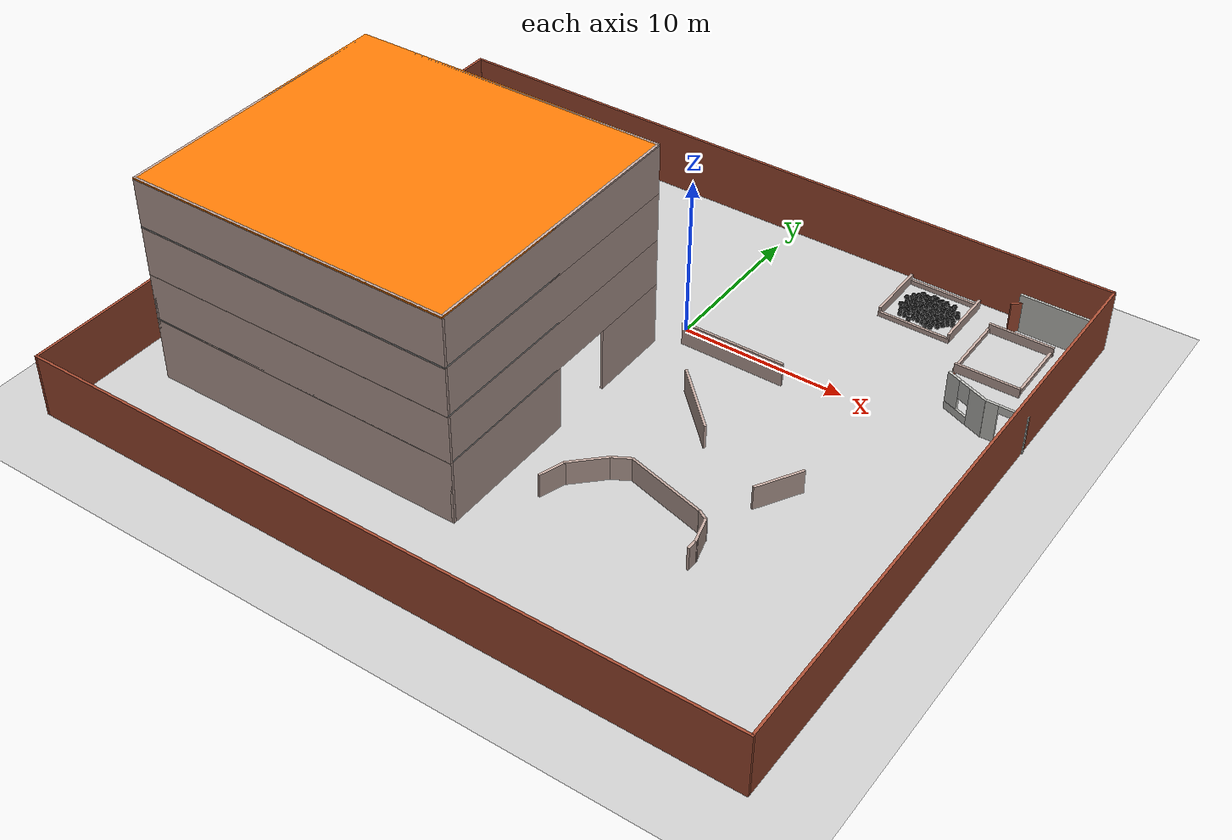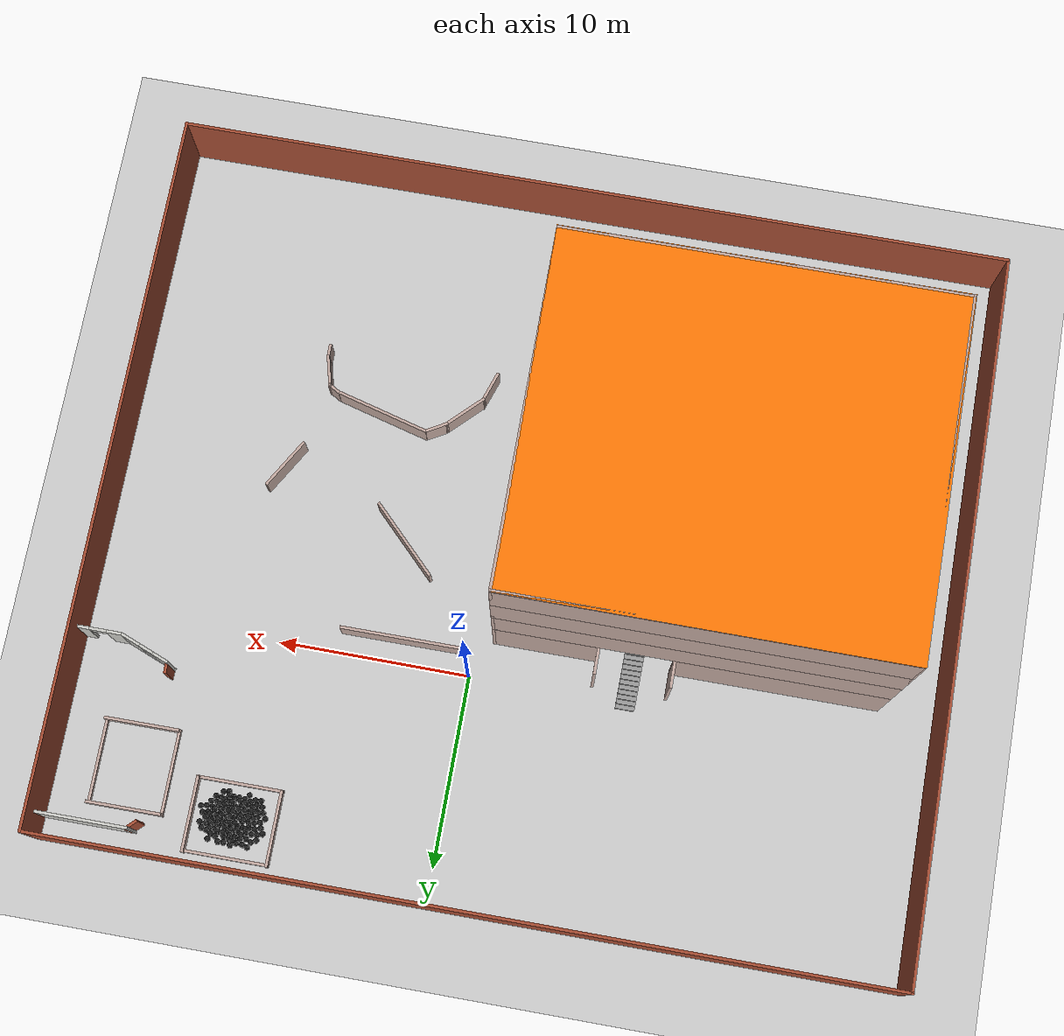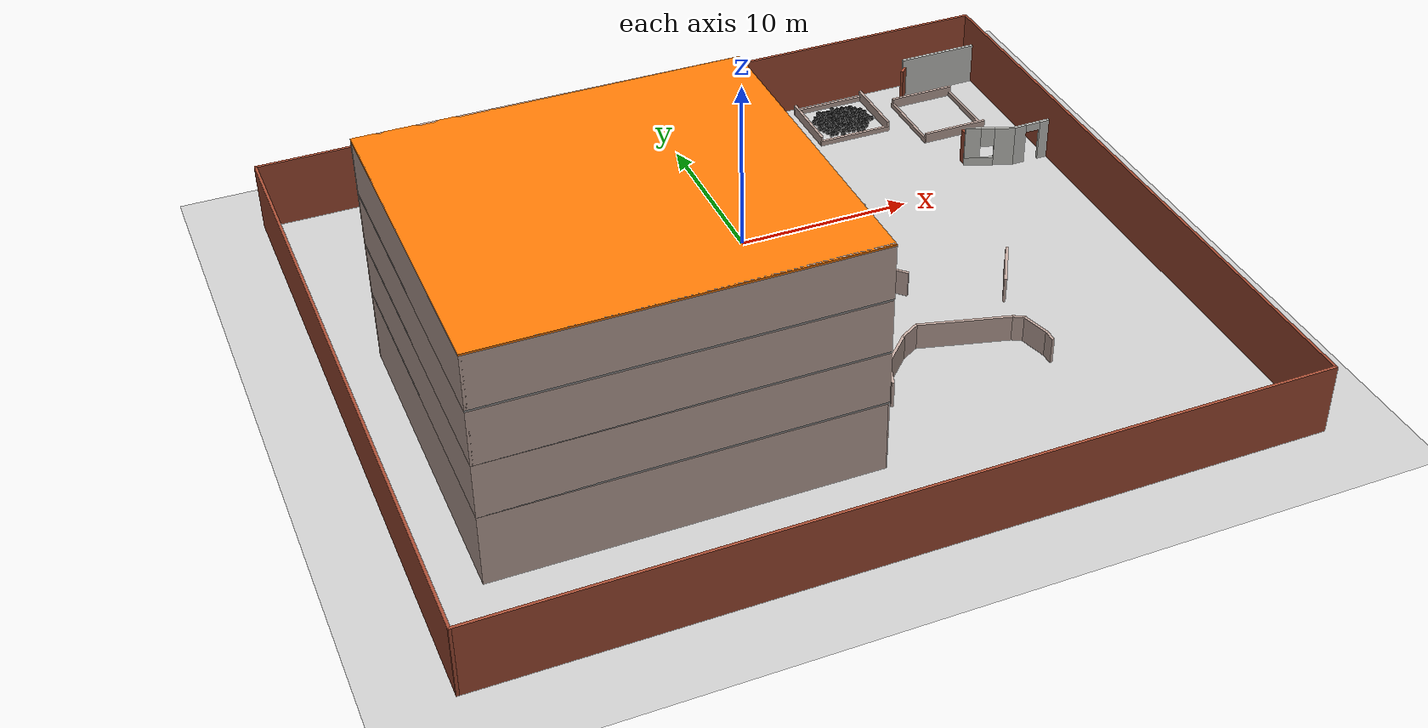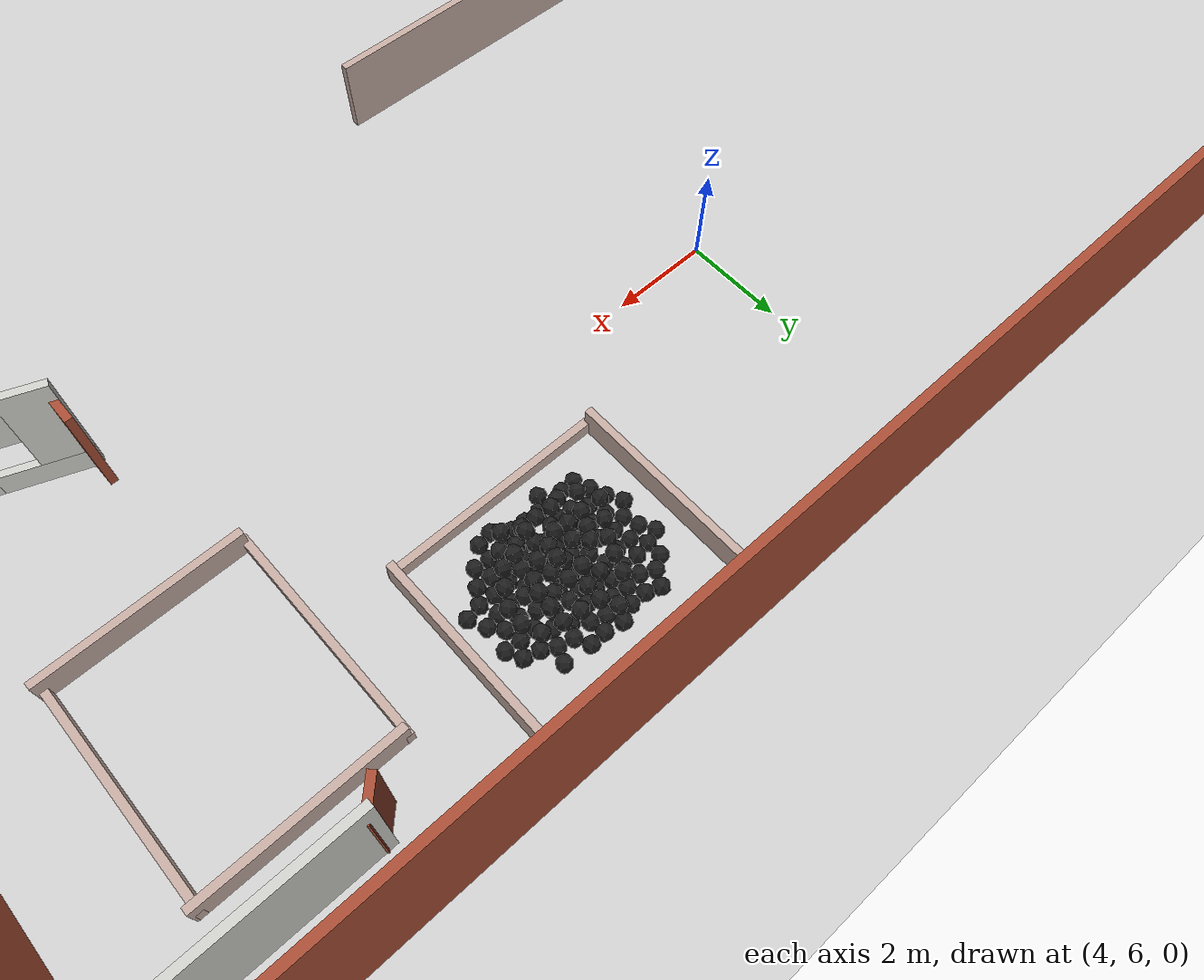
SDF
<sdf version="1.7">
 <world name="default">
  <light name="sun" type="directional">
   <pose>0 0 10 0 -0 0</pose>
   <diffuse>0.8 0.8 0.8 1</diffuse>
   <specular>0.2 0.2 0.2 1</specular>
   <attenuation>
    <range>1000</range>
    <constant>0.9</constant>
    <linear>0.01</linear>
    <quadratic>0.001</quadratic>
   </attenuation>
   <direction>-0.5 0.1 -0.9</direction>
   <spot><inner_angle>0</inner_angle><outer_angle>0</outer_angle><falloff>0</falloff></spot>
  </light>
  <model name="ground_plane">
   <static>1</static>
   <link name="link">
    <collision name="collision">
     <geometry><plane><normal>0 0 1</normal><size>100 100</size></plane></geometry>
     <surface><friction><ode><mu>100</mu><mu2>50</mu2></ode></friction></surface>
    </collision>
    <visual name="visual">
     <cast_shadows>0</cast_shadows>
     <geometry><plane><normal>0 0 1</normal><size>100 100</size></plane></geometry>
     <material>
      <script><uri>file://media/materials/scripts/gazebo.material</uri><name>Gazebo/Grey</name></script>
     </material>
    </visual>
   </link>
  </model>
  <gravity>0 0 -9.8</gravity>
  <magnetic_field>6e-06 2.3e-05 -4.2e-05</magnetic_field>
  <atmosphere type="adiabatic"/>
  <physics name="default_physics" default="0" type="ode">
   <max_step_size>0.001</max_step_size>
   <real_time_factor>1</real_time_factor>
   <real_time_update_rate>1000</real_time_update_rate>
  </physics>
  <scene><ambient>0.4 0.4 0.4 1</ambient><background>0.7 0.7 0.7 1</background><shadows>1</shadows></scene>
  <audio><device>default</device></audio>
  <spherical_coordinates>
   <surface_model>EARTH_WGS84</surface_model>
   <latitude_deg>0</latitude_deg>
   <longitude_deg>0</longitude_deg>
   <elevation>0</elevation>
   <heading_deg>0</heading_deg>
  </spherical_coordinates>
  <model name="building2">
   <pose>-11 -10.325 0 0 -0 0</pose>
   <link name="Floor_0">
    <collision name="Floor_0_Collision">
     <geometry><box><size>20.15 18.15 0.1</size></box></geometry>
     <pose>0 0 0.05 0 -0 0</pose>
    </collision>
    <visual name="Floor_0_Visual">
     <pose>0 0 0.05 0 -0 0</pose>
     <geometry><box><size>20.15 18.15 0.1</size></box></geometry>
     <material>
      <script><uri>file://media/materials/scripts/gazebo.material</uri><name>Gazebo/Grey</name></script>
      <ambient>1 1 1 1</ambient>
     </material>
     <meta><layer>1</layer></meta>
    </visual>
    <pose>-0 -0.675 4 0 -0 0</pose>
   </link>
   <link name="Floor_2">
    <collision name="Floor_2_Collision">
     <geometry><box><size>20.15 18.15 0.1</size></box></geometry>
     <pose>0 0 0.05 0 -0 0</pose>
    </collision>
    <visual name="Floor_2_Visual">
     <pose>0 0 0.05 0 -0 0</pose>
     <geometry><box><size>20.15 18.15 0.1</size></box></geometry>
     <material>
      <script><uri>file://media/materials/scripts/gazebo.material</uri><name>Gazebo/Grey</name></script>
      <ambient>1 1 1 1</ambient>
     </material>
     <meta><layer>2</layer></meta>
    </visual>
    <pose>-0 -0.675 7 0 -0 0</pose>
   </link>
   <link name="Floor_3">
    <collision name="Floor_3_Collision">
     <geometry><box><size>20.15 18.15 0.1</size></box></geometry>
     <pose>0 0 0.05 0 -0 0</pose>
    </collision>
    <visual name="Floor_3_Visual">
     <pose>0 0 0.05 0 -0 0</pose>
     <geometry><box><size>20.15 18.15 0.1</size></box></geometry>
     <material>
      <script><uri>file://media/materials/scripts/gazebo.material</uri><name>Gazebo/Grey</name></script>
      <ambient>1 1 1 1</ambient>
     </material>
     <meta><layer>3</layer></meta>
    </visual>
    <pose>-0 -0.675 10 0 -0 0</pose>
   </link>
   <link name="Floor_8">
    <collision name="Floor_8_Collision">
     <geometry><box><size>20.15 18.15 0.1</size></box></geometry>
     <pose>0 0 0.05 0 -0 0</pose>
    </collision>
    <visual name="Floor_8_Visual">
     <pose>0 0 0.05 0 -0 0</pose>
     <geometry><box><size>20.15 18.15 0.1</size></box></geometry>
     <material>
      <script><uri>file://media/materials/scripts/gazebo.material</uri><name>Gazebo/Grey</name></script>
      <ambient>0.996078 0.47451 0.0196078 1</ambient>
     </material>
     <meta><layer>4</layer></meta>
    </visual>
    <pose>-0 -0.675 13 0 -0 0</pose>
   </link>
   <link name="Wall_11">
    <collision name="Wall_11_Collision">
     <geometry><box><size>1.5 0.15 4</size></box></geometry>
     <pose>0 0 2 0 -0 0</pose>
    </collision>
    <visual name="Wall_11_Visual">
     <pose>0 0 2 0 -0 0</pose>
     <geometry><box><size>1.5 0.15 4</size></box></geometry>
     <material>
      <script><uri>file://media/materials/scripts/gazebo.material</uri><name>Gazebo/Grey</name></script>
      <ambient>0.760784 0.662745 0.627451 1</ambient>
     </material>
     <meta><layer>0</layer></meta>
    </visual>
    <pose>0.8 9 0 0 -0 -1.5708</pose>
   </link>
   <link name="Wall_12">
    <collision name="Wall_12_Collision">
     <geometry><box><size>10.95 0.15 4</size></box></geometry>
     <pose>0 0 2 0 -0 0</pose>
    </collision>
    <visual name="Wall_12_Visual">
     <pose>0 0 2 0 -0 0</pose>
     <geometry><box><size>10.95 0.15 4</size></box></geometry>
     <material>
      <script><uri>file://media/materials/scripts/gazebo.material</uri><name>Gazebo/Grey</name></script>
      <ambient>0.760784 0.662745 0.627451 1</ambient>
     </material>
     <meta><layer>0</layer></meta>
    </visual>
    <pose>-4.6 8.325 0 0 -0 3.14159</pose>
   </link>
   <link name="Wall_14">
    <collision name="Wall_14_Collision">
     <geometry><box><size>18.15 0.15 4</size></box></geometry>
     <pose>0 0 2 0 -0 0</pose>
    </collision>
    <visual name="Wall_14_Visual">
     <pose>0 0 2 0 -0 0</pose>
     <geometry><box><size>18.15 0.15 4</size></box></geometry>
     <material>
      <script><uri>file://media/materials/scripts/gazebo.material</uri><name>Gazebo/Grey</name></script>
      <ambient>0.760784 0.662745 0.627451 1</ambient>
     </material>
     <meta><layer>0</layer></meta>
    </visual>
    <pose>-10 -0.675 0 0 -0 -1.5708</pose>
   </link>
   <link name="Wall_16">
    <collision name="Wall_16_Collision">
     <geometry><box><size>20.15 0.15 4</size></box></geometry>
     <pose>0 0 2 0 -0 0</pose>
    </collision>
    <visual name="Wall_16_Visual">
     <pose>0 0 2 0 -0 0</pose>
     <geometry><box><size>20.15 0.15 4</size></box></geometry>
     <material>
      <script><uri>file://media/materials/scripts/gazebo.material</uri><name>Gazebo/Grey</name></script>
      <ambient>0.760784 0.662745 0.627451 1</ambient>
     </material>
     <meta><layer>0</layer></meta>
    </visual>
    <pose>-0 -9.675 0 0 -0 0</pose>
   </link>
   <link name="Wall_24">
    <collision name="Wall_24_Collision">
     <geometry><box><size>18.15 0.15 3</size></box></geometry>
     <pose>0 0 1.5 0 -0 0</pose>
    </collision>
    <visual name="Wall_24_Visual">
     <pose>0 0 1.5 0 -0 0</pose>
     <geometry><box><size>18.15 0.15 3</size></box></geometry>
     <material>
      <script><uri>file://media/materials/scripts/gazebo.material</uri><name>Gazebo/Grey</name></script>
      <ambient>0.760784 0.662745 0.627451 1</ambient>
     </material>
     <meta><layer>1</layer></meta>
    </visual>
    <pose>-10 -0.675 4 0 -0 -1.5708</pose>
   </link>
   <link name="Wall_25">
    <collision name="Wall_25_Collision">
     <geometry><box><size>20.15 0.15 3</size></box></geometry>
     <pose>0 0 1.5 0 -0 0</pose>
    </collision>
    <visual name="Wall_25_Visual">
     <pose>0 0 1.5 0 -0 0</pose>
     <geometry><box><size>20.15 0.15 3</size></box></geometry>
     <material>
      <script><uri>file://media/materials/scripts/gazebo.material</uri><name>Gazebo/Grey</name></script>
      <ambient>0.760784 0.662745 0.627451 1</ambient>
     </material>
     <meta><layer>1</layer></meta>
    </visual>
    <pose>-0 -9.675 4 0 -0 0</pose>
   </link>
   <link name="Wall_31">
    <collision name="Wall_31_Collision">
     <geometry><box><size>20.15 0.15 3</size></box></geometry>
     <pose>0 0 1.5 0 -0 0</pose>
    </collision>
    <visual name="Wall_31_Visual">
     <pose>0 0 1.5 0 -0 0</pose>
     <geometry><box><size>20.15 0.15 3</size></box></geometry>
     <material>
      <script><uri>file://media/materials/scripts/gazebo.material</uri><name>Gazebo/Grey</name></script>
      <ambient>0.760784 0.662745 0.627451 1</ambient>
     </material>
     <meta><layer>1</layer></meta>
    </visual>
    <pose>-0 8.325 4 0 -0 0</pose>
   </link>
   <link name="Wall_33">
    <collision name="Wall_33_Collision">
     <geometry><box><size>18 0.15 3</size></box></geometry>
     <pose>0 0 1.5 0 -0 0</pose>
    </collision>
    <visual name="Wall_33_Visual">
     <pose>0 0 1.5 0 -0 0</pose>
     <geometry><box><size>18 0.15 3</size></box></geometry>
     <material>
      <script><uri>file://media/materials/scripts/gazebo.material</uri><name>Gazebo/Grey</name></script>
      <ambient>0.760784 0.662745 0.627451 1</ambient>
     </material>
     <meta><layer>1</layer></meta>
    </visual>
    <pose>10 -0.6 4 0 -0 -1.5708</pose>
   </link>
   <link name="Wall_4">
    <collision name="Wall_4_Collision">
     <geometry><box><size>5.15 0.15 4</size></box></geometry>
     <pose>0 0 2 0 -0 0</pose>
    </collision>
    <visual name="Wall_4_Visual">
     <pose>0 0 2 0 -0 0</pose>
     <geometry><box><size>5.15 0.15 4</size></box></geometry>
     <material>
      <script><uri>file://media/materials/scripts/gazebo.material</uri><name>Gazebo/Grey</name></script>
      <ambient>0.760784 0.662745 0.627451 1</ambient>
     </material>
     <meta><layer>0</layer></meta>
    </visual>
    <pose>10 5.825 0 0 -0 -1.5708</pose>
   </link>
   <link name="Wall_42">
    <collision name="Wall_42_Collision">
     <geometry><box><size>18.15 0.15 3</size></box></geometry>
     <pose>0 0 1.5 0 -0 0</pose>
    </collision>
    <visual name="Wall_42_Visual">
     <pose>0 0 1.5 0 -0 0</pose>
     <geometry><box><size>18.15 0.15 3</size></box></geometry>
     <material>
      <script><uri>file://media/materials/scripts/gazebo.material</uri><name>Gazebo/Grey</name></script>
      <ambient>0.760784 0.662745 0.627451 1</ambient>
     </material>
     <meta><layer>2</layer></meta>
    </visual>
    <pose>-10 -0.675 7 0 -0 -1.5708</pose>
   </link>
   <link name="Wall_43">
    <collision name="Wall_43_Collision">
     <geometry><box><size>20.15 0.15 3</size></box></geometry>
     <pose>0 0 1.5 0 -0 0</pose>
    </collision>
    <visual name="Wall_43_Visual">
     <pose>0 0 1.5 0 -0 0</pose>
     <geometry><box><size>20.15 0.15 3</size></box></geometry>
     <material>
      <script><uri>file://media/materials/scripts/gazebo.material</uri><name>Gazebo/Grey</name></script>
      <ambient>0.760784 0.662745 0.627451 1</ambient>
     </material>
     <meta><layer>2</layer></meta>
    </visual>
    <pose>-0 -9.675 7 0 -0 0</pose>
   </link>
   <link name="Wall_44">
    <collision name="Wall_44_Collision">
     <geometry><box><size>20.15 0.15 3</size></box></geometry>
     <pose>0 0 1.5 0 -0 0</pose>
    </collision>
    <visual name="Wall_44_Visual">
     <pose>0 0 1.5 0 -0 0</pose>
     <geometry><box><size>20.15 0.15 3</size></box></geometry>
     <material>
      <script><uri>file://media/materials/scripts/gazebo.material</uri><name>Gazebo/Grey</name></script>
      <ambient>0.760784 0.662745 0.627451 1</ambient>
     </material>
     <meta><layer>2</layer></meta>
    </visual>
    <pose>-0 8.325 7 0 -0 0</pose>
   </link>
   <link name="Wall_45">
    <collision name="Wall_45_Collision">
     <geometry><box><size>18 0.15 3</size></box></geometry>
     <pose>0 0 1.5 0 -0 0</pose>
    </collision>
    <visual name="Wall_45_Visual">
     <pose>0 0 1.5 0 -0 0</pose>
     <geometry><box><size>18 0.15 3</size></box></geometry>
     <material>
      <script><uri>file://media/materials/scripts/gazebo.material</uri><name>Gazebo/Grey</name></script>
      <ambient>0.760784 0.662745 0.627451 1</ambient>
     </material>
     <meta><layer>2</layer></meta>
    </visual>
    <pose>10 -0.6 7 0 -0 -1.5708</pose>
   </link>
   <link name="Wall_46">
    <collision name="Wall_46_Collision">
     <geometry><box><size>18.15 0.15 3</size></box></geometry>
     <pose>0 0 1.5 0 -0 0</pose>
    </collision>
    <visual name="Wall_46_Visual">
     <pose>0 0 1.5 0 -0 0</pose>
     <geometry><box><size>18.15 0.15 3</size></box></geometry>
     <material>
      <script><uri>file://media/materials/scripts/gazebo.material</uri><name>Gazebo/Grey</name></script>
      <ambient>0.760784 0.662745 0.627451 1</ambient>
     </material>
     <meta><layer>3</layer></meta>
    </visual>
    <pose>-10 -0.675 10 0 -0 -1.5708</pose>
   </link>
   <link name="Wall_47">
    <collision name="Wall_47_Collision">
     <geometry><box><size>20.15 0.15 3</size></box></geometry>
     <pose>0 0 1.5 0 -0 0</pose>
    </collision>
    <visual name="Wall_47_Visual">
     <pose>0 0 1.5 0 -0 0</pose>
     <geometry><box><size>20.15 0.15 3</size></box></geometry>
     <material>
      <script><uri>file://media/materials/scripts/gazebo.material</uri><name>Gazebo/Grey</name></script>
      <ambient>0.760784 0.662745 0.627451 1</ambient>
     </material>
     <meta><layer>3</layer></meta>
    </visual>
    <pose>-0 -9.675 10 0 -0 0</pose>
   </link>
   <link name="Wall_48">
    <collision name="Wall_48_Collision">
     <geometry><box><size>20.15 0.15 3</size></box></geometry>
     <pose>0 0 1.5 0 -0 0</pose>
    </collision>
    <visual name="Wall_48_Visual">
     <pose>0 0 1.5 0 -0 0</pose>
     <geometry><box><size>20.15 0.15 3</size></box></geometry>
     <material>
      <script><uri>file://media/materials/scripts/gazebo.material</uri><name>Gazebo/Grey</name></script>
      <ambient>0.760784 0.662745 0.627451 1</ambient>
     </material>
     <meta><layer>3</layer></meta>
    </visual>
    <pose>-0 8.325 10 0 -0 0</pose>
   </link>
   <link name="Wall_49">
    <collision name="Wall_49_Collision">
     <geometry><box><size>18 0.15 3</size></box></geometry>
     <pose>0 0 1.5 0 -0 0</pose>
    </collision>
    <visual name="Wall_49_Visual">
     <pose>0 0 1.5 0 -0 0</pose>
     <geometry><box><size>18 0.15 3</size></box></geometry>
     <material>
      <script><uri>file://media/materials/scripts/gazebo.material</uri><name>Gazebo/Grey</name></script>
      <ambient>0.760784 0.662745 0.627451 1</ambient>
     </material>
     <meta><layer>3</layer></meta>
    </visual>
    <pose>10 -0.6 10 0 -0 -1.5708</pose>
   </link>
   <link name="Wall_6">
    <collision name="Wall_6_Collision">
     <geometry><box><size>9.15 0.15 4</size></box></geometry>
     <pose>0 0 2 0 -0 0</pose>
    </collision>
    <visual name="Wall_6_Visual">
     <pose>0 0 2 0 -0 0</pose>
     <geometry><box><size>9.15 0.15 4</size></box></geometry>
     <material>
      <script><uri>file://media/materials/scripts/gazebo.material</uri><name>Gazebo/Grey</name></script>
      <ambient>0.760784 0.662745 0.627451 1</ambient>
     </material>
     <meta><layer>0</layer></meta>
    </visual>
    <pose>10 -5.175 0 0 -0 -1.5708</pose>
   </link>
   <link name="Wall_76">
    <collision name="Wall_76_Collision">
     <geometry><box><size>18.15 0.15 0.1</size></box></geometry>
     <pose>0 0 0.05 0 -0 0</pose>
    </collision>
    <visual name="Wall_76_Visual">
     <pose>0 0 0.05 0 -0 0</pose>
     <geometry><box><size>18.15 0.15 0.1</size></box></geometry>
     <material>
      <script><uri>file://media/materials/scripts/gazebo.material</uri><name>Gazebo/Grey</name></script>
      <ambient>0.760784 0.662745 0.627451 1</ambient>
     </material>
     <meta><layer>4</layer></meta>
    </visual>
    <pose>-10 -0.675 13 0 -0 -1.5708</pose>
   </link>
   <link name="Wall_77">
    <collision name="Wall_77_Collision">
     <geometry><box><size>20.15 0.15 0.1</size></box></geometry>
     <pose>0 0 0.05 0 -0 0</pose>
    </collision>
    <visual name="Wall_77_Visual">
     <pose>0 0 0.05 0 -0 0</pose>
     <geometry><box><size>20.15 0.15 0.1</size></box></geometry>
     <material>
      <script><uri>file://media/materials/scripts/gazebo.material</uri><name>Gazebo/Grey</name></script>
      <ambient>0.760784 0.662745 0.627451 1</ambient>
     </material>
     <meta><layer>4</layer></meta>
    </visual>
    <pose>-0 -9.675 13 0 -0 0</pose>
   </link>
   <link name="Wall_78">
    <collision name="Wall_78_Collision">
     <geometry><box><size>20.15 0.15 0.1</size></box></geometry>
     <pose>0 0 0.05 0 -0 0</pose>
    </collision>
    <visual name="Wall_78_Visual">
     <pose>0 0 0.05 0 -0 0</pose>
     <geometry><box><size>20.15 0.15 0.1</size></box></geometry>
     <material>
      <script><uri>file://media/materials/scripts/gazebo.material</uri><name>Gazebo/Grey</name></script>
      <ambient>0.760784 0.662745 0.627451 1</ambient>
     </material>
     <meta><layer>4</layer></meta>
    </visual>
    <pose>-0 8.325 13 0 -0 0</pose>
   </link>
   <link name="Wall_79">
    <collision name="Wall_79_Collision">
     <geometry><box><size>18 0.15 0.1</size></box></geometry>
     <pose>0 0 0.05 0 -0 0</pose>
    </collision>
    <visual name="Wall_79_Visual">
     <pose>0 0 0.05 0 -0 0</pose>
     <geometry><box><size>18 0.15 0.1</size></box></geometry>
     <material>
      <script><uri>file://media/materials/scripts/gazebo.material</uri><name>Gazebo/Grey</name></script>
      <ambient>0.760784 0.662745 0.627451 1</ambient>
     </material>
     <meta><layer>4</layer></meta>
    </visual>
    <pose>10 -0.6 13 0 -0 -1.5708</pose>
   </link>
   <link name="Wall_8">
    <collision name="Wall_8_Collision">
     <geometry><box><size>5.5 0.15 4</size></box></geometry>
     <pose>0 0 2 0 -0 0</pose>
    </collision>
    <visual name="Wall_8_Visual">
     <pose>0 0 2 0 -0 0</pose>
     <geometry><box><size>5.5 0.15 4</size></box></geometry>
     <material>
      <script><uri>file://media/materials/scripts/gazebo.material</uri><name>Gazebo/Grey</name></script>
      <ambient>0.760784 0.662745 0.627451 1</ambient>
     </material>
     <meta><layer>0</layer></meta>
    </visual>
    <pose>7.325 8.325 0 0 -0 3.14159</pose>
   </link>
   <link name="Wall_9">
    <collision name="Wall_9_Collision">
     <geometry><box><size>1.5 0.15 4</size></box></geometry>
     <pose>0 0 2 0 -0 0</pose>
    </collision>
    <visual name="Wall_9_Visual">
     <pose>0 0 2 0 -0 0</pose>
     <geometry><box><size>1.5 0.15 4</size></box></geometry>
     <material>
      <script><uri>file://media/materials/scripts/gazebo.material</uri><name>Gazebo/Grey</name></script>
      <ambient>0.760784 0.662745 0.627451 1</ambient>
     </material>
     <meta><layer>0</layer></meta>
    </visual>
    <pose>4.65 9 0 0 -0 1.5708</pose>
   </link>
   <static>1</static>
  </model>
  <model name="wall11">
   <pose>-2 -7 0 0 -0 0</pose>
   <link name="Wall_0">
    <collision name="Wall_0_Collision">
     <geometry><box><size>44.15 0.15 4</size></box></geometry>
     <pose>0 0 2 0 -0 0</pose>
    </collision>
    <visual name="Wall_0_Visual">
     <pose>0 0 2 0 -0 0</pose>
     <geometry><box><size>44.15 0.15 4</size></box></geometry>
     <material>
      <script><uri>file://media/materials/scripts/gazebo.material</uri><name>Gazebo/Bricks</name></script>
      <ambient>1 1 1 1</ambient>
     </material>
     <meta><layer>0</layer></meta>
    </visual>
    <pose>0 19 0 0 -0 0</pose>
   </link>
   <link name="Wall_2">
    <collision name="Wall_2_Collision">
     <geometry><box><size>38.15 0.15 4</size></box></geometry>
     <pose>0 0 2 0 -0 0</pose>
    </collision>
    <visual name="Wall_2_Visual">
     <pose>0 0 2 0 -0 0</pose>
     <geometry><box><size>38.15 0.15 4</size></box></geometry>
     <material>
      <script><uri>file://media/materials/scripts/gazebo.material</uri><name>Gazebo/Bricks</name></script>
      <ambient>1 1 1 1</ambient>
     </material>
     <meta><layer>0</layer></meta>
    </visual>
    <pose>22 0 0 0 -0 -1.5708</pose>
   </link>
   <link name="Wall_4">
    <collision name="Wall_4_Collision">
     <geometry><box><size>44.15 0.15 4</size></box></geometry>
     <pose>0 0 2 0 -0 0</pose>
    </collision>
    <visual name="Wall_4_Visual">
     <pose>0 0 2 0 -0 0</pose>
     <geometry><box><size>44.15 0.15 4</size></box></geometry>
     <material>
      <script><uri>file://media/materials/scripts/gazebo.material</uri><name>Gazebo/Bricks</name></script>
      <ambient>1 1 1 1</ambient>
     </material>
     <meta><layer>0</layer></meta>
    </visual>
    <pose>0 -19 0 0 -0 3.14159</pose>
   </link>
   <link name="Wall_6">
    <collision name="Wall_6_Collision">
     <geometry><box><size>38.15 0.15 4</size></box></geometry>
     <pose>0 0 2 0 -0 0</pose>
    </collision>
    <visual name="Wall_6_Visual">
     <pose>0 0 2 0 -0 0</pose>
     <geometry><box><size>38.15 0.15 4</size></box></geometry>
     <material>
      <script><uri>file://media/materials/scripts/gazebo.material</uri><name>Gazebo/Bricks</name></script>
      <ambient>1 1 1 1</ambient>
     </material>
     <meta><layer>0</layer></meta>
    </visual>
    <pose>-22 0 0 0 -0 1.5708</pose>
   </link>
   <static>1</static>
  </model>
  <model name="wall12">
   <pose>6.34105 -8.55443 0 0 -0 0</pose>
   <link name="Wall_0">
    <collision name="Wall_0_Collision">
     <geometry><box><size>1.73114 0.15 1.5</size></box></geometry>
     <pose>0 0 0.75 0 -0 0</pose>
    </collision>
    <visual name="Wall_0_Visual">
     <pose>0 0 0.75 0 -0 0</pose>
     <geometry><box><size>1.73114 0.15 1.5</size></box></geometry>
     <material>
      <script><uri>file://media/materials/scripts/gazebo.material</uri><name>Gazebo/Grey</name></script>
      <ambient>0.760784 0.662745 0.627451 1</ambient>
     </material>
     <meta><layer>0</layer></meta>
    </visual>
    <pose>-4.71274 -6.64107 0 0 -0 1.24905</pose>
   </link>
   <link name="Wall_13">
    <collision name="Wall_13_Collision">
     <geometry><box><size>6.5 0.15 1.5</size></box></geometry>
     <pose>0 0 0.75 0 -0 0</pose>
    </collision>
    <visual name="Wall_13_Visual">
     <pose>0 0 0.75 0 -0 0</pose>
     <geometry><box><size>6.5 0.15 1.5</size></box></geometry>
     <material>
      <script><uri>file://media/materials/scripts/gazebo.material</uri><name>Gazebo/Grey</name></script>
      <ambient>0.760784 0.662745 0.627451 1</ambient>
     </material>
     <meta><layer>0</layer></meta>
    </visual>
    <pose>-2.67774 7.41093 0 0 -0 0</pose>
   </link>
   <link name="Wall_15">
    <collision name="Wall_15_Collision">
     <geometry><box><size>4.75 0.15 1.5</size></box></geometry>
     <pose>0 0 0.75 0 -0 0</pose>
    </collision>
    <visual name="Wall_15_Visual">
     <pose>0 0 0.75 0 -0 0</pose>
     <geometry><box><size>4.75 0.15 1.5</size></box></geometry>
     <material>
      <script><uri>file://media/materials/scripts/gazebo.material</uri><name>Gazebo/Grey</name></script>
      <ambient>0.760784 0.662745 0.627451 1</ambient>
     </material>
     <meta><layer>0</layer></meta>
    </visual>
    <pose>-1.78524 2.28593 0 0 -0 -0.785244</pose>
   </link>
   <link name="Wall_2">
    <collision name="Wall_2_Collision">
     <geometry><box><size>2.5 0.15 1.5</size></box></geometry>
     <pose>0 0 0.75 0 -0 0</pose>
    </collision>
    <visual name="Wall_2_Visual">
     <pose>0 0 0.75 0 -0 0</pose>
     <geometry><box><size>2.5 0.15 1.5</size></box></geometry>
     <material>
      <script><uri>file://media/materials/scripts/gazebo.material</uri><name>Gazebo/Grey</name></script>
      <ambient>0.760784 0.662745 0.627451 1</ambient>
     </material>
     <meta><layer>0</layer></meta>
    </visual>
    <pose>-3.63175 -5.06007 0 0 -0 0.785398</pose>
   </link>
   <link name="Wall_3">
    <collision name="Wall_3_Collision">
     <geometry><box><size>1.25 0.15 1.5</size></box></geometry>
     <pose>0 0 0.75 0 -0 0</pose>
    </collision>
    <visual name="Wall_3_Visual">
     <pose>0 0 0.75 0 -0 0</pose>
     <geometry><box><size>1.25 0.15 1.5</size></box></geometry>
     <material>
      <script><uri>file://media/materials/scripts/gazebo.material</uri><name>Gazebo/Grey</name></script>
      <ambient>0.760784 0.662745 0.627451 1</ambient>
     </material>
     <meta><layer>0</layer></meta>
    </visual>
    <pose>-2.32475 -3.95407 0 0 -0 0.523884</pose>
   </link>
   <link name="Wall_5">
    <collision name="Wall_5_Collision">
     <geometry><box><size>0.75 0.15 1.5</size></box></geometry>
     <pose>0 0 0.75 0 -0 0</pose>
    </collision>
    <visual name="Wall_5_Visual">
     <pose>0 0 0.75 0 -0 0</pose>
     <geometry><box><size>0.75 0.15 1.5</size></box></geometry>
     <material>
      <script><uri>file://media/materials/scripts/gazebo.material</uri><name>Gazebo/Grey</name></script>
      <ambient>0.760784 0.662745 0.627451 1</ambient>
     </material>
     <meta><layer>0</layer></meta>
    </visual>
    <pose>4.07425 -7.09807 0 0 -0 1.5708</pose>
   </link>
   <link name="Wall_6">
    <collision name="Wall_6_Collision">
     <geometry><box><size>1.75 0.15 1.5</size></box></geometry>
     <pose>0 0 0.75 0 -0 0</pose>
    </collision>
    <visual name="Wall_6_Visual">
     <pose>0 0 0.75 0 -0 0</pose>
     <geometry><box><size>1.75 0.15 1.5</size></box></geometry>
     <material>
      <script><uri>file://media/materials/scripts/gazebo.material</uri><name>Gazebo/Grey</name></script>
      <ambient>0.760784 0.662745 0.627451 1</ambient>
     </material>
     <meta><layer>0</layer></meta>
    </visual>
    <pose>3.86726 -6.02557 0 0 -0 1.83261</pose>
   </link>
   <link name="Wall_7">
    <collision name="Wall_7_Collision">
     <geometry><box><size>0.75 0.15 1.5</size></box></geometry>
     <pose>0 0 0.75 0 -0 0</pose>
    </collision>
    <visual name="Wall_7_Visual">
     <pose>0 0 0.75 0 -0 0</pose>
     <geometry><box><size>0.75 0.15 1.5</size></box></geometry>
     <material>
      <script><uri>file://media/materials/scripts/gazebo.material</uri><name>Gazebo/Grey</name></script>
      <ambient>0.760784 0.662745 0.627451 1</ambient>
     </material>
     <meta><layer>0</layer></meta>
    </visual>
    <pose>3.40026 -5.10307 0 0 -0 2.61831</pose>
   </link>
   <link name="Wall_9">
    <collision name="Wall_9_Collision">
     <geometry><box><size>3 0.15 1.5</size></box></geometry>
     <pose>0 0 0.75 0 -0 0</pose>
    </collision>
    <visual name="Wall_9_Visual">
     <pose>0 0 0.75 0 -0 0</pose>
     <geometry><box><size>3 0.15 1.5</size></box></geometry>
     <material>
      <script><uri>file://media/materials/scripts/gazebo.material</uri><name>Gazebo/Grey</name></script>
      <ambient>0.760784 0.662745 0.627451 1</ambient>
     </material>
     <meta><layer>0</layer></meta>
    </visual>
    <pose>5.11275 -0.631066 0 0 -0 1.04717</pose>
   </link>
   <static>1</static>
  </model>
  <model name="wall1">
   <pose>6.97273 -12.8415 0 0 0 -0.014727</pose>
   <link name="Wall_0">
    <collision name="Wall_0_Collision">
     <geometry><box><size>5.09773 0.15 1.5</size></box></geometry>
     <pose>0 0 0.75 0 -0 0</pose>
    </collision>
    <visual name="Wall_0_Visual">
     <pose>0 0 0.75 0 -0 0</pose>
     <geometry><box><size>5.09773 0.15 1.5</size></box></geometry>
     <material>
      <script><uri>file://media/materials/scripts/gazebo.material</uri><name>Gazebo/Grey</name></script>
      <ambient>0.760784 0.662745 0.627451 1</ambient>
     </material>
     <meta><layer>0</layer></meta>
    </visual>
    <pose>0 0 0 0 -0 -0.244979</pose>
   </link>
   <static>1</static>
  </model>
  <model name="haoduomiantiaa_0">
   <link name="link_0">
    <inertial>
     <mass>0.2</mass>
     <inertia>
      <ixx>0.166667</ixx>
      <ixy>0</ixy>
      <ixz>0</ixz>
      <iyy>0.166667</iyy>
      <iyz>0</iyz>
      <izz>0.166667</izz>
     </inertia>
    </inertial>
    <visual name="visual">
     <geometry>
      <mesh>
       <uri>/home/lihaoyang/catkin_ws/src/pudong_gazebo/world/stl/haoduomianti.stl</uri>
       <scale>1 1 1</scale>
      </mesh>
     </geometry>
     <material>
      <lighting>1</lighting>
      <script><uri>file://media/materials/scripts/gazebo.material</uri><name>Gazebo/Black</name></script>
      <shader type="pixel"><normal_map>__default__</normal_map></shader>
      <ambient>0.3 0.3 0.3 1</ambient>
      <diffuse>0.7 0.7 0.7 1</diffuse>
      <specular>0.01 0.01 0.01 1</specular>
      <emissive>0 0 0 1</emissive>
     </material>
    </visual>
    <collision name="collision">
     <geometry>
      <mesh>
       <uri>/home/lihaoyang/catkin_ws/src/pudong_gazebo/world/stl/haoduomianti.stl</uri>
       <scale>1 1 1</scale>
      </mesh>
     </geometry>
     <surface>
      <friction>
       <ode><mu>1</mu><mu2>1</mu2><fdir1>0 0 0</fdir1><slip1>0</slip1><slip2>0</slip2></ode>
       <torsional>
        <coefficient>1</coefficient>
        <patch_radius>0</patch_radius>
        <surface_radius>0</surface_radius>
        <use_patch_radius>1</use_patch_radius>
        <ode><slip>0</slip></ode>
       </torsional>
      </friction>
      <bounce><restitution_coefficient>0</restitution_coefficient><threshold>1e+06</threshold></bounce>
      <contact>
       <collide_without_contact>0</collide_without_contact>
       <collide_without_contact_bitmask>1</collide_without_contact_bitmask>
       <collide_bitmask>1</collide_bitmask>
       <ode>
        <soft_cfm>0</soft_cfm>
        <soft_erp>0.2</soft_erp>
        <kp>1e+13</kp>
        <kd>1</kd>
        <max_vel>0.01</max_vel>
        <min_depth>0</min_depth>
       </ode>
       <bullet>
        <split_impulse>1</split_impulse>
        <split_impulse_penetration_threshold>-0.01</split_impulse_penetration_threshold>
        <soft_cfm>0</soft_cfm>
        <soft_erp>0.2</soft_erp>
        <kp>1e+13</kp>
        <kd>1</kd>
       </bullet>
      </contact>
     </surface>
    </collision>
   </link>
   <static>0</static>
   <pose>10.8647 9.09379 -0.115476 0.785212 -0.615494 -1.26195</pose>
  </model>
  <model name="haoduomiantiaa_1">
   <link name="link_0">
    <inertial>
     <mass>0.2</mass>
     <inertia>
      <ixx>0.166667</ixx>
      <ixy>0</ixy>
      <ixz>0</ixz>
      <iyy>0.166667</iyy>
      <iyz>0</iyz>
      <izz>0.166667</izz>
     </inertia>
    </inertial>
    <visual name="visual">
     <geometry>
      <mesh>
       <uri>/home/lihaoyang/catkin_ws/src/pudong_gazebo/world/stl/haoduomianti.stl</uri>
       <scale>1 1 1</scale>
      </mesh>
     </geometry>
     <material>
      <lighting>1</lighting>
      <script><uri>file://media/materials/scripts/gazebo.material</uri><name>Gazebo/Black</name></script>
      <shader type="pixel"><normal_map>__default__</normal_map></shader>
      <ambient>0.3 0.3 0.3 1</ambient>
      <diffuse>0.7 0.7 0.7 1</diffuse>
      <specular>0.01 0.01 0.01 1</specular>
      <emissive>0 0 0 1</emissive>
     </material>
    </visual>
    <collision name="collision">
     <geometry>
      <mesh>
       <uri>/home/lihaoyang/catkin_ws/src/pudong_gazebo/world/stl/haoduomianti.stl</uri>
       <scale>1 1 1</scale>
      </mesh>
     </geometry>
     <surface>
      <friction>
       <ode><mu>1</mu><mu2>1</mu2><fdir1>0 0 0</fdir1><slip1>0</slip1><slip2>0</slip2></ode>
       <torsional>
        <coefficient>1</coefficient>
        <patch_radius>0</patch_radius>
        <surface_radius>0</surface_radius>
        <use_patch_radius>1</use_patch_radius>
        <ode><slip>0</slip></ode>
       </torsional>
      </friction>
      <bounce><restitution_coefficient>0</restitution_coefficient><threshold>1e+06</threshold></bounce>
      <contact>
       <collide_without_contact>0</collide_without_contact>
       <collide_without_contact_bitmask>1</collide_without_contact_bitmask>
       <collide_bitmask>1</collide_bitmask>
       <ode>
        <soft_cfm>0</soft_cfm>
        <soft_erp>0.2</soft_erp>
        <kp>1e+13</kp>
        <kd>1</kd>
        <max_vel>0.01</max_vel>
        <min_depth>0</min_depth>
       </ode>
       <bullet>
        <split_impulse>1</split_impulse>
        <split_impulse_penetration_threshold>-0.01</split_impulse_penetration_threshold>
        <soft_cfm>0</soft_cfm>
        <soft_erp>0.2</soft_erp>
        <kp>1e+13</kp>
        <kd>1</kd>
       </bullet>
      </contact>
     </surface>
    </collision>
   </link>
   <static>0</static>
   <pose>10.077 9.0909 0.114912 0.739694 -0.61934 0.940514</pose>
  </model>
  <model name="haoduomiantiaa_2">
   <link name="link_0">
    <inertial>
     <mass>0.2</mass>
     <inertia>
      <ixx>0.166667</ixx>
      <ixy>0</ixy>
      <ixz>0</ixz>
      <iyy>0.166667</iyy>
      <iyz>0</iyz>
      <izz>0.166667</izz>
     </inertia>
    </inertial>
    <visual name="visual">
     <geometry>
      <mesh>
       <uri>/home/lihaoyang/catkin_ws/src/pudong_gazebo/world/stl/haoduomianti.stl</uri>
       <scale>1 1 1</scale>
      </mesh>
     </geometry>
     <material>
      <lighting>1</lighting>
      <script><uri>file://media/materials/scripts/gazebo.material</uri><name>Gazebo/Black</name></script>
      <shader type="pixel"><normal_map>__default__</normal_map></shader>
      <ambient>0.3 0.3 0.3 1</ambient>
      <diffuse>0.7 0.7 0.7 1</diffuse>
      <specular>0.01 0.01 0.01 1</specular>
      <emissive>0 0 0 1</emissive>
     </material>
    </visual>
    <collision name="collision">
     <geometry>
      <mesh>
       <uri>/home/lihaoyang/catkin_ws/src/pudong_gazebo/world/stl/haoduomianti.stl</uri>
       <scale>1 1 1</scale>
      </mesh>
     </geometry>
     <surface>
      <friction>
       <ode><mu>1</mu><mu2>1</mu2><fdir1>0 0 0</fdir1><slip1>0</slip1><slip2>0</slip2></ode>
       <torsional>
        <coefficient>1</coefficient>
        <patch_radius>0</patch_radius>
        <surface_radius>0</surface_radius>
        <use_patch_radius>1</use_patch_radius>
        <ode><slip>0</slip></ode>
       </torsional>
      </friction>
      <bounce><restitution_coefficient>0</restitution_coefficient><threshold>1e+06</threshold></bounce>
      <contact>
       <collide_without_contact>0</collide_without_contact>
       <collide_without_contact_bitmask>1</collide_without_contact_bitmask>
       <collide_bitmask>1</collide_bitmask>
       <ode>
        <soft_cfm>0</soft_cfm>
        <soft_erp>0.2</soft_erp>
        <kp>1e+13</kp>
        <kd>1</kd>
        <max_vel>0.01</max_vel>
        <min_depth>0</min_depth>
       </ode>
       <bullet>
        <split_impulse>1</split_impulse>
        <split_impulse_penetration_threshold>-0.01</split_impulse_penetration_threshold>
        <soft_cfm>0</soft_cfm>
        <soft_erp>0.2</soft_erp>
        <kp>1e+13</kp>
        <kd>1</kd>
       </bullet>
      </contact>
     </surface>
    </collision>
   </link>
   <static>0</static>
   <pose>11.4856 9.19511 -0.115463 0.785415 -0.615376 0.493745</pose>
  </model>
  <model name="haoduomiantiaa_3">
   <link name="link_0">
    <inertial>
     <mass>0.2</mass>
     <inertia>
      <ixx>0.166667</ixx>
      <ixy>0</ixy>
      <ixz>0</ixz>
      <iyy>0.166667</iyy>
      <iyz>0</iyz>
      <izz>0.166667</izz>
     </inertia>
    </inertial>
    <visual name="visual">
     <geometry>
      <mesh>
       <uri>/home/lihaoyang/catkin_ws/src/pudong_gazebo/world/stl/haoduomianti.stl</uri>
       <scale>1 1 1</scale>
      </mesh>
     </geometry>
     <material>
      <lighting>1</lighting>
      <script><uri>file://media/materials/scripts/gazebo.material</uri><name>Gazebo/Black</name></script>
      <shader type="pixel"><normal_map>__default__</normal_map></shader>
      <ambient>0.3 0.3 0.3 1</ambient>
      <diffuse>0.7 0.7 0.7 1</diffuse>
      <specular>0.01 0.01 0.01 1</specular>
      <emissive>0 0 0 1</emissive>
     </material>
    </visual>
    <collision name="collision">
     <geometry>
      <mesh>
       <uri>/home/lihaoyang/catkin_ws/src/pudong_gazebo/world/stl/haoduomianti.stl</uri>
       <scale>1 1 1</scale>
      </mesh>
     </geometry>
     <surface>
      <friction>
       <ode><mu>1</mu><mu2>1</mu2><fdir1>0 0 0</fdir1><slip1>0</slip1><slip2>0</slip2></ode>
       <torsional>
        <coefficient>1</coefficient>
        <patch_radius>0</patch_radius>
        <surface_radius>0</surface_radius>
        <use_patch_radius>1</use_patch_radius>
        <ode><slip>0</slip></ode>
       </torsional>
      </friction>
      <bounce><restitution_coefficient>0</restitution_coefficient><threshold>1e+06</threshold></bounce>
      <contact>
       <collide_without_contact>0</collide_without_contact>
       <collide_without_contact_bitmask>1</collide_without_contact_bitmask>
       <collide_bitmask>1</collide_bitmask>
       <ode>
        <soft_cfm>0</soft_cfm>
        <soft_erp>0.2</soft_erp>
        <kp>1e+13</kp>
        <kd>1</kd>
        <max_vel>0.01</max_vel>
        <min_depth>0</min_depth>
       </ode>
       <bullet>
        <split_impulse>1</split_impulse>
        <split_impulse_penetration_threshold>-0.01</split_impulse_penetration_threshold>
        <soft_cfm>0</soft_cfm>
        <soft_erp>0.2</soft_erp>
        <kp>1e+13</kp>
        <kd>1</kd>
       </bullet>
      </contact>
     </surface>
    </collision>
   </link>
   <static>0</static>
   <pose>10.9475 8.39888 -0.107146 0.785552 -0.449777 -1.29732</pose>
  </model>
  <model name="haoduomiantiaa_4">
   <link name="link_0">
    <inertial>
     <mass>0.2</mass>
     <inertia>
      <ixx>0.166667</ixx>
      <ixy>0</ixy>
      <ixz>0</ixz>
      <iyy>0.166667</iyy>
      <iyz>0</iyz>
      <izz>0.166667</izz>
     </inertia>
    </inertial>
    <visual name="visual">
     <geometry>
      <mesh>
       <uri>/home/lihaoyang/catkin_ws/src/pudong_gazebo/world/stl/haoduomianti.stl</uri>
       <scale>1 1 1</scale>
      </mesh>
     </geometry>
     <material>
      <lighting>1</lighting>
      <script><uri>file://media/materials/scripts/gazebo.material</uri><name>Gazebo/Black</name></script>
      <shader type="pixel"><normal_map>__default__</normal_map></shader>
      <ambient>0.3 0.3 0.3 1</ambient>
      <diffuse>0.7 0.7 0.7 1</diffuse>
      <specular>0.01 0.01 0.01 1</specular>
      <emissive>0 0 0 1</emissive>
     </material>
    </visual>
    <collision name="collision">
     <geometry>
      <mesh>
       <uri>/home/lihaoyang/catkin_ws/src/pudong_gazebo/world/stl/haoduomianti.stl</uri>
       <scale>1 1 1</scale>
      </mesh>
     </geometry>
     <surface>
      <friction>
       <ode><mu>1</mu><mu2>1</mu2><fdir1>0 0 0</fdir1><slip1>0</slip1><slip2>0</slip2></ode>
       <torsional>
        <coefficient>1</coefficient>
        <patch_radius>0</patch_radius>
        <surface_radius>0</surface_radius>
        <use_patch_radius>1</use_patch_radius>
        <ode><slip>0</slip></ode>
       </torsional>
      </friction>
      <bounce><restitution_coefficient>0</restitution_coefficient><threshold>1e+06</threshold></bounce>
      <contact>
       <collide_without_contact>0</collide_without_contact>
       <collide_without_contact_bitmask>1</collide_without_contact_bitmask>
       <collide_bitmask>1</collide_bitmask>
       <ode>
        <soft_cfm>0</soft_cfm>
        <soft_erp>0.2</soft_erp>
        <kp>1e+13</kp>
        <kd>1</kd>
        <max_vel>0.01</max_vel>
        <min_depth>0</min_depth>
       </ode>
       <bullet>
        <split_impulse>1</split_impulse>
        <split_impulse_penetration_threshold>-0.01</split_impulse_penetration_threshold>
        <soft_cfm>0</soft_cfm>
        <soft_erp>0.2</soft_erp>
        <kp>1e+13</kp>
        <kd>1</kd>
       </bullet>
      </contact>
     </surface>
    </collision>
   </link>
   <static>0</static>
   <pose>12.0559 9.27088 -0.114231 0.81709 -0.629953 1.58489</pose>
  </model>
  <model name="haoduomiantiaa_5">
   <link name="link_0">
    <inertial>
     <mass>0.2</mass>
     <inertia>
      <ixx>0.166667</ixx>
      <ixy>0</ixy>
      <ixz>0</ixz>
      <iyy>0.166667</iyy>
      <iyz>0</iyz>
      <izz>0.166667</izz>
     </inertia>
    </inertial>
    <visual name="visual">
     <geometry>
      <mesh>
       <uri>/home/lihaoyang/catkin_ws/src/pudong_gazebo/world/stl/haoduomianti.stl</uri>
       <scale>1 1 1</scale>
      </mesh>
     </geometry>
     <material>
      <lighting>1</lighting>
      <script><uri>file://media/materials/scripts/gazebo.material</uri><name>Gazebo/Black</name></script>
      <shader type="pixel"><normal_map>__default__</normal_map></shader>
      <ambient>0.3 0.3 0.3 1</ambient>
      <diffuse>0.7 0.7 0.7 1</diffuse>
      <specular>0.01 0.01 0.01 1</specular>
      <emissive>0 0 0 1</emissive>
     </material>
    </visual>
    <collision name="collision">
     <geometry>
      <mesh>
       <uri>/home/lihaoyang/catkin_ws/src/pudong_gazebo/world/stl/haoduomianti.stl</uri>
       <scale>1 1 1</scale>
      </mesh>
     </geometry>
     <surface>
      <friction>
       <ode><mu>1</mu><mu2>1</mu2><fdir1>0 0 0</fdir1><slip1>0</slip1><slip2>0</slip2></ode>
       <torsional>
        <coefficient>1</coefficient>
        <patch_radius>0</patch_radius>
        <surface_radius>0</surface_radius>
        <use_patch_radius>1</use_patch_radius>
        <ode><slip>0</slip></ode>
       </torsional>
      </friction>
      <bounce><restitution_coefficient>0</restitution_coefficient><threshold>1e+06</threshold></bounce>
      <contact>
       <collide_without_contact>0</collide_without_contact>
       <collide_without_contact_bitmask>1</collide_without_contact_bitmask>
       <collide_bitmask>1</collide_bitmask>
       <ode>
        <soft_cfm>0</soft_cfm>
        <soft_erp>0.2</soft_erp>
        <kp>1e+13</kp>
        <kd>1</kd>
        <max_vel>0.01</max_vel>
        <min_depth>0</min_depth>
       </ode>
       <bullet>
        <split_impulse>1</split_impulse>
        <split_impulse_penetration_threshold>-0.01</split_impulse_penetration_threshold>
        <soft_cfm>0</soft_cfm>
        <soft_erp>0.2</soft_erp>
        <kp>1e+13</kp>
        <kd>1</kd>
       </bullet>
      </contact>
     </surface>
    </collision>
   </link>
   <static>0</static>
   <pose>11.4515 9.00337 0.124834 0.780246 -0.643178 -2.73617</pose>
  </model>
  <model name="haoduomiantiaa_6">
   <link name="link_0">
    <inertial>
     <mass>0.2</mass>
     <inertia>
      <ixx>0.166667</ixx>
      <ixy>0</ixy>
      <ixz>0</ixz>
      <iyy>0.166667</iyy>
      <iyz>0</iyz>
      <izz>0.166667</izz>
     </inertia>
    </inertial>
    <visual name="visual">
     <geometry>
      <mesh>
       <uri>/home/lihaoyang/catkin_ws/src/pudong_gazebo/world/stl/haoduomianti.stl</uri>
       <scale>1 1 1</scale>
      </mesh>
     </geometry>
     <material>
      <lighting>1</lighting>
      <script><uri>file://media/materials/scripts/gazebo.material</uri><name>Gazebo/Black</name></script>
      <shader type="pixel"><normal_map>__default__</normal_map></shader>
      <ambient>0.3 0.3 0.3 1</ambient>
      <diffuse>0.7 0.7 0.7 1</diffuse>
      <specular>0.01 0.01 0.01 1</specular>
      <emissive>0 0 0 1</emissive>
     </material>
    </visual>
    <collision name="collision">
     <geometry>
      <mesh>
       <uri>/home/lihaoyang/catkin_ws/src/pudong_gazebo/world/stl/haoduomianti.stl</uri>
       <scale>1 1 1</scale>
      </mesh>
     </geometry>
     <surface>
      <friction>
       <ode><mu>1</mu><mu2>1</mu2><fdir1>0 0 0</fdir1><slip1>0</slip1><slip2>0</slip2></ode>
       <torsional>
        <coefficient>1</coefficient>
        <patch_radius>0</patch_radius>
        <surface_radius>0</surface_radius>
        <use_patch_radius>1</use_patch_radius>
        <ode><slip>0</slip></ode>
       </torsional>
      </friction>
      <bounce><restitution_coefficient>0</restitution_coefficient><threshold>1e+06</threshold></bounce>
      <contact>
       <collide_without_contact>0</collide_without_contact>
       <collide_without_contact_bitmask>1</collide_without_contact_bitmask>
       <collide_bitmask>1</collide_bitmask>
       <ode>
        <soft_cfm>0</soft_cfm>
        <soft_erp>0.2</soft_erp>
        <kp>1e+13</kp>
        <kd>1</kd>
        <max_vel>0.01</max_vel>
        <min_depth>0</min_depth>
       </ode>
       <bullet>
        <split_impulse>1</split_impulse>
        <split_impulse_penetration_threshold>-0.01</split_impulse_penetration_threshold>
        <soft_cfm>0</soft_cfm>
        <soft_erp>0.2</soft_erp>
        <kp>1e+13</kp>
        <kd>1</kd>
       </bullet>
      </contact>
     </surface>
    </collision>
   </link>
   <static>0</static>
   <pose>10.6437 8.86685 -0.100521 0.469259 -0.728322 0.060027</pose>
  </model>
  <model name="haoduomiantiaa_7">
   <link name="link_0">
    <inertial>
     <mass>0.2</mass>
     <inertia>
      <ixx>0.166667</ixx>
      <ixy>0</ixy>
      <ixz>0</ixz>
      <iyy>0.166667</iyy>
      <iyz>0</iyz>
      <izz>0.166667</izz>
     </inertia>
    </inertial>
    <visual name="visual">
     <geometry>
      <mesh>
       <uri>/home/lihaoyang/catkin_ws/src/pudong_gazebo/world/stl/haoduomianti.stl</uri>
       <scale>1 1 1</scale>
      </mesh>
     </geometry>
     <material>
      <lighting>1</lighting>
      <script><uri>file://media/materials/scripts/gazebo.material</uri><name>Gazebo/Black</name></script>
      <shader type="pixel"><normal_map>__default__</normal_map></shader>
      <ambient>0.3 0.3 0.3 1</ambient>
      <diffuse>0.7 0.7 0.7 1</diffuse>
      <specular>0.01 0.01 0.01 1</specular>
      <emissive>0 0 0 1</emissive>
     </material>
    </visual>
    <collision name="collision">
     <geometry>
      <mesh>
       <uri>/home/lihaoyang/catkin_ws/src/pudong_gazebo/world/stl/haoduomianti.stl</uri>
       <scale>1 1 1</scale>
      </mesh>
     </geometry>
     <surface>
      <friction>
       <ode><mu>1</mu><mu2>1</mu2><fdir1>0 0 0</fdir1><slip1>0</slip1><slip2>0</slip2></ode>
       <torsional>
        <coefficient>1</coefficient>
        <patch_radius>0</patch_radius>
        <surface_radius>0</surface_radius>
        <use_patch_radius>1</use_patch_radius>
        <ode><slip>0</slip></ode>
       </torsional>
      </friction>
      <bounce><restitution_coefficient>0</restitution_coefficient><threshold>1e+06</threshold></bounce>
      <contact>
       <collide_without_contact>0</collide_without_contact>
       <collide_without_contact_bitmask>1</collide_without_contact_bitmask>
       <collide_bitmask>1</collide_bitmask>
       <ode>
        <soft_cfm>0</soft_cfm>
        <soft_erp>0.2</soft_erp>
        <kp>1e+13</kp>
        <kd>1</kd>
        <max_vel>0.01</max_vel>
        <min_depth>0</min_depth>
       </ode>
       <bullet>
        <split_impulse>1</split_impulse>
        <split_impulse_penetration_threshold>-0.01</split_impulse_penetration_threshold>
        <soft_cfm>0</soft_cfm>
        <soft_erp>0.2</soft_erp>
        <kp>1e+13</kp>
        <kd>1</kd>
       </bullet>
      </contact>
     </surface>
    </collision>
   </link>
   <static>0</static>
   <pose>10.8619 8.7614 -0.115311 0.786169 -0.612216 -1.12057</pose>
  </model>
  <model name="haoduomiantiaa_8">
   <link name="link_0">
    <inertial>
     <mass>0.2</mass>
     <inertia>
      <ixx>0.166667</ixx>
      <ixy>0</ixy>
      <ixz>0</ixz>
      <iyy>0.166667</iyy>
      <iyz>0</iyz>
      <izz>0.166667</izz>
     </inertia>
    </inertial>
    <visual name="visual">
     <geometry>
      <mesh>
       <uri>/home/lihaoyang/catkin_ws/src/pudong_gazebo/world/stl/haoduomianti.stl</uri>
       <scale>1 1 1</scale>
      </mesh>
     </geometry>
     <material>
      <lighting>1</lighting>
      <script><uri>file://media/materials/scripts/gazebo.material</uri><name>Gazebo/Black</name></script>
      <shader type="pixel"><normal_map>__default__</normal_map></shader>
      <ambient>0.3 0.3 0.3 1</ambient>
      <diffuse>0.7 0.7 0.7 1</diffuse>
      <specular>0.01 0.01 0.01 1</specular>
      <emissive>0 0 0 1</emissive>
     </material>
    </visual>
    <collision name="collision">
     <geometry>
      <mesh>
       <uri>/home/lihaoyang/catkin_ws/src/pudong_gazebo/world/stl/haoduomianti.stl</uri>
       <scale>1 1 1</scale>
      </mesh>
     </geometry>
     <surface>
      <friction>
       <ode><mu>1</mu><mu2>1</mu2><fdir1>0 0 0</fdir1><slip1>0</slip1><slip2>0</slip2></ode>
       <torsional>
        <coefficient>1</coefficient>
        <patch_radius>0</patch_radius>
        <surface_radius>0</surface_radius>
        <use_patch_radius>1</use_patch_radius>
        <ode><slip>0</slip></ode>
       </torsional>
      </friction>
      <bounce><restitution_coefficient>0</restitution_coefficient><threshold>1e+06</threshold></bounce>
      <contact>
       <collide_without_contact>0</collide_without_contact>
       <collide_without_contact_bitmask>1</collide_without_contact_bitmask>
       <collide_bitmask>1</collide_bitmask>
       <ode>
        <soft_cfm>0</soft_cfm>
        <soft_erp>0.2</soft_erp>
        <kp>1e+13</kp>
        <kd>1</kd>
        <max_vel>0.01</max_vel>
        <min_depth>0</min_depth>
       </ode>
       <bullet>
        <split_impulse>1</split_impulse>
        <split_impulse_penetration_threshold>-0.01</split_impulse_penetration_threshold>
        <soft_cfm>0</soft_cfm>
        <soft_erp>0.2</soft_erp>
        <kp>1e+13</kp>
        <kd>1</kd>
       </bullet>
      </contact>
     </surface>
    </collision>
   </link>
   <static>0</static>
   <pose>10.5253 8.73953 0.117708 0.687928 -0.785552 -3.00844</pose>
  </model>
  <model name="haoduomiantiaa_9">
   <link name="link_0">
    <inertial>
     <mass>0.2</mass>
     <inertia>
      <ixx>0.166667</ixx>
      <ixy>0</ixy>
      <ixz>0</ixz>
      <iyy>0.166667</iyy>
      <iyz>0</iyz>
      <izz>0.166667</izz>
     </inertia>
    </inertial>
    <visual name="visual">
     <geometry>
      <mesh>
       <uri>/home/lihaoyang/catkin_ws/src/pudong_gazebo/world/stl/haoduomianti.stl</uri>
       <scale>1 1 1</scale>
      </mesh>
     </geometry>
     <material>
      <lighting>1</lighting>
      <script><uri>file://media/materials/scripts/gazebo.material</uri><name>Gazebo/Black</name></script>
      <shader type="pixel"><normal_map>__default__</normal_map></shader>
      <ambient>0.3 0.3 0.3 1</ambient>
      <diffuse>0.7 0.7 0.7 1</diffuse>
      <specular>0.01 0.01 0.01 1</specular>
      <emissive>0 0 0 1</emissive>
     </material>
    </visual>
    <collision name="collision">
     <geometry>
      <mesh>
       <uri>/home/lihaoyang/catkin_ws/src/pudong_gazebo/world/stl/haoduomianti.stl</uri>
       <scale>1 1 1</scale>
      </mesh>
     </geometry>
     <surface>
      <friction>
       <ode><mu>1</mu><mu2>1</mu2><fdir1>0 0 0</fdir1><slip1>0</slip1><slip2>0</slip2></ode>
       <torsional>
        <coefficient>1</coefficient>
        <patch_radius>0</patch_radius>
        <surface_radius>0</surface_radius>
        <use_patch_radius>1</use_patch_radius>
        <ode><slip>0</slip></ode>
       </torsional>
      </friction>
      <bounce><restitution_coefficient>0</restitution_coefficient><threshold>1e+06</threshold></bounce>
      <contact>
       <collide_without_contact>0</collide_without_contact>
       <collide_without_contact_bitmask>1</collide_without_contact_bitmask>
       <collide_bitmask>1</collide_bitmask>
       <ode>
        <soft_cfm>0</soft_cfm>
        <soft_erp>0.2</soft_erp>
        <kp>1e+13</kp>
        <kd>1</kd>
        <max_vel>0.01</max_vel>
        <min_depth>0</min_depth>
       </ode>
       <bullet>
        <split_impulse>1</split_impulse>
        <split_impulse_penetration_threshold>-0.01</split_impulse_penetration_threshold>
        <soft_cfm>0</soft_cfm>
        <soft_erp>0.2</soft_erp>
        <kp>1e+13</kp>
        <kd>1</kd>
       </bullet>
      </contact>
     </surface>
    </collision>
   </link>
   <static>0</static>
   <pose>10.5462 9.26683 0.399541 0.802324 -0.551093 0.044751</pose>
  </model>
  <model name="haoduomiantiaa_10">
   <link name="link_0">
    <inertial>
     <mass>0.2</mass>
     <inertia>
      <ixx>0.166667</ixx>
      <ixy>0</ixy>
      <ixz>0</ixz>
      <iyy>0.166667</iyy>
      <iyz>0</iyz>
      <izz>0.166667</izz>
     </inertia>
    </inertial>
    <visual name="visual">
     <geometry>
      <mesh>
       <uri>/home/lihaoyang/catkin_ws/src/pudong_gazebo/world/stl/haoduomianti.stl</uri>
       <scale>1 1 1</scale>
      </mesh>
     </geometry>
     <material>
      <lighting>1</lighting>
      <script><uri>file://media/materials/scripts/gazebo.material</uri><name>Gazebo/Black</name></script>
      <shader type="pixel"><normal_map>__default__</normal_map></shader>
      <ambient>0.3 0.3 0.3 1</ambient>
      <diffuse>0.7 0.7 0.7 1</diffuse>
      <specular>0.01 0.01 0.01 1</specular>
      <emissive>0 0 0 1</emissive>
     </material>
    </visual>
    <collision name="collision">
     <geometry>
      <mesh>
       <uri>/home/lihaoyang/catkin_ws/src/pudong_gazebo/world/stl/haoduomianti.stl</uri>
       <scale>1 1 1</scale>
      </mesh>
     </geometry>
     <surface>
      <friction>
       <ode><mu>1</mu><mu2>1</mu2><fdir1>0 0 0</fdir1><slip1>0</slip1><slip2>0</slip2></ode>
       <torsional>
        <coefficient>1</coefficient>
        <patch_radius>0</patch_radius>
        <surface_radius>0</surface_radius>
        <use_patch_radius>1</use_patch_radius>
        <ode><slip>0</slip></ode>
       </torsional>
      </friction>
      <bounce><restitution_coefficient>0</restitution_coefficient><threshold>1e+06</threshold></bounce>
      <contact>
       <collide_without_contact>0</collide_without_contact>
       <collide_without_contact_bitmask>1</collide_without_contact_bitmask>
       <collide_bitmask>1</collide_bitmask>
       <ode>
        <soft_cfm>0</soft_cfm>
        <soft_erp>0.2</soft_erp>
        <kp>1e+13</kp>
        <kd>1</kd>
        <max_vel>0.01</max_vel>
        <min_depth>0</min_depth>
       </ode>
       <bullet>
        <split_impulse>1</split_impulse>
        <split_impulse_penetration_threshold>-0.01</split_impulse_penetration_threshold>
        <soft_cfm>0</soft_cfm>
        <soft_erp>0.2</soft_erp>
        <kp>1e+13</kp>
        <kd>1</kd>
       </bullet>
      </contact>
     </surface>
    </collision>
   </link>
   <static>0</static>
   <pose>11.5562 8.3401 -0.115455 0.785112 -0.615449 -1.91731</pose>
  </model>
  <model name="haoduomiantiaa_11">
   <link name="link_0">
    <inertial>
     <mass>0.2</mass>
     <inertia>
      <ixx>0.166667</ixx>
      <ixy>0</ixy>
      <ixz>0</ixz>
      <iyy>0.166667</iyy>
      <iyz>0</iyz>
      <izz>0.166667</izz>
     </inertia>
    </inertial>
    <visual name="visual">
     <geometry>
      <mesh>
       <uri>/home/lihaoyang/catkin_ws/src/pudong_gazebo/world/stl/haoduomianti.stl</uri>
       <scale>1 1 1</scale>
      </mesh>
     </geometry>
     <material>
      <lighting>1</lighting>
      <script><uri>file://media/materials/scripts/gazebo.material</uri><name>Gazebo/Black</name></script>
      <shader type="pixel"><normal_map>__default__</normal_map></shader>
      <ambient>0.3 0.3 0.3 1</ambient>
      <diffuse>0.7 0.7 0.7 1</diffuse>
      <specular>0.01 0.01 0.01 1</specular>
      <emissive>0 0 0 1</emissive>
     </material>
    </visual>
    <collision name="collision">
     <geometry>
      <mesh>
       <uri>/home/lihaoyang/catkin_ws/src/pudong_gazebo/world/stl/haoduomianti.stl</uri>
       <scale>1 1 1</scale>
      </mesh>
     </geometry>
     <surface>
      <friction>
       <ode><mu>1</mu><mu2>1</mu2><fdir1>0 0 0</fdir1><slip1>0</slip1><slip2>0</slip2></ode>
       <torsional>
        <coefficient>1</coefficient>
        <patch_radius>0</patch_radius>
        <surface_radius>0</surface_radius>
        <use_patch_radius>1</use_patch_radius>
        <ode><slip>0</slip></ode>
       </torsional>
      </friction>
      <bounce><restitution_coefficient>0</restitution_coefficient><threshold>1e+06</threshold></bounce>
      <contact>
       <collide_without_contact>0</collide_without_contact>
       <collide_without_contact_bitmask>1</collide_without_contact_bitmask>
       <collide_bitmask>1</collide_bitmask>
       <ode>
        <soft_cfm>0</soft_cfm>
        <soft_erp>0.2</soft_erp>
        <kp>1e+13</kp>
        <kd>1</kd>
        <max_vel>0.01</max_vel>
        <min_depth>0</min_depth>
       </ode>
       <bullet>
        <split_impulse>1</split_impulse>
        <split_impulse_penetration_threshold>-0.01</split_impulse_penetration_threshold>
        <soft_cfm>0</soft_cfm>
        <soft_erp>0.2</soft_erp>
        <kp>1e+13</kp>
        <kd>1</kd>
       </bullet>
      </contact>
     </surface>
    </collision>
   </link>
   <static>0</static>
   <pose>9.6664 9.28715 -0.115549 0.785326 -0.615512 -1.21019</pose>
  </model>
  <model name="haoduomiantiaa_12">
   <link name="link_0">
    <inertial>
     <mass>0.2</mass>
     <inertia>
      <ixx>0.166667</ixx>
      <ixy>0</ixy>
      <ixz>0</ixz>
      <iyy>0.166667</iyy>
      <iyz>0</iyz>
      <izz>0.166667</izz>
     </inertia>
    </inertial>
    <visual name="visual">
     <geometry>
      <mesh>
       <uri>/home/lihaoyang/catkin_ws/src/pudong_gazebo/world/stl/haoduomianti.stl</uri>
       <scale>1 1 1</scale>
      </mesh>
     </geometry>
     <material>
      <lighting>1</lighting>
      <script><uri>file://media/materials/scripts/gazebo.material</uri><name>Gazebo/Black</name></script>
      <shader type="pixel"><normal_map>__default__</normal_map></shader>
      <ambient>0.3 0.3 0.3 1</ambient>
      <diffuse>0.7 0.7 0.7 1</diffuse>
      <specular>0.01 0.01 0.01 1</specular>
      <emissive>0 0 0 1</emissive>
     </material>
    </visual>
    <collision name="collision">
     <geometry>
      <mesh>
       <uri>/home/lihaoyang/catkin_ws/src/pudong_gazebo/world/stl/haoduomianti.stl</uri>
       <scale>1 1 1</scale>
      </mesh>
     </geometry>
     <surface>
      <friction>
       <ode><mu>1</mu><mu2>1</mu2><fdir1>0 0 0</fdir1><slip1>0</slip1><slip2>0</slip2></ode>
       <torsional>
        <coefficient>1</coefficient>
        <patch_radius>0</patch_radius>
        <surface_radius>0</surface_radius>
        <use_patch_radius>1</use_patch_radius>
        <ode><slip>0</slip></ode>
       </torsional>
      </friction>
      <bounce><restitution_coefficient>0</restitution_coefficient><threshold>1e+06</threshold></bounce>
      <contact>
       <collide_without_contact>0</collide_without_contact>
       <collide_without_contact_bitmask>1</collide_without_contact_bitmask>
       <collide_bitmask>1</collide_bitmask>
       <ode>
        <soft_cfm>0</soft_cfm>
        <soft_erp>0.2</soft_erp>
        <kp>1e+13</kp>
        <kd>1</kd>
        <max_vel>0.01</max_vel>
        <min_depth>0</min_depth>
       </ode>
       <bullet>
        <split_impulse>1</split_impulse>
        <split_impulse_penetration_threshold>-0.01</split_impulse_penetration_threshold>
        <soft_cfm>0</soft_cfm>
        <soft_erp>0.2</soft_erp>
        <kp>1e+13</kp>
        <kd>1</kd>
       </bullet>
      </contact>
     </surface>
    </collision>
   </link>
   <static>0</static>
   <pose>10.3774 8.24264 -0.115549 0.785408 -0.615455 -0.676633</pose>
  </model>
  <model name="haoduomiantiaa_13">
   <link name="link_0">
    <inertial>
     <mass>0.2</mass>
     <inertia>
      <ixx>0.166667</ixx>
      <ixy>0</ixy>
      <ixz>0</ixz>
      <iyy>0.166667</iyy>
      <iyz>0</iyz>
      <izz>0.166667</izz>
     </inertia>
    </inertial>
    <visual name="visual">
     <geometry>
      <mesh>
       <uri>/home/lihaoyang/catkin_ws/src/pudong_gazebo/world/stl/haoduomianti.stl</uri>
       <scale>1 1 1</scale>
      </mesh>
     </geometry>
     <material>
      <lighting>1</lighting>
      <script><uri>file://media/materials/scripts/gazebo.material</uri><name>Gazebo/Black</name></script>
      <shader type="pixel"><normal_map>__default__</normal_map></shader>
      <ambient>0.3 0.3 0.3 1</ambient>
      <diffuse>0.7 0.7 0.7 1</diffuse>
      <specular>0.01 0.01 0.01 1</specular>
      <emissive>0 0 0 1</emissive>
     </material>
    </visual>
    <collision name="collision">
     <geometry>
      <mesh>
       <uri>/home/lihaoyang/catkin_ws/src/pudong_gazebo/world/stl/haoduomianti.stl</uri>
       <scale>1 1 1</scale>
      </mesh>
     </geometry>
     <surface>
      <friction>
       <ode><mu>1</mu><mu2>1</mu2><fdir1>0 0 0</fdir1><slip1>0</slip1><slip2>0</slip2></ode>
       <torsional>
        <coefficient>1</coefficient>
        <patch_radius>0</patch_radius>
        <surface_radius>0</surface_radius>
        <use_patch_radius>1</use_patch_radius>
        <ode><slip>0</slip></ode>
       </torsional>
      </friction>
      <bounce><restitution_coefficient>0</restitution_coefficient><threshold>1e+06</threshold></bounce>
      <contact>
       <collide_without_contact>0</collide_without_contact>
       <collide_without_contact_bitmask>1</collide_without_contact_bitmask>
       <collide_bitmask>1</collide_bitmask>
       <ode>
        <soft_cfm>0</soft_cfm>
        <soft_erp>0.2</soft_erp>
        <kp>1e+13</kp>
        <kd>1</kd>
        <max_vel>0.01</max_vel>
        <min_depth>0</min_depth>
       </ode>
       <bullet>
        <split_impulse>1</split_impulse>
        <split_impulse_penetration_threshold>-0.01</split_impulse_penetration_threshold>
        <soft_cfm>0</soft_cfm>
        <soft_erp>0.2</soft_erp>
        <kp>1e+13</kp>
        <kd>1</kd>
       </bullet>
      </contact>
     </surface>
    </collision>
   </link>
   <static>0</static>
   <pose>9.96238 9.47779 -0.082441 0.493908 -0.712701 3.09548</pose>
  </model>
  <model name="haoduomiantiaa_14">
   <link name="link_0">
    <inertial>
     <mass>0.2</mass>
     <inertia>
      <ixx>0.166667</ixx>
      <ixy>0</ixy>
      <ixz>0</ixz>
      <iyy>0.166667</iyy>
      <iyz>0</iyz>
      <izz>0.166667</izz>
     </inertia>
    </inertial>
    <visual name="visual">
     <geometry>
      <mesh>
       <uri>/home/lihaoyang/catkin_ws/src/pudong_gazebo/world/stl/haoduomianti.stl</uri>
       <scale>1 1 1</scale>
      </mesh>
     </geometry>
     <material>
      <lighting>1</lighting>
      <script><uri>file://media/materials/scripts/gazebo.material</uri><name>Gazebo/Black</name></script>
      <shader type="pixel"><normal_map>__default__</normal_map></shader>
      <ambient>0.3 0.3 0.3 1</ambient>
      <diffuse>0.7 0.7 0.7 1</diffuse>
      <specular>0.01 0.01 0.01 1</specular>
      <emissive>0 0 0 1</emissive>
     </material>
    </visual>
    <collision name="collision">
     <geometry>
      <mesh>
       <uri>/home/lihaoyang/catkin_ws/src/pudong_gazebo/world/stl/haoduomianti.stl</uri>
       <scale>1 1 1</scale>
      </mesh>
     </geometry>
     <surface>
      <friction>
       <ode><mu>1</mu><mu2>1</mu2><fdir1>0 0 0</fdir1><slip1>0</slip1><slip2>0</slip2></ode>
       <torsional>
        <coefficient>1</coefficient>
        <patch_radius>0</patch_radius>
        <surface_radius>0</surface_radius>
        <use_patch_radius>1</use_patch_radius>
        <ode><slip>0</slip></ode>
       </torsional>
      </friction>
      <bounce><restitution_coefficient>0</restitution_coefficient><threshold>1e+06</threshold></bounce>
      <contact>
       <collide_without_contact>0</collide_without_contact>
       <collide_without_contact_bitmask>1</collide_without_contact_bitmask>
       <collide_bitmask>1</collide_bitmask>
       <ode>
        <soft_cfm>0</soft_cfm>
        <soft_erp>0.2</soft_erp>
        <kp>1e+13</kp>
        <kd>1</kd>
        <max_vel>0.01</max_vel>
        <min_depth>0</min_depth>
       </ode>
       <bullet>
        <split_impulse>1</split_impulse>
        <split_impulse_penetration_threshold>-0.01</split_impulse_penetration_threshold>
        <soft_cfm>0</soft_cfm>
        <soft_erp>0.2</soft_erp>
        <kp>1e+13</kp>
        <kd>1</kd>
       </bullet>
      </contact>
     </surface>
    </collision>
   </link>
   <static>0</static>
   <pose>10.9447 8.0076 -0.115474 0.785532 -0.615536 -2.70264</pose>
  </model>
  <model name="haoduomiantiaa_15">
   <link name="link_0">
    <inertial>
     <mass>0.2</mass>
     <inertia>
      <ixx>0.166667</ixx>
      <ixy>0</ixy>
      <ixz>0</ixz>
      <iyy>0.166667</iyy>
      <iyz>0</iyz>
      <izz>0.166667</izz>
     </inertia>
    </inertial>
    <visual name="visual">
     <geometry>
      <mesh>
       <uri>/home/lihaoyang/catkin_ws/src/pudong_gazebo/world/stl/haoduomianti.stl</uri>
       <scale>1 1 1</scale>
      </mesh>
     </geometry>
     <material>
      <lighting>1</lighting>
      <script><uri>file://media/materials/scripts/gazebo.material</uri><name>Gazebo/Black</name></script>
      <shader type="pixel"><normal_map>__default__</normal_map></shader>
      <ambient>0.3 0.3 0.3 1</ambient>
      <diffuse>0.7 0.7 0.7 1</diffuse>
      <specular>0.01 0.01 0.01 1</specular>
      <emissive>0 0 0 1</emissive>
     </material>
    </visual>
    <collision name="collision">
     <geometry>
      <mesh>
       <uri>/home/lihaoyang/catkin_ws/src/pudong_gazebo/world/stl/haoduomianti.stl</uri>
       <scale>1 1 1</scale>
      </mesh>
     </geometry>
     <surface>
      <friction>
       <ode><mu>1</mu><mu2>1</mu2><fdir1>0 0 0</fdir1><slip1>0</slip1><slip2>0</slip2></ode>
       <torsional>
        <coefficient>1</coefficient>
        <patch_radius>0</patch_radius>
        <surface_radius>0</surface_radius>
        <use_patch_radius>1</use_patch_radius>
        <ode><slip>0</slip></ode>
       </torsional>
      </friction>
      <bounce><restitution_coefficient>0</restitution_coefficient><threshold>1e+06</threshold></bounce>
      <contact>
       <collide_without_contact>0</collide_without_contact>
       <collide_without_contact_bitmask>1</collide_without_contact_bitmask>
       <collide_bitmask>1</collide_bitmask>
       <ode>
        <soft_cfm>0</soft_cfm>
        <soft_erp>0.2</soft_erp>
        <kp>1e+13</kp>
        <kd>1</kd>
        <max_vel>0.01</max_vel>
        <min_depth>0</min_depth>
       </ode>
       <bullet>
        <split_impulse>1</split_impulse>
        <split_impulse_penetration_threshold>-0.01</split_impulse_penetration_threshold>
        <soft_cfm>0</soft_cfm>
        <soft_erp>0.2</soft_erp>
        <kp>1e+13</kp>
        <kd>1</kd>
       </bullet>
      </contact>
     </surface>
    </collision>
   </link>
   <static>0</static>
   <pose>9.53275 8.22216 -0.115589 0.785344 -0.615562 -0.567623</pose>
  </model>
  <model name="haoduomiantiaa_16">
   <link name="link_0">
    <inertial>
     <mass>0.2</mass>
     <inertia>
      <ixx>0.166667</ixx>
      <ixy>0</ixy>
      <ixz>0</ixz>
      <iyy>0.166667</iyy>
      <iyz>0</iyz>
      <izz>0.166667</izz>
     </inertia>
    </inertial>
    <visual name="visual">
     <geometry>
      <mesh>
       <uri>/home/lihaoyang/catkin_ws/src/pudong_gazebo/world/stl/haoduomianti.stl</uri>
       <scale>1 1 1</scale>
      </mesh>
     </geometry>
     <material>
      <lighting>1</lighting>
      <script><uri>file://media/materials/scripts/gazebo.material</uri><name>Gazebo/Black</name></script>
      <shader type="pixel"><normal_map>__default__</normal_map></shader>
      <ambient>0.3 0.3 0.3 1</ambient>
      <diffuse>0.7 0.7 0.7 1</diffuse>
      <specular>0.01 0.01 0.01 1</specular>
      <emissive>0 0 0 1</emissive>
     </material>
    </visual>
    <collision name="collision">
     <geometry>
      <mesh>
       <uri>/home/lihaoyang/catkin_ws/src/pudong_gazebo/world/stl/haoduomianti.stl</uri>
       <scale>1 1 1</scale>
      </mesh>
     </geometry>
     <surface>
      <friction>
       <ode><mu>1</mu><mu2>1</mu2><fdir1>0 0 0</fdir1><slip1>0</slip1><slip2>0</slip2></ode>
       <torsional>
        <coefficient>1</coefficient>
        <patch_radius>0</patch_radius>
        <surface_radius>0</surface_radius>
        <use_patch_radius>1</use_patch_radius>
        <ode><slip>0</slip></ode>
       </torsional>
      </friction>
      <bounce><restitution_coefficient>0</restitution_coefficient><threshold>1e+06</threshold></bounce>
      <contact>
       <collide_without_contact>0</collide_without_contact>
       <collide_without_contact_bitmask>1</collide_without_contact_bitmask>
       <collide_bitmask>1</collide_bitmask>
       <ode>
        <soft_cfm>0</soft_cfm>
        <soft_erp>0.2</soft_erp>
        <kp>1e+13</kp>
        <kd>1</kd>
        <max_vel>0.01</max_vel>
        <min_depth>0</min_depth>
       </ode>
       <bullet>
        <split_impulse>1</split_impulse>
        <split_impulse_penetration_threshold>-0.01</split_impulse_penetration_threshold>
        <soft_cfm>0</soft_cfm>
        <soft_erp>0.2</soft_erp>
        <kp>1e+13</kp>
        <kd>1</kd>
       </bullet>
      </contact>
     </surface>
    </collision>
   </link>
   <static>0</static>
   <pose>11.3387 9.22321 0.111854 0.848237 -0.210651 2.0201</pose>
  </model>
  <model name="haoduomiantiaa_17">
   <link name="link_0">
    <inertial>
     <mass>0.2</mass>
     <inertia>
      <ixx>0.166667</ixx>
      <ixy>0</ixy>
      <ixz>0</ixz>
      <iyy>0.166667</iyy>
      <iyz>0</iyz>
      <izz>0.166667</izz>
     </inertia>
    </inertial>
    <visual name="visual">
     <geometry>
      <mesh>
       <uri>/home/lihaoyang/catkin_ws/src/pudong_gazebo/world/stl/haoduomianti.stl</uri>
       <scale>1 1 1</scale>
      </mesh>
     </geometry>
     <material>
      <lighting>1</lighting>
      <script><uri>file://media/materials/scripts/gazebo.material</uri><name>Gazebo/Black</name></script>
      <shader type="pixel"><normal_map>__default__</normal_map></shader>
      <ambient>0.3 0.3 0.3 1</ambient>
      <diffuse>0.7 0.7 0.7 1</diffuse>
      <specular>0.01 0.01 0.01 1</specular>
      <emissive>0 0 0 1</emissive>
     </material>
    </visual>
    <collision name="collision">
     <geometry>
      <mesh>
       <uri>/home/lihaoyang/catkin_ws/src/pudong_gazebo/world/stl/haoduomianti.stl</uri>
       <scale>1 1 1</scale>
      </mesh>
     </geometry>
     <surface>
      <friction>
       <ode><mu>1</mu><mu2>1</mu2><fdir1>0 0 0</fdir1><slip1>0</slip1><slip2>0</slip2></ode>
       <torsional>
        <coefficient>1</coefficient>
        <patch_radius>0</patch_radius>
        <surface_radius>0</surface_radius>
        <use_patch_radius>1</use_patch_radius>
        <ode><slip>0</slip></ode>
       </torsional>
      </friction>
      <bounce><restitution_coefficient>0</restitution_coefficient><threshold>1e+06</threshold></bounce>
      <contact>
       <collide_without_contact>0</collide_without_contact>
       <collide_without_contact_bitmask>1</collide_without_contact_bitmask>
       <collide_bitmask>1</collide_bitmask>
       <ode>
        <soft_cfm>0</soft_cfm>
        <soft_erp>0.2</soft_erp>
        <kp>1e+13</kp>
        <kd>1</kd>
        <max_vel>0.01</max_vel>
        <min_depth>0</min_depth>
       </ode>
       <bullet>
        <split_impulse>1</split_impulse>
        <split_impulse_penetration_threshold>-0.01</split_impulse_penetration_threshold>
        <soft_cfm>0</soft_cfm>
        <soft_erp>0.2</soft_erp>
        <kp>1e+13</kp>
        <kd>1</kd>
       </bullet>
      </contact>
     </surface>
    </collision>
   </link>
   <static>0</static>
   <pose>10.8183 10.1767 0.13424 0.983569 -0.827612 0.698595</pose>
  </model>
  <model name="haoduomiantiaa_18">
   <link name="link_0">
    <inertial>
     <mass>0.2</mass>
     <inertia>
      <ixx>0.166667</ixx>
      <ixy>0</ixy>
      <ixz>0</ixz>
      <iyy>0.166667</iyy>
      <iyz>0</iyz>
      <izz>0.166667</izz>
     </inertia>
    </inertial>
    <visual name="visual">
     <geometry>
      <mesh>
       <uri>/home/lihaoyang/catkin_ws/src/pudong_gazebo/world/stl/haoduomianti.stl</uri>
       <scale>1 1 1</scale>
      </mesh>
     </geometry>
     <material>
      <lighting>1</lighting>
      <script><uri>file://media/materials/scripts/gazebo.material</uri><name>Gazebo/Black</name></script>
      <shader type="pixel"><normal_map>__default__</normal_map></shader>
      <ambient>0.3 0.3 0.3 1</ambient>
      <diffuse>0.7 0.7 0.7 1</diffuse>
      <specular>0.01 0.01 0.01 1</specular>
      <emissive>0 0 0 1</emissive>
     </material>
    </visual>
    <collision name="collision">
     <geometry>
      <mesh>
       <uri>/home/lihaoyang/catkin_ws/src/pudong_gazebo/world/stl/haoduomianti.stl</uri>
       <scale>1 1 1</scale>
      </mesh>
     </geometry>
     <surface>
      <friction>
       <ode><mu>1</mu><mu2>1</mu2><fdir1>0 0 0</fdir1><slip1>0</slip1><slip2>0</slip2></ode>
       <torsional>
        <coefficient>1</coefficient>
        <patch_radius>0</patch_radius>
        <surface_radius>0</surface_radius>
        <use_patch_radius>1</use_patch_radius>
        <ode><slip>0</slip></ode>
       </torsional>
      </friction>
      <bounce><restitution_coefficient>0</restitution_coefficient><threshold>1e+06</threshold></bounce>
      <contact>
       <collide_without_contact>0</collide_without_contact>
       <collide_without_contact_bitmask>1</collide_without_contact_bitmask>
       <collide_bitmask>1</collide_bitmask>
       <ode>
        <soft_cfm>0</soft_cfm>
        <soft_erp>0.2</soft_erp>
        <kp>1e+13</kp>
        <kd>1</kd>
        <max_vel>0.01</max_vel>
        <min_depth>0</min_depth>
       </ode>
       <bullet>
        <split_impulse>1</split_impulse>
        <split_impulse_penetration_threshold>-0.01</split_impulse_penetration_threshold>
        <soft_cfm>0</soft_cfm>
        <soft_erp>0.2</soft_erp>
        <kp>1e+13</kp>
        <kd>1</kd>
       </bullet>
      </contact>
     </surface>
    </collision>
   </link>
   <static>0</static>
   <pose>11.1813 9.75908 0.221474 0.668145 -0.565996 1.57935</pose>
  </model>
  <model name="haoduomiantiaa_19">
   <link name="link_0">
    <inertial>
     <mass>0.2</mass>
     <inertia>
      <ixx>0.166667</ixx>
      <ixy>0</ixy>
      <ixz>0</ixz>
      <iyy>0.166667</iyy>
      <iyz>0</iyz>
      <izz>0.166667</izz>
     </inertia>
    </inertial>
    <visual name="visual">
     <geometry>
      <mesh>
       <uri>/home/lihaoyang/catkin_ws/src/pudong_gazebo/world/stl/haoduomianti.stl</uri>
       <scale>1 1 1</scale>
      </mesh>
     </geometry>
     <material>
      <lighting>1</lighting>
      <script><uri>file://media/materials/scripts/gazebo.material</uri><name>Gazebo/Black</name></script>
      <shader type="pixel"><normal_map>__default__</normal_map></shader>
      <ambient>0.3 0.3 0.3 1</ambient>
      <diffuse>0.7 0.7 0.7 1</diffuse>
      <specular>0.01 0.01 0.01 1</specular>
      <emissive>0 0 0 1</emissive>
     </material>
    </visual>
    <collision name="collision">
     <geometry>
      <mesh>
       <uri>/home/lihaoyang/catkin_ws/src/pudong_gazebo/world/stl/haoduomianti.stl</uri>
       <scale>1 1 1</scale>
      </mesh>
     </geometry>
     <surface>
      <friction>
       <ode><mu>1</mu><mu2>1</mu2><fdir1>0 0 0</fdir1><slip1>0</slip1><slip2>0</slip2></ode>
       <torsional>
        <coefficient>1</coefficient>
        <patch_radius>0</patch_radius>
        <surface_radius>0</surface_radius>
        <use_patch_radius>1</use_patch_radius>
        <ode><slip>0</slip></ode>
       </torsional>
      </friction>
      <bounce><restitution_coefficient>0</restitution_coefficient><threshold>1e+06</threshold></bounce>
      <contact>
       <collide_without_contact>0</collide_without_contact>
       <collide_without_contact_bitmask>1</collide_without_contact_bitmask>
       <collide_bitmask>1</collide_bitmask>
       <ode>
        <soft_cfm>0</soft_cfm>
        <soft_erp>0.2</soft_erp>
        <kp>1e+13</kp>
        <kd>1</kd>
        <max_vel>0.01</max_vel>
        <min_depth>0</min_depth>
       </ode>
       <bullet>
        <split_impulse>1</split_impulse>
        <split_impulse_penetration_threshold>-0.01</split_impulse_penetration_threshold>
        <soft_cfm>0</soft_cfm>
        <soft_erp>0.2</soft_erp>
        <kp>1e+13</kp>
        <kd>1</kd>
       </bullet>
      </contact>
     </surface>
    </collision>
   </link>
   <static>0</static>
   <pose>11.1243 8.46724 0.135817 0.829782 -0.613816 -1.46743</pose>
  </model>
  <model name="haoduomiantiaa_20">
   <link name="link_0">
    <inertial>
     <mass>0.2</mass>
     <inertia>
      <ixx>0.166667</ixx>
      <ixy>0</ixy>
      <ixz>0</ixz>
      <iyy>0.166667</iyy>
      <iyz>0</iyz>
      <izz>0.166667</izz>
     </inertia>
    </inertial>
    <visual name="visual">
     <geometry>
      <mesh>
       <uri>/home/lihaoyang/catkin_ws/src/pudong_gazebo/world/stl/haoduomianti.stl</uri>
       <scale>1 1 1</scale>
      </mesh>
     </geometry>
     <material>
      <lighting>1</lighting>
      <script><uri>file://media/materials/scripts/gazebo.material</uri><name>Gazebo/Black</name></script>
      <shader type="pixel"><normal_map>__default__</normal_map></shader>
      <ambient>0.3 0.3 0.3 1</ambient>
      <diffuse>0.7 0.7 0.7 1</diffuse>
      <specular>0.01 0.01 0.01 1</specular>
      <emissive>0 0 0 1</emissive>
     </material>
    </visual>
    <collision name="collision">
     <geometry>
      <mesh>
       <uri>/home/lihaoyang/catkin_ws/src/pudong_gazebo/world/stl/haoduomianti.stl</uri>
       <scale>1 1 1</scale>
      </mesh>
     </geometry>
     <surface>
      <friction>
       <ode><mu>1</mu><mu2>1</mu2><fdir1>0 0 0</fdir1><slip1>0</slip1><slip2>0</slip2></ode>
       <torsional>
        <coefficient>1</coefficient>
        <patch_radius>0</patch_radius>
        <surface_radius>0</surface_radius>
        <use_patch_radius>1</use_patch_radius>
        <ode><slip>0</slip></ode>
       </torsional>
      </friction>
      <bounce><restitution_coefficient>0</restitution_coefficient><threshold>1e+06</threshold></bounce>
      <contact>
       <collide_without_contact>0</collide_without_contact>
       <collide_without_contact_bitmask>1</collide_without_contact_bitmask>
       <collide_bitmask>1</collide_bitmask>
       <ode>
        <soft_cfm>0</soft_cfm>
        <soft_erp>0.2</soft_erp>
        <kp>1e+13</kp>
        <kd>1</kd>
        <max_vel>0.01</max_vel>
        <min_depth>0</min_depth>
       </ode>
       <bullet>
        <split_impulse>1</split_impulse>
        <split_impulse_penetration_threshold>-0.01</split_impulse_penetration_threshold>
        <soft_cfm>0</soft_cfm>
        <soft_erp>0.2</soft_erp>
        <kp>1e+13</kp>
        <kd>1</kd>
       </bullet>
      </contact>
     </surface>
    </collision>
   </link>
   <static>0</static>
   <pose>11.4947 9.96528 0.098501 0.636167 -0.637468 -1.3032</pose>
  </model>
  <model name="haoduomiantiaa_21">
   <link name="link_0">
    <inertial>
     <mass>0.2</mass>
     <inertia>
      <ixx>0.166667</ixx>
      <ixy>0</ixy>
      <ixz>0</ixz>
      <iyy>0.166667</iyy>
      <iyz>0</iyz>
      <izz>0.166667</izz>
     </inertia>
    </inertial>
    <visual name="visual">
     <geometry>
      <mesh>
       <uri>/home/lihaoyang/catkin_ws/src/pudong_gazebo/world/stl/haoduomianti.stl</uri>
       <scale>1 1 1</scale>
      </mesh>
     </geometry>
     <material>
      <lighting>1</lighting>
      <script><uri>file://media/materials/scripts/gazebo.material</uri><name>Gazebo/Black</name></script>
      <shader type="pixel"><normal_map>__default__</normal_map></shader>
      <ambient>0.3 0.3 0.3 1</ambient>
      <diffuse>0.7 0.7 0.7 1</diffuse>
      <specular>0.01 0.01 0.01 1</specular>
      <emissive>0 0 0 1</emissive>
     </material>
    </visual>
    <collision name="collision">
     <geometry>
      <mesh>
       <uri>/home/lihaoyang/catkin_ws/src/pudong_gazebo/world/stl/haoduomianti.stl</uri>
       <scale>1 1 1</scale>
      </mesh>
     </geometry>
     <surface>
      <friction>
       <ode><mu>1</mu><mu2>1</mu2><fdir1>0 0 0</fdir1><slip1>0</slip1><slip2>0</slip2></ode>
       <torsional>
        <coefficient>1</coefficient>
        <patch_radius>0</patch_radius>
        <surface_radius>0</surface_radius>
        <use_patch_radius>1</use_patch_radius>
        <ode><slip>0</slip></ode>
       </torsional>
      </friction>
      <bounce><restitution_coefficient>0</restitution_coefficient><threshold>1e+06</threshold></bounce>
      <contact>
       <collide_without_contact>0</collide_without_contact>
       <collide_without_contact_bitmask>1</collide_without_contact_bitmask>
       <collide_bitmask>1</collide_bitmask>
       <ode>
        <soft_cfm>0</soft_cfm>
        <soft_erp>0.2</soft_erp>
        <kp>1e+13</kp>
        <kd>1</kd>
        <max_vel>0.01</max_vel>
        <min_depth>0</min_depth>
       </ode>
       <bullet>
        <split_impulse>1</split_impulse>
        <split_impulse_penetration_threshold>-0.01</split_impulse_penetration_threshold>
        <soft_cfm>0</soft_cfm>
        <soft_erp>0.2</soft_erp>
        <kp>1e+13</kp>
        <kd>1</kd>
       </bullet>
      </contact>
     </surface>
    </collision>
   </link>
   <static>0</static>
   <pose>10.7791 9.33412 0.1643 0.846914 -0.466058 -2.4458</pose>
  </model>
  <model name="haoduomiantiaa_22">
   <link name="link_0">
    <inertial>
     <mass>0.2</mass>
     <inertia>
      <ixx>0.166667</ixx>
      <ixy>0</ixy>
      <ixz>0</ixz>
      <iyy>0.166667</iyy>
      <iyz>0</iyz>
      <izz>0.166667</izz>
     </inertia>
    </inertial>
    <visual name="visual">
     <geometry>
      <mesh>
       <uri>/home/lihaoyang/catkin_ws/src/pudong_gazebo/world/stl/haoduomianti.stl</uri>
       <scale>1 1 1</scale>
      </mesh>
     </geometry>
     <material>
      <lighting>1</lighting>
      <script><uri>file://media/materials/scripts/gazebo.material</uri><name>Gazebo/Black</name></script>
      <shader type="pixel"><normal_map>__default__</normal_map></shader>
      <ambient>0.3 0.3 0.3 1</ambient>
      <diffuse>0.7 0.7 0.7 1</diffuse>
      <specular>0.01 0.01 0.01 1</specular>
      <emissive>0 0 0 1</emissive>
     </material>
    </visual>
    <collision name="collision">
     <geometry>
      <mesh>
       <uri>/home/lihaoyang/catkin_ws/src/pudong_gazebo/world/stl/haoduomianti.stl</uri>
       <scale>1 1 1</scale>
      </mesh>
     </geometry>
     <surface>
      <friction>
       <ode><mu>1</mu><mu2>1</mu2><fdir1>0 0 0</fdir1><slip1>0</slip1><slip2>0</slip2></ode>
       <torsional>
        <coefficient>1</coefficient>
        <patch_radius>0</patch_radius>
        <surface_radius>0</surface_radius>
        <use_patch_radius>1</use_patch_radius>
        <ode><slip>0</slip></ode>
       </torsional>
      </friction>
      <bounce><restitution_coefficient>0</restitution_coefficient><threshold>1e+06</threshold></bounce>
      <contact>
       <collide_without_contact>0</collide_without_contact>
       <collide_without_contact_bitmask>1</collide_without_contact_bitmask>
       <collide_bitmask>1</collide_bitmask>
       <ode>
        <soft_cfm>0</soft_cfm>
        <soft_erp>0.2</soft_erp>
        <kp>1e+13</kp>
        <kd>1</kd>
        <max_vel>0.01</max_vel>
        <min_depth>0</min_depth>
       </ode>
       <bullet>
        <split_impulse>1</split_impulse>
        <split_impulse_penetration_threshold>-0.01</split_impulse_penetration_threshold>
        <soft_cfm>0</soft_cfm>
        <soft_erp>0.2</soft_erp>
        <kp>1e+13</kp>
        <kd>1</kd>
       </bullet>
      </contact>
     </surface>
    </collision>
   </link>
   <static>0</static>
   <pose>11.6099 8.91858 -0.115078 0.785359 -0.605459 -1.05519</pose>
  </model>
  <model name="haoduomiantiaa_23">
   <link name="link_0">
    <inertial>
     <mass>0.2</mass>
     <inertia>
      <ixx>0.166667</ixx>
      <ixy>0</ixy>
      <ixz>0</ixz>
      <iyy>0.166667</iyy>
      <iyz>0</iyz>
      <izz>0.166667</izz>
     </inertia>
    </inertial>
    <visual name="visual">
     <geometry>
      <mesh>
       <uri>/home/lihaoyang/catkin_ws/src/pudong_gazebo/world/stl/haoduomianti.stl</uri>
       <scale>1 1 1</scale>
      </mesh>
     </geometry>
     <material>
      <lighting>1</lighting>
      <script><uri>file://media/materials/scripts/gazebo.material</uri><name>Gazebo/Black</name></script>
      <shader type="pixel"><normal_map>__default__</normal_map></shader>
      <ambient>0.3 0.3 0.3 1</ambient>
      <diffuse>0.7 0.7 0.7 1</diffuse>
      <specular>0.01 0.01 0.01 1</specular>
      <emissive>0 0 0 1</emissive>
     </material>
    </visual>
    <collision name="collision">
     <geometry>
      <mesh>
       <uri>/home/lihaoyang/catkin_ws/src/pudong_gazebo/world/stl/haoduomianti.stl</uri>
       <scale>1 1 1</scale>
      </mesh>
     </geometry>
     <surface>
      <friction>
       <ode><mu>1</mu><mu2>1</mu2><fdir1>0 0 0</fdir1><slip1>0</slip1><slip2>0</slip2></ode>
       <torsional>
        <coefficient>1</coefficient>
        <patch_radius>0</patch_radius>
        <surface_radius>0</surface_radius>
        <use_patch_radius>1</use_patch_radius>
        <ode><slip>0</slip></ode>
       </torsional>
      </friction>
      <bounce><restitution_coefficient>0</restitution_coefficient><threshold>1e+06</threshold></bounce>
      <contact>
       <collide_without_contact>0</collide_without_contact>
       <collide_without_contact_bitmask>1</collide_without_contact_bitmask>
       <collide_bitmask>1</collide_bitmask>
       <ode>
        <soft_cfm>0</soft_cfm>
        <soft_erp>0.2</soft_erp>
        <kp>1e+13</kp>
        <kd>1</kd>
        <max_vel>0.01</max_vel>
        <min_depth>0</min_depth>
       </ode>
       <bullet>
        <split_impulse>1</split_impulse>
        <split_impulse_penetration_threshold>-0.01</split_impulse_penetration_threshold>
        <soft_cfm>0</soft_cfm>
        <soft_erp>0.2</soft_erp>
        <kp>1e+13</kp>
        <kd>1</kd>
       </bullet>
      </contact>
     </surface>
    </collision>
   </link>
   <static>0</static>
   <pose>9.75276 10.5268 -0.115443 0.7854 -0.61557 -1.08412</pose>
  </model>
  <model name="haoduomiantiaa_24">
   <link name="link_0">
    <inertial>
     <mass>0.2</mass>
     <inertia>
      <ixx>0.166667</ixx>
      <ixy>0</ixy>
      <ixz>0</ixz>
      <iyy>0.166667</iyy>
      <iyz>0</iyz>
      <izz>0.166667</izz>
     </inertia>
    </inertial>
    <visual name="visual">
     <geometry>
      <mesh>
       <uri>/home/lihaoyang/catkin_ws/src/pudong_gazebo/world/stl/haoduomianti.stl</uri>
       <scale>1 1 1</scale>
      </mesh>
     </geometry>
     <material>
      <lighting>1</lighting>
      <script><uri>file://media/materials/scripts/gazebo.material</uri><name>Gazebo/Black</name></script>
      <shader type="pixel"><normal_map>__default__</normal_map></shader>
      <ambient>0.3 0.3 0.3 1</ambient>
      <diffuse>0.7 0.7 0.7 1</diffuse>
      <specular>0.01 0.01 0.01 1</specular>
      <emissive>0 0 0 1</emissive>
     </material>
    </visual>
    <collision name="collision">
     <geometry>
      <mesh>
       <uri>/home/lihaoyang/catkin_ws/src/pudong_gazebo/world/stl/haoduomianti.stl</uri>
       <scale>1 1 1</scale>
      </mesh>
     </geometry>
     <surface>
      <friction>
       <ode><mu>1</mu><mu2>1</mu2><fdir1>0 0 0</fdir1><slip1>0</slip1><slip2>0</slip2></ode>
       <torsional>
        <coefficient>1</coefficient>
        <patch_radius>0</patch_radius>
        <surface_radius>0</surface_radius>
        <use_patch_radius>1</use_patch_radius>
        <ode><slip>0</slip></ode>
       </torsional>
      </friction>
      <bounce><restitution_coefficient>0</restitution_coefficient><threshold>1e+06</threshold></bounce>
      <contact>
       <collide_without_contact>0</collide_without_contact>
       <collide_without_contact_bitmask>1</collide_without_contact_bitmask>
       <collide_bitmask>1</collide_bitmask>
       <ode>
        <soft_cfm>0</soft_cfm>
        <soft_erp>0.2</soft_erp>
        <kp>1e+13</kp>
        <kd>1</kd>
        <max_vel>0.01</max_vel>
        <min_depth>0</min_depth>
       </ode>
       <bullet>
        <split_impulse>1</split_impulse>
        <split_impulse_penetration_threshold>-0.01</split_impulse_penetration_threshold>
        <soft_cfm>0</soft_cfm>
        <soft_erp>0.2</soft_erp>
        <kp>1e+13</kp>
        <kd>1</kd>
       </bullet>
      </contact>
     </surface>
    </collision>
   </link>
   <static>0</static>
   <pose>10.2743 10.4231 0.084902 0.85737 -0.556659 2.29048</pose>
  </model>
  <model name="haoduomiantiaa_25">
   <link name="link_0">
    <inertial>
     <mass>0.2</mass>
     <inertia>
      <ixx>0.166667</ixx>
      <ixy>0</ixy>
      <ixz>0</ixz>
      <iyy>0.166667</iyy>
      <iyz>0</iyz>
      <izz>0.166667</izz>
     </inertia>
    </inertial>
    <visual name="visual">
     <geometry>
      <mesh>
       <uri>/home/lihaoyang/catkin_ws/src/pudong_gazebo/world/stl/haoduomianti.stl</uri>
       <scale>1 1 1</scale>
      </mesh>
     </geometry>
     <material>
      <lighting>1</lighting>
      <script><uri>file://media/materials/scripts/gazebo.material</uri><name>Gazebo/Black</name></script>
      <shader type="pixel"><normal_map>__default__</normal_map></shader>
      <ambient>0.3 0.3 0.3 1</ambient>
      <diffuse>0.7 0.7 0.7 1</diffuse>
      <specular>0.01 0.01 0.01 1</specular>
      <emissive>0 0 0 1</emissive>
     </material>
    </visual>
    <collision name="collision">
     <geometry>
      <mesh>
       <uri>/home/lihaoyang/catkin_ws/src/pudong_gazebo/world/stl/haoduomianti.stl</uri>
       <scale>1 1 1</scale>
      </mesh>
     </geometry>
     <surface>
      <friction>
       <ode><mu>1</mu><mu2>1</mu2><fdir1>0 0 0</fdir1><slip1>0</slip1><slip2>0</slip2></ode>
       <torsional>
        <coefficient>1</coefficient>
        <patch_radius>0</patch_radius>
        <surface_radius>0</surface_radius>
        <use_patch_radius>1</use_patch_radius>
        <ode><slip>0</slip></ode>
       </torsional>
      </friction>
      <bounce><restitution_coefficient>0</restitution_coefficient><threshold>1e+06</threshold></bounce>
      <contact>
       <collide_without_contact>0</collide_without_contact>
       <collide_without_contact_bitmask>1</collide_without_contact_bitmask>
       <collide_bitmask>1</collide_bitmask>
       <ode>
        <soft_cfm>0</soft_cfm>
        <soft_erp>0.2</soft_erp>
        <kp>1e+13</kp>
        <kd>1</kd>
        <max_vel>0.01</max_vel>
        <min_depth>0</min_depth>
       </ode>
       <bullet>
        <split_impulse>1</split_impulse>
        <split_impulse_penetration_threshold>-0.01</split_impulse_penetration_threshold>
        <soft_cfm>0</soft_cfm>
        <soft_erp>0.2</soft_erp>
        <kp>1e+13</kp>
        <kd>1</kd>
       </bullet>
      </contact>
     </surface>
    </collision>
   </link>
   <static>0</static>
   <pose>9.9079 10.2622 -0.115495 0.785404 -0.615437 1.4444</pose>
  </model>
  <model name="haoduomiantiaa_26">
   <link name="link_0">
    <inertial>
     <mass>0.2</mass>
     <inertia>
      <ixx>0.166667</ixx>
      <ixy>0</ixy>
      <ixz>0</ixz>
      <iyy>0.166667</iyy>
      <iyz>0</iyz>
      <izz>0.166667</izz>
     </inertia>
    </inertial>
    <visual name="visual">
     <geometry>
      <mesh>
       <uri>/home/lihaoyang/catkin_ws/src/pudong_gazebo/world/stl/haoduomianti.stl</uri>
       <scale>1 1 1</scale>
      </mesh>
     </geometry>
     <material>
      <lighting>1</lighting>
      <script><uri>file://media/materials/scripts/gazebo.material</uri><name>Gazebo/Black</name></script>
      <shader type="pixel"><normal_map>__default__</normal_map></shader>
      <ambient>0.3 0.3 0.3 1</ambient>
      <diffuse>0.7 0.7 0.7 1</diffuse>
      <specular>0.01 0.01 0.01 1</specular>
      <emissive>0 0 0 1</emissive>
     </material>
    </visual>
    <collision name="collision">
     <geometry>
      <mesh>
       <uri>/home/lihaoyang/catkin_ws/src/pudong_gazebo/world/stl/haoduomianti.stl</uri>
       <scale>1 1 1</scale>
      </mesh>
     </geometry>
     <surface>
      <friction>
       <ode><mu>1</mu><mu2>1</mu2><fdir1>0 0 0</fdir1><slip1>0</slip1><slip2>0</slip2></ode>
       <torsional>
        <coefficient>1</coefficient>
        <patch_radius>0</patch_radius>
        <surface_radius>0</surface_radius>
        <use_patch_radius>1</use_patch_radius>
        <ode><slip>0</slip></ode>
       </torsional>
      </friction>
      <bounce><restitution_coefficient>0</restitution_coefficient><threshold>1e+06</threshold></bounce>
      <contact>
       <collide_without_contact>0</collide_without_contact>
       <collide_without_contact_bitmask>1</collide_without_contact_bitmask>
       <collide_bitmask>1</collide_bitmask>
       <ode>
        <soft_cfm>0</soft_cfm>
        <soft_erp>0.2</soft_erp>
        <kp>1e+13</kp>
        <kd>1</kd>
        <max_vel>0.01</max_vel>
        <min_depth>0</min_depth>
       </ode>
       <bullet>
        <split_impulse>1</split_impulse>
        <split_impulse_penetration_threshold>-0.01</split_impulse_penetration_threshold>
        <soft_cfm>0</soft_cfm>
        <soft_erp>0.2</soft_erp>
        <kp>1e+13</kp>
        <kd>1</kd>
       </bullet>
      </contact>
     </surface>
    </collision>
   </link>
   <static>0</static>
   <pose>11.2419 8.79096 0.152885 0.730922 -0.844999 2.21028</pose>
  </model>
  <model name="haoduomiantiaa_27">
   <link name="link_0">
    <inertial>
     <mass>0.2</mass>
     <inertia>
      <ixx>0.166667</ixx>
      <ixy>0</ixy>
      <ixz>0</ixz>
      <iyy>0.166667</iyy>
      <iyz>0</iyz>
      <izz>0.166667</izz>
     </inertia>
    </inertial>
    <visual name="visual">
     <geometry>
      <mesh>
       <uri>/home/lihaoyang/catkin_ws/src/pudong_gazebo/world/stl/haoduomianti.stl</uri>
       <scale>1 1 1</scale>
      </mesh>
     </geometry>
     <material>
      <lighting>1</lighting>
      <script><uri>file://media/materials/scripts/gazebo.material</uri><name>Gazebo/Black</name></script>
      <shader type="pixel"><normal_map>__default__</normal_map></shader>
      <ambient>0.3 0.3 0.3 1</ambient>
      <diffuse>0.7 0.7 0.7 1</diffuse>
      <specular>0.01 0.01 0.01 1</specular>
      <emissive>0 0 0 1</emissive>
     </material>
    </visual>
    <collision name="collision">
     <geometry>
      <mesh>
       <uri>/home/lihaoyang/catkin_ws/src/pudong_gazebo/world/stl/haoduomianti.stl</uri>
       <scale>1 1 1</scale>
      </mesh>
     </geometry>
     <surface>
      <friction>
       <ode><mu>1</mu><mu2>1</mu2><fdir1>0 0 0</fdir1><slip1>0</slip1><slip2>0</slip2></ode>
       <torsional>
        <coefficient>1</coefficient>
        <patch_radius>0</patch_radius>
        <surface_radius>0</surface_radius>
        <use_patch_radius>1</use_patch_radius>
        <ode><slip>0</slip></ode>
       </torsional>
      </friction>
      <bounce><restitution_coefficient>0</restitution_coefficient><threshold>1e+06</threshold></bounce>
      <contact>
       <collide_without_contact>0</collide_without_contact>
       <collide_without_contact_bitmask>1</collide_without_contact_bitmask>
       <collide_bitmask>1</collide_bitmask>
       <ode>
        <soft_cfm>0</soft_cfm>
        <soft_erp>0.2</soft_erp>
        <kp>1e+13</kp>
        <kd>1</kd>
        <max_vel>0.01</max_vel>
        <min_depth>0</min_depth>
       </ode>
       <bullet>
        <split_impulse>1</split_impulse>
        <split_impulse_penetration_threshold>-0.01</split_impulse_penetration_threshold>
        <soft_cfm>0</soft_cfm>
        <soft_erp>0.2</soft_erp>
        <kp>1e+13</kp>
        <kd>1</kd>
       </bullet>
      </contact>
     </surface>
    </collision>
   </link>
   <static>0</static>
   <pose>11.5589 9.48217 -0.112768 0.785365 -0.555444 -0.532487</pose>
  </model>
  <model name="haoduomiantiaa_28">
   <link name="link_0">
    <inertial>
     <mass>0.2</mass>
     <inertia>
      <ixx>0.166667</ixx>
      <ixy>0</ixy>
      <ixz>0</ixz>
      <iyy>0.166667</iyy>
      <iyz>0</iyz>
      <izz>0.166667</izz>
     </inertia>
    </inertial>
    <visual name="visual">
     <geometry>
      <mesh>
       <uri>/home/lihaoyang/catkin_ws/src/pudong_gazebo/world/stl/haoduomianti.stl</uri>
       <scale>1 1 1</scale>
      </mesh>
     </geometry>
     <material>
      <lighting>1</lighting>
      <script><uri>file://media/materials/scripts/gazebo.material</uri><name>Gazebo/Black</name></script>
      <shader type="pixel"><normal_map>__default__</normal_map></shader>
      <ambient>0.3 0.3 0.3 1</ambient>
      <diffuse>0.7 0.7 0.7 1</diffuse>
      <specular>0.01 0.01 0.01 1</specular>
      <emissive>0 0 0 1</emissive>
     </material>
    </visual>
    <collision name="collision">
     <geometry>
      <mesh>
       <uri>/home/lihaoyang/catkin_ws/src/pudong_gazebo/world/stl/haoduomianti.stl</uri>
       <scale>1 1 1</scale>
      </mesh>
     </geometry>
     <surface>
      <friction>
       <ode><mu>1</mu><mu2>1</mu2><fdir1>0 0 0</fdir1><slip1>0</slip1><slip2>0</slip2></ode>
       <torsional>
        <coefficient>1</coefficient>
        <patch_radius>0</patch_radius>
        <surface_radius>0</surface_radius>
        <use_patch_radius>1</use_patch_radius>
        <ode><slip>0</slip></ode>
       </torsional>
      </friction>
      <bounce><restitution_coefficient>0</restitution_coefficient><threshold>1e+06</threshold></bounce>
      <contact>
       <collide_without_contact>0</collide_without_contact>
       <collide_without_contact_bitmask>1</collide_without_contact_bitmask>
       <collide_bitmask>1</collide_bitmask>
       <ode>
        <soft_cfm>0</soft_cfm>
        <soft_erp>0.2</soft_erp>
        <kp>1e+13</kp>
        <kd>1</kd>
        <max_vel>0.01</max_vel>
        <min_depth>0</min_depth>
       </ode>
       <bullet>
        <split_impulse>1</split_impulse>
        <split_impulse_penetration_threshold>-0.01</split_impulse_penetration_threshold>
        <soft_cfm>0</soft_cfm>
        <soft_erp>0.2</soft_erp>
        <kp>1e+13</kp>
        <kd>1</kd>
       </bullet>
      </contact>
     </surface>
    </collision>
   </link>
   <static>0</static>
   <pose>10.028 8.47119 0.216061 0.818176 -0.377138 -2.62453</pose>
  </model>
  <model name="haoduomiantiaa_29">
   <link name="link_0">
    <inertial>
     <mass>0.2</mass>
     <inertia>
      <ixx>0.166667</ixx>
      <ixy>0</ixy>
      <ixz>0</ixz>
      <iyy>0.166667</iyy>
      <iyz>0</iyz>
      <izz>0.166667</izz>
     </inertia>
    </inertial>
    <visual name="visual">
     <geometry>
      <mesh>
       <uri>/home/lihaoyang/catkin_ws/src/pudong_gazebo/world/stl/haoduomianti.stl</uri>
       <scale>1 1 1</scale>
      </mesh>
     </geometry>
     <material>
      <lighting>1</lighting>
      <script><uri>file://media/materials/scripts/gazebo.material</uri><name>Gazebo/Black</name></script>
      <shader type="pixel"><normal_map>__default__</normal_map></shader>
      <ambient>0.3 0.3 0.3 1</ambient>
      <diffuse>0.7 0.7 0.7 1</diffuse>
      <specular>0.01 0.01 0.01 1</specular>
      <emissive>0 0 0 1</emissive>
     </material>
    </visual>
    <collision name="collision">
     <geometry>
      <mesh>
       <uri>/home/lihaoyang/catkin_ws/src/pudong_gazebo/world/stl/haoduomianti.stl</uri>
       <scale>1 1 1</scale>
      </mesh>
     </geometry>
     <surface>
      <friction>
       <ode><mu>1</mu><mu2>1</mu2><fdir1>0 0 0</fdir1><slip1>0</slip1><slip2>0</slip2></ode>
       <torsional>
        <coefficient>1</coefficient>
        <patch_radius>0</patch_radius>
        <surface_radius>0</surface_radius>
        <use_patch_radius>1</use_patch_radius>
        <ode><slip>0</slip></ode>
       </torsional>
      </friction>
      <bounce><restitution_coefficient>0</restitution_coefficient><threshold>1e+06</threshold></bounce>
      <contact>
       <collide_without_contact>0</collide_without_contact>
       <collide_without_contact_bitmask>1</collide_without_contact_bitmask>
       <collide_bitmask>1</collide_bitmask>
       <ode>
        <soft_cfm>0</soft_cfm>
        <soft_erp>0.2</soft_erp>
        <kp>1e+13</kp>
        <kd>1</kd>
        <max_vel>0.01</max_vel>
        <min_depth>0</min_depth>
       </ode>
       <bullet>
        <split_impulse>1</split_impulse>
        <split_impulse_penetration_threshold>-0.01</split_impulse_penetration_threshold>
        <soft_cfm>0</soft_cfm>
        <soft_erp>0.2</soft_erp>
        <kp>1e+13</kp>
        <kd>1</kd>
       </bullet>
      </contact>
     </surface>
    </collision>
   </link>
   <static>0</static>
   <pose>9.33699 10.3471 -0.115447 0.785353 -0.615352 2.05198</pose>
  </model>
  <model name="haoduomiantiaa_30">
   <link name="link_0">
    <inertial>
     <mass>0.2</mass>
     <inertia>
      <ixx>0.166667</ixx>
      <ixy>0</ixy>
      <ixz>0</ixz>
      <iyy>0.166667</iyy>
      <iyz>0</iyz>
      <izz>0.166667</izz>
     </inertia>
    </inertial>
    <visual name="visual">
     <geometry>
      <mesh>
       <uri>/home/lihaoyang/catkin_ws/src/pudong_gazebo/world/stl/haoduomianti.stl</uri>
       <scale>1 1 1</scale>
      </mesh>
     </geometry>
     <material>
      <lighting>1</lighting>
      <script><uri>file://media/materials/scripts/gazebo.material</uri><name>Gazebo/Black</name></script>
      <shader type="pixel"><normal_map>__default__</normal_map></shader>
      <ambient>0.3 0.3 0.3 1</ambient>
      <diffuse>0.7 0.7 0.7 1</diffuse>
      <specular>0.01 0.01 0.01 1</specular>
      <emissive>0 0 0 1</emissive>
     </material>
    </visual>
    <collision name="collision">
     <geometry>
      <mesh>
       <uri>/home/lihaoyang/catkin_ws/src/pudong_gazebo/world/stl/haoduomianti.stl</uri>
       <scale>1 1 1</scale>
      </mesh>
     </geometry>
     <surface>
      <friction>
       <ode><mu>1</mu><mu2>1</mu2><fdir1>0 0 0</fdir1><slip1>0</slip1><slip2>0</slip2></ode>
       <torsional>
        <coefficient>1</coefficient>
        <patch_radius>0</patch_radius>
        <surface_radius>0</surface_radius>
        <use_patch_radius>1</use_patch_radius>
        <ode><slip>0</slip></ode>
       </torsional>
      </friction>
      <bounce><restitution_coefficient>0</restitution_coefficient><threshold>1e+06</threshold></bounce>
      <contact>
       <collide_without_contact>0</collide_without_contact>
       <collide_without_contact_bitmask>1</collide_without_contact_bitmask>
       <collide_bitmask>1</collide_bitmask>
       <ode>
        <soft_cfm>0</soft_cfm>
        <soft_erp>0.2</soft_erp>
        <kp>1e+13</kp>
        <kd>1</kd>
        <max_vel>0.01</max_vel>
        <min_depth>0</min_depth>
       </ode>
       <bullet>
        <split_impulse>1</split_impulse>
        <split_impulse_penetration_threshold>-0.01</split_impulse_penetration_threshold>
        <soft_cfm>0</soft_cfm>
        <soft_erp>0.2</soft_erp>
        <kp>1e+13</kp>
        <kd>1</kd>
       </bullet>
      </contact>
     </surface>
    </collision>
   </link>
   <static>0</static>
   <pose>11.6528 9.31681 0.115958 0.806735 -0.608359 -0.468213</pose>
  </model>
  <model name="haoduomiantiaa_31">
   <link name="link_0">
    <inertial>
     <mass>0.2</mass>
     <inertia>
      <ixx>0.166667</ixx>
      <ixy>0</ixy>
      <ixz>0</ixz>
      <iyy>0.166667</iyy>
      <iyz>0</iyz>
      <izz>0.166667</izz>
     </inertia>
    </inertial>
    <visual name="visual">
     <geometry>
      <mesh>
       <uri>/home/lihaoyang/catkin_ws/src/pudong_gazebo/world/stl/haoduomianti.stl</uri>
       <scale>1 1 1</scale>
      </mesh>
     </geometry>
     <material>
      <lighting>1</lighting>
      <script><uri>file://media/materials/scripts/gazebo.material</uri><name>Gazebo/Black</name></script>
      <shader type="pixel"><normal_map>__default__</normal_map></shader>
      <ambient>0.3 0.3 0.3 1</ambient>
      <diffuse>0.7 0.7 0.7 1</diffuse>
      <specular>0.01 0.01 0.01 1</specular>
      <emissive>0 0 0 1</emissive>
     </material>
    </visual>
    <collision name="collision">
     <geometry>
      <mesh>
       <uri>/home/lihaoyang/catkin_ws/src/pudong_gazebo/world/stl/haoduomianti.stl</uri>
       <scale>1 1 1</scale>
      </mesh>
     </geometry>
     <surface>
      <friction>
       <ode><mu>1</mu><mu2>1</mu2><fdir1>0 0 0</fdir1><slip1>0</slip1><slip2>0</slip2></ode>
       <torsional>
        <coefficient>1</coefficient>
        <patch_radius>0</patch_radius>
        <surface_radius>0</surface_radius>
        <use_patch_radius>1</use_patch_radius>
        <ode><slip>0</slip></ode>
       </torsional>
      </friction>
      <bounce><restitution_coefficient>0</restitution_coefficient><threshold>1e+06</threshold></bounce>
      <contact>
       <collide_without_contact>0</collide_without_contact>
       <collide_without_contact_bitmask>1</collide_without_contact_bitmask>
       <collide_bitmask>1</collide_bitmask>
       <ode>
        <soft_cfm>0</soft_cfm>
        <soft_erp>0.2</soft_erp>
        <kp>1e+13</kp>
        <kd>1</kd>
        <max_vel>0.01</max_vel>
        <min_depth>0</min_depth>
       </ode>
       <bullet>
        <split_impulse>1</split_impulse>
        <split_impulse_penetration_threshold>-0.01</split_impulse_penetration_threshold>
        <soft_cfm>0</soft_cfm>
        <soft_erp>0.2</soft_erp>
        <kp>1e+13</kp>
        <kd>1</kd>
       </bullet>
      </contact>
     </surface>
    </collision>
   </link>
   <static>0</static>
   <pose>9.69293 9.93489 -0.115496 0.785403 -0.615469 -1.60337</pose>
  </model>
  <model name="haoduomiantiaa_32">
   <link name="link_0">
    <inertial>
     <mass>0.2</mass>
     <inertia>
      <ixx>0.166667</ixx>
      <ixy>0</ixy>
      <ixz>0</ixz>
      <iyy>0.166667</iyy>
      <iyz>0</iyz>
      <izz>0.166667</izz>
     </inertia>
    </inertial>
    <visual name="visual">
     <geometry>
      <mesh>
       <uri>/home/lihaoyang/catkin_ws/src/pudong_gazebo/world/stl/haoduomianti.stl</uri>
       <scale>1 1 1</scale>
      </mesh>
     </geometry>
     <material>
      <lighting>1</lighting>
      <script><uri>file://media/materials/scripts/gazebo.material</uri><name>Gazebo/Black</name></script>
      <shader type="pixel"><normal_map>__default__</normal_map></shader>
      <ambient>0.3 0.3 0.3 1</ambient>
      <diffuse>0.7 0.7 0.7 1</diffuse>
      <specular>0.01 0.01 0.01 1</specular>
      <emissive>0 0 0 1</emissive>
     </material>
    </visual>
    <collision name="collision">
     <geometry>
      <mesh>
       <uri>/home/lihaoyang/catkin_ws/src/pudong_gazebo/world/stl/haoduomianti.stl</uri>
       <scale>1 1 1</scale>
      </mesh>
     </geometry>
     <surface>
      <friction>
       <ode><mu>1</mu><mu2>1</mu2><fdir1>0 0 0</fdir1><slip1>0</slip1><slip2>0</slip2></ode>
       <torsional>
        <coefficient>1</coefficient>
        <patch_radius>0</patch_radius>
        <surface_radius>0</surface_radius>
        <use_patch_radius>1</use_patch_radius>
        <ode><slip>0</slip></ode>
       </torsional>
      </friction>
      <bounce><restitution_coefficient>0</restitution_coefficient><threshold>1e+06</threshold></bounce>
      <contact>
       <collide_without_contact>0</collide_without_contact>
       <collide_without_contact_bitmask>1</collide_without_contact_bitmask>
       <collide_bitmask>1</collide_bitmask>
       <ode>
        <soft_cfm>0</soft_cfm>
        <soft_erp>0.2</soft_erp>
        <kp>1e+13</kp>
        <kd>1</kd>
        <max_vel>0.01</max_vel>
        <min_depth>0</min_depth>
       </ode>
       <bullet>
        <split_impulse>1</split_impulse>
        <split_impulse_penetration_threshold>-0.01</split_impulse_penetration_threshold>
        <soft_cfm>0</soft_cfm>
        <soft_erp>0.2</soft_erp>
        <kp>1e+13</kp>
        <kd>1</kd>
       </bullet>
      </contact>
     </surface>
    </collision>
   </link>
   <static>0</static>
   <pose>11.1452 9.14925 -0.115596 0.785313 -0.615457 -1.25457</pose>
  </model>
  <model name="haoduomiantiaa_33">
   <link name="link_0">
    <inertial>
     <mass>0.2</mass>
     <inertia>
      <ixx>0.166667</ixx>
      <ixy>0</ixy>
      <ixz>0</ixz>
      <iyy>0.166667</iyy>
      <iyz>0</iyz>
      <izz>0.166667</izz>
     </inertia>
    </inertial>
    <visual name="visual">
     <geometry>
      <mesh>
       <uri>/home/lihaoyang/catkin_ws/src/pudong_gazebo/world/stl/haoduomianti.stl</uri>
       <scale>1 1 1</scale>
      </mesh>
     </geometry>
     <material>
      <lighting>1</lighting>
      <script><uri>file://media/materials/scripts/gazebo.material</uri><name>Gazebo/Black</name></script>
      <shader type="pixel"><normal_map>__default__</normal_map></shader>
      <ambient>0.3 0.3 0.3 1</ambient>
      <diffuse>0.7 0.7 0.7 1</diffuse>
      <specular>0.01 0.01 0.01 1</specular>
      <emissive>0 0 0 1</emissive>
     </material>
    </visual>
    <collision name="collision">
     <geometry>
      <mesh>
       <uri>/home/lihaoyang/catkin_ws/src/pudong_gazebo/world/stl/haoduomianti.stl</uri>
       <scale>1 1 1</scale>
      </mesh>
     </geometry>
     <surface>
      <friction>
       <ode><mu>1</mu><mu2>1</mu2><fdir1>0 0 0</fdir1><slip1>0</slip1><slip2>0</slip2></ode>
       <torsional>
        <coefficient>1</coefficient>
        <patch_radius>0</patch_radius>
        <surface_radius>0</surface_radius>
        <use_patch_radius>1</use_patch_radius>
        <ode><slip>0</slip></ode>
       </torsional>
      </friction>
      <bounce><restitution_coefficient>0</restitution_coefficient><threshold>1e+06</threshold></bounce>
      <contact>
       <collide_without_contact>0</collide_without_contact>
       <collide_without_contact_bitmask>1</collide_without_contact_bitmask>
       <collide_bitmask>1</collide_bitmask>
       <ode>
        <soft_cfm>0</soft_cfm>
        <soft_erp>0.2</soft_erp>
        <kp>1e+13</kp>
        <kd>1</kd>
        <max_vel>0.01</max_vel>
        <min_depth>0</min_depth>
       </ode>
       <bullet>
        <split_impulse>1</split_impulse>
        <split_impulse_penetration_threshold>-0.01</split_impulse_penetration_threshold>
        <soft_cfm>0</soft_cfm>
        <soft_erp>0.2</soft_erp>
        <kp>1e+13</kp>
        <kd>1</kd>
       </bullet>
      </contact>
     </surface>
    </collision>
   </link>
   <static>0</static>
   <pose>9.22953 8.83439 0.117236 0.778802 -0.52781 3.07919</pose>
  </model>
  <model name="haoduomiantiaa_34">
   <link name="link_0">
    <inertial>
     <mass>0.2</mass>
     <inertia>
      <ixx>0.166667</ixx>
      <ixy>0</ixy>
      <ixz>0</ixz>
      <iyy>0.166667</iyy>
      <iyz>0</iyz>
      <izz>0.166667</izz>
     </inertia>
    </inertial>
    <visual name="visual">
     <geometry>
      <mesh>
       <uri>/home/lihaoyang/catkin_ws/src/pudong_gazebo/world/stl/haoduomianti.stl</uri>
       <scale>1 1 1</scale>
      </mesh>
     </geometry>
     <material>
      <lighting>1</lighting>
      <script><uri>file://media/materials/scripts/gazebo.material</uri><name>Gazebo/Black</name></script>
      <shader type="pixel"><normal_map>__default__</normal_map></shader>
      <ambient>0.3 0.3 0.3 1</ambient>
      <diffuse>0.7 0.7 0.7 1</diffuse>
      <specular>0.01 0.01 0.01 1</specular>
      <emissive>0 0 0 1</emissive>
     </material>
    </visual>
    <collision name="collision">
     <geometry>
      <mesh>
       <uri>/home/lihaoyang/catkin_ws/src/pudong_gazebo/world/stl/haoduomianti.stl</uri>
       <scale>1 1 1</scale>
      </mesh>
     </geometry>
     <surface>
      <friction>
       <ode><mu>1</mu><mu2>1</mu2><fdir1>0 0 0</fdir1><slip1>0</slip1><slip2>0</slip2></ode>
       <torsional>
        <coefficient>1</coefficient>
        <patch_radius>0</patch_radius>
        <surface_radius>0</surface_radius>
        <use_patch_radius>1</use_patch_radius>
        <ode><slip>0</slip></ode>
       </torsional>
      </friction>
      <bounce><restitution_coefficient>0</restitution_coefficient><threshold>1e+06</threshold></bounce>
      <contact>
       <collide_without_contact>0</collide_without_contact>
       <collide_without_contact_bitmask>1</collide_without_contact_bitmask>
       <collide_bitmask>1</collide_bitmask>
       <ode>
        <soft_cfm>0</soft_cfm>
        <soft_erp>0.2</soft_erp>
        <kp>1e+13</kp>
        <kd>1</kd>
        <max_vel>0.01</max_vel>
        <min_depth>0</min_depth>
       </ode>
       <bullet>
        <split_impulse>1</split_impulse>
        <split_impulse_penetration_threshold>-0.01</split_impulse_penetration_threshold>
        <soft_cfm>0</soft_cfm>
        <soft_erp>0.2</soft_erp>
        <kp>1e+13</kp>
        <kd>1</kd>
       </bullet>
      </contact>
     </surface>
    </collision>
   </link>
   <static>0</static>
   <pose>10.1129 8.90564 -0.115669 0.785466 -0.615508 -0.630409</pose>
  </model>
  <model name="haoduomiantiaa_35">
   <link name="link_0">
    <inertial>
     <mass>0.2</mass>
     <inertia>
      <ixx>0.166667</ixx>
      <ixy>0</ixy>
      <ixz>0</ixz>
      <iyy>0.166667</iyy>
      <iyz>0</iyz>
      <izz>0.166667</izz>
     </inertia>
    </inertial>
    <visual name="visual">
     <geometry>
      <mesh>
       <uri>/home/lihaoyang/catkin_ws/src/pudong_gazebo/world/stl/haoduomianti.stl</uri>
       <scale>1 1 1</scale>
      </mesh>
     </geometry>
     <material>
      <lighting>1</lighting>
      <script><uri>file://media/materials/scripts/gazebo.material</uri><name>Gazebo/Black</name></script>
      <shader type="pixel"><normal_map>__default__</normal_map></shader>
      <ambient>0.3 0.3 0.3 1</ambient>
      <diffuse>0.7 0.7 0.7 1</diffuse>
      <specular>0.01 0.01 0.01 1</specular>
      <emissive>0 0 0 1</emissive>
     </material>
    </visual>
    <collision name="collision">
     <geometry>
      <mesh>
       <uri>/home/lihaoyang/catkin_ws/src/pudong_gazebo/world/stl/haoduomianti.stl</uri>
       <scale>1 1 1</scale>
      </mesh>
     </geometry>
     <surface>
      <friction>
       <ode><mu>1</mu><mu2>1</mu2><fdir1>0 0 0</fdir1><slip1>0</slip1><slip2>0</slip2></ode>
       <torsional>
        <coefficient>1</coefficient>
        <patch_radius>0</patch_radius>
        <surface_radius>0</surface_radius>
        <use_patch_radius>1</use_patch_radius>
        <ode><slip>0</slip></ode>
       </torsional>
      </friction>
      <bounce><restitution_coefficient>0</restitution_coefficient><threshold>1e+06</threshold></bounce>
      <contact>
       <collide_without_contact>0</collide_without_contact>
       <collide_without_contact_bitmask>1</collide_without_contact_bitmask>
       <collide_bitmask>1</collide_bitmask>
       <ode>
        <soft_cfm>0</soft_cfm>
        <soft_erp>0.2</soft_erp>
        <kp>1e+13</kp>
        <kd>1</kd>
        <max_vel>0.01</max_vel>
        <min_depth>0</min_depth>
       </ode>
       <bullet>
        <split_impulse>1</split_impulse>
        <split_impulse_penetration_threshold>-0.01</split_impulse_penetration_threshold>
        <soft_cfm>0</soft_cfm>
        <soft_erp>0.2</soft_erp>
        <kp>1e+13</kp>
        <kd>1</kd>
       </bullet>
      </contact>
     </surface>
    </collision>
   </link>
   <static>0</static>
   <pose>9.41187 9.2096 0.108346 0.985335 -0.586121 -0.153858</pose>
  </model>
  <model name="haoduomiantiaa_36">
   <link name="link_0">
    <inertial>
     <mass>0.2</mass>
     <inertia>
      <ixx>0.166667</ixx>
      <ixy>0</ixy>
      <ixz>0</ixz>
      <iyy>0.166667</iyy>
      <iyz>0</iyz>
      <izz>0.166667</izz>
     </inertia>
    </inertial>
    <visual name="visual">
     <geometry>
      <mesh>
       <uri>/home/lihaoyang/catkin_ws/src/pudong_gazebo/world/stl/haoduomianti.stl</uri>
       <scale>1 1 1</scale>
      </mesh>
     </geometry>
     <material>
      <lighting>1</lighting>
      <script><uri>file://media/materials/scripts/gazebo.material</uri><name>Gazebo/Black</name></script>
      <shader type="pixel"><normal_map>__default__</normal_map></shader>
      <ambient>0.3 0.3 0.3 1</ambient>
      <diffuse>0.7 0.7 0.7 1</diffuse>
      <specular>0.01 0.01 0.01 1</specular>
      <emissive>0 0 0 1</emissive>
     </material>
    </visual>
    <collision name="collision">
     <geometry>
      <mesh>
       <uri>/home/lihaoyang/catkin_ws/src/pudong_gazebo/world/stl/haoduomianti.stl</uri>
       <scale>1 1 1</scale>
      </mesh>
     </geometry>
     <surface>
      <friction>
       <ode><mu>1</mu><mu2>1</mu2><fdir1>0 0 0</fdir1><slip1>0</slip1><slip2>0</slip2></ode>
       <torsional>
        <coefficient>1</coefficient>
        <patch_radius>0</patch_radius>
        <surface_radius>0</surface_radius>
        <use_patch_radius>1</use_patch_radius>
        <ode><slip>0</slip></ode>
       </torsional>
      </friction>
      <bounce><restitution_coefficient>0</restitution_coefficient><threshold>1e+06</threshold></bounce>
      <contact>
       <collide_without_contact>0</collide_without_contact>
       <collide_without_contact_bitmask>1</collide_without_contact_bitmask>
       <collide_bitmask>1</collide_bitmask>
       <ode>
        <soft_cfm>0</soft_cfm>
        <soft_erp>0.2</soft_erp>
        <kp>1e+13</kp>
        <kd>1</kd>
        <max_vel>0.01</max_vel>
        <min_depth>0</min_depth>
       </ode>
       <bullet>
        <split_impulse>1</split_impulse>
        <split_impulse_penetration_threshold>-0.01</split_impulse_penetration_threshold>
        <soft_cfm>0</soft_cfm>
        <soft_erp>0.2</soft_erp>
        <kp>1e+13</kp>
        <kd>1</kd>
       </bullet>
      </contact>
     </surface>
    </collision>
   </link>
   <static>0</static>
   <pose>11.1644 9.46851 0.289647 0.871691 -0.62343 -2.69083</pose>
  </model>
  <model name="haoduomiantiaa_37">
   <link name="link_0">
    <inertial>
     <mass>0.2</mass>
     <inertia>
      <ixx>0.166667</ixx>
      <ixy>0</ixy>
      <ixz>0</ixz>
      <iyy>0.166667</iyy>
      <iyz>0</iyz>
      <izz>0.166667</izz>
     </inertia>
    </inertial>
    <visual name="visual">
     <geometry>
      <mesh>
       <uri>/home/lihaoyang/catkin_ws/src/pudong_gazebo/world/stl/haoduomianti.stl</uri>
       <scale>1 1 1</scale>
      </mesh>
     </geometry>
     <material>
      <lighting>1</lighting>
      <script><uri>file://media/materials/scripts/gazebo.material</uri><name>Gazebo/Black</name></script>
      <shader type="pixel"><normal_map>__default__</normal_map></shader>
      <ambient>0.3 0.3 0.3 1</ambient>
      <diffuse>0.7 0.7 0.7 1</diffuse>
      <specular>0.01 0.01 0.01 1</specular>
      <emissive>0 0 0 1</emissive>
     </material>
    </visual>
    <collision name="collision">
     <geometry>
      <mesh>
       <uri>/home/lihaoyang/catkin_ws/src/pudong_gazebo/world/stl/haoduomianti.stl</uri>
       <scale>1 1 1</scale>
      </mesh>
     </geometry>
     <surface>
      <friction>
       <ode><mu>1</mu><mu2>1</mu2><fdir1>0 0 0</fdir1><slip1>0</slip1><slip2>0</slip2></ode>
       <torsional>
        <coefficient>1</coefficient>
        <patch_radius>0</patch_radius>
        <surface_radius>0</surface_radius>
        <use_patch_radius>1</use_patch_radius>
        <ode><slip>0</slip></ode>
       </torsional>
      </friction>
      <bounce><restitution_coefficient>0</restitution_coefficient><threshold>1e+06</threshold></bounce>
      <contact>
       <collide_without_contact>0</collide_without_contact>
       <collide_without_contact_bitmask>1</collide_without_contact_bitmask>
       <collide_bitmask>1</collide_bitmask>
       <ode>
        <soft_cfm>0</soft_cfm>
        <soft_erp>0.2</soft_erp>
        <kp>1e+13</kp>
        <kd>1</kd>
        <max_vel>0.01</max_vel>
        <min_depth>0</min_depth>
       </ode>
       <bullet>
        <split_impulse>1</split_impulse>
        <split_impulse_penetration_threshold>-0.01</split_impulse_penetration_threshold>
        <soft_cfm>0</soft_cfm>
        <soft_erp>0.2</soft_erp>
        <kp>1e+13</kp>
        <kd>1</kd>
       </bullet>
      </contact>
     </surface>
    </collision>
   </link>
   <static>0</static>
   <pose>10.0051 9.99559 -0.114513 0.751665 -0.630897 1.45488</pose>
  </model>
  <model name="haoduomiantiaa_38">
   <link name="link_0">
    <inertial>
     <mass>0.2</mass>
     <inertia>
      <ixx>0.166667</ixx>
      <ixy>0</ixy>
      <ixz>0</ixz>
      <iyy>0.166667</iyy>
      <iyz>0</iyz>
      <izz>0.166667</izz>
     </inertia>
    </inertial>
    <visual name="visual">
     <geometry>
      <mesh>
       <uri>/home/lihaoyang/catkin_ws/src/pudong_gazebo/world/stl/haoduomianti.stl</uri>
       <scale>1 1 1</scale>
      </mesh>
     </geometry>
     <material>
      <lighting>1</lighting>
      <script><uri>file://media/materials/scripts/gazebo.material</uri><name>Gazebo/Black</name></script>
      <shader type="pixel"><normal_map>__default__</normal_map></shader>
      <ambient>0.3 0.3 0.3 1</ambient>
      <diffuse>0.7 0.7 0.7 1</diffuse>
      <specular>0.01 0.01 0.01 1</specular>
      <emissive>0 0 0 1</emissive>
     </material>
    </visual>
    <collision name="collision">
     <geometry>
      <mesh>
       <uri>/home/lihaoyang/catkin_ws/src/pudong_gazebo/world/stl/haoduomianti.stl</uri>
       <scale>1 1 1</scale>
      </mesh>
     </geometry>
     <surface>
      <friction>
       <ode><mu>1</mu><mu2>1</mu2><fdir1>0 0 0</fdir1><slip1>0</slip1><slip2>0</slip2></ode>
       <torsional>
        <coefficient>1</coefficient>
        <patch_radius>0</patch_radius>
        <surface_radius>0</surface_radius>
        <use_patch_radius>1</use_patch_radius>
        <ode><slip>0</slip></ode>
       </torsional>
      </friction>
      <bounce><restitution_coefficient>0</restitution_coefficient><threshold>1e+06</threshold></bounce>
      <contact>
       <collide_without_contact>0</collide_without_contact>
       <collide_without_contact_bitmask>1</collide_without_contact_bitmask>
       <collide_bitmask>1</collide_bitmask>
       <ode>
        <soft_cfm>0</soft_cfm>
        <soft_erp>0.2</soft_erp>
        <kp>1e+13</kp>
        <kd>1</kd>
        <max_vel>0.01</max_vel>
        <min_depth>0</min_depth>
       </ode>
       <bullet>
        <split_impulse>1</split_impulse>
        <split_impulse_penetration_threshold>-0.01</split_impulse_penetration_threshold>
        <soft_cfm>0</soft_cfm>
        <soft_erp>0.2</soft_erp>
        <kp>1e+13</kp>
        <kd>1</kd>
       </bullet>
      </contact>
     </surface>
    </collision>
   </link>
   <static>0</static>
   <pose>9.59708 10.2291 -0.115457 0.785738 -0.61564 -2.13689</pose>
  </model>
  <model name="haoduomiantiaa_39">
   <link name="link_0">
    <inertial>
     <mass>0.2</mass>
     <inertia>
      <ixx>0.166667</ixx>
      <ixy>0</ixy>
      <ixz>0</ixz>
      <iyy>0.166667</iyy>
      <iyz>0</iyz>
      <izz>0.166667</izz>
     </inertia>
    </inertial>
    <visual name="visual">
     <geometry>
      <mesh>
       <uri>/home/lihaoyang/catkin_ws/src/pudong_gazebo/world/stl/haoduomianti.stl</uri>
       <scale>1 1 1</scale>
      </mesh>
     </geometry>
     <material>
      <lighting>1</lighting>
      <script><uri>file://media/materials/scripts/gazebo.material</uri><name>Gazebo/Black</name></script>
      <shader type="pixel"><normal_map>__default__</normal_map></shader>
      <ambient>0.3 0.3 0.3 1</ambient>
      <diffuse>0.7 0.7 0.7 1</diffuse>
      <specular>0.01 0.01 0.01 1</specular>
      <emissive>0 0 0 1</emissive>
     </material>
    </visual>
    <collision name="collision">
     <geometry>
      <mesh>
       <uri>/home/lihaoyang/catkin_ws/src/pudong_gazebo/world/stl/haoduomianti.stl</uri>
       <scale>1 1 1</scale>
      </mesh>
     </geometry>
     <surface>
      <friction>
       <ode><mu>1</mu><mu2>1</mu2><fdir1>0 0 0</fdir1><slip1>0</slip1><slip2>0</slip2></ode>
       <torsional>
        <coefficient>1</coefficient>
        <patch_radius>0</patch_radius>
        <surface_radius>0</surface_radius>
        <use_patch_radius>1</use_patch_radius>
        <ode><slip>0</slip></ode>
       </torsional>
      </friction>
      <bounce><restitution_coefficient>0</restitution_coefficient><threshold>1e+06</threshold></bounce>
      <contact>
       <collide_without_contact>0</collide_without_contact>
       <collide_without_contact_bitmask>1</collide_without_contact_bitmask>
       <collide_bitmask>1</collide_bitmask>
       <ode>
        <soft_cfm>0</soft_cfm>
        <soft_erp>0.2</soft_erp>
        <kp>1e+13</kp>
        <kd>1</kd>
        <max_vel>0.01</max_vel>
        <min_depth>0</min_depth>
       </ode>
       <bullet>
        <split_impulse>1</split_impulse>
        <split_impulse_penetration_threshold>-0.01</split_impulse_penetration_threshold>
        <soft_cfm>0</soft_cfm>
        <soft_erp>0.2</soft_erp>
        <kp>1e+13</kp>
        <kd>1</kd>
       </bullet>
      </contact>
     </surface>
    </collision>
   </link>
   <static>0</static>
   <pose>11.0139 10.1091 -0.114991 0.804504 -0.624299 -0.955473</pose>
  </model>
  <model name="haoduomiantiaa_40">
   <link name="link_0">
    <inertial>
     <mass>0.2</mass>
     <inertia>
      <ixx>0.166667</ixx>
      <ixy>0</ixy>
      <ixz>0</ixz>
      <iyy>0.166667</iyy>
      <iyz>0</iyz>
      <izz>0.166667</izz>
     </inertia>
    </inertial>
    <visual name="visual">
     <geometry>
      <mesh>
       <uri>/home/lihaoyang/catkin_ws/src/pudong_gazebo/world/stl/haoduomianti.stl</uri>
       <scale>1 1 1</scale>
      </mesh>
     </geometry>
     <material>
      <lighting>1</lighting>
      <script><uri>file://media/materials/scripts/gazebo.material</uri><name>Gazebo/Black</name></script>
      <shader type="pixel"><normal_map>__default__</normal_map></shader>
      <ambient>0.3 0.3 0.3 1</ambient>
      <diffuse>0.7 0.7 0.7 1</diffuse>
      <specular>0.01 0.01 0.01 1</specular>
      <emissive>0 0 0 1</emissive>
     </material>
    </visual>
    <collision name="collision">
     <geometry>
      <mesh>
       <uri>/home/lihaoyang/catkin_ws/src/pudong_gazebo/world/stl/haoduomianti.stl</uri>
       <scale>1 1 1</scale>
      </mesh>
     </geometry>
     <surface>
      <friction>
       <ode><mu>1</mu><mu2>1</mu2><fdir1>0 0 0</fdir1><slip1>0</slip1><slip2>0</slip2></ode>
       <torsional>
        <coefficient>1</coefficient>
        <patch_radius>0</patch_radius>
        <surface_radius>0</surface_radius>
        <use_patch_radius>1</use_patch_radius>
        <ode><slip>0</slip></ode>
       </torsional>
      </friction>
      <bounce><restitution_coefficient>0</restitution_coefficient><threshold>1e+06</threshold></bounce>
      <contact>
       <collide_without_contact>0</collide_without_contact>
       <collide_without_contact_bitmask>1</collide_without_contact_bitmask>
       <collide_bitmask>1</collide_bitmask>
       <ode>
        <soft_cfm>0</soft_cfm>
        <soft_erp>0.2</soft_erp>
        <kp>1e+13</kp>
        <kd>1</kd>
        <max_vel>0.01</max_vel>
        <min_depth>0</min_depth>
       </ode>
       <bullet>
        <split_impulse>1</split_impulse>
        <split_impulse_penetration_threshold>-0.01</split_impulse_penetration_threshold>
        <soft_cfm>0</soft_cfm>
        <soft_erp>0.2</soft_erp>
        <kp>1e+13</kp>
        <kd>1</kd>
       </bullet>
      </contact>
     </surface>
    </collision>
   </link>
   <static>0</static>
   <pose>10.7082 10.5848 -0.115469 0.785419 -0.615477 1.31137</pose>
  </model>
  <model name="haoduomiantiaa_41">
   <link name="link_0">
    <inertial>
     <mass>0.2</mass>
     <inertia>
      <ixx>0.166667</ixx>
      <ixy>0</ixy>
      <ixz>0</ixz>
      <iyy>0.166667</iyy>
      <iyz>0</iyz>
      <izz>0.166667</izz>
     </inertia>
    </inertial>
    <visual name="visual">
     <geometry>
      <mesh>
       <uri>/home/lihaoyang/catkin_ws/src/pudong_gazebo/world/stl/haoduomianti.stl</uri>
       <scale>1 1 1</scale>
      </mesh>
     </geometry>
     <material>
      <lighting>1</lighting>
      <script><uri>file://media/materials/scripts/gazebo.material</uri><name>Gazebo/Black</name></script>
      <shader type="pixel"><normal_map>__default__</normal_map></shader>
      <ambient>0.3 0.3 0.3 1</ambient>
      <diffuse>0.7 0.7 0.7 1</diffuse>
      <specular>0.01 0.01 0.01 1</specular>
      <emissive>0 0 0 1</emissive>
     </material>
    </visual>
    <collision name="collision">
     <geometry>
      <mesh>
       <uri>/home/lihaoyang/catkin_ws/src/pudong_gazebo/world/stl/haoduomianti.stl</uri>
       <scale>1 1 1</scale>
      </mesh>
     </geometry>
     <surface>
      <friction>
       <ode><mu>1</mu><mu2>1</mu2><fdir1>0 0 0</fdir1><slip1>0</slip1><slip2>0</slip2></ode>
       <torsional>
        <coefficient>1</coefficient>
        <patch_radius>0</patch_radius>
        <surface_radius>0</surface_radius>
        <use_patch_radius>1</use_patch_radius>
        <ode><slip>0</slip></ode>
       </torsional>
      </friction>
      <bounce><restitution_coefficient>0</restitution_coefficient><threshold>1e+06</threshold></bounce>
      <contact>
       <collide_without_contact>0</collide_without_contact>
       <collide_without_contact_bitmask>1</collide_without_contact_bitmask>
       <collide_bitmask>1</collide_bitmask>
       <ode>
        <soft_cfm>0</soft_cfm>
        <soft_erp>0.2</soft_erp>
        <kp>1e+13</kp>
        <kd>1</kd>
        <max_vel>0.01</max_vel>
        <min_depth>0</min_depth>
       </ode>
       <bullet>
        <split_impulse>1</split_impulse>
        <split_impulse_penetration_threshold>-0.01</split_impulse_penetration_threshold>
        <soft_cfm>0</soft_cfm>
        <soft_erp>0.2</soft_erp>
        <kp>1e+13</kp>
        <kd>1</kd>
       </bullet>
      </contact>
     </surface>
    </collision>
   </link>
   <static>0</static>
   <pose>9.27758 9.66322 -0.115464 0.785649 -0.615542 -2.65196</pose>
  </model>
  <model name="haoduomiantiaa_42">
   <link name="link_0">
    <inertial>
     <mass>0.2</mass>
     <inertia>
      <ixx>0.166667</ixx>
      <ixy>0</ixy>
      <ixz>0</ixz>
      <iyy>0.166667</iyy>
      <iyz>0</iyz>
      <izz>0.166667</izz>
     </inertia>
    </inertial>
    <visual name="visual">
     <geometry>
      <mesh>
       <uri>/home/lihaoyang/catkin_ws/src/pudong_gazebo/world/stl/haoduomianti.stl</uri>
       <scale>1 1 1</scale>
      </mesh>
     </geometry>
     <material>
      <lighting>1</lighting>
      <script><uri>file://media/materials/scripts/gazebo.material</uri><name>Gazebo/Black</name></script>
      <shader type="pixel"><normal_map>__default__</normal_map></shader>
      <ambient>0.3 0.3 0.3 1</ambient>
      <diffuse>0.7 0.7 0.7 1</diffuse>
      <specular>0.01 0.01 0.01 1</specular>
      <emissive>0 0 0 1</emissive>
     </material>
    </visual>
    <collision name="collision">
     <geometry>
      <mesh>
       <uri>/home/lihaoyang/catkin_ws/src/pudong_gazebo/world/stl/haoduomianti.stl</uri>
       <scale>1 1 1</scale>
      </mesh>
     </geometry>
     <surface>
      <friction>
       <ode><mu>1</mu><mu2>1</mu2><fdir1>0 0 0</fdir1><slip1>0</slip1><slip2>0</slip2></ode>
       <torsional>
        <coefficient>1</coefficient>
        <patch_radius>0</patch_radius>
        <surface_radius>0</surface_radius>
        <use_patch_radius>1</use_patch_radius>
        <ode><slip>0</slip></ode>
       </torsional>
      </friction>
      <bounce><restitution_coefficient>0</restitution_coefficient><threshold>1e+06</threshold></bounce>
      <contact>
       <collide_without_contact>0</collide_without_contact>
       <collide_without_contact_bitmask>1</collide_without_contact_bitmask>
       <collide_bitmask>1</collide_bitmask>
       <ode>
        <soft_cfm>0</soft_cfm>
        <soft_erp>0.2</soft_erp>
        <kp>1e+13</kp>
        <kd>1</kd>
        <max_vel>0.01</max_vel>
        <min_depth>0</min_depth>
       </ode>
       <bullet>
        <split_impulse>1</split_impulse>
        <split_impulse_penetration_threshold>-0.01</split_impulse_penetration_threshold>
        <soft_cfm>0</soft_cfm>
        <soft_erp>0.2</soft_erp>
        <kp>1e+13</kp>
        <kd>1</kd>
       </bullet>
      </contact>
     </surface>
    </collision>
   </link>
   <static>0</static>
   <pose>10.2946 9.92072 -0.115497 0.785424 -0.615457 0.935842</pose>
  </model>
  <model name="haoduomiantiaa_43">
   <link name="link_0">
    <inertial>
     <mass>0.2</mass>
     <inertia>
      <ixx>0.166667</ixx>
      <ixy>0</ixy>
      <ixz>0</ixz>
      <iyy>0.166667</iyy>
      <iyz>0</iyz>
      <izz>0.166667</izz>
     </inertia>
    </inertial>
    <visual name="visual">
     <geometry>
      <mesh>
       <uri>/home/lihaoyang/catkin_ws/src/pudong_gazebo/world/stl/haoduomianti.stl</uri>
       <scale>1 1 1</scale>
      </mesh>
     </geometry>
     <material>
      <lighting>1</lighting>
      <script><uri>file://media/materials/scripts/gazebo.material</uri><name>Gazebo/Black</name></script>
      <shader type="pixel"><normal_map>__default__</normal_map></shader>
      <ambient>0.3 0.3 0.3 1</ambient>
      <diffuse>0.7 0.7 0.7 1</diffuse>
      <specular>0.01 0.01 0.01 1</specular>
      <emissive>0 0 0 1</emissive>
     </material>
    </visual>
    <collision name="collision">
     <geometry>
      <mesh>
       <uri>/home/lihaoyang/catkin_ws/src/pudong_gazebo/world/stl/haoduomianti.stl</uri>
       <scale>1 1 1</scale>
      </mesh>
     </geometry>
     <surface>
      <friction>
       <ode><mu>1</mu><mu2>1</mu2><fdir1>0 0 0</fdir1><slip1>0</slip1><slip2>0</slip2></ode>
       <torsional>
        <coefficient>1</coefficient>
        <patch_radius>0</patch_radius>
        <surface_radius>0</surface_radius>
        <use_patch_radius>1</use_patch_radius>
        <ode><slip>0</slip></ode>
       </torsional>
      </friction>
      <bounce><restitution_coefficient>0</restitution_coefficient><threshold>1e+06</threshold></bounce>
      <contact>
       <collide_without_contact>0</collide_without_contact>
       <collide_without_contact_bitmask>1</collide_without_contact_bitmask>
       <collide_bitmask>1</collide_bitmask>
       <ode>
        <soft_cfm>0</soft_cfm>
        <soft_erp>0.2</soft_erp>
        <kp>1e+13</kp>
        <kd>1</kd>
        <max_vel>0.01</max_vel>
        <min_depth>0</min_depth>
       </ode>
       <bullet>
        <split_impulse>1</split_impulse>
        <split_impulse_penetration_threshold>-0.01</split_impulse_penetration_threshold>
        <soft_cfm>0</soft_cfm>
        <soft_erp>0.2</soft_erp>
        <kp>1e+13</kp>
        <kd>1</kd>
       </bullet>
      </contact>
     </surface>
    </collision>
   </link>
   <static>0</static>
   <pose>10.7624 10.2986 -0.115469 0.785402 -0.615468 -1.97185</pose>
  </model>
  <model name="haoduomiantiaa_44">
   <link name="link_0">
    <inertial>
     <mass>0.2</mass>
     <inertia>
      <ixx>0.166667</ixx>
      <ixy>0</ixy>
      <ixz>0</ixz>
      <iyy>0.166667</iyy>
      <iyz>0</iyz>
      <izz>0.166667</izz>
     </inertia>
    </inertial>
    <visual name="visual">
     <geometry>
      <mesh>
       <uri>/home/lihaoyang/catkin_ws/src/pudong_gazebo/world/stl/haoduomianti.stl</uri>
       <scale>1 1 1</scale>
      </mesh>
     </geometry>
     <material>
      <lighting>1</lighting>
      <script><uri>file://media/materials/scripts/gazebo.material</uri><name>Gazebo/Black</name></script>
      <shader type="pixel"><normal_map>__default__</normal_map></shader>
      <ambient>0.3 0.3 0.3 1</ambient>
      <diffuse>0.7 0.7 0.7 1</diffuse>
      <specular>0.01 0.01 0.01 1</specular>
      <emissive>0 0 0 1</emissive>
     </material>
    </visual>
    <collision name="collision">
     <geometry>
      <mesh>
       <uri>/home/lihaoyang/catkin_ws/src/pudong_gazebo/world/stl/haoduomianti.stl</uri>
       <scale>1 1 1</scale>
      </mesh>
     </geometry>
     <surface>
      <friction>
       <ode><mu>1</mu><mu2>1</mu2><fdir1>0 0 0</fdir1><slip1>0</slip1><slip2>0</slip2></ode>
       <torsional>
        <coefficient>1</coefficient>
        <patch_radius>0</patch_radius>
        <surface_radius>0</surface_radius>
        <use_patch_radius>1</use_patch_radius>
        <ode><slip>0</slip></ode>
       </torsional>
      </friction>
      <bounce><restitution_coefficient>0</restitution_coefficient><threshold>1e+06</threshold></bounce>
      <contact>
       <collide_without_contact>0</collide_without_contact>
       <collide_without_contact_bitmask>1</collide_without_contact_bitmask>
       <collide_bitmask>1</collide_bitmask>
       <ode>
        <soft_cfm>0</soft_cfm>
        <soft_erp>0.2</soft_erp>
        <kp>1e+13</kp>
        <kd>1</kd>
        <max_vel>0.01</max_vel>
        <min_depth>0</min_depth>
       </ode>
       <bullet>
        <split_impulse>1</split_impulse>
        <split_impulse_penetration_threshold>-0.01</split_impulse_penetration_threshold>
        <soft_cfm>0</soft_cfm>
        <soft_erp>0.2</soft_erp>
        <kp>1e+13</kp>
        <kd>1</kd>
       </bullet>
      </contact>
     </surface>
    </collision>
   </link>
   <static>0</static>
   <pose>11.874 9.49721 -0.115479 0.785413 -0.615488 2.48975</pose>
  </model>
  <model name="haoduomiantiaa_45">
   <link name="link_0">
    <inertial>
     <mass>0.2</mass>
     <inertia>
      <ixx>0.166667</ixx>
      <ixy>0</ixy>
      <ixz>0</ixz>
      <iyy>0.166667</iyy>
      <iyz>0</iyz>
      <izz>0.166667</izz>
     </inertia>
    </inertial>
    <visual name="visual">
     <geometry>
      <mesh>
       <uri>/home/lihaoyang/catkin_ws/src/pudong_gazebo/world/stl/haoduomianti.stl</uri>
       <scale>1 1 1</scale>
      </mesh>
     </geometry>
     <material>
      <lighting>1</lighting>
      <script><uri>file://media/materials/scripts/gazebo.material</uri><name>Gazebo/Black</name></script>
      <shader type="pixel"><normal_map>__default__</normal_map></shader>
      <ambient>0.3 0.3 0.3 1</ambient>
      <diffuse>0.7 0.7 0.7 1</diffuse>
      <specular>0.01 0.01 0.01 1</specular>
      <emissive>0 0 0 1</emissive>
     </material>
    </visual>
    <collision name="collision">
     <geometry>
      <mesh>
       <uri>/home/lihaoyang/catkin_ws/src/pudong_gazebo/world/stl/haoduomianti.stl</uri>
       <scale>1 1 1</scale>
      </mesh>
     </geometry>
     <surface>
      <friction>
       <ode><mu>1</mu><mu2>1</mu2><fdir1>0 0 0</fdir1><slip1>0</slip1><slip2>0</slip2></ode>
       <torsional>
        <coefficient>1</coefficient>
        <patch_radius>0</patch_radius>
        <surface_radius>0</surface_radius>
        <use_patch_radius>1</use_patch_radius>
        <ode><slip>0</slip></ode>
       </torsional>
      </friction>
      <bounce><restitution_coefficient>0</restitution_coefficient><threshold>1e+06</threshold></bounce>
      <contact>
       <collide_without_contact>0</collide_without_contact>
       <collide_without_contact_bitmask>1</collide_without_contact_bitmask>
       <collide_bitmask>1</collide_bitmask>
       <ode>
        <soft_cfm>0</soft_cfm>
        <soft_erp>0.2</soft_erp>
        <kp>1e+13</kp>
        <kd>1</kd>
        <max_vel>0.01</max_vel>
        <min_depth>0</min_depth>
       </ode>
       <bullet>
        <split_impulse>1</split_impulse>
        <split_impulse_penetration_threshold>-0.01</split_impulse_penetration_threshold>
        <soft_cfm>0</soft_cfm>
        <soft_erp>0.2</soft_erp>
        <kp>1e+13</kp>
        <kd>1</kd>
       </bullet>
      </contact>
     </surface>
    </collision>
   </link>
   <static>0</static>
   <pose>10.7696 9.55249 -0.114687 0.809202 -0.626473 1.65599</pose>
  </model>
  <model name="haoduomiantiaa_46">
   <link name="link_0">
    <inertial>
     <mass>0.2</mass>
     <inertia>
      <ixx>0.166667</ixx>
      <ixy>0</ixy>
      <ixz>0</ixz>
      <iyy>0.166667</iyy>
      <iyz>0</iyz>
      <izz>0.166667</izz>
     </inertia>
    </inertial>
    <visual name="visual">
     <geometry>
      <mesh>
       <uri>/home/lihaoyang/catkin_ws/src/pudong_gazebo/world/stl/haoduomianti.stl</uri>
       <scale>1 1 1</scale>
      </mesh>
     </geometry>
     <material>
      <lighting>1</lighting>
      <script><uri>file://media/materials/scripts/gazebo.material</uri><name>Gazebo/Black</name></script>
      <shader type="pixel"><normal_map>__default__</normal_map></shader>
      <ambient>0.3 0.3 0.3 1</ambient>
      <diffuse>0.7 0.7 0.7 1</diffuse>
      <specular>0.01 0.01 0.01 1</specular>
      <emissive>0 0 0 1</emissive>
     </material>
    </visual>
    <collision name="collision">
     <geometry>
      <mesh>
       <uri>/home/lihaoyang/catkin_ws/src/pudong_gazebo/world/stl/haoduomianti.stl</uri>
       <scale>1 1 1</scale>
      </mesh>
     </geometry>
     <surface>
      <friction>
       <ode><mu>1</mu><mu2>1</mu2><fdir1>0 0 0</fdir1><slip1>0</slip1><slip2>0</slip2></ode>
       <torsional>
        <coefficient>1</coefficient>
        <patch_radius>0</patch_radius>
        <surface_radius>0</surface_radius>
        <use_patch_radius>1</use_patch_radius>
        <ode><slip>0</slip></ode>
       </torsional>
      </friction>
      <bounce><restitution_coefficient>0</restitution_coefficient><threshold>1e+06</threshold></bounce>
      <contact>
       <collide_without_contact>0</collide_without_contact>
       <collide_without_contact_bitmask>1</collide_without_contact_bitmask>
       <collide_bitmask>1</collide_bitmask>
       <ode>
        <soft_cfm>0</soft_cfm>
        <soft_erp>0.2</soft_erp>
        <kp>1e+13</kp>
        <kd>1</kd>
        <max_vel>0.01</max_vel>
        <min_depth>0</min_depth>
       </ode>
       <bullet>
        <split_impulse>1</split_impulse>
        <split_impulse_penetration_threshold>-0.01</split_impulse_penetration_threshold>
        <soft_cfm>0</soft_cfm>
        <soft_erp>0.2</soft_erp>
        <kp>1e+13</kp>
        <kd>1</kd>
       </bullet>
      </contact>
     </surface>
    </collision>
   </link>
   <static>0</static>
   <pose>10.2554 8.36507 0.10676 0.708495 -0.66373 -0.62702</pose>
  </model>
  <model name="haoduomiantiaa_47">
   <link name="link_0">
    <inertial>
     <mass>0.2</mass>
     <inertia>
      <ixx>0.166667</ixx>
      <ixy>0</ixy>
      <ixz>0</ixz>
      <iyy>0.166667</iyy>
      <iyz>0</iyz>
      <izz>0.166667</izz>
     </inertia>
    </inertial>
    <visual name="visual">
     <geometry>
      <mesh>
       <uri>/home/lihaoyang/catkin_ws/src/pudong_gazebo/world/stl/haoduomianti.stl</uri>
       <scale>1 1 1</scale>
      </mesh>
     </geometry>
     <material>
      <lighting>1</lighting>
      <script><uri>file://media/materials/scripts/gazebo.material</uri><name>Gazebo/Black</name></script>
      <shader type="pixel"><normal_map>__default__</normal_map></shader>
      <ambient>0.3 0.3 0.3 1</ambient>
      <diffuse>0.7 0.7 0.7 1</diffuse>
      <specular>0.01 0.01 0.01 1</specular>
      <emissive>0 0 0 1</emissive>
     </material>
    </visual>
    <collision name="collision">
     <geometry>
      <mesh>
       <uri>/home/lihaoyang/catkin_ws/src/pudong_gazebo/world/stl/haoduomianti.stl</uri>
       <scale>1 1 1</scale>
      </mesh>
     </geometry>
     <surface>
      <friction>
       <ode><mu>1</mu><mu2>1</mu2><fdir1>0 0 0</fdir1><slip1>0</slip1><slip2>0</slip2></ode>
       <torsional>
        <coefficient>1</coefficient>
        <patch_radius>0</patch_radius>
        <surface_radius>0</surface_radius>
        <use_patch_radius>1</use_patch_radius>
        <ode><slip>0</slip></ode>
       </torsional>
      </friction>
      <bounce><restitution_coefficient>0</restitution_coefficient><threshold>1e+06</threshold></bounce>
      <contact>
       <collide_without_contact>0</collide_without_contact>
       <collide_without_contact_bitmask>1</collide_without_contact_bitmask>
       <collide_bitmask>1</collide_bitmask>
       <ode>
        <soft_cfm>0</soft_cfm>
        <soft_erp>0.2</soft_erp>
        <kp>1e+13</kp>
        <kd>1</kd>
        <max_vel>0.01</max_vel>
        <min_depth>0</min_depth>
       </ode>
       <bullet>
        <split_impulse>1</split_impulse>
        <split_impulse_penetration_threshold>-0.01</split_impulse_penetration_threshold>
        <soft_cfm>0</soft_cfm>
        <soft_erp>0.2</soft_erp>
        <kp>1e+13</kp>
        <kd>1</kd>
       </bullet>
      </contact>
     </surface>
    </collision>
   </link>
   <static>0</static>
   <pose>11.3487 9.60286 0.010894 0.846587 -0.806847 -0.350062</pose>
  </model>
  <model name="haoduomiantiaa_48">
   <link name="link_0">
    <inertial>
     <mass>0.2</mass>
     <inertia>
      <ixx>0.166667</ixx>
      <ixy>0</ixy>
      <ixz>0</ixz>
      <iyy>0.166667</iyy>
      <iyz>0</iyz>
      <izz>0.166667</izz>
     </inertia>
    </inertial>
    <visual name="visual">
     <geometry>
      <mesh>
       <uri>/home/lihaoyang/catkin_ws/src/pudong_gazebo/world/stl/haoduomianti.stl</uri>
       <scale>1 1 1</scale>
      </mesh>
     </geometry>
     <material>
      <lighting>1</lighting>
      <script><uri>file://media/materials/scripts/gazebo.material</uri><name>Gazebo/Black</name></script>
      <shader type="pixel"><normal_map>__default__</normal_map></shader>
      <ambient>0.3 0.3 0.3 1</ambient>
      <diffuse>0.7 0.7 0.7 1</diffuse>
      <specular>0.01 0.01 0.01 1</specular>
      <emissive>0 0 0 1</emissive>
     </material>
    </visual>
    <collision name="collision">
     <geometry>
      <mesh>
       <uri>/home/lihaoyang/catkin_ws/src/pudong_gazebo/world/stl/haoduomianti.stl</uri>
       <scale>1 1 1</scale>
      </mesh>
     </geometry>
     <surface>
      <friction>
       <ode><mu>1</mu><mu2>1</mu2><fdir1>0 0 0</fdir1><slip1>0</slip1><slip2>0</slip2></ode>
       <torsional>
        <coefficient>1</coefficient>
        <patch_radius>0</patch_radius>
        <surface_radius>0</surface_radius>
        <use_patch_radius>1</use_patch_radius>
        <ode><slip>0</slip></ode>
       </torsional>
      </friction>
      <bounce><restitution_coefficient>0</restitution_coefficient><threshold>1e+06</threshold></bounce>
      <contact>
       <collide_without_contact>0</collide_without_contact>
       <collide_without_contact_bitmask>1</collide_without_contact_bitmask>
       <collide_bitmask>1</collide_bitmask>
       <ode>
        <soft_cfm>0</soft_cfm>
        <soft_erp>0.2</soft_erp>
        <kp>1e+13</kp>
        <kd>1</kd>
        <max_vel>0.01</max_vel>
        <min_depth>0</min_depth>
       </ode>
       <bullet>
        <split_impulse>1</split_impulse>
        <split_impulse_penetration_threshold>-0.01</split_impulse_penetration_threshold>
        <soft_cfm>0</soft_cfm>
        <soft_erp>0.2</soft_erp>
        <kp>1e+13</kp>
        <kd>1</kd>
       </bullet>
      </contact>
     </surface>
    </collision>
   </link>
   <static>0</static>
   <pose>10.4324 9.46719 -0.11555 0.785501 -0.615262 0.92615</pose>
  </model>
  <model name="haoduomiantiaa_49">
   <link name="link_0">
    <inertial>
     <mass>0.2</mass>
     <inertia>
      <ixx>0.166667</ixx>
      <ixy>0</ixy>
      <ixz>0</ixz>
      <iyy>0.166667</iyy>
      <iyz>0</iyz>
      <izz>0.166667</izz>
     </inertia>
    </inertial>
    <visual name="visual">
     <geometry>
      <mesh>
       <uri>/home/lihaoyang/catkin_ws/src/pudong_gazebo/world/stl/haoduomianti.stl</uri>
       <scale>1 1 1</scale>
      </mesh>
     </geometry>
     <material>
      <lighting>1</lighting>
      <script><uri>file://media/materials/scripts/gazebo.material</uri><name>Gazebo/Black</name></script>
      <shader type="pixel"><normal_map>__default__</normal_map></shader>
      <ambient>0.3 0.3 0.3 1</ambient>
      <diffuse>0.7 0.7 0.7 1</diffuse>
      <specular>0.01 0.01 0.01 1</specular>
      <emissive>0 0 0 1</emissive>
     </material>
    </visual>
    <collision name="collision">
     <geometry>
      <mesh>
       <uri>/home/lihaoyang/catkin_ws/src/pudong_gazebo/world/stl/haoduomianti.stl</uri>
       <scale>1 1 1</scale>
      </mesh>
     </geometry>
     <surface>
      <friction>
       <ode><mu>1</mu><mu2>1</mu2><fdir1>0 0 0</fdir1><slip1>0</slip1><slip2>0</slip2></ode>
       <torsional>
        <coefficient>1</coefficient>
        <patch_radius>0</patch_radius>
        <surface_radius>0</surface_radius>
        <use_patch_radius>1</use_patch_radius>
        <ode><slip>0</slip></ode>
       </torsional>
      </friction>
      <bounce><restitution_coefficient>0</restitution_coefficient><threshold>1e+06</threshold></bounce>
      <contact>
       <collide_without_contact>0</collide_without_contact>
       <collide_without_contact_bitmask>1</collide_without_contact_bitmask>
       <collide_bitmask>1</collide_bitmask>
       <ode>
        <soft_cfm>0</soft_cfm>
        <soft_erp>0.2</soft_erp>
        <kp>1e+13</kp>
        <kd>1</kd>
        <max_vel>0.01</max_vel>
        <min_depth>0</min_depth>
       </ode>
       <bullet>
        <split_impulse>1</split_impulse>
        <split_impulse_penetration_threshold>-0.01</split_impulse_penetration_threshold>
        <soft_cfm>0</soft_cfm>
        <soft_erp>0.2</soft_erp>
        <kp>1e+13</kp>
        <kd>1</kd>
       </bullet>
      </contact>
     </surface>
    </collision>
   </link>
   <static>0</static>
   <pose>9.01794 8.79198 -0.115499 0.785403 -0.615472 -0.610764</pose>
  </model>
  <model name="haoduomiantiaa_50">
   <link name="link_0">
    <inertial>
     <mass>0.2</mass>
     <inertia>
      <ixx>0.166667</ixx>
      <ixy>0</ixy>
      <ixz>0</ixz>
      <iyy>0.166667</iyy>
      <iyz>0</iyz>
      <izz>0.166667</izz>
     </inertia>
    </inertial>
    <visual name="visual">
     <geometry>
      <mesh>
       <uri>/home/lihaoyang/catkin_ws/src/pudong_gazebo/world/stl/haoduomianti.stl</uri>
       <scale>1 1 1</scale>
      </mesh>
     </geometry>
     <material>
      <lighting>1</lighting>
      <script><uri>file://media/materials/scripts/gazebo.material</uri><name>Gazebo/Black</name></script>
      <shader type="pixel"><normal_map>__default__</normal_map></shader>
      <ambient>0.3 0.3 0.3 1</ambient>
      <diffuse>0.7 0.7 0.7 1</diffuse>
      <specular>0.01 0.01 0.01 1</specular>
      <emissive>0 0 0 1</emissive>
     </material>
    </visual>
    <collision name="collision">
     <geometry>
      <mesh>
       <uri>/home/lihaoyang/catkin_ws/src/pudong_gazebo/world/stl/haoduomianti.stl</uri>
       <scale>1 1 1</scale>
      </mesh>
     </geometry>
     <surface>
      <friction>
       <ode><mu>1</mu><mu2>1</mu2><fdir1>0 0 0</fdir1><slip1>0</slip1><slip2>0</slip2></ode>
       <torsional>
        <coefficient>1</coefficient>
        <patch_radius>0</patch_radius>
        <surface_radius>0</surface_radius>
        <use_patch_radius>1</use_patch_radius>
        <ode><slip>0</slip></ode>
       </torsional>
      </friction>
      <bounce><restitution_coefficient>0</restitution_coefficient><threshold>1e+06</threshold></bounce>
      <contact>
       <collide_without_contact>0</collide_without_contact>
       <collide_without_contact_bitmask>1</collide_without_contact_bitmask>
       <collide_bitmask>1</collide_bitmask>
       <ode>
        <soft_cfm>0</soft_cfm>
        <soft_erp>0.2</soft_erp>
        <kp>1e+13</kp>
        <kd>1</kd>
        <max_vel>0.01</max_vel>
        <min_depth>0</min_depth>
       </ode>
       <bullet>
        <split_impulse>1</split_impulse>
        <split_impulse_penetration_threshold>-0.01</split_impulse_penetration_threshold>
        <soft_cfm>0</soft_cfm>
        <soft_erp>0.2</soft_erp>
        <kp>1e+13</kp>
        <kd>1</kd>
       </bullet>
      </contact>
     </surface>
    </collision>
   </link>
   <static>0</static>
   <pose>12.2121 8.95043 -0.115488 0.785419 -0.615501 2.81541</pose>
  </model>
  <model name="haoduomiantiaa_51">
   <link name="link_0">
    <inertial>
     <mass>0.2</mass>
     <inertia>
      <ixx>0.166667</ixx>
      <ixy>0</ixy>
      <ixz>0</ixz>
      <iyy>0.166667</iyy>
      <iyz>0</iyz>
      <izz>0.166667</izz>
     </inertia>
    </inertial>
    <visual name="visual">
     <geometry>
      <mesh>
       <uri>/home/lihaoyang/catkin_ws/src/pudong_gazebo/world/stl/haoduomianti.stl</uri>
       <scale>1 1 1</scale>
      </mesh>
     </geometry>
     <material>
      <lighting>1</lighting>
      <script><uri>file://media/materials/scripts/gazebo.material</uri><name>Gazebo/Black</name></script>
      <shader type="pixel"><normal_map>__default__</normal_map></shader>
      <ambient>0.3 0.3 0.3 1</ambient>
      <diffuse>0.7 0.7 0.7 1</diffuse>
      <specular>0.01 0.01 0.01 1</specular>
      <emissive>0 0 0 1</emissive>
     </material>
    </visual>
    <collision name="collision">
     <geometry>
      <mesh>
       <uri>/home/lihaoyang/catkin_ws/src/pudong_gazebo/world/stl/haoduomianti.stl</uri>
       <scale>1 1 1</scale>
      </mesh>
     </geometry>
     <surface>
      <friction>
       <ode><mu>1</mu><mu2>1</mu2><fdir1>0 0 0</fdir1><slip1>0</slip1><slip2>0</slip2></ode>
       <torsional>
        <coefficient>1</coefficient>
        <patch_radius>0</patch_radius>
        <surface_radius>0</surface_radius>
        <use_patch_radius>1</use_patch_radius>
        <ode><slip>0</slip></ode>
       </torsional>
      </friction>
      <bounce><restitution_coefficient>0</restitution_coefficient><threshold>1e+06</threshold></bounce>
      <contact>
       <collide_without_contact>0</collide_without_contact>
       <collide_without_contact_bitmask>1</collide_without_contact_bitmask>
       <collide_bitmask>1</collide_bitmask>
       <ode>
        <soft_cfm>0</soft_cfm>
        <soft_erp>0.2</soft_erp>
        <kp>1e+13</kp>
        <kd>1</kd>
        <max_vel>0.01</max_vel>
        <min_depth>0</min_depth>
       </ode>
       <bullet>
        <split_impulse>1</split_impulse>
        <split_impulse_penetration_threshold>-0.01</split_impulse_penetration_threshold>
        <soft_cfm>0</soft_cfm>
        <soft_erp>0.2</soft_erp>
        <kp>1e+13</kp>
        <kd>1</kd>
       </bullet>
      </contact>
     </surface>
    </collision>
   </link>
   <static>0</static>
   <pose>11.7809 9.20052 -0.115503 0.78549 -0.615514 1.66257</pose>
  </model>
  <model name="haoduomiantiaa_52">
   <link name="link_0">
    <inertial>
     <mass>0.2</mass>
     <inertia>
      <ixx>0.166667</ixx>
      <ixy>0</ixy>
      <ixz>0</ixz>
      <iyy>0.166667</iyy>
      <iyz>0</iyz>
      <izz>0.166667</izz>
     </inertia>
    </inertial>
    <visual name="visual">
     <geometry>
      <mesh>
       <uri>/home/lihaoyang/catkin_ws/src/pudong_gazebo/world/stl/haoduomianti.stl</uri>
       <scale>1 1 1</scale>
      </mesh>
     </geometry>
     <material>
      <lighting>1</lighting>
      <script><uri>file://media/materials/scripts/gazebo.material</uri><name>Gazebo/Black</name></script>
      <shader type="pixel"><normal_map>__default__</normal_map></shader>
      <ambient>0.3 0.3 0.3 1</ambient>
      <diffuse>0.7 0.7 0.7 1</diffuse>
      <specular>0.01 0.01 0.01 1</specular>
      <emissive>0 0 0 1</emissive>
     </material>
    </visual>
    <collision name="collision">
     <geometry>
      <mesh>
       <uri>/home/lihaoyang/catkin_ws/src/pudong_gazebo/world/stl/haoduomianti.stl</uri>
       <scale>1 1 1</scale>
      </mesh>
     </geometry>
     <surface>
      <friction>
       <ode><mu>1</mu><mu2>1</mu2><fdir1>0 0 0</fdir1><slip1>0</slip1><slip2>0</slip2></ode>
       <torsional>
        <coefficient>1</coefficient>
        <patch_radius>0</patch_radius>
        <surface_radius>0</surface_radius>
        <use_patch_radius>1</use_patch_radius>
        <ode><slip>0</slip></ode>
       </torsional>
      </friction>
      <bounce><restitution_coefficient>0</restitution_coefficient><threshold>1e+06</threshold></bounce>
      <contact>
       <collide_without_contact>0</collide_without_contact>
       <collide_without_contact_bitmask>1</collide_without_contact_bitmask>
       <collide_bitmask>1</collide_bitmask>
       <ode>
        <soft_cfm>0</soft_cfm>
        <soft_erp>0.2</soft_erp>
        <kp>1e+13</kp>
        <kd>1</kd>
        <max_vel>0.01</max_vel>
        <min_depth>0</min_depth>
       </ode>
       <bullet>
        <split_impulse>1</split_impulse>
        <split_impulse_penetration_threshold>-0.01</split_impulse_penetration_threshold>
        <soft_cfm>0</soft_cfm>
        <soft_erp>0.2</soft_erp>
        <kp>1e+13</kp>
        <kd>1</kd>
       </bullet>
      </contact>
     </surface>
    </collision>
   </link>
   <static>0</static>
   <pose>9.56102 9.00311 -0.115135 0.785449 -0.615415 -2.30364</pose>
  </model>
  <model name="haoduomiantiaa_53">
   <link name="link_0">
    <inertial>
     <mass>0.2</mass>
     <inertia>
      <ixx>0.166667</ixx>
      <ixy>0</ixy>
      <ixz>0</ixz>
      <iyy>0.166667</iyy>
      <iyz>0</iyz>
      <izz>0.166667</izz>
     </inertia>
    </inertial>
    <visual name="visual">
     <geometry>
      <mesh>
       <uri>/home/lihaoyang/catkin_ws/src/pudong_gazebo/world/stl/haoduomianti.stl</uri>
       <scale>1 1 1</scale>
      </mesh>
     </geometry>
     <material>
      <lighting>1</lighting>
      <script><uri>file://media/materials/scripts/gazebo.material</uri><name>Gazebo/Black</name></script>
      <shader type="pixel"><normal_map>__default__</normal_map></shader>
      <ambient>0.3 0.3 0.3 1</ambient>
      <diffuse>0.7 0.7 0.7 1</diffuse>
      <specular>0.01 0.01 0.01 1</specular>
      <emissive>0 0 0 1</emissive>
     </material>
    </visual>
    <collision name="collision">
     <geometry>
      <mesh>
       <uri>/home/lihaoyang/catkin_ws/src/pudong_gazebo/world/stl/haoduomianti.stl</uri>
       <scale>1 1 1</scale>
      </mesh>
     </geometry>
     <surface>
      <friction>
       <ode><mu>1</mu><mu2>1</mu2><fdir1>0 0 0</fdir1><slip1>0</slip1><slip2>0</slip2></ode>
       <torsional>
        <coefficient>1</coefficient>
        <patch_radius>0</patch_radius>
        <surface_radius>0</surface_radius>
        <use_patch_radius>1</use_patch_radius>
        <ode><slip>0</slip></ode>
       </torsional>
      </friction>
      <bounce><restitution_coefficient>0</restitution_coefficient><threshold>1e+06</threshold></bounce>
      <contact>
       <collide_without_contact>0</collide_without_contact>
       <collide_without_contact_bitmask>1</collide_without_contact_bitmask>
       <collide_bitmask>1</collide_bitmask>
       <ode>
        <soft_cfm>0</soft_cfm>
        <soft_erp>0.2</soft_erp>
        <kp>1e+13</kp>
        <kd>1</kd>
        <max_vel>0.01</max_vel>
        <min_depth>0</min_depth>
       </ode>
       <bullet>
        <split_impulse>1</split_impulse>
        <split_impulse_penetration_threshold>-0.01</split_impulse_penetration_threshold>
        <soft_cfm>0</soft_cfm>
        <soft_erp>0.2</soft_erp>
        <kp>1e+13</kp>
        <kd>1</kd>
       </bullet>
      </contact>
     </surface>
    </collision>
   </link>
   <static>0</static>
   <pose>9.36141 9.36718 -0.115496 0.785406 -0.615479 0.790856</pose>
  </model>
  <model name="haoduomiantiaa_54">
   <link name="link_0">
    <inertial>
     <mass>0.2</mass>
     <inertia>
      <ixx>0.166667</ixx>
      <ixy>0</ixy>
      <ixz>0</ixz>
      <iyy>0.166667</iyy>
      <iyz>0</iyz>
      <izz>0.166667</izz>
     </inertia>
    </inertial>
    <visual name="visual">
     <geometry>
      <mesh>
       <uri>/home/lihaoyang/catkin_ws/src/pudong_gazebo/world/stl/haoduomianti.stl</uri>
       <scale>1 1 1</scale>
      </mesh>
     </geometry>
     <material>
      <lighting>1</lighting>
      <script><uri>file://media/materials/scripts/gazebo.material</uri><name>Gazebo/Black</name></script>
      <shader type="pixel"><normal_map>__default__</normal_map></shader>
      <ambient>0.3 0.3 0.3 1</ambient>
      <diffuse>0.7 0.7 0.7 1</diffuse>
      <specular>0.01 0.01 0.01 1</specular>
      <emissive>0 0 0 1</emissive>
     </material>
    </visual>
    <collision name="collision">
     <geometry>
      <mesh>
       <uri>/home/lihaoyang/catkin_ws/src/pudong_gazebo/world/stl/haoduomianti.stl</uri>
       <scale>1 1 1</scale>
      </mesh>
     </geometry>
     <surface>
      <friction>
       <ode><mu>1</mu><mu2>1</mu2><fdir1>0 0 0</fdir1><slip1>0</slip1><slip2>0</slip2></ode>
       <torsional>
        <coefficient>1</coefficient>
        <patch_radius>0</patch_radius>
        <surface_radius>0</surface_radius>
        <use_patch_radius>1</use_patch_radius>
        <ode><slip>0</slip></ode>
       </torsional>
      </friction>
      <bounce><restitution_coefficient>0</restitution_coefficient><threshold>1e+06</threshold></bounce>
      <contact>
       <collide_without_contact>0</collide_without_contact>
       <collide_without_contact_bitmask>1</collide_without_contact_bitmask>
       <collide_bitmask>1</collide_bitmask>
       <ode>
        <soft_cfm>0</soft_cfm>
        <soft_erp>0.2</soft_erp>
        <kp>1e+13</kp>
        <kd>1</kd>
        <max_vel>0.01</max_vel>
        <min_depth>0</min_depth>
       </ode>
       <bullet>
        <split_impulse>1</split_impulse>
        <split_impulse_penetration_threshold>-0.01</split_impulse_penetration_threshold>
        <soft_cfm>0</soft_cfm>
        <soft_erp>0.2</soft_erp>
        <kp>1e+13</kp>
        <kd>1</kd>
       </bullet>
      </contact>
     </surface>
    </collision>
   </link>
   <static>0</static>
   <pose>11.6269 9.65475 0.116337 0.916056 -0.720125 2.17661</pose>
  </model>
  <model name="haoduomiantiaa_55">
   <link name="link_0">
    <inertial>
     <mass>0.2</mass>
     <inertia>
      <ixx>0.166667</ixx>
      <ixy>0</ixy>
      <ixz>0</ixz>
      <iyy>0.166667</iyy>
      <iyz>0</iyz>
      <izz>0.166667</izz>
     </inertia>
    </inertial>
    <visual name="visual">
     <geometry>
      <mesh>
       <uri>/home/lihaoyang/catkin_ws/src/pudong_gazebo/world/stl/haoduomianti.stl</uri>
       <scale>1 1 1</scale>
      </mesh>
     </geometry>
     <material>
      <lighting>1</lighting>
      <script><uri>file://media/materials/scripts/gazebo.material</uri><name>Gazebo/Black</name></script>
      <shader type="pixel"><normal_map>__default__</normal_map></shader>
      <ambient>0.3 0.3 0.3 1</ambient>
      <diffuse>0.7 0.7 0.7 1</diffuse>
      <specular>0.01 0.01 0.01 1</specular>
      <emissive>0 0 0 1</emissive>
     </material>
    </visual>
    <collision name="collision">
     <geometry>
      <mesh>
       <uri>/home/lihaoyang/catkin_ws/src/pudong_gazebo/world/stl/haoduomianti.stl</uri>
       <scale>1 1 1</scale>
      </mesh>
     </geometry>
     <surface>
      <friction>
       <ode><mu>1</mu><mu2>1</mu2><fdir1>0 0 0</fdir1><slip1>0</slip1><slip2>0</slip2></ode>
       <torsional>
        <coefficient>1</coefficient>
        <patch_radius>0</patch_radius>
        <surface_radius>0</surface_radius>
        <use_patch_radius>1</use_patch_radius>
        <ode><slip>0</slip></ode>
       </torsional>
      </friction>
      <bounce><restitution_coefficient>0</restitution_coefficient><threshold>1e+06</threshold></bounce>
      <contact>
       <collide_without_contact>0</collide_without_contact>
       <collide_without_contact_bitmask>1</collide_without_contact_bitmask>
       <collide_bitmask>1</collide_bitmask>
       <ode>
        <soft_cfm>0</soft_cfm>
        <soft_erp>0.2</soft_erp>
        <kp>1e+13</kp>
        <kd>1</kd>
        <max_vel>0.01</max_vel>
        <min_depth>0</min_depth>
       </ode>
       <bullet>
        <split_impulse>1</split_impulse>
        <split_impulse_penetration_threshold>-0.01</split_impulse_penetration_threshold>
        <soft_cfm>0</soft_cfm>
        <soft_erp>0.2</soft_erp>
        <kp>1e+13</kp>
        <kd>1</kd>
       </bullet>
      </contact>
     </surface>
    </collision>
   </link>
   <static>0</static>
   <pose>12.1098 9.76444 -0.11547 0.785397 -0.615478 2.12303</pose>
  </model>
  <model name="haoduomiantiaa_56">
   <link name="link_0">
    <inertial>
     <mass>0.2</mass>
     <inertia>
      <ixx>0.166667</ixx>
      <ixy>0</ixy>
      <ixz>0</ixz>
      <iyy>0.166667</iyy>
      <iyz>0</iyz>
      <izz>0.166667</izz>
     </inertia>
    </inertial>
    <visual name="visual">
     <geometry>
      <mesh>
       <uri>/home/lihaoyang/catkin_ws/src/pudong_gazebo/world/stl/haoduomianti.stl</uri>
       <scale>1 1 1</scale>
      </mesh>
     </geometry>
     <material>
      <lighting>1</lighting>
      <script><uri>file://media/materials/scripts/gazebo.material</uri><name>Gazebo/Black</name></script>
      <shader type="pixel"><normal_map>__default__</normal_map></shader>
      <ambient>0.3 0.3 0.3 1</ambient>
      <diffuse>0.7 0.7 0.7 1</diffuse>
      <specular>0.01 0.01 0.01 1</specular>
      <emissive>0 0 0 1</emissive>
     </material>
    </visual>
    <collision name="collision">
     <geometry>
      <mesh>
       <uri>/home/lihaoyang/catkin_ws/src/pudong_gazebo/world/stl/haoduomianti.stl</uri>
       <scale>1 1 1</scale>
      </mesh>
     </geometry>
     <surface>
      <friction>
       <ode><mu>1</mu><mu2>1</mu2><fdir1>0 0 0</fdir1><slip1>0</slip1><slip2>0</slip2></ode>
       <torsional>
        <coefficient>1</coefficient>
        <patch_radius>0</patch_radius>
        <surface_radius>0</surface_radius>
        <use_patch_radius>1</use_patch_radius>
        <ode><slip>0</slip></ode>
       </torsional>
      </friction>
      <bounce><restitution_coefficient>0</restitution_coefficient><threshold>1e+06</threshold></bounce>
      <contact>
       <collide_without_contact>0</collide_without_contact>
       <collide_without_contact_bitmask>1</collide_without_contact_bitmask>
       <collide_bitmask>1</collide_bitmask>
       <ode>
        <soft_cfm>0</soft_cfm>
        <soft_erp>0.2</soft_erp>
        <kp>1e+13</kp>
        <kd>1</kd>
        <max_vel>0.01</max_vel>
        <min_depth>0</min_depth>
       </ode>
       <bullet>
        <split_impulse>1</split_impulse>
        <split_impulse_penetration_threshold>-0.01</split_impulse_penetration_threshold>
        <soft_cfm>0</soft_cfm>
        <soft_erp>0.2</soft_erp>
        <kp>1e+13</kp>
        <kd>1</kd>
       </bullet>
      </contact>
     </surface>
    </collision>
   </link>
   <static>0</static>
   <pose>10.384 8.75066 -0.112911 0.851716 -0.645047 1.05201</pose>
  </model>
  <model name="haoduomiantiaa_57">
   <link name="link_0">
    <inertial>
     <mass>0.2</mass>
     <inertia>
      <ixx>0.166667</ixx>
      <ixy>0</ixy>
      <ixz>0</ixz>
      <iyy>0.166667</iyy>
      <iyz>0</iyz>
      <izz>0.166667</izz>
     </inertia>
    </inertial>
    <visual name="visual">
     <geometry>
      <mesh>
       <uri>/home/lihaoyang/catkin_ws/src/pudong_gazebo/world/stl/haoduomianti.stl</uri>
       <scale>1 1 1</scale>
      </mesh>
     </geometry>
     <material>
      <lighting>1</lighting>
      <script><uri>file://media/materials/scripts/gazebo.material</uri><name>Gazebo/Black</name></script>
      <shader type="pixel"><normal_map>__default__</normal_map></shader>
      <ambient>0.3 0.3 0.3 1</ambient>
      <diffuse>0.7 0.7 0.7 1</diffuse>
      <specular>0.01 0.01 0.01 1</specular>
      <emissive>0 0 0 1</emissive>
     </material>
    </visual>
    <collision name="collision">
     <geometry>
      <mesh>
       <uri>/home/lihaoyang/catkin_ws/src/pudong_gazebo/world/stl/haoduomianti.stl</uri>
       <scale>1 1 1</scale>
      </mesh>
     </geometry>
     <surface>
      <friction>
       <ode><mu>1</mu><mu2>1</mu2><fdir1>0 0 0</fdir1><slip1>0</slip1><slip2>0</slip2></ode>
       <torsional>
        <coefficient>1</coefficient>
        <patch_radius>0</patch_radius>
        <surface_radius>0</surface_radius>
        <use_patch_radius>1</use_patch_radius>
        <ode><slip>0</slip></ode>
       </torsional>
      </friction>
      <bounce><restitution_coefficient>0</restitution_coefficient><threshold>1e+06</threshold></bounce>
      <contact>
       <collide_without_contact>0</collide_without_contact>
       <collide_without_contact_bitmask>1</collide_without_contact_bitmask>
       <collide_bitmask>1</collide_bitmask>
       <ode>
        <soft_cfm>0</soft_cfm>
        <soft_erp>0.2</soft_erp>
        <kp>1e+13</kp>
        <kd>1</kd>
        <max_vel>0.01</max_vel>
        <min_depth>0</min_depth>
       </ode>
       <bullet>
        <split_impulse>1</split_impulse>
        <split_impulse_penetration_threshold>-0.01</split_impulse_penetration_threshold>
        <soft_cfm>0</soft_cfm>
        <soft_erp>0.2</soft_erp>
        <kp>1e+13</kp>
        <kd>1</kd>
       </bullet>
      </contact>
     </surface>
    </collision>
   </link>
   <static>0</static>
   <pose>8.8322 9.82719 -0.115469 0.785394 -0.61546 1.92793</pose>
  </model>
  <model name="haoduomiantiaa_58">
   <link name="link_0">
    <inertial>
     <mass>0.2</mass>
     <inertia>
      <ixx>0.166667</ixx>
      <ixy>0</ixy>
      <ixz>0</ixz>
      <iyy>0.166667</iyy>
      <iyz>0</iyz>
      <izz>0.166667</izz>
     </inertia>
    </inertial>
    <visual name="visual">
     <geometry>
      <mesh>
       <uri>/home/lihaoyang/catkin_ws/src/pudong_gazebo/world/stl/haoduomianti.stl</uri>
       <scale>1 1 1</scale>
      </mesh>
     </geometry>
     <material>
      <lighting>1</lighting>
      <script><uri>file://media/materials/scripts/gazebo.material</uri><name>Gazebo/Black</name></script>
      <shader type="pixel"><normal_map>__default__</normal_map></shader>
      <ambient>0.3 0.3 0.3 1</ambient>
      <diffuse>0.7 0.7 0.7 1</diffuse>
      <specular>0.01 0.01 0.01 1</specular>
      <emissive>0 0 0 1</emissive>
     </material>
    </visual>
    <collision name="collision">
     <geometry>
      <mesh>
       <uri>/home/lihaoyang/catkin_ws/src/pudong_gazebo/world/stl/haoduomianti.stl</uri>
       <scale>1 1 1</scale>
      </mesh>
     </geometry>
     <surface>
      <friction>
       <ode><mu>1</mu><mu2>1</mu2><fdir1>0 0 0</fdir1><slip1>0</slip1><slip2>0</slip2></ode>
       <torsional>
        <coefficient>1</coefficient>
        <patch_radius>0</patch_radius>
        <surface_radius>0</surface_radius>
        <use_patch_radius>1</use_patch_radius>
        <ode><slip>0</slip></ode>
       </torsional>
      </friction>
      <bounce><restitution_coefficient>0</restitution_coefficient><threshold>1e+06</threshold></bounce>
      <contact>
       <collide_without_contact>0</collide_without_contact>
       <collide_without_contact_bitmask>1</collide_without_contact_bitmask>
       <collide_bitmask>1</collide_bitmask>
       <ode>
        <soft_cfm>0</soft_cfm>
        <soft_erp>0.2</soft_erp>
        <kp>1e+13</kp>
        <kd>1</kd>
        <max_vel>0.01</max_vel>
        <min_depth>0</min_depth>
       </ode>
       <bullet>
        <split_impulse>1</split_impulse>
        <split_impulse_penetration_threshold>-0.01</split_impulse_penetration_threshold>
        <soft_cfm>0</soft_cfm>
        <soft_erp>0.2</soft_erp>
        <kp>1e+13</kp>
        <kd>1</kd>
       </bullet>
      </contact>
     </surface>
    </collision>
   </link>
   <static>0</static>
   <pose>9.3901 9.95051 -0.115478 0.785337 -0.615526 0.876616</pose>
  </model>
  <model name="haoduomiantiaa_59">
   <link name="link_0">
    <inertial>
     <mass>0.2</mass>
     <inertia>
      <ixx>0.166667</ixx>
      <ixy>0</ixy>
      <ixz>0</ixz>
      <iyy>0.166667</iyy>
      <iyz>0</iyz>
      <izz>0.166667</izz>
     </inertia>
    </inertial>
    <visual name="visual">
     <geometry>
      <mesh>
       <uri>/home/lihaoyang/catkin_ws/src/pudong_gazebo/world/stl/haoduomianti.stl</uri>
       <scale>1 1 1</scale>
      </mesh>
     </geometry>
     <material>
      <lighting>1</lighting>
      <script><uri>file://media/materials/scripts/gazebo.material</uri><name>Gazebo/Black</name></script>
      <shader type="pixel"><normal_map>__default__</normal_map></shader>
      <ambient>0.3 0.3 0.3 1</ambient>
      <diffuse>0.7 0.7 0.7 1</diffuse>
      <specular>0.01 0.01 0.01 1</specular>
      <emissive>0 0 0 1</emissive>
     </material>
    </visual>
    <collision name="collision">
     <geometry>
      <mesh>
       <uri>/home/lihaoyang/catkin_ws/src/pudong_gazebo/world/stl/haoduomianti.stl</uri>
       <scale>1 1 1</scale>
      </mesh>
     </geometry>
     <surface>
      <friction>
       <ode><mu>1</mu><mu2>1</mu2><fdir1>0 0 0</fdir1><slip1>0</slip1><slip2>0</slip2></ode>
       <torsional>
        <coefficient>1</coefficient>
        <patch_radius>0</patch_radius>
        <surface_radius>0</surface_radius>
        <use_patch_radius>1</use_patch_radius>
        <ode><slip>0</slip></ode>
       </torsional>
      </friction>
      <bounce><restitution_coefficient>0</restitution_coefficient><threshold>1e+06</threshold></bounce>
      <contact>
       <collide_without_contact>0</collide_without_contact>
       <collide_without_contact_bitmask>1</collide_without_contact_bitmask>
       <collide_bitmask>1</collide_bitmask>
       <ode>
        <soft_cfm>0</soft_cfm>
        <soft_erp>0.2</soft_erp>
        <kp>1e+13</kp>
        <kd>1</kd>
        <max_vel>0.01</max_vel>
        <min_depth>0</min_depth>
       </ode>
       <bullet>
        <split_impulse>1</split_impulse>
        <split_impulse_penetration_threshold>-0.01</split_impulse_penetration_threshold>
        <soft_cfm>0</soft_cfm>
        <soft_erp>0.2</soft_erp>
        <kp>1e+13</kp>
        <kd>1</kd>
       </bullet>
      </contact>
     </surface>
    </collision>
   </link>
   <static>0</static>
   <pose>10.9841 8.92703 0.076894 0.790141 -0.414405 -0.03143</pose>
  </model>
  <model name="haoduomiantiaa_60">
   <link name="link_0">
    <inertial>
     <mass>0.2</mass>
     <inertia>
      <ixx>0.166667</ixx>
      <ixy>0</ixy>
      <ixz>0</ixz>
      <iyy>0.166667</iyy>
      <iyz>0</iyz>
      <izz>0.166667</izz>
     </inertia>
    </inertial>
    <visual name="visual">
     <geometry>
      <mesh>
       <uri>/home/lihaoyang/catkin_ws/src/pudong_gazebo/world/stl/haoduomianti.stl</uri>
       <scale>1 1 1</scale>
      </mesh>
     </geometry>
     <material>
      <lighting>1</lighting>
      <script><uri>file://media/materials/scripts/gazebo.material</uri><name>Gazebo/Black</name></script>
      <shader type="pixel"><normal_map>__default__</normal_map></shader>
      <ambient>0.3 0.3 0.3 1</ambient>
      <diffuse>0.7 0.7 0.7 1</diffuse>
      <specular>0.01 0.01 0.01 1</specular>
      <emissive>0 0 0 1</emissive>
     </material>
    </visual>
    <collision name="collision">
     <geometry>
      <mesh>
       <uri>/home/lihaoyang/catkin_ws/src/pudong_gazebo/world/stl/haoduomianti.stl</uri>
       <scale>1 1 1</scale>
      </mesh>
     </geometry>
     <surface>
      <friction>
       <ode><mu>1</mu><mu2>1</mu2><fdir1>0 0 0</fdir1><slip1>0</slip1><slip2>0</slip2></ode>
       <torsional>
        <coefficient>1</coefficient>
        <patch_radius>0</patch_radius>
        <surface_radius>0</surface_radius>
        <use_patch_radius>1</use_patch_radius>
        <ode><slip>0</slip></ode>
       </torsional>
      </friction>
      <bounce><restitution_coefficient>0</restitution_coefficient><threshold>1e+06</threshold></bounce>
      <contact>
       <collide_without_contact>0</collide_without_contact>
       <collide_without_contact_bitmask>1</collide_without_contact_bitmask>
       <collide_bitmask>1</collide_bitmask>
       <ode>
        <soft_cfm>0</soft_cfm>
        <soft_erp>0.2</soft_erp>
        <kp>1e+13</kp>
        <kd>1</kd>
        <max_vel>0.01</max_vel>
        <min_depth>0</min_depth>
       </ode>
       <bullet>
        <split_impulse>1</split_impulse>
        <split_impulse_penetration_threshold>-0.01</split_impulse_penetration_threshold>
        <soft_cfm>0</soft_cfm>
        <soft_erp>0.2</soft_erp>
        <kp>1e+13</kp>
        <kd>1</kd>
       </bullet>
      </contact>
     </surface>
    </collision>
   </link>
   <static>0</static>
   <pose>9.25549 9.04348 -0.115762 0.78545 -0.615356 2.0626</pose>
  </model>
  <model name="haoduomiantiaa_61">
   <link name="link_0">
    <inertial>
     <mass>0.2</mass>
     <inertia>
      <ixx>0.166667</ixx>
      <ixy>0</ixy>
      <ixz>0</ixz>
      <iyy>0.166667</iyy>
      <iyz>0</iyz>
      <izz>0.166667</izz>
     </inertia>
    </inertial>
    <visual name="visual">
     <geometry>
      <mesh>
       <uri>/home/lihaoyang/catkin_ws/src/pudong_gazebo/world/stl/haoduomianti.stl</uri>
       <scale>1 1 1</scale>
      </mesh>
     </geometry>
     <material>
      <lighting>1</lighting>
      <script><uri>file://media/materials/scripts/gazebo.material</uri><name>Gazebo/Black</name></script>
      <shader type="pixel"><normal_map>__default__</normal_map></shader>
      <ambient>0.3 0.3 0.3 1</ambient>
      <diffuse>0.7 0.7 0.7 1</diffuse>
      <specular>0.01 0.01 0.01 1</specular>
      <emissive>0 0 0 1</emissive>
     </material>
    </visual>
    <collision name="collision">
     <geometry>
      <mesh>
       <uri>/home/lihaoyang/catkin_ws/src/pudong_gazebo/world/stl/haoduomianti.stl</uri>
       <scale>1 1 1</scale>
      </mesh>
     </geometry>
     <surface>
      <friction>
       <ode><mu>1</mu><mu2>1</mu2><fdir1>0 0 0</fdir1><slip1>0</slip1><slip2>0</slip2></ode>
       <torsional>
        <coefficient>1</coefficient>
        <patch_radius>0</patch_radius>
        <surface_radius>0</surface_radius>
        <use_patch_radius>1</use_patch_radius>
        <ode><slip>0</slip></ode>
       </torsional>
      </friction>
      <bounce><restitution_coefficient>0</restitution_coefficient><threshold>1e+06</threshold></bounce>
      <contact>
       <collide_without_contact>0</collide_without_contact>
       <collide_without_contact_bitmask>1</collide_without_contact_bitmask>
       <collide_bitmask>1</collide_bitmask>
       <ode>
        <soft_cfm>0</soft_cfm>
        <soft_erp>0.2</soft_erp>
        <kp>1e+13</kp>
        <kd>1</kd>
        <max_vel>0.01</max_vel>
        <min_depth>0</min_depth>
       </ode>
       <bullet>
        <split_impulse>1</split_impulse>
        <split_impulse_penetration_threshold>-0.01</split_impulse_penetration_threshold>
        <soft_cfm>0</soft_cfm>
        <soft_erp>0.2</soft_erp>
        <kp>1e+13</kp>
        <kd>1</kd>
       </bullet>
      </contact>
     </surface>
    </collision>
   </link>
   <static>0</static>
   <pose>11.0056 10.5926 -0.115473 0.785405 -0.615414 1.2789</pose>
  </model>
  <model name="haoduomiantiaa_62">
   <link name="link_0">
    <inertial>
     <mass>0.2</mass>
     <inertia>
      <ixx>0.166667</ixx>
      <ixy>0</ixy>
      <ixz>0</ixz>
      <iyy>0.166667</iyy>
      <iyz>0</iyz>
      <izz>0.166667</izz>
     </inertia>
    </inertial>
    <visual name="visual">
     <geometry>
      <mesh>
       <uri>/home/lihaoyang/catkin_ws/src/pudong_gazebo/world/stl/haoduomianti.stl</uri>
       <scale>1 1 1</scale>
      </mesh>
     </geometry>
     <material>
      <lighting>1</lighting>
      <script><uri>file://media/materials/scripts/gazebo.material</uri><name>Gazebo/Black</name></script>
      <shader type="pixel"><normal_map>__default__</normal_map></shader>
      <ambient>0.3 0.3 0.3 1</ambient>
      <diffuse>0.7 0.7 0.7 1</diffuse>
      <specular>0.01 0.01 0.01 1</specular>
      <emissive>0 0 0 1</emissive>
     </material>
    </visual>
    <collision name="collision">
     <geometry>
      <mesh>
       <uri>/home/lihaoyang/catkin_ws/src/pudong_gazebo/world/stl/haoduomianti.stl</uri>
       <scale>1 1 1</scale>
      </mesh>
     </geometry>
     <surface>
      <friction>
       <ode><mu>1</mu><mu2>1</mu2><fdir1>0 0 0</fdir1><slip1>0</slip1><slip2>0</slip2></ode>
       <torsional>
        <coefficient>1</coefficient>
        <patch_radius>0</patch_radius>
        <surface_radius>0</surface_radius>
        <use_patch_radius>1</use_patch_radius>
        <ode><slip>0</slip></ode>
       </torsional>
      </friction>
      <bounce><restitution_coefficient>0</restitution_coefficient><threshold>1e+06</threshold></bounce>
      <contact>
       <collide_without_contact>0</collide_without_contact>
       <collide_without_contact_bitmask>1</collide_without_contact_bitmask>
       <collide_bitmask>1</collide_bitmask>
       <ode>
        <soft_cfm>0</soft_cfm>
        <soft_erp>0.2</soft_erp>
        <kp>1e+13</kp>
        <kd>1</kd>
        <max_vel>0.01</max_vel>
        <min_depth>0</min_depth>
       </ode>
       <bullet>
        <split_impulse>1</split_impulse>
        <split_impulse_penetration_threshold>-0.01</split_impulse_penetration_threshold>
        <soft_cfm>0</soft_cfm>
        <soft_erp>0.2</soft_erp>
        <kp>1e+13</kp>
        <kd>1</kd>
       </bullet>
      </contact>
     </surface>
    </collision>
   </link>
   <static>0</static>
   <pose>11.9681 10.0447 -0.115532 0.785678 -0.615462 1.16474</pose>
  </model>
  <model name="haoduomiantiaa_63">
   <link name="link_0">
    <inertial>
     <mass>0.2</mass>
     <inertia>
      <ixx>0.166667</ixx>
      <ixy>0</ixy>
      <ixz>0</ixz>
      <iyy>0.166667</iyy>
      <iyz>0</iyz>
      <izz>0.166667</izz>
     </inertia>
    </inertial>
    <visual name="visual">
     <geometry>
      <mesh>
       <uri>/home/lihaoyang/catkin_ws/src/pudong_gazebo/world/stl/haoduomianti.stl</uri>
       <scale>1 1 1</scale>
      </mesh>
     </geometry>
     <material>
      <lighting>1</lighting>
      <script><uri>file://media/materials/scripts/gazebo.material</uri><name>Gazebo/Black</name></script>
      <shader type="pixel"><normal_map>__default__</normal_map></shader>
      <ambient>0.3 0.3 0.3 1</ambient>
      <diffuse>0.7 0.7 0.7 1</diffuse>
      <specular>0.01 0.01 0.01 1</specular>
      <emissive>0 0 0 1</emissive>
     </material>
    </visual>
    <collision name="collision">
     <geometry>
      <mesh>
       <uri>/home/lihaoyang/catkin_ws/src/pudong_gazebo/world/stl/haoduomianti.stl</uri>
       <scale>1 1 1</scale>
      </mesh>
     </geometry>
     <surface>
      <friction>
       <ode><mu>1</mu><mu2>1</mu2><fdir1>0 0 0</fdir1><slip1>0</slip1><slip2>0</slip2></ode>
       <torsional>
        <coefficient>1</coefficient>
        <patch_radius>0</patch_radius>
        <surface_radius>0</surface_radius>
        <use_patch_radius>1</use_patch_radius>
        <ode><slip>0</slip></ode>
       </torsional>
      </friction>
      <bounce><restitution_coefficient>0</restitution_coefficient><threshold>1e+06</threshold></bounce>
      <contact>
       <collide_without_contact>0</collide_without_contact>
       <collide_without_contact_bitmask>1</collide_without_contact_bitmask>
       <collide_bitmask>1</collide_bitmask>
       <ode>
        <soft_cfm>0</soft_cfm>
        <soft_erp>0.2</soft_erp>
        <kp>1e+13</kp>
        <kd>1</kd>
        <max_vel>0.01</max_vel>
        <min_depth>0</min_depth>
       </ode>
       <bullet>
        <split_impulse>1</split_impulse>
        <split_impulse_penetration_threshold>-0.01</split_impulse_penetration_threshold>
        <soft_cfm>0</soft_cfm>
        <soft_erp>0.2</soft_erp>
        <kp>1e+13</kp>
        <kd>1</kd>
       </bullet>
      </contact>
     </surface>
    </collision>
   </link>
   <static>0</static>
   <pose>10.2013 9.2257 -0.115505 0.785402 -0.615476 -0.953056</pose>
  </model>
  <model name="haoduomiantiaa_64">
   <link name="link_0">
    <inertial>
     <mass>0.2</mass>
     <inertia>
      <ixx>0.166667</ixx>
      <ixy>0</ixy>
      <ixz>0</ixz>
      <iyy>0.166667</iyy>
      <iyz>0</iyz>
      <izz>0.166667</izz>
     </inertia>
    </inertial>
    <visual name="visual">
     <geometry>
      <mesh>
       <uri>/home/lihaoyang/catkin_ws/src/pudong_gazebo/world/stl/haoduomianti.stl</uri>
       <scale>1 1 1</scale>
      </mesh>
     </geometry>
     <material>
      <lighting>1</lighting>
      <script><uri>file://media/materials/scripts/gazebo.material</uri><name>Gazebo/Black</name></script>
      <shader type="pixel"><normal_map>__default__</normal_map></shader>
      <ambient>0.3 0.3 0.3 1</ambient>
      <diffuse>0.7 0.7 0.7 1</diffuse>
      <specular>0.01 0.01 0.01 1</specular>
      <emissive>0 0 0 1</emissive>
     </material>
    </visual>
    <collision name="collision">
     <geometry>
      <mesh>
       <uri>/home/lihaoyang/catkin_ws/src/pudong_gazebo/world/stl/haoduomianti.stl</uri>
       <scale>1 1 1</scale>
      </mesh>
     </geometry>
     <surface>
      <friction>
       <ode><mu>1</mu><mu2>1</mu2><fdir1>0 0 0</fdir1><slip1>0</slip1><slip2>0</slip2></ode>
       <torsional>
        <coefficient>1</coefficient>
        <patch_radius>0</patch_radius>
        <surface_radius>0</surface_radius>
        <use_patch_radius>1</use_patch_radius>
        <ode><slip>0</slip></ode>
       </torsional>
      </friction>
      <bounce><restitution_coefficient>0</restitution_coefficient><threshold>1e+06</threshold></bounce>
      <contact>
       <collide_without_contact>0</collide_without_contact>
       <collide_without_contact_bitmask>1</collide_without_contact_bitmask>
       <collide_bitmask>1</collide_bitmask>
       <ode>
        <soft_cfm>0</soft_cfm>
        <soft_erp>0.2</soft_erp>
        <kp>1e+13</kp>
        <kd>1</kd>
        <max_vel>0.01</max_vel>
        <min_depth>0</min_depth>
       </ode>
       <bullet>
        <split_impulse>1</split_impulse>
        <split_impulse_penetration_threshold>-0.01</split_impulse_penetration_threshold>
        <soft_cfm>0</soft_cfm>
        <soft_erp>0.2</soft_erp>
        <kp>1e+13</kp>
        <kd>1</kd>
       </bullet>
      </contact>
     </surface>
    </collision>
   </link>
   <static>0</static>
   <pose>10.9459 9.58671 0.114385 0.736194 -0.65689 -0.499576</pose>
  </model>
  <model name="haoduomiantiaa_65">
   <link name="link_0">
    <inertial>
     <mass>0.2</mass>
     <inertia>
      <ixx>0.166667</ixx>
      <ixy>0</ixy>
      <ixz>0</ixz>
      <iyy>0.166667</iyy>
      <iyz>0</iyz>
      <izz>0.166667</izz>
     </inertia>
    </inertial>
    <visual name="visual">
     <geometry>
      <mesh>
       <uri>/home/lihaoyang/catkin_ws/src/pudong_gazebo/world/stl/haoduomianti.stl</uri>
       <scale>1 1 1</scale>
      </mesh>
     </geometry>
     <material>
      <lighting>1</lighting>
      <script><uri>file://media/materials/scripts/gazebo.material</uri><name>Gazebo/Black</name></script>
      <shader type="pixel"><normal_map>__default__</normal_map></shader>
      <ambient>0.3 0.3 0.3 1</ambient>
      <diffuse>0.7 0.7 0.7 1</diffuse>
      <specular>0.01 0.01 0.01 1</specular>
      <emissive>0 0 0 1</emissive>
     </material>
    </visual>
    <collision name="collision">
     <geometry>
      <mesh>
       <uri>/home/lihaoyang/catkin_ws/src/pudong_gazebo/world/stl/haoduomianti.stl</uri>
       <scale>1 1 1</scale>
      </mesh>
     </geometry>
     <surface>
      <friction>
       <ode><mu>1</mu><mu2>1</mu2><fdir1>0 0 0</fdir1><slip1>0</slip1><slip2>0</slip2></ode>
       <torsional>
        <coefficient>1</coefficient>
        <patch_radius>0</patch_radius>
        <surface_radius>0</surface_radius>
        <use_patch_radius>1</use_patch_radius>
        <ode><slip>0</slip></ode>
       </torsional>
      </friction>
      <bounce><restitution_coefficient>0</restitution_coefficient><threshold>1e+06</threshold></bounce>
      <contact>
       <collide_without_contact>0</collide_without_contact>
       <collide_without_contact_bitmask>1</collide_without_contact_bitmask>
       <collide_bitmask>1</collide_bitmask>
       <ode>
        <soft_cfm>0</soft_cfm>
        <soft_erp>0.2</soft_erp>
        <kp>1e+13</kp>
        <kd>1</kd>
        <max_vel>0.01</max_vel>
        <min_depth>0</min_depth>
       </ode>
       <bullet>
        <split_impulse>1</split_impulse>
        <split_impulse_penetration_threshold>-0.01</split_impulse_penetration_threshold>
        <soft_cfm>0</soft_cfm>
        <soft_erp>0.2</soft_erp>
        <kp>1e+13</kp>
        <kd>1</kd>
       </bullet>
      </contact>
     </surface>
    </collision>
   </link>
   <static>0</static>
   <pose>9.62604 8.80501 0.096395 0.800184 -0.725386 0.165284</pose>
  </model>
  <model name="haoduomiantiaa_66">
   <link name="link_0">
    <inertial>
     <mass>0.2</mass>
     <inertia>
      <ixx>0.166667</ixx>
      <ixy>0</ixy>
      <ixz>0</ixz>
      <iyy>0.166667</iyy>
      <iyz>0</iyz>
      <izz>0.166667</izz>
     </inertia>
    </inertial>
    <visual name="visual">
     <geometry>
      <mesh>
       <uri>/home/lihaoyang/catkin_ws/src/pudong_gazebo/world/stl/haoduomianti.stl</uri>
       <scale>1 1 1</scale>
      </mesh>
     </geometry>
     <material>
      <lighting>1</lighting>
      <script><uri>file://media/materials/scripts/gazebo.material</uri><name>Gazebo/Black</name></script>
      <shader type="pixel"><normal_map>__default__</normal_map></shader>
      <ambient>0.3 0.3 0.3 1</ambient>
      <diffuse>0.7 0.7 0.7 1</diffuse>
      <specular>0.01 0.01 0.01 1</specular>
      <emissive>0 0 0 1</emissive>
     </material>
    </visual>
    <collision name="collision">
     <geometry>
      <mesh>
       <uri>/home/lihaoyang/catkin_ws/src/pudong_gazebo/world/stl/haoduomianti.stl</uri>
       <scale>1 1 1</scale>
      </mesh>
     </geometry>
     <surface>
      <friction>
       <ode><mu>1</mu><mu2>1</mu2><fdir1>0 0 0</fdir1><slip1>0</slip1><slip2>0</slip2></ode>
       <torsional>
        <coefficient>1</coefficient>
        <patch_radius>0</patch_radius>
        <surface_radius>0</surface_radius>
        <use_patch_radius>1</use_patch_radius>
        <ode><slip>0</slip></ode>
       </torsional>
      </friction>
      <bounce><restitution_coefficient>0</restitution_coefficient><threshold>1e+06</threshold></bounce>
      <contact>
       <collide_without_contact>0</collide_without_contact>
       <collide_without_contact_bitmask>1</collide_without_contact_bitmask>
       <collide_bitmask>1</collide_bitmask>
       <ode>
        <soft_cfm>0</soft_cfm>
        <soft_erp>0.2</soft_erp>
        <kp>1e+13</kp>
        <kd>1</kd>
        <max_vel>0.01</max_vel>
        <min_depth>0</min_depth>
       </ode>
       <bullet>
        <split_impulse>1</split_impulse>
        <split_impulse_penetration_threshold>-0.01</split_impulse_penetration_threshold>
        <soft_cfm>0</soft_cfm>
        <soft_erp>0.2</soft_erp>
        <kp>1e+13</kp>
        <kd>1</kd>
       </bullet>
      </contact>
     </surface>
    </collision>
   </link>
   <static>0</static>
   <pose>10.2392 8.73615 0.06967 0.163214 -0.739197 2.28062</pose>
  </model>
  <model name="haoduomiantiaa_67">
   <link name="link_0">
    <inertial>
     <mass>0.2</mass>
     <inertia>
      <ixx>0.166667</ixx>
      <ixy>0</ixy>
      <ixz>0</ixz>
      <iyy>0.166667</iyy>
      <iyz>0</iyz>
      <izz>0.166667</izz>
     </inertia>
    </inertial>
    <visual name="visual">
     <geometry>
      <mesh>
       <uri>/home/lihaoyang/catkin_ws/src/pudong_gazebo/world/stl/haoduomianti.stl</uri>
       <scale>1 1 1</scale>
      </mesh>
     </geometry>
     <material>
      <lighting>1</lighting>
      <script><uri>file://media/materials/scripts/gazebo.material</uri><name>Gazebo/Black</name></script>
      <shader type="pixel"><normal_map>__default__</normal_map></shader>
      <ambient>0.3 0.3 0.3 1</ambient>
      <diffuse>0.7 0.7 0.7 1</diffuse>
      <specular>0.01 0.01 0.01 1</specular>
      <emissive>0 0 0 1</emissive>
     </material>
    </visual>
    <collision name="collision">
     <geometry>
      <mesh>
       <uri>/home/lihaoyang/catkin_ws/src/pudong_gazebo/world/stl/haoduomianti.stl</uri>
       <scale>1 1 1</scale>
      </mesh>
     </geometry>
     <surface>
      <friction>
       <ode><mu>1</mu><mu2>1</mu2><fdir1>0 0 0</fdir1><slip1>0</slip1><slip2>0</slip2></ode>
       <torsional>
        <coefficient>1</coefficient>
        <patch_radius>0</patch_radius>
        <surface_radius>0</surface_radius>
        <use_patch_radius>1</use_patch_radius>
        <ode><slip>0</slip></ode>
       </torsional>
      </friction>
      <bounce><restitution_coefficient>0</restitution_coefficient><threshold>1e+06</threshold></bounce>
      <contact>
       <collide_without_contact>0</collide_without_contact>
       <collide_without_contact_bitmask>1</collide_without_contact_bitmask>
       <collide_bitmask>1</collide_bitmask>
       <ode>
        <soft_cfm>0</soft_cfm>
        <soft_erp>0.2</soft_erp>
        <kp>1e+13</kp>
        <kd>1</kd>
        <max_vel>0.01</max_vel>
        <min_depth>0</min_depth>
       </ode>
       <bullet>
        <split_impulse>1</split_impulse>
        <split_impulse_penetration_threshold>-0.01</split_impulse_penetration_threshold>
        <soft_cfm>0</soft_cfm>
        <soft_erp>0.2</soft_erp>
        <kp>1e+13</kp>
        <kd>1</kd>
       </bullet>
      </contact>
     </surface>
    </collision>
   </link>
   <static>0</static>
   <pose>10.205 8.81273 0.253228 0.709028 -0.493663 -0.056381</pose>
  </model>
  <model name="haoduomiantiaa_68">
   <link name="link_0">
    <inertial>
     <mass>0.2</mass>
     <inertia>
      <ixx>0.166667</ixx>
      <ixy>0</ixy>
      <ixz>0</ixz>
      <iyy>0.166667</iyy>
      <iyz>0</iyz>
      <izz>0.166667</izz>
     </inertia>
    </inertial>
    <visual name="visual">
     <geometry>
      <mesh>
       <uri>/home/lihaoyang/catkin_ws/src/pudong_gazebo/world/stl/haoduomianti.stl</uri>
       <scale>1 1 1</scale>
      </mesh>
     </geometry>
     <material>
      <lighting>1</lighting>
      <script><uri>file://media/materials/scripts/gazebo.material</uri><name>Gazebo/Black</name></script>
      <shader type="pixel"><normal_map>__default__</normal_map></shader>
      <ambient>0.3 0.3 0.3 1</ambient>
      <diffuse>0.7 0.7 0.7 1</diffuse>
      <specular>0.01 0.01 0.01 1</specular>
      <emissive>0 0 0 1</emissive>
     </material>
    </visual>
    <collision name="collision">
     <geometry>
      <mesh>
       <uri>/home/lihaoyang/catkin_ws/src/pudong_gazebo/world/stl/haoduomianti.stl</uri>
       <scale>1 1 1</scale>
      </mesh>
     </geometry>
     <surface>
      <friction>
       <ode><mu>1</mu><mu2>1</mu2><fdir1>0 0 0</fdir1><slip1>0</slip1><slip2>0</slip2></ode>
       <torsional>
        <coefficient>1</coefficient>
        <patch_radius>0</patch_radius>
        <surface_radius>0</surface_radius>
        <use_patch_radius>1</use_patch_radius>
        <ode><slip>0</slip></ode>
       </torsional>
      </friction>
      <bounce><restitution_coefficient>0</restitution_coefficient><threshold>1e+06</threshold></bounce>
      <contact>
       <collide_without_contact>0</collide_without_contact>
       <collide_without_contact_bitmask>1</collide_without_contact_bitmask>
       <collide_bitmask>1</collide_bitmask>
       <ode>
        <soft_cfm>0</soft_cfm>
        <soft_erp>0.2</soft_erp>
        <kp>1e+13</kp>
        <kd>1</kd>
        <max_vel>0.01</max_vel>
        <min_depth>0</min_depth>
       </ode>
       <bullet>
        <split_impulse>1</split_impulse>
        <split_impulse_penetration_threshold>-0.01</split_impulse_penetration_threshold>
        <soft_cfm>0</soft_cfm>
        <soft_erp>0.2</soft_erp>
        <kp>1e+13</kp>
        <kd>1</kd>
       </bullet>
      </contact>
     </surface>
    </collision>
   </link>
   <static>0</static>
   <pose>9.56714 9.66002 -0.115469 0.785402 -0.615478 -0.468831</pose>
  </model>
  <model name="haoduomiantiaa_69">
   <link name="link_0">
    <inertial>
     <mass>0.2</mass>
     <inertia>
      <ixx>0.166667</ixx>
      <ixy>0</ixy>
      <ixz>0</ixz>
      <iyy>0.166667</iyy>
      <iyz>0</iyz>
      <izz>0.166667</izz>
     </inertia>
    </inertial>
    <visual name="visual">
     <geometry>
      <mesh>
       <uri>/home/lihaoyang/catkin_ws/src/pudong_gazebo/world/stl/haoduomianti.stl</uri>
       <scale>1 1 1</scale>
      </mesh>
     </geometry>
     <material>
      <lighting>1</lighting>
      <script><uri>file://media/materials/scripts/gazebo.material</uri><name>Gazebo/Black</name></script>
      <shader type="pixel"><normal_map>__default__</normal_map></shader>
      <ambient>0.3 0.3 0.3 1</ambient>
      <diffuse>0.7 0.7 0.7 1</diffuse>
      <specular>0.01 0.01 0.01 1</specular>
      <emissive>0 0 0 1</emissive>
     </material>
    </visual>
    <collision name="collision">
     <geometry>
      <mesh>
       <uri>/home/lihaoyang/catkin_ws/src/pudong_gazebo/world/stl/haoduomianti.stl</uri>
       <scale>1 1 1</scale>
      </mesh>
     </geometry>
     <surface>
      <friction>
       <ode><mu>1</mu><mu2>1</mu2><fdir1>0 0 0</fdir1><slip1>0</slip1><slip2>0</slip2></ode>
       <torsional>
        <coefficient>1</coefficient>
        <patch_radius>0</patch_radius>
        <surface_radius>0</surface_radius>
        <use_patch_radius>1</use_patch_radius>
        <ode><slip>0</slip></ode>
       </torsional>
      </friction>
      <bounce><restitution_coefficient>0</restitution_coefficient><threshold>1e+06</threshold></bounce>
      <contact>
       <collide_without_contact>0</collide_without_contact>
       <collide_without_contact_bitmask>1</collide_without_contact_bitmask>
       <collide_bitmask>1</collide_bitmask>
       <ode>
        <soft_cfm>0</soft_cfm>
        <soft_erp>0.2</soft_erp>
        <kp>1e+13</kp>
        <kd>1</kd>
        <max_vel>0.01</max_vel>
        <min_depth>0</min_depth>
       </ode>
       <bullet>
        <split_impulse>1</split_impulse>
        <split_impulse_penetration_threshold>-0.01</split_impulse_penetration_threshold>
        <soft_cfm>0</soft_cfm>
        <soft_erp>0.2</soft_erp>
        <kp>1e+13</kp>
        <kd>1</kd>
       </bullet>
      </contact>
     </surface>
    </collision>
   </link>
   <static>0</static>
   <pose>10.4359 9.86467 0.128337 0.768328 -0.621157 -1.12386</pose>
  </model>
  <model name="haoduomiantiaa_70">
   <link name="link_0">
    <inertial>
     <mass>0.2</mass>
     <inertia>
      <ixx>0.166667</ixx>
      <ixy>0</ixy>
      <ixz>0</ixz>
      <iyy>0.166667</iyy>
      <iyz>0</iyz>
      <izz>0.166667</izz>
     </inertia>
    </inertial>
    <visual name="visual">
     <geometry>
      <mesh>
       <uri>/home/lihaoyang/catkin_ws/src/pudong_gazebo/world/stl/haoduomianti.stl</uri>
       <scale>1 1 1</scale>
      </mesh>
     </geometry>
     <material>
      <lighting>1</lighting>
      <script><uri>file://media/materials/scripts/gazebo.material</uri><name>Gazebo/Black</name></script>
      <shader type="pixel"><normal_map>__default__</normal_map></shader>
      <ambient>0.3 0.3 0.3 1</ambient>
      <diffuse>0.7 0.7 0.7 1</diffuse>
      <specular>0.01 0.01 0.01 1</specular>
      <emissive>0 0 0 1</emissive>
     </material>
    </visual>
    <collision name="collision">
     <geometry>
      <mesh>
       <uri>/home/lihaoyang/catkin_ws/src/pudong_gazebo/world/stl/haoduomianti.stl</uri>
       <scale>1 1 1</scale>
      </mesh>
     </geometry>
     <surface>
      <friction>
       <ode><mu>1</mu><mu2>1</mu2><fdir1>0 0 0</fdir1><slip1>0</slip1><slip2>0</slip2></ode>
       <torsional>
        <coefficient>1</coefficient>
        <patch_radius>0</patch_radius>
        <surface_radius>0</surface_radius>
        <use_patch_radius>1</use_patch_radius>
        <ode><slip>0</slip></ode>
       </torsional>
      </friction>
      <bounce><restitution_coefficient>0</restitution_coefficient><threshold>1e+06</threshold></bounce>
      <contact>
       <collide_without_contact>0</collide_without_contact>
       <collide_without_contact_bitmask>1</collide_without_contact_bitmask>
       <collide_bitmask>1</collide_bitmask>
       <ode>
        <soft_cfm>0</soft_cfm>
        <soft_erp>0.2</soft_erp>
        <kp>1e+13</kp>
        <kd>1</kd>
        <max_vel>0.01</max_vel>
        <min_depth>0</min_depth>
       </ode>
       <bullet>
        <split_impulse>1</split_impulse>
        <split_impulse_penetration_threshold>-0.01</split_impulse_penetration_threshold>
        <soft_cfm>0</soft_cfm>
        <soft_erp>0.2</soft_erp>
        <kp>1e+13</kp>
        <kd>1</kd>
       </bullet>
      </contact>
     </surface>
    </collision>
   </link>
   <static>0</static>
   <pose>9.73916 9.105 0.127056 0.827026 -0.683801 0.303821</pose>
  </model>
  <model name="haoduomiantiaa_71">
   <link name="link_0">
    <inertial>
     <mass>0.2</mass>
     <inertia>
      <ixx>0.166667</ixx>
      <ixy>0</ixy>
      <ixz>0</ixz>
      <iyy>0.166667</iyy>
      <iyz>0</iyz>
      <izz>0.166667</izz>
     </inertia>
    </inertial>
    <visual name="visual">
     <geometry>
      <mesh>
       <uri>/home/lihaoyang/catkin_ws/src/pudong_gazebo/world/stl/haoduomianti.stl</uri>
       <scale>1 1 1</scale>
      </mesh>
     </geometry>
     <material>
      <lighting>1</lighting>
      <script><uri>file://media/materials/scripts/gazebo.material</uri><name>Gazebo/Black</name></script>
      <shader type="pixel"><normal_map>__default__</normal_map></shader>
      <ambient>0.3 0.3 0.3 1</ambient>
      <diffuse>0.7 0.7 0.7 1</diffuse>
      <specular>0.01 0.01 0.01 1</specular>
      <emissive>0 0 0 1</emissive>
     </material>
    </visual>
    <collision name="collision">
     <geometry>
      <mesh>
       <uri>/home/lihaoyang/catkin_ws/src/pudong_gazebo/world/stl/haoduomianti.stl</uri>
       <scale>1 1 1</scale>
      </mesh>
     </geometry>
     <surface>
      <friction>
       <ode><mu>1</mu><mu2>1</mu2><fdir1>0 0 0</fdir1><slip1>0</slip1><slip2>0</slip2></ode>
       <torsional>
        <coefficient>1</coefficient>
        <patch_radius>0</patch_radius>
        <surface_radius>0</surface_radius>
        <use_patch_radius>1</use_patch_radius>
        <ode><slip>0</slip></ode>
       </torsional>
      </friction>
      <bounce><restitution_coefficient>0</restitution_coefficient><threshold>1e+06</threshold></bounce>
      <contact>
       <collide_without_contact>0</collide_without_contact>
       <collide_without_contact_bitmask>1</collide_without_contact_bitmask>
       <collide_bitmask>1</collide_bitmask>
       <ode>
        <soft_cfm>0</soft_cfm>
        <soft_erp>0.2</soft_erp>
        <kp>1e+13</kp>
        <kd>1</kd>
        <max_vel>0.01</max_vel>
        <min_depth>0</min_depth>
       </ode>
       <bullet>
        <split_impulse>1</split_impulse>
        <split_impulse_penetration_threshold>-0.01</split_impulse_penetration_threshold>
        <soft_cfm>0</soft_cfm>
        <soft_erp>0.2</soft_erp>
        <kp>1e+13</kp>
        <kd>1</kd>
       </bullet>
      </contact>
     </surface>
    </collision>
   </link>
   <static>0</static>
   <pose>10.5565 9.59883 0.128485 0.885733 -0.471816 -0.156457</pose>
  </model>
  <model name="haoduomiantiaa_72">
   <link name="link_0">
    <inertial>
     <mass>0.2</mass>
     <inertia>
      <ixx>0.166667</ixx>
      <ixy>0</ixy>
      <ixz>0</ixz>
      <iyy>0.166667</iyy>
      <iyz>0</iyz>
      <izz>0.166667</izz>
     </inertia>
    </inertial>
    <visual name="visual">
     <geometry>
      <mesh>
       <uri>/home/lihaoyang/catkin_ws/src/pudong_gazebo/world/stl/haoduomianti.stl</uri>
       <scale>1 1 1</scale>
      </mesh>
     </geometry>
     <material>
      <lighting>1</lighting>
      <script><uri>file://media/materials/scripts/gazebo.material</uri><name>Gazebo/Black</name></script>
      <shader type="pixel"><normal_map>__default__</normal_map></shader>
      <ambient>0.3 0.3 0.3 1</ambient>
      <diffuse>0.7 0.7 0.7 1</diffuse>
      <specular>0.01 0.01 0.01 1</specular>
      <emissive>0 0 0 1</emissive>
     </material>
    </visual>
    <collision name="collision">
     <geometry>
      <mesh>
       <uri>/home/lihaoyang/catkin_ws/src/pudong_gazebo/world/stl/haoduomianti.stl</uri>
       <scale>1 1 1</scale>
      </mesh>
     </geometry>
     <surface>
      <friction>
       <ode><mu>1</mu><mu2>1</mu2><fdir1>0 0 0</fdir1><slip1>0</slip1><slip2>0</slip2></ode>
       <torsional>
        <coefficient>1</coefficient>
        <patch_radius>0</patch_radius>
        <surface_radius>0</surface_radius>
        <use_patch_radius>1</use_patch_radius>
        <ode><slip>0</slip></ode>
       </torsional>
      </friction>
      <bounce><restitution_coefficient>0</restitution_coefficient><threshold>1e+06</threshold></bounce>
      <contact>
       <collide_without_contact>0</collide_without_contact>
       <collide_without_contact_bitmask>1</collide_without_contact_bitmask>
       <collide_bitmask>1</collide_bitmask>
       <ode>
        <soft_cfm>0</soft_cfm>
        <soft_erp>0.2</soft_erp>
        <kp>1e+13</kp>
        <kd>1</kd>
        <max_vel>0.01</max_vel>
        <min_depth>0</min_depth>
       </ode>
       <bullet>
        <split_impulse>1</split_impulse>
        <split_impulse_penetration_threshold>-0.01</split_impulse_penetration_threshold>
        <soft_cfm>0</soft_cfm>
        <soft_erp>0.2</soft_erp>
        <kp>1e+13</kp>
        <kd>1</kd>
       </bullet>
      </contact>
     </surface>
    </collision>
   </link>
   <static>0</static>
   <pose>10.1258 9.78918 0.113631 0.704372 -0.513755 1.27496</pose>
  </model>
  <model name="haoduomiantiaa_73">
   <link name="link_0">
    <inertial>
     <mass>0.2</mass>
     <inertia>
      <ixx>0.166667</ixx>
      <ixy>0</ixy>
      <ixz>0</ixz>
      <iyy>0.166667</iyy>
      <iyz>0</iyz>
      <izz>0.166667</izz>
     </inertia>
    </inertial>
    <visual name="visual">
     <geometry>
      <mesh>
       <uri>/home/lihaoyang/catkin_ws/src/pudong_gazebo/world/stl/haoduomianti.stl</uri>
       <scale>1 1 1</scale>
      </mesh>
     </geometry>
     <material>
      <lighting>1</lighting>
      <script><uri>file://media/materials/scripts/gazebo.material</uri><name>Gazebo/Black</name></script>
      <shader type="pixel"><normal_map>__default__</normal_map></shader>
      <ambient>0.3 0.3 0.3 1</ambient>
      <diffuse>0.7 0.7 0.7 1</diffuse>
      <specular>0.01 0.01 0.01 1</specular>
      <emissive>0 0 0 1</emissive>
     </material>
    </visual>
    <collision name="collision">
     <geometry>
      <mesh>
       <uri>/home/lihaoyang/catkin_ws/src/pudong_gazebo/world/stl/haoduomianti.stl</uri>
       <scale>1 1 1</scale>
      </mesh>
     </geometry>
     <surface>
      <friction>
       <ode><mu>1</mu><mu2>1</mu2><fdir1>0 0 0</fdir1><slip1>0</slip1><slip2>0</slip2></ode>
       <torsional>
        <coefficient>1</coefficient>
        <patch_radius>0</patch_radius>
        <surface_radius>0</surface_radius>
        <use_patch_radius>1</use_patch_radius>
        <ode><slip>0</slip></ode>
       </torsional>
      </friction>
      <bounce><restitution_coefficient>0</restitution_coefficient><threshold>1e+06</threshold></bounce>
      <contact>
       <collide_without_contact>0</collide_without_contact>
       <collide_without_contact_bitmask>1</collide_without_contact_bitmask>
       <collide_bitmask>1</collide_bitmask>
       <ode>
        <soft_cfm>0</soft_cfm>
        <soft_erp>0.2</soft_erp>
        <kp>1e+13</kp>
        <kd>1</kd>
        <max_vel>0.01</max_vel>
        <min_depth>0</min_depth>
       </ode>
       <bullet>
        <split_impulse>1</split_impulse>
        <split_impulse_penetration_threshold>-0.01</split_impulse_penetration_threshold>
        <soft_cfm>0</soft_cfm>
        <soft_erp>0.2</soft_erp>
        <kp>1e+13</kp>
        <kd>1</kd>
       </bullet>
      </contact>
     </surface>
    </collision>
   </link>
   <static>0</static>
   <pose>10.5824 10.037 -0.11563 0.785388 -0.615427 -2.96221</pose>
  </model>
  <model name="haoduomiantiaa_74">
   <link name="link_0">
    <inertial>
     <mass>0.2</mass>
     <inertia>
      <ixx>0.166667</ixx>
      <ixy>0</ixy>
      <ixz>0</ixz>
      <iyy>0.166667</iyy>
      <iyz>0</iyz>
      <izz>0.166667</izz>
     </inertia>
    </inertial>
    <visual name="visual">
     <geometry>
      <mesh>
       <uri>/home/lihaoyang/catkin_ws/src/pudong_gazebo/world/stl/haoduomianti.stl</uri>
       <scale>1 1 1</scale>
      </mesh>
     </geometry>
     <material>
      <lighting>1</lighting>
      <script><uri>file://media/materials/scripts/gazebo.material</uri><name>Gazebo/Black</name></script>
      <shader type="pixel"><normal_map>__default__</normal_map></shader>
      <ambient>0.3 0.3 0.3 1</ambient>
      <diffuse>0.7 0.7 0.7 1</diffuse>
      <specular>0.01 0.01 0.01 1</specular>
      <emissive>0 0 0 1</emissive>
     </material>
    </visual>
    <collision name="collision">
     <geometry>
      <mesh>
       <uri>/home/lihaoyang/catkin_ws/src/pudong_gazebo/world/stl/haoduomianti.stl</uri>
       <scale>1 1 1</scale>
      </mesh>
     </geometry>
     <surface>
      <friction>
       <ode><mu>1</mu><mu2>1</mu2><fdir1>0 0 0</fdir1><slip1>0</slip1><slip2>0</slip2></ode>
       <torsional>
        <coefficient>1</coefficient>
        <patch_radius>0</patch_radius>
        <surface_radius>0</surface_radius>
        <use_patch_radius>1</use_patch_radius>
        <ode><slip>0</slip></ode>
       </torsional>
      </friction>
      <bounce><restitution_coefficient>0</restitution_coefficient><threshold>1e+06</threshold></bounce>
      <contact>
       <collide_without_contact>0</collide_without_contact>
       <collide_without_contact_bitmask>1</collide_without_contact_bitmask>
       <collide_bitmask>1</collide_bitmask>
       <ode>
        <soft_cfm>0</soft_cfm>
        <soft_erp>0.2</soft_erp>
        <kp>1e+13</kp>
        <kd>1</kd>
        <max_vel>0.01</max_vel>
        <min_depth>0</min_depth>
       </ode>
       <bullet>
        <split_impulse>1</split_impulse>
        <split_impulse_penetration_threshold>-0.01</split_impulse_penetration_threshold>
        <soft_cfm>0</soft_cfm>
        <soft_erp>0.2</soft_erp>
        <kp>1e+13</kp>
        <kd>1</kd>
       </bullet>
      </contact>
     </surface>
    </collision>
   </link>
   <static>0</static>
   <pose>11.1604 10.3546 -0.018811 0.810514 -0.629026 2.0311</pose>
  </model>
  <model name="haoduomiantiaa_75">
   <link name="link_0">
    <inertial>
     <mass>0.2</mass>
     <inertia>
      <ixx>0.166667</ixx>
      <ixy>0</ixy>
      <ixz>0</ixz>
      <iyy>0.166667</iyy>
      <iyz>0</iyz>
      <izz>0.166667</izz>
     </inertia>
    </inertial>
    <visual name="visual">
     <geometry>
      <mesh>
       <uri>/home/lihaoyang/catkin_ws/src/pudong_gazebo/world/stl/haoduomianti.stl</uri>
       <scale>1 1 1</scale>
      </mesh>
     </geometry>
     <material>
      <lighting>1</lighting>
      <script><uri>file://media/materials/scripts/gazebo.material</uri><name>Gazebo/Black</name></script>
      <shader type="pixel"><normal_map>__default__</normal_map></shader>
      <ambient>0.3 0.3 0.3 1</ambient>
      <diffuse>0.7 0.7 0.7 1</diffuse>
      <specular>0.01 0.01 0.01 1</specular>
      <emissive>0 0 0 1</emissive>
     </material>
    </visual>
    <collision name="collision">
     <geometry>
      <mesh>
       <uri>/home/lihaoyang/catkin_ws/src/pudong_gazebo/world/stl/haoduomianti.stl</uri>
       <scale>1 1 1</scale>
      </mesh>
     </geometry>
     <surface>
      <friction>
       <ode><mu>1</mu><mu2>1</mu2><fdir1>0 0 0</fdir1><slip1>0</slip1><slip2>0</slip2></ode>
       <torsional>
        <coefficient>1</coefficient>
        <patch_radius>0</patch_radius>
        <surface_radius>0</surface_radius>
        <use_patch_radius>1</use_patch_radius>
        <ode><slip>0</slip></ode>
       </torsional>
      </friction>
      <bounce><restitution_coefficient>0</restitution_coefficient><threshold>1e+06</threshold></bounce>
      <contact>
       <collide_without_contact>0</collide_without_contact>
       <collide_without_contact_bitmask>1</collide_without_contact_bitmask>
       <collide_bitmask>1</collide_bitmask>
       <ode>
        <soft_cfm>0</soft_cfm>
        <soft_erp>0.2</soft_erp>
        <kp>1e+13</kp>
        <kd>1</kd>
        <max_vel>0.01</max_vel>
        <min_depth>0</min_depth>
       </ode>
       <bullet>
        <split_impulse>1</split_impulse>
        <split_impulse_penetration_threshold>-0.01</split_impulse_penetration_threshold>
        <soft_cfm>0</soft_cfm>
        <soft_erp>0.2</soft_erp>
        <kp>1e+13</kp>
        <kd>1</kd>
       </bullet>
      </contact>
     </surface>
    </collision>
   </link>
   <static>0</static>
   <pose>10.8163 8.56214 0.091967 0.775448 -0.551151 -1.17199</pose>
  </model>
  <model name="haoduomiantiaa_76">
   <link name="link_0">
    <inertial>
     <mass>0.2</mass>
     <inertia>
      <ixx>0.166667</ixx>
      <ixy>0</ixy>
      <ixz>0</ixz>
      <iyy>0.166667</iyy>
      <iyz>0</iyz>
      <izz>0.166667</izz>
     </inertia>
    </inertial>
    <visual name="visual">
     <geometry>
      <mesh>
       <uri>/home/lihaoyang/catkin_ws/src/pudong_gazebo/world/stl/haoduomianti.stl</uri>
       <scale>1 1 1</scale>
      </mesh>
     </geometry>
     <material>
      <lighting>1</lighting>
      <script><uri>file://media/materials/scripts/gazebo.material</uri><name>Gazebo/Black</name></script>
      <shader type="pixel"><normal_map>__default__</normal_map></shader>
      <ambient>0.3 0.3 0.3 1</ambient>
      <diffuse>0.7 0.7 0.7 1</diffuse>
      <specular>0.01 0.01 0.01 1</specular>
      <emissive>0 0 0 1</emissive>
     </material>
    </visual>
    <collision name="collision">
     <geometry>
      <mesh>
       <uri>/home/lihaoyang/catkin_ws/src/pudong_gazebo/world/stl/haoduomianti.stl</uri>
       <scale>1 1 1</scale>
      </mesh>
     </geometry>
     <surface>
      <friction>
       <ode><mu>1</mu><mu2>1</mu2><fdir1>0 0 0</fdir1><slip1>0</slip1><slip2>0</slip2></ode>
       <torsional>
        <coefficient>1</coefficient>
        <patch_radius>0</patch_radius>
        <surface_radius>0</surface_radius>
        <use_patch_radius>1</use_patch_radius>
        <ode><slip>0</slip></ode>
       </torsional>
      </friction>
      <bounce><restitution_coefficient>0</restitution_coefficient><threshold>1e+06</threshold></bounce>
      <contact>
       <collide_without_contact>0</collide_without_contact>
       <collide_without_contact_bitmask>1</collide_without_contact_bitmask>
       <collide_bitmask>1</collide_bitmask>
       <ode>
        <soft_cfm>0</soft_cfm>
        <soft_erp>0.2</soft_erp>
        <kp>1e+13</kp>
        <kd>1</kd>
        <max_vel>0.01</max_vel>
        <min_depth>0</min_depth>
       </ode>
       <bullet>
        <split_impulse>1</split_impulse>
        <split_impulse_penetration_threshold>-0.01</split_impulse_penetration_threshold>
        <soft_cfm>0</soft_cfm>
        <soft_erp>0.2</soft_erp>
        <kp>1e+13</kp>
        <kd>1</kd>
       </bullet>
      </contact>
     </surface>
    </collision>
   </link>
   <static>0</static>
   <pose>11.6766 10.1194 -0.115032 0.771081 -0.622144 -1.13155</pose>
  </model>
  <model name="haoduomiantiaa_77">
   <link name="link_0">
    <inertial>
     <mass>0.2</mass>
     <inertia>
      <ixx>0.166667</ixx>
      <ixy>0</ixy>
      <ixz>0</ixz>
      <iyy>0.166667</iyy>
      <iyz>0</iyz>
      <izz>0.166667</izz>
     </inertia>
    </inertial>
    <visual name="visual">
     <geometry>
      <mesh>
       <uri>/home/lihaoyang/catkin_ws/src/pudong_gazebo/world/stl/haoduomianti.stl</uri>
       <scale>1 1 1</scale>
      </mesh>
     </geometry>
     <material>
      <lighting>1</lighting>
      <script><uri>file://media/materials/scripts/gazebo.material</uri><name>Gazebo/Black</name></script>
      <shader type="pixel"><normal_map>__default__</normal_map></shader>
      <ambient>0.3 0.3 0.3 1</ambient>
      <diffuse>0.7 0.7 0.7 1</diffuse>
      <specular>0.01 0.01 0.01 1</specular>
      <emissive>0 0 0 1</emissive>
     </material>
    </visual>
    <collision name="collision">
     <geometry>
      <mesh>
       <uri>/home/lihaoyang/catkin_ws/src/pudong_gazebo/world/stl/haoduomianti.stl</uri>
       <scale>1 1 1</scale>
      </mesh>
     </geometry>
     <surface>
      <friction>
       <ode><mu>1</mu><mu2>1</mu2><fdir1>0 0 0</fdir1><slip1>0</slip1><slip2>0</slip2></ode>
       <torsional>
        <coefficient>1</coefficient>
        <patch_radius>0</patch_radius>
        <surface_radius>0</surface_radius>
        <use_patch_radius>1</use_patch_radius>
        <ode><slip>0</slip></ode>
       </torsional>
      </friction>
      <bounce><restitution_coefficient>0</restitution_coefficient><threshold>1e+06</threshold></bounce>
      <contact>
       <collide_without_contact>0</collide_without_contact>
       <collide_without_contact_bitmask>1</collide_without_contact_bitmask>
       <collide_bitmask>1</collide_bitmask>
       <ode>
        <soft_cfm>0</soft_cfm>
        <soft_erp>0.2</soft_erp>
        <kp>1e+13</kp>
        <kd>1</kd>
        <max_vel>0.01</max_vel>
        <min_depth>0</min_depth>
       </ode>
       <bullet>
        <split_impulse>1</split_impulse>
        <split_impulse_penetration_threshold>-0.01</split_impulse_penetration_threshold>
        <soft_cfm>0</soft_cfm>
        <soft_erp>0.2</soft_erp>
        <kp>1e+13</kp>
        <kd>1</kd>
       </bullet>
      </contact>
     </surface>
    </collision>
   </link>
   <static>0</static>
   <pose>9.69242 8.35949 0.059679 0.76711 -0.424377 -0.375954</pose>
  </model>
  <model name="haoduomiantiaa_78">
   <link name="link_0">
    <inertial>
     <mass>0.2</mass>
     <inertia>
      <ixx>0.166667</ixx>
      <ixy>0</ixy>
      <ixz>0</ixz>
      <iyy>0.166667</iyy>
      <iyz>0</iyz>
      <izz>0.166667</izz>
     </inertia>
    </inertial>
    <visual name="visual">
     <geometry>
      <mesh>
       <uri>/home/lihaoyang/catkin_ws/src/pudong_gazebo/world/stl/haoduomianti.stl</uri>
       <scale>1 1 1</scale>
      </mesh>
     </geometry>
     <material>
      <lighting>1</lighting>
      <script><uri>file://media/materials/scripts/gazebo.material</uri><name>Gazebo/Black</name></script>
      <shader type="pixel"><normal_map>__default__</normal_map></shader>
      <ambient>0.3 0.3 0.3 1</ambient>
      <diffuse>0.7 0.7 0.7 1</diffuse>
      <specular>0.01 0.01 0.01 1</specular>
      <emissive>0 0 0 1</emissive>
     </material>
    </visual>
    <collision name="collision">
     <geometry>
      <mesh>
       <uri>/home/lihaoyang/catkin_ws/src/pudong_gazebo/world/stl/haoduomianti.stl</uri>
       <scale>1 1 1</scale>
      </mesh>
     </geometry>
     <surface>
      <friction>
       <ode><mu>1</mu><mu2>1</mu2><fdir1>0 0 0</fdir1><slip1>0</slip1><slip2>0</slip2></ode>
       <torsional>
        <coefficient>1</coefficient>
        <patch_radius>0</patch_radius>
        <surface_radius>0</surface_radius>
        <use_patch_radius>1</use_patch_radius>
        <ode><slip>0</slip></ode>
       </torsional>
      </friction>
      <bounce><restitution_coefficient>0</restitution_coefficient><threshold>1e+06</threshold></bounce>
      <contact>
       <collide_without_contact>0</collide_without_contact>
       <collide_without_contact_bitmask>1</collide_without_contact_bitmask>
       <collide_bitmask>1</collide_bitmask>
       <ode>
        <soft_cfm>0</soft_cfm>
        <soft_erp>0.2</soft_erp>
        <kp>1e+13</kp>
        <kd>1</kd>
        <max_vel>0.01</max_vel>
        <min_depth>0</min_depth>
       </ode>
       <bullet>
        <split_impulse>1</split_impulse>
        <split_impulse_penetration_threshold>-0.01</split_impulse_penetration_threshold>
        <soft_cfm>0</soft_cfm>
        <soft_erp>0.2</soft_erp>
        <kp>1e+13</kp>
        <kd>1</kd>
       </bullet>
      </contact>
     </surface>
    </collision>
   </link>
   <static>0</static>
   <pose>9.12945 8.50803 -0.115767 0.785426 -0.615477 -0.141677</pose>
  </model>
  <model name="haoduomiantiaa_79">
   <link name="link_0">
    <inertial>
     <mass>0.2</mass>
     <inertia>
      <ixx>0.166667</ixx>
      <ixy>0</ixy>
      <ixz>0</ixz>
      <iyy>0.166667</iyy>
      <iyz>0</iyz>
      <izz>0.166667</izz>
     </inertia>
    </inertial>
    <visual name="visual">
     <geometry>
      <mesh>
       <uri>/home/lihaoyang/catkin_ws/src/pudong_gazebo/world/stl/haoduomianti.stl</uri>
       <scale>1 1 1</scale>
      </mesh>
     </geometry>
     <material>
      <lighting>1</lighting>
      <script><uri>file://media/materials/scripts/gazebo.material</uri><name>Gazebo/Black</name></script>
      <shader type="pixel"><normal_map>__default__</normal_map></shader>
      <ambient>0.3 0.3 0.3 1</ambient>
      <diffuse>0.7 0.7 0.7 1</diffuse>
      <specular>0.01 0.01 0.01 1</specular>
      <emissive>0 0 0 1</emissive>
     </material>
    </visual>
    <collision name="collision">
     <geometry>
      <mesh>
       <uri>/home/lihaoyang/catkin_ws/src/pudong_gazebo/world/stl/haoduomianti.stl</uri>
       <scale>1 1 1</scale>
      </mesh>
     </geometry>
     <surface>
      <friction>
       <ode><mu>1</mu><mu2>1</mu2><fdir1>0 0 0</fdir1><slip1>0</slip1><slip2>0</slip2></ode>
       <torsional>
        <coefficient>1</coefficient>
        <patch_radius>0</patch_radius>
        <surface_radius>0</surface_radius>
        <use_patch_radius>1</use_patch_radius>
        <ode><slip>0</slip></ode>
       </torsional>
      </friction>
      <bounce><restitution_coefficient>0</restitution_coefficient><threshold>1e+06</threshold></bounce>
      <contact>
       <collide_without_contact>0</collide_without_contact>
       <collide_without_contact_bitmask>1</collide_without_contact_bitmask>
       <collide_bitmask>1</collide_bitmask>
       <ode>
        <soft_cfm>0</soft_cfm>
        <soft_erp>0.2</soft_erp>
        <kp>1e+13</kp>
        <kd>1</kd>
        <max_vel>0.01</max_vel>
        <min_depth>0</min_depth>
       </ode>
       <bullet>
        <split_impulse>1</split_impulse>
        <split_impulse_penetration_threshold>-0.01</split_impulse_penetration_threshold>
        <soft_cfm>0</soft_cfm>
        <soft_erp>0.2</soft_erp>
        <kp>1e+13</kp>
        <kd>1</kd>
       </bullet>
      </contact>
     </surface>
    </collision>
   </link>
   <static>0</static>
   <pose>11.2614 8.37363 -0.115623 0.78542 -0.615377 -0.646796</pose>
  </model>
  <model name="haoduomiantiaa_80">
   <link name="link_0">
    <inertial>
     <mass>0.2</mass>
     <inertia>
      <ixx>0.166667</ixx>
      <ixy>0</ixy>
      <ixz>0</ixz>
      <iyy>0.166667</iyy>
      <iyz>0</iyz>
      <izz>0.166667</izz>
     </inertia>
    </inertial>
    <visual name="visual">
     <geometry>
      <mesh>
       <uri>/home/lihaoyang/catkin_ws/src/pudong_gazebo/world/stl/haoduomianti.stl</uri>
       <scale>1 1 1</scale>
      </mesh>
     </geometry>
     <material>
      <lighting>1</lighting>
      <script><uri>file://media/materials/scripts/gazebo.material</uri><name>Gazebo/Black</name></script>
      <shader type="pixel"><normal_map>__default__</normal_map></shader>
      <ambient>0.3 0.3 0.3 1</ambient>
      <diffuse>0.7 0.7 0.7 1</diffuse>
      <specular>0.01 0.01 0.01 1</specular>
      <emissive>0 0 0 1</emissive>
     </material>
    </visual>
    <collision name="collision">
     <geometry>
      <mesh>
       <uri>/home/lihaoyang/catkin_ws/src/pudong_gazebo/world/stl/haoduomianti.stl</uri>
       <scale>1 1 1</scale>
      </mesh>
     </geometry>
     <surface>
      <friction>
       <ode><mu>1</mu><mu2>1</mu2><fdir1>0 0 0</fdir1><slip1>0</slip1><slip2>0</slip2></ode>
       <torsional>
        <coefficient>1</coefficient>
        <patch_radius>0</patch_radius>
        <surface_radius>0</surface_radius>
        <use_patch_radius>1</use_patch_radius>
        <ode><slip>0</slip></ode>
       </torsional>
      </friction>
      <bounce><restitution_coefficient>0</restitution_coefficient><threshold>1e+06</threshold></bounce>
      <contact>
       <collide_without_contact>0</collide_without_contact>
       <collide_without_contact_bitmask>1</collide_without_contact_bitmask>
       <collide_bitmask>1</collide_bitmask>
       <ode>
        <soft_cfm>0</soft_cfm>
        <soft_erp>0.2</soft_erp>
        <kp>1e+13</kp>
        <kd>1</kd>
        <max_vel>0.01</max_vel>
        <min_depth>0</min_depth>
       </ode>
       <bullet>
        <split_impulse>1</split_impulse>
        <split_impulse_penetration_threshold>-0.01</split_impulse_penetration_threshold>
        <soft_cfm>0</soft_cfm>
        <soft_erp>0.2</soft_erp>
        <kp>1e+13</kp>
        <kd>1</kd>
       </bullet>
      </contact>
     </surface>
    </collision>
   </link>
   <static>0</static>
   <pose>11.1947 9.66448 -0.035531 0.179369 -0.17854 1.49795</pose>
  </model>
  <model name="haoduomiantiaa_81">
   <link name="link_0">
    <inertial>
     <mass>0.2</mass>
     <inertia>
      <ixx>0.166667</ixx>
      <ixy>0</ixy>
      <ixz>0</ixz>
      <iyy>0.166667</iyy>
      <iyz>0</iyz>
      <izz>0.166667</izz>
     </inertia>
    </inertial>
    <visual name="visual">
     <geometry>
      <mesh>
       <uri>/home/lihaoyang/catkin_ws/src/pudong_gazebo/world/stl/haoduomianti.stl</uri>
       <scale>1 1 1</scale>
      </mesh>
     </geometry>
     <material>
      <lighting>1</lighting>
      <script><uri>file://media/materials/scripts/gazebo.material</uri><name>Gazebo/Black</name></script>
      <shader type="pixel"><normal_map>__default__</normal_map></shader>
      <ambient>0.3 0.3 0.3 1</ambient>
      <diffuse>0.7 0.7 0.7 1</diffuse>
      <specular>0.01 0.01 0.01 1</specular>
      <emissive>0 0 0 1</emissive>
     </material>
    </visual>
    <collision name="collision">
     <geometry>
      <mesh>
       <uri>/home/lihaoyang/catkin_ws/src/pudong_gazebo/world/stl/haoduomianti.stl</uri>
       <scale>1 1 1</scale>
      </mesh>
     </geometry>
     <surface>
      <friction>
       <ode><mu>1</mu><mu2>1</mu2><fdir1>0 0 0</fdir1><slip1>0</slip1><slip2>0</slip2></ode>
       <torsional>
        <coefficient>1</coefficient>
        <patch_radius>0</patch_radius>
        <surface_radius>0</surface_radius>
        <use_patch_radius>1</use_patch_radius>
        <ode><slip>0</slip></ode>
       </torsional>
      </friction>
      <bounce><restitution_coefficient>0</restitution_coefficient><threshold>1e+06</threshold></bounce>
      <contact>
       <collide_without_contact>0</collide_without_contact>
       <collide_without_contact_bitmask>1</collide_without_contact_bitmask>
       <collide_bitmask>1</collide_bitmask>
       <ode>
        <soft_cfm>0</soft_cfm>
        <soft_erp>0.2</soft_erp>
        <kp>1e+13</kp>
        <kd>1</kd>
        <max_vel>0.01</max_vel>
        <min_depth>0</min_depth>
       </ode>
       <bullet>
        <split_impulse>1</split_impulse>
        <split_impulse_penetration_threshold>-0.01</split_impulse_penetration_threshold>
        <soft_cfm>0</soft_cfm>
        <soft_erp>0.2</soft_erp>
        <kp>1e+13</kp>
        <kd>1</kd>
       </bullet>
      </contact>
     </surface>
    </collision>
   </link>
   <static>0</static>
   <pose>9.80614 8.85233 -0.115502 0.7854 -0.615401 -1.24781</pose>
  </model>
  <model name="haoduomiantiaa_82">
   <link name="link_0">
    <inertial>
     <mass>0.2</mass>
     <inertia>
      <ixx>0.166667</ixx>
      <ixy>0</ixy>
      <ixz>0</ixz>
      <iyy>0.166667</iyy>
      <iyz>0</iyz>
      <izz>0.166667</izz>
     </inertia>
    </inertial>
    <visual name="visual">
     <geometry>
      <mesh>
       <uri>/home/lihaoyang/catkin_ws/src/pudong_gazebo/world/stl/haoduomianti.stl</uri>
       <scale>1 1 1</scale>
      </mesh>
     </geometry>
     <material>
      <lighting>1</lighting>
      <script><uri>file://media/materials/scripts/gazebo.material</uri><name>Gazebo/Black</name></script>
      <shader type="pixel"><normal_map>__default__</normal_map></shader>
      <ambient>0.3 0.3 0.3 1</ambient>
      <diffuse>0.7 0.7 0.7 1</diffuse>
      <specular>0.01 0.01 0.01 1</specular>
      <emissive>0 0 0 1</emissive>
     </material>
    </visual>
    <collision name="collision">
     <geometry>
      <mesh>
       <uri>/home/lihaoyang/catkin_ws/src/pudong_gazebo/world/stl/haoduomianti.stl</uri>
       <scale>1 1 1</scale>
      </mesh>
     </geometry>
     <surface>
      <friction>
       <ode><mu>1</mu><mu2>1</mu2><fdir1>0 0 0</fdir1><slip1>0</slip1><slip2>0</slip2></ode>
       <torsional>
        <coefficient>1</coefficient>
        <patch_radius>0</patch_radius>
        <surface_radius>0</surface_radius>
        <use_patch_radius>1</use_patch_radius>
        <ode><slip>0</slip></ode>
       </torsional>
      </friction>
      <bounce><restitution_coefficient>0</restitution_coefficient><threshold>1e+06</threshold></bounce>
      <contact>
       <collide_without_contact>0</collide_without_contact>
       <collide_without_contact_bitmask>1</collide_without_contact_bitmask>
       <collide_bitmask>1</collide_bitmask>
       <ode>
        <soft_cfm>0</soft_cfm>
        <soft_erp>0.2</soft_erp>
        <kp>1e+13</kp>
        <kd>1</kd>
        <max_vel>0.01</max_vel>
        <min_depth>0</min_depth>
       </ode>
       <bullet>
        <split_impulse>1</split_impulse>
        <split_impulse_penetration_threshold>-0.01</split_impulse_penetration_threshold>
        <soft_cfm>0</soft_cfm>
        <soft_erp>0.2</soft_erp>
        <kp>1e+13</kp>
        <kd>1</kd>
       </bullet>
      </contact>
     </surface>
    </collision>
   </link>
   <static>0</static>
   <pose>10.3702 9.3369 0.135077 1.07136 -0.527132 0.338742</pose>
  </model>
  <model name="haoduomiantiaa_83">
   <link name="link_0">
    <inertial>
     <mass>0.2</mass>
     <inertia>
      <ixx>0.166667</ixx>
      <ixy>0</ixy>
      <ixz>0</ixz>
      <iyy>0.166667</iyy>
      <iyz>0</iyz>
      <izz>0.166667</izz>
     </inertia>
    </inertial>
    <visual name="visual">
     <geometry>
      <mesh>
       <uri>/home/lihaoyang/catkin_ws/src/pudong_gazebo/world/stl/haoduomianti.stl</uri>
       <scale>1 1 1</scale>
      </mesh>
     </geometry>
     <material>
      <lighting>1</lighting>
      <script><uri>file://media/materials/scripts/gazebo.material</uri><name>Gazebo/Black</name></script>
      <shader type="pixel"><normal_map>__default__</normal_map></shader>
      <ambient>0.3 0.3 0.3 1</ambient>
      <diffuse>0.7 0.7 0.7 1</diffuse>
      <specular>0.01 0.01 0.01 1</specular>
      <emissive>0 0 0 1</emissive>
     </material>
    </visual>
    <collision name="collision">
     <geometry>
      <mesh>
       <uri>/home/lihaoyang/catkin_ws/src/pudong_gazebo/world/stl/haoduomianti.stl</uri>
       <scale>1 1 1</scale>
      </mesh>
     </geometry>
     <surface>
      <friction>
       <ode><mu>1</mu><mu2>1</mu2><fdir1>0 0 0</fdir1><slip1>0</slip1><slip2>0</slip2></ode>
       <torsional>
        <coefficient>1</coefficient>
        <patch_radius>0</patch_radius>
        <surface_radius>0</surface_radius>
        <use_patch_radius>1</use_patch_radius>
        <ode><slip>0</slip></ode>
       </torsional>
      </friction>
      <bounce><restitution_coefficient>0</restitution_coefficient><threshold>1e+06</threshold></bounce>
      <contact>
       <collide_without_contact>0</collide_without_contact>
       <collide_without_contact_bitmask>1</collide_without_contact_bitmask>
       <collide_bitmask>1</collide_bitmask>
       <ode>
        <soft_cfm>0</soft_cfm>
        <soft_erp>0.2</soft_erp>
        <kp>1e+13</kp>
        <kd>1</kd>
        <max_vel>0.01</max_vel>
        <min_depth>0</min_depth>
       </ode>
       <bullet>
        <split_impulse>1</split_impulse>
        <split_impulse_penetration_threshold>-0.01</split_impulse_penetration_threshold>
        <soft_cfm>0</soft_cfm>
        <soft_erp>0.2</soft_erp>
        <kp>1e+13</kp>
        <kd>1</kd>
       </bullet>
      </contact>
     </surface>
    </collision>
   </link>
   <static>0</static>
   <pose>11.7434 8.6272 -0.11547 0.785399 -0.615477 1.37216</pose>
  </model>
  <model name="haoduomiantiaa_84">
   <link name="link_0">
    <inertial>
     <mass>0.2</mass>
     <inertia>
      <ixx>0.166667</ixx>
      <ixy>0</ixy>
      <ixz>0</ixz>
      <iyy>0.166667</iyy>
      <iyz>0</iyz>
      <izz>0.166667</izz>
     </inertia>
    </inertial>
    <visual name="visual">
     <geometry>
      <mesh>
       <uri>/home/lihaoyang/catkin_ws/src/pudong_gazebo/world/stl/haoduomianti.stl</uri>
       <scale>1 1 1</scale>
      </mesh>
     </geometry>
     <material>
      <lighting>1</lighting>
      <script><uri>file://media/materials/scripts/gazebo.material</uri><name>Gazebo/Black</name></script>
      <shader type="pixel"><normal_map>__default__</normal_map></shader>
      <ambient>0.3 0.3 0.3 1</ambient>
      <diffuse>0.7 0.7 0.7 1</diffuse>
      <specular>0.01 0.01 0.01 1</specular>
      <emissive>0 0 0 1</emissive>
     </material>
    </visual>
    <collision name="collision">
     <geometry>
      <mesh>
       <uri>/home/lihaoyang/catkin_ws/src/pudong_gazebo/world/stl/haoduomianti.stl</uri>
       <scale>1 1 1</scale>
      </mesh>
     </geometry>
     <surface>
      <friction>
       <ode><mu>1</mu><mu2>1</mu2><fdir1>0 0 0</fdir1><slip1>0</slip1><slip2>0</slip2></ode>
       <torsional>
        <coefficient>1</coefficient>
        <patch_radius>0</patch_radius>
        <surface_radius>0</surface_radius>
        <use_patch_radius>1</use_patch_radius>
        <ode><slip>0</slip></ode>
       </torsional>
      </friction>
      <bounce><restitution_coefficient>0</restitution_coefficient><threshold>1e+06</threshold></bounce>
      <contact>
       <collide_without_contact>0</collide_without_contact>
       <collide_without_contact_bitmask>1</collide_without_contact_bitmask>
       <collide_bitmask>1</collide_bitmask>
       <ode>
        <soft_cfm>0</soft_cfm>
        <soft_erp>0.2</soft_erp>
        <kp>1e+13</kp>
        <kd>1</kd>
        <max_vel>0.01</max_vel>
        <min_depth>0</min_depth>
       </ode>
       <bullet>
        <split_impulse>1</split_impulse>
        <split_impulse_penetration_threshold>-0.01</split_impulse_penetration_threshold>
        <soft_cfm>0</soft_cfm>
        <soft_erp>0.2</soft_erp>
        <kp>1e+13</kp>
        <kd>1</kd>
       </bullet>
      </contact>
     </surface>
    </collision>
   </link>
   <static>0</static>
   <pose>10.4263 10.1593 0.093804 0.82325 -0.675491 -2.89019</pose>
  </model>
  <model name="haoduomiantiaa_85">
   <link name="link_0">
    <inertial>
     <mass>0.2</mass>
     <inertia>
      <ixx>0.166667</ixx>
      <ixy>0</ixy>
      <ixz>0</ixz>
      <iyy>0.166667</iyy>
      <iyz>0</iyz>
      <izz>0.166667</izz>
     </inertia>
    </inertial>
    <visual name="visual">
     <geometry>
      <mesh>
       <uri>/home/lihaoyang/catkin_ws/src/pudong_gazebo/world/stl/haoduomianti.stl</uri>
       <scale>1 1 1</scale>
      </mesh>
     </geometry>
     <material>
      <lighting>1</lighting>
      <script><uri>file://media/materials/scripts/gazebo.material</uri><name>Gazebo/Black</name></script>
      <shader type="pixel"><normal_map>__default__</normal_map></shader>
      <ambient>0.3 0.3 0.3 1</ambient>
      <diffuse>0.7 0.7 0.7 1</diffuse>
      <specular>0.01 0.01 0.01 1</specular>
      <emissive>0 0 0 1</emissive>
     </material>
    </visual>
    <collision name="collision">
     <geometry>
      <mesh>
       <uri>/home/lihaoyang/catkin_ws/src/pudong_gazebo/world/stl/haoduomianti.stl</uri>
       <scale>1 1 1</scale>
      </mesh>
     </geometry>
     <surface>
      <friction>
       <ode><mu>1</mu><mu2>1</mu2><fdir1>0 0 0</fdir1><slip1>0</slip1><slip2>0</slip2></ode>
       <torsional>
        <coefficient>1</coefficient>
        <patch_radius>0</patch_radius>
        <surface_radius>0</surface_radius>
        <use_patch_radius>1</use_patch_radius>
        <ode><slip>0</slip></ode>
       </torsional>
      </friction>
      <bounce><restitution_coefficient>0</restitution_coefficient><threshold>1e+06</threshold></bounce>
      <contact>
       <collide_without_contact>0</collide_without_contact>
       <collide_without_contact_bitmask>1</collide_without_contact_bitmask>
       <collide_bitmask>1</collide_bitmask>
       <ode>
        <soft_cfm>0</soft_cfm>
        <soft_erp>0.2</soft_erp>
        <kp>1e+13</kp>
        <kd>1</kd>
        <max_vel>0.01</max_vel>
        <min_depth>0</min_depth>
       </ode>
       <bullet>
        <split_impulse>1</split_impulse>
        <split_impulse_penetration_threshold>-0.01</split_impulse_penetration_threshold>
        <soft_cfm>0</soft_cfm>
        <soft_erp>0.2</soft_erp>
        <kp>1e+13</kp>
        <kd>1</kd>
       </bullet>
      </contact>
     </surface>
    </collision>
   </link>
   <static>0</static>
   <pose>9.7348 9.76184 0.115689 0.712427 -0.701971 1.75373</pose>
  </model>
  <model name="haoduomiantiaa_86">
   <link name="link_0">
    <inertial>
     <mass>0.2</mass>
     <inertia>
      <ixx>0.166667</ixx>
      <ixy>0</ixy>
      <ixz>0</ixz>
      <iyy>0.166667</iyy>
      <iyz>0</iyz>
      <izz>0.166667</izz>
     </inertia>
    </inertial>
    <visual name="visual">
     <geometry>
      <mesh>
       <uri>/home/lihaoyang/catkin_ws/src/pudong_gazebo/world/stl/haoduomianti.stl</uri>
       <scale>1 1 1</scale>
      </mesh>
     </geometry>
     <material>
      <lighting>1</lighting>
      <script><uri>file://media/materials/scripts/gazebo.material</uri><name>Gazebo/Black</name></script>
      <shader type="pixel"><normal_map>__default__</normal_map></shader>
      <ambient>0.3 0.3 0.3 1</ambient>
      <diffuse>0.7 0.7 0.7 1</diffuse>
      <specular>0.01 0.01 0.01 1</specular>
      <emissive>0 0 0 1</emissive>
     </material>
    </visual>
    <collision name="collision">
     <geometry>
      <mesh>
       <uri>/home/lihaoyang/catkin_ws/src/pudong_gazebo/world/stl/haoduomianti.stl</uri>
       <scale>1 1 1</scale>
      </mesh>
     </geometry>
     <surface>
      <friction>
       <ode><mu>1</mu><mu2>1</mu2><fdir1>0 0 0</fdir1><slip1>0</slip1><slip2>0</slip2></ode>
       <torsional>
        <coefficient>1</coefficient>
        <patch_radius>0</patch_radius>
        <surface_radius>0</surface_radius>
        <use_patch_radius>1</use_patch_radius>
        <ode><slip>0</slip></ode>
       </torsional>
      </friction>
      <bounce><restitution_coefficient>0</restitution_coefficient><threshold>1e+06</threshold></bounce>
      <contact>
       <collide_without_contact>0</collide_without_contact>
       <collide_without_contact_bitmask>1</collide_without_contact_bitmask>
       <collide_bitmask>1</collide_bitmask>
       <ode>
        <soft_cfm>0</soft_cfm>
        <soft_erp>0.2</soft_erp>
        <kp>1e+13</kp>
        <kd>1</kd>
        <max_vel>0.01</max_vel>
        <min_depth>0</min_depth>
       </ode>
       <bullet>
        <split_impulse>1</split_impulse>
        <split_impulse_penetration_threshold>-0.01</split_impulse_penetration_threshold>
        <soft_cfm>0</soft_cfm>
        <soft_erp>0.2</soft_erp>
        <kp>1e+13</kp>
        <kd>1</kd>
       </bullet>
      </contact>
     </surface>
    </collision>
   </link>
   <static>0</static>
   <pose>11.916 8.8929 -0.11525 0.785239 -0.609727 -1.05274</pose>
  </model>
  <model name="haoduomiantiaa_87">
   <link name="link_0">
    <inertial>
     <mass>0.2</mass>
     <inertia>
      <ixx>0.166667</ixx>
      <ixy>0</ixy>
      <ixz>0</ixz>
      <iyy>0.166667</iyy>
      <iyz>0</iyz>
      <izz>0.166667</izz>
     </inertia>
    </inertial>
    <visual name="visual">
     <geometry>
      <mesh>
       <uri>/home/lihaoyang/catkin_ws/src/pudong_gazebo/world/stl/haoduomianti.stl</uri>
       <scale>1 1 1</scale>
      </mesh>
     </geometry>
     <material>
      <lighting>1</lighting>
      <script><uri>file://media/materials/scripts/gazebo.material</uri><name>Gazebo/Black</name></script>
      <shader type="pixel"><normal_map>__default__</normal_map></shader>
      <ambient>0.3 0.3 0.3 1</ambient>
      <diffuse>0.7 0.7 0.7 1</diffuse>
      <specular>0.01 0.01 0.01 1</specular>
      <emissive>0 0 0 1</emissive>
     </material>
    </visual>
    <collision name="collision">
     <geometry>
      <mesh>
       <uri>/home/lihaoyang/catkin_ws/src/pudong_gazebo/world/stl/haoduomianti.stl</uri>
       <scale>1 1 1</scale>
      </mesh>
     </geometry>
     <surface>
      <friction>
       <ode><mu>1</mu><mu2>1</mu2><fdir1>0 0 0</fdir1><slip1>0</slip1><slip2>0</slip2></ode>
       <torsional>
        <coefficient>1</coefficient>
        <patch_radius>0</patch_radius>
        <surface_radius>0</surface_radius>
        <use_patch_radius>1</use_patch_radius>
        <ode><slip>0</slip></ode>
       </torsional>
      </friction>
      <bounce><restitution_coefficient>0</restitution_coefficient><threshold>1e+06</threshold></bounce>
      <contact>
       <collide_without_contact>0</collide_without_contact>
       <collide_without_contact_bitmask>1</collide_without_contact_bitmask>
       <collide_bitmask>1</collide_bitmask>
       <ode>
        <soft_cfm>0</soft_cfm>
        <soft_erp>0.2</soft_erp>
        <kp>1e+13</kp>
        <kd>1</kd>
        <max_vel>0.01</max_vel>
        <min_depth>0</min_depth>
       </ode>
       <bullet>
        <split_impulse>1</split_impulse>
        <split_impulse_penetration_threshold>-0.01</split_impulse_penetration_threshold>
        <soft_cfm>0</soft_cfm>
        <soft_erp>0.2</soft_erp>
        <kp>1e+13</kp>
        <kd>1</kd>
       </bullet>
      </contact>
     </surface>
    </collision>
   </link>
   <static>0</static>
   <pose>10.2018 9.63587 -0.115444 0.785459 -0.615489 -2.26171</pose>
  </model>
  <model name="haoduomiantiaa_88">
   <link name="link_0">
    <inertial>
     <mass>0.2</mass>
     <inertia>
      <ixx>0.166667</ixx>
      <ixy>0</ixy>
      <ixz>0</ixz>
      <iyy>0.166667</iyy>
      <iyz>0</iyz>
      <izz>0.166667</izz>
     </inertia>
    </inertial>
    <visual name="visual">
     <geometry>
      <mesh>
       <uri>/home/lihaoyang/catkin_ws/src/pudong_gazebo/world/stl/haoduomianti.stl</uri>
       <scale>1 1 1</scale>
      </mesh>
     </geometry>
     <material>
      <lighting>1</lighting>
      <script><uri>file://media/materials/scripts/gazebo.material</uri><name>Gazebo/Black</name></script>
      <shader type="pixel"><normal_map>__default__</normal_map></shader>
      <ambient>0.3 0.3 0.3 1</ambient>
      <diffuse>0.7 0.7 0.7 1</diffuse>
      <specular>0.01 0.01 0.01 1</specular>
      <emissive>0 0 0 1</emissive>
     </material>
    </visual>
    <collision name="collision">
     <geometry>
      <mesh>
       <uri>/home/lihaoyang/catkin_ws/src/pudong_gazebo/world/stl/haoduomianti.stl</uri>
       <scale>1 1 1</scale>
      </mesh>
     </geometry>
     <surface>
      <friction>
       <ode><mu>1</mu><mu2>1</mu2><fdir1>0 0 0</fdir1><slip1>0</slip1><slip2>0</slip2></ode>
       <torsional>
        <coefficient>1</coefficient>
        <patch_radius>0</patch_radius>
        <surface_radius>0</surface_radius>
        <use_patch_radius>1</use_patch_radius>
        <ode><slip>0</slip></ode>
       </torsional>
      </friction>
      <bounce><restitution_coefficient>0</restitution_coefficient><threshold>1e+06</threshold></bounce>
      <contact>
       <collide_without_contact>0</collide_without_contact>
       <collide_without_contact_bitmask>1</collide_without_contact_bitmask>
       <collide_bitmask>1</collide_bitmask>
       <ode>
        <soft_cfm>0</soft_cfm>
        <soft_erp>0.2</soft_erp>
        <kp>1e+13</kp>
        <kd>1</kd>
        <max_vel>0.01</max_vel>
        <min_depth>0</min_depth>
       </ode>
       <bullet>
        <split_impulse>1</split_impulse>
        <split_impulse_penetration_threshold>-0.01</split_impulse_penetration_threshold>
        <soft_cfm>0</soft_cfm>
        <soft_erp>0.2</soft_erp>
        <kp>1e+13</kp>
        <kd>1</kd>
       </bullet>
      </contact>
     </surface>
    </collision>
   </link>
   <static>0</static>
   <pose>9.3963 8.74204 -0.111865 0.785357 -0.530099 3.08694</pose>
  </model>
  <model name="haoduomiantiaa_89">
   <link name="link_0">
    <inertial>
     <mass>0.2</mass>
     <inertia>
      <ixx>0.166667</ixx>
      <ixy>0</ixy>
      <ixz>0</ixz>
      <iyy>0.166667</iyy>
      <iyz>0</iyz>
      <izz>0.166667</izz>
     </inertia>
    </inertial>
    <visual name="visual">
     <geometry>
      <mesh>
       <uri>/home/lihaoyang/catkin_ws/src/pudong_gazebo/world/stl/haoduomianti.stl</uri>
       <scale>1 1 1</scale>
      </mesh>
     </geometry>
     <material>
      <lighting>1</lighting>
      <script><uri>file://media/materials/scripts/gazebo.material</uri><name>Gazebo/Black</name></script>
      <shader type="pixel"><normal_map>__default__</normal_map></shader>
      <ambient>0.3 0.3 0.3 1</ambient>
      <diffuse>0.7 0.7 0.7 1</diffuse>
      <specular>0.01 0.01 0.01 1</specular>
      <emissive>0 0 0 1</emissive>
     </material>
    </visual>
    <collision name="collision">
     <geometry>
      <mesh>
       <uri>/home/lihaoyang/catkin_ws/src/pudong_gazebo/world/stl/haoduomianti.stl</uri>
       <scale>1 1 1</scale>
      </mesh>
     </geometry>
     <surface>
      <friction>
       <ode><mu>1</mu><mu2>1</mu2><fdir1>0 0 0</fdir1><slip1>0</slip1><slip2>0</slip2></ode>
       <torsional>
        <coefficient>1</coefficient>
        <patch_radius>0</patch_radius>
        <surface_radius>0</surface_radius>
        <use_patch_radius>1</use_patch_radius>
        <ode><slip>0</slip></ode>
       </torsional>
      </friction>
      <bounce><restitution_coefficient>0</restitution_coefficient><threshold>1e+06</threshold></bounce>
      <contact>
       <collide_without_contact>0</collide_without_contact>
       <collide_without_contact_bitmask>1</collide_without_contact_bitmask>
       <collide_bitmask>1</collide_bitmask>
       <ode>
        <soft_cfm>0</soft_cfm>
        <soft_erp>0.2</soft_erp>
        <kp>1e+13</kp>
        <kd>1</kd>
        <max_vel>0.01</max_vel>
        <min_depth>0</min_depth>
       </ode>
       <bullet>
        <split_impulse>1</split_impulse>
        <split_impulse_penetration_threshold>-0.01</split_impulse_penetration_threshold>
        <soft_cfm>0</soft_cfm>
        <soft_erp>0.2</soft_erp>
        <kp>1e+13</kp>
        <kd>1</kd>
       </bullet>
      </contact>
     </surface>
    </collision>
   </link>
   <static>0</static>
   <pose>11.4338 10.266 -0.115467 0.785393 -0.615622 -0.092563</pose>
  </model>
  <model name="haoduomiantiaa_90">
   <link name="link_0">
    <inertial>
     <mass>0.2</mass>
     <inertia>
      <ixx>0.166667</ixx>
      <ixy>0</ixy>
      <ixz>0</ixz>
      <iyy>0.166667</iyy>
      <iyz>0</iyz>
      <izz>0.166667</izz>
     </inertia>
    </inertial>
    <visual name="visual">
     <geometry>
      <mesh>
       <uri>/home/lihaoyang/catkin_ws/src/pudong_gazebo/world/stl/haoduomianti.stl</uri>
       <scale>1 1 1</scale>
      </mesh>
     </geometry>
     <material>
      <lighting>1</lighting>
      <script><uri>file://media/materials/scripts/gazebo.material</uri><name>Gazebo/Black</name></script>
      <shader type="pixel"><normal_map>__default__</normal_map></shader>
      <ambient>0.3 0.3 0.3 1</ambient>
      <diffuse>0.7 0.7 0.7 1</diffuse>
      <specular>0.01 0.01 0.01 1</specular>
      <emissive>0 0 0 1</emissive>
     </material>
    </visual>
    <collision name="collision">
     <geometry>
      <mesh>
       <uri>/home/lihaoyang/catkin_ws/src/pudong_gazebo/world/stl/haoduomianti.stl</uri>
       <scale>1 1 1</scale>
      </mesh>
     </geometry>
     <surface>
      <friction>
       <ode><mu>1</mu><mu2>1</mu2><fdir1>0 0 0</fdir1><slip1>0</slip1><slip2>0</slip2></ode>
       <torsional>
        <coefficient>1</coefficient>
        <patch_radius>0</patch_radius>
        <surface_radius>0</surface_radius>
        <use_patch_radius>1</use_patch_radius>
        <ode><slip>0</slip></ode>
       </torsional>
      </friction>
      <bounce><restitution_coefficient>0</restitution_coefficient><threshold>1e+06</threshold></bounce>
      <contact>
       <collide_without_contact>0</collide_without_contact>
       <collide_without_contact_bitmask>1</collide_without_contact_bitmask>
       <collide_bitmask>1</collide_bitmask>
       <ode>
        <soft_cfm>0</soft_cfm>
        <soft_erp>0.2</soft_erp>
        <kp>1e+13</kp>
        <kd>1</kd>
        <max_vel>0.01</max_vel>
        <min_depth>0</min_depth>
       </ode>
       <bullet>
        <split_impulse>1</split_impulse>
        <split_impulse_penetration_threshold>-0.01</split_impulse_penetration_threshold>
        <soft_cfm>0</soft_cfm>
        <soft_erp>0.2</soft_erp>
        <kp>1e+13</kp>
        <kd>1</kd>
       </bullet>
      </contact>
     </surface>
    </collision>
   </link>
   <static>0</static>
   <pose>10.616 8.57136 -0.112351 0.785535 -0.54147 -1.16128</pose>
  </model>
  <model name="haoduomiantiaa_91">
   <link name="link_0">
    <inertial>
     <mass>0.2</mass>
     <inertia>
      <ixx>0.166667</ixx>
      <ixy>0</ixy>
      <ixz>0</ixz>
      <iyy>0.166667</iyy>
      <iyz>0</iyz>
      <izz>0.166667</izz>
     </inertia>
    </inertial>
    <visual name="visual">
     <geometry>
      <mesh>
       <uri>/home/lihaoyang/catkin_ws/src/pudong_gazebo/world/stl/haoduomianti.stl</uri>
       <scale>1 1 1</scale>
      </mesh>
     </geometry>
     <material>
      <lighting>1</lighting>
      <script><uri>file://media/materials/scripts/gazebo.material</uri><name>Gazebo/Black</name></script>
      <shader type="pixel"><normal_map>__default__</normal_map></shader>
      <ambient>0.3 0.3 0.3 1</ambient>
      <diffuse>0.7 0.7 0.7 1</diffuse>
      <specular>0.01 0.01 0.01 1</specular>
      <emissive>0 0 0 1</emissive>
     </material>
    </visual>
    <collision name="collision">
     <geometry>
      <mesh>
       <uri>/home/lihaoyang/catkin_ws/src/pudong_gazebo/world/stl/haoduomianti.stl</uri>
       <scale>1 1 1</scale>
      </mesh>
     </geometry>
     <surface>
      <friction>
       <ode><mu>1</mu><mu2>1</mu2><fdir1>0 0 0</fdir1><slip1>0</slip1><slip2>0</slip2></ode>
       <torsional>
        <coefficient>1</coefficient>
        <patch_radius>0</patch_radius>
        <surface_radius>0</surface_radius>
        <use_patch_radius>1</use_patch_radius>
        <ode><slip>0</slip></ode>
       </torsional>
      </friction>
      <bounce><restitution_coefficient>0</restitution_coefficient><threshold>1e+06</threshold></bounce>
      <contact>
       <collide_without_contact>0</collide_without_contact>
       <collide_without_contact_bitmask>1</collide_without_contact_bitmask>
       <collide_bitmask>1</collide_bitmask>
       <ode>
        <soft_cfm>0</soft_cfm>
        <soft_erp>0.2</soft_erp>
        <kp>1e+13</kp>
        <kd>1</kd>
        <max_vel>0.01</max_vel>
        <min_depth>0</min_depth>
       </ode>
       <bullet>
        <split_impulse>1</split_impulse>
        <split_impulse_penetration_threshold>-0.01</split_impulse_penetration_threshold>
        <soft_cfm>0</soft_cfm>
        <soft_erp>0.2</soft_erp>
        <kp>1e+13</kp>
        <kd>1</kd>
       </bullet>
      </contact>
     </surface>
    </collision>
   </link>
   <static>0</static>
   <pose>11.0699 9.45885 -0.115027 0.785465 -0.615158 1.82529</pose>
  </model>
  <model name="haoduomiantiaa_92">
   <link name="link_0">
    <inertial>
     <mass>0.2</mass>
     <inertia>
      <ixx>0.166667</ixx>
      <ixy>0</ixy>
      <ixz>0</ixz>
      <iyy>0.166667</iyy>
      <iyz>0</iyz>
      <izz>0.166667</izz>
     </inertia>
    </inertial>
    <visual name="visual">
     <geometry>
      <mesh>
       <uri>/home/lihaoyang/catkin_ws/src/pudong_gazebo/world/stl/haoduomianti.stl</uri>
       <scale>1 1 1</scale>
      </mesh>
     </geometry>
     <material>
      <lighting>1</lighting>
      <script><uri>file://media/materials/scripts/gazebo.material</uri><name>Gazebo/Black</name></script>
      <shader type="pixel"><normal_map>__default__</normal_map></shader>
      <ambient>0.3 0.3 0.3 1</ambient>
      <diffuse>0.7 0.7 0.7 1</diffuse>
      <specular>0.01 0.01 0.01 1</specular>
      <emissive>0 0 0 1</emissive>
     </material>
    </visual>
    <collision name="collision">
     <geometry>
      <mesh>
       <uri>/home/lihaoyang/catkin_ws/src/pudong_gazebo/world/stl/haoduomianti.stl</uri>
       <scale>1 1 1</scale>
      </mesh>
     </geometry>
     <surface>
      <friction>
       <ode><mu>1</mu><mu2>1</mu2><fdir1>0 0 0</fdir1><slip1>0</slip1><slip2>0</slip2></ode>
       <torsional>
        <coefficient>1</coefficient>
        <patch_radius>0</patch_radius>
        <surface_radius>0</surface_radius>
        <use_patch_radius>1</use_patch_radius>
        <ode><slip>0</slip></ode>
       </torsional>
      </friction>
      <bounce><restitution_coefficient>0</restitution_coefficient><threshold>1e+06</threshold></bounce>
      <contact>
       <collide_without_contact>0</collide_without_contact>
       <collide_without_contact_bitmask>1</collide_without_contact_bitmask>
       <collide_bitmask>1</collide_bitmask>
       <ode>
        <soft_cfm>0</soft_cfm>
        <soft_erp>0.2</soft_erp>
        <kp>1e+13</kp>
        <kd>1</kd>
        <max_vel>0.01</max_vel>
        <min_depth>0</min_depth>
       </ode>
       <bullet>
        <split_impulse>1</split_impulse>
        <split_impulse_penetration_threshold>-0.01</split_impulse_penetration_threshold>
        <soft_cfm>0</soft_cfm>
        <soft_erp>0.2</soft_erp>
        <kp>1e+13</kp>
        <kd>1</kd>
       </bullet>
      </contact>
     </surface>
    </collision>
   </link>
   <static>0</static>
   <pose>9.89243 8.02276 -0.11498 0.774483 -0.621377 0.567958</pose>
  </model>
  <model name="haoduomiantiaa_93">
   <link name="link_0">
    <inertial>
     <mass>0.2</mass>
     <inertia>
      <ixx>0.166667</ixx>
      <ixy>0</ixy>
      <ixz>0</ixz>
      <iyy>0.166667</iyy>
      <iyz>0</iyz>
      <izz>0.166667</izz>
     </inertia>
    </inertial>
    <visual name="visual">
     <geometry>
      <mesh>
       <uri>/home/lihaoyang/catkin_ws/src/pudong_gazebo/world/stl/haoduomianti.stl</uri>
       <scale>1 1 1</scale>
      </mesh>
     </geometry>
     <material>
      <lighting>1</lighting>
      <script><uri>file://media/materials/scripts/gazebo.material</uri><name>Gazebo/Black</name></script>
      <shader type="pixel"><normal_map>__default__</normal_map></shader>
      <ambient>0.3 0.3 0.3 1</ambient>
      <diffuse>0.7 0.7 0.7 1</diffuse>
      <specular>0.01 0.01 0.01 1</specular>
      <emissive>0 0 0 1</emissive>
     </material>
    </visual>
    <collision name="collision">
     <geometry>
      <mesh>
       <uri>/home/lihaoyang/catkin_ws/src/pudong_gazebo/world/stl/haoduomianti.stl</uri>
       <scale>1 1 1</scale>
      </mesh>
     </geometry>
     <surface>
      <friction>
       <ode><mu>1</mu><mu2>1</mu2><fdir1>0 0 0</fdir1><slip1>0</slip1><slip2>0</slip2></ode>
       <torsional>
        <coefficient>1</coefficient>
        <patch_radius>0</patch_radius>
        <surface_radius>0</surface_radius>
        <use_patch_radius>1</use_patch_radius>
        <ode><slip>0</slip></ode>
       </torsional>
      </friction>
      <bounce><restitution_coefficient>0</restitution_coefficient><threshold>1e+06</threshold></bounce>
      <contact>
       <collide_without_contact>0</collide_without_contact>
       <collide_without_contact_bitmask>1</collide_without_contact_bitmask>
       <collide_bitmask>1</collide_bitmask>
       <ode>
        <soft_cfm>0</soft_cfm>
        <soft_erp>0.2</soft_erp>
        <kp>1e+13</kp>
        <kd>1</kd>
        <max_vel>0.01</max_vel>
        <min_depth>0</min_depth>
       </ode>
       <bullet>
        <split_impulse>1</split_impulse>
        <split_impulse_penetration_threshold>-0.01</split_impulse_penetration_threshold>
        <soft_cfm>0</soft_cfm>
        <soft_erp>0.2</soft_erp>
        <kp>1e+13</kp>
        <kd>1</kd>
       </bullet>
      </contact>
     </surface>
    </collision>
   </link>
   <static>0</static>
   <pose>9.63909 9.44692 0.109809 0.973602 -0.661296 -1.51614</pose>
  </model>
  <model name="haoduomiantiaa_94">
   <link name="link_0">
    <inertial>
     <mass>0.2</mass>
     <inertia>
      <ixx>0.166667</ixx>
      <ixy>0</ixy>
      <ixz>0</ixz>
      <iyy>0.166667</iyy>
      <iyz>0</iyz>
      <izz>0.166667</izz>
     </inertia>
    </inertial>
    <visual name="visual">
     <geometry>
      <mesh>
       <uri>/home/lihaoyang/catkin_ws/src/pudong_gazebo/world/stl/haoduomianti.stl</uri>
       <scale>1 1 1</scale>
      </mesh>
     </geometry>
     <material>
      <lighting>1</lighting>
      <script><uri>file://media/materials/scripts/gazebo.material</uri><name>Gazebo/Black</name></script>
      <shader type="pixel"><normal_map>__default__</normal_map></shader>
      <ambient>0.3 0.3 0.3 1</ambient>
      <diffuse>0.7 0.7 0.7 1</diffuse>
      <specular>0.01 0.01 0.01 1</specular>
      <emissive>0 0 0 1</emissive>
     </material>
    </visual>
    <collision name="collision">
     <geometry>
      <mesh>
       <uri>/home/lihaoyang/catkin_ws/src/pudong_gazebo/world/stl/haoduomianti.stl</uri>
       <scale>1 1 1</scale>
      </mesh>
     </geometry>
     <surface>
      <friction>
       <ode><mu>1</mu><mu2>1</mu2><fdir1>0 0 0</fdir1><slip1>0</slip1><slip2>0</slip2></ode>
       <torsional>
        <coefficient>1</coefficient>
        <patch_radius>0</patch_radius>
        <surface_radius>0</surface_radius>
        <use_patch_radius>1</use_patch_radius>
        <ode><slip>0</slip></ode>
       </torsional>
      </friction>
      <bounce><restitution_coefficient>0</restitution_coefficient><threshold>1e+06</threshold></bounce>
      <contact>
       <collide_without_contact>0</collide_without_contact>
       <collide_without_contact_bitmask>1</collide_without_contact_bitmask>
       <collide_bitmask>1</collide_bitmask>
       <ode>
        <soft_cfm>0</soft_cfm>
        <soft_erp>0.2</soft_erp>
        <kp>1e+13</kp>
        <kd>1</kd>
        <max_vel>0.01</max_vel>
        <min_depth>0</min_depth>
       </ode>
       <bullet>
        <split_impulse>1</split_impulse>
        <split_impulse_penetration_threshold>-0.01</split_impulse_penetration_threshold>
        <soft_cfm>0</soft_cfm>
        <soft_erp>0.2</soft_erp>
        <kp>1e+13</kp>
        <kd>1</kd>
       </bullet>
      </contact>
     </surface>
    </collision>
   </link>
   <static>0</static>
   <pose>11.1403 10.0319 0.14182 0.679419 -0.481913 0.687873</pose>
  </model>
  <model name="haoduomiantiaa_95">
   <link name="link_0">
    <inertial>
     <mass>0.2</mass>
     <inertia>
      <ixx>0.166667</ixx>
      <ixy>0</ixy>
      <ixz>0</ixz>
      <iyy>0.166667</iyy>
      <iyz>0</iyz>
      <izz>0.166667</izz>
     </inertia>
    </inertial>
    <visual name="visual">
     <geometry>
      <mesh>
       <uri>/home/lihaoyang/catkin_ws/src/pudong_gazebo/world/stl/haoduomianti.stl</uri>
       <scale>1 1 1</scale>
      </mesh>
     </geometry>
     <material>
      <lighting>1</lighting>
      <script><uri>file://media/materials/scripts/gazebo.material</uri><name>Gazebo/Black</name></script>
      <shader type="pixel"><normal_map>__default__</normal_map></shader>
      <ambient>0.3 0.3 0.3 1</ambient>
      <diffuse>0.7 0.7 0.7 1</diffuse>
      <specular>0.01 0.01 0.01 1</specular>
      <emissive>0 0 0 1</emissive>
     </material>
    </visual>
    <collision name="collision">
     <geometry>
      <mesh>
       <uri>/home/lihaoyang/catkin_ws/src/pudong_gazebo/world/stl/haoduomianti.stl</uri>
       <scale>1 1 1</scale>
      </mesh>
     </geometry>
     <surface>
      <friction>
       <ode><mu>1</mu><mu2>1</mu2><fdir1>0 0 0</fdir1><slip1>0</slip1><slip2>0</slip2></ode>
       <torsional>
        <coefficient>1</coefficient>
        <patch_radius>0</patch_radius>
        <surface_radius>0</surface_radius>
        <use_patch_radius>1</use_patch_radius>
        <ode><slip>0</slip></ode>
       </torsional>
      </friction>
      <bounce><restitution_coefficient>0</restitution_coefficient><threshold>1e+06</threshold></bounce>
      <contact>
       <collide_without_contact>0</collide_without_contact>
       <collide_without_contact_bitmask>1</collide_without_contact_bitmask>
       <collide_bitmask>1</collide_bitmask>
       <ode>
        <soft_cfm>0</soft_cfm>
        <soft_erp>0.2</soft_erp>
        <kp>1e+13</kp>
        <kd>1</kd>
        <max_vel>0.01</max_vel>
        <min_depth>0</min_depth>
       </ode>
       <bullet>
        <split_impulse>1</split_impulse>
        <split_impulse_penetration_threshold>-0.01</split_impulse_penetration_threshold>
        <soft_cfm>0</soft_cfm>
        <soft_erp>0.2</soft_erp>
        <kp>1e+13</kp>
        <kd>1</kd>
       </bullet>
      </contact>
     </surface>
    </collision>
   </link>
   <static>0</static>
   <pose>8.85605 9.06822 -0.11548 0.785398 -0.615476 2.63149</pose>
  </model>
  <model name="haoduomiantiaa_96">
   <link name="link_0">
    <inertial>
     <mass>0.2</mass>
     <inertia>
      <ixx>0.166667</ixx>
      <ixy>0</ixy>
      <ixz>0</ixz>
      <iyy>0.166667</iyy>
      <iyz>0</iyz>
      <izz>0.166667</izz>
     </inertia>
    </inertial>
    <visual name="visual">
     <geometry>
      <mesh>
       <uri>/home/lihaoyang/catkin_ws/src/pudong_gazebo/world/stl/haoduomianti.stl</uri>
       <scale>1 1 1</scale>
      </mesh>
     </geometry>
     <material>
      <lighting>1</lighting>
      <script><uri>file://media/materials/scripts/gazebo.material</uri><name>Gazebo/Black</name></script>
      <shader type="pixel"><normal_map>__default__</normal_map></shader>
      <ambient>0.3 0.3 0.3 1</ambient>
      <diffuse>0.7 0.7 0.7 1</diffuse>
      <specular>0.01 0.01 0.01 1</specular>
      <emissive>0 0 0 1</emissive>
     </material>
    </visual>
    <collision name="collision">
     <geometry>
      <mesh>
       <uri>/home/lihaoyang/catkin_ws/src/pudong_gazebo/world/stl/haoduomianti.stl</uri>
       <scale>1 1 1</scale>
      </mesh>
     </geometry>
     <surface>
      <friction>
       <ode><mu>1</mu><mu2>1</mu2><fdir1>0 0 0</fdir1><slip1>0</slip1><slip2>0</slip2></ode>
       <torsional>
        <coefficient>1</coefficient>
        <patch_radius>0</patch_radius>
        <surface_radius>0</surface_radius>
        <use_patch_radius>1</use_patch_radius>
        <ode><slip>0</slip></ode>
       </torsional>
      </friction>
      <bounce><restitution_coefficient>0</restitution_coefficient><threshold>1e+06</threshold></bounce>
      <contact>
       <collide_without_contact>0</collide_without_contact>
       <collide_without_contact_bitmask>1</collide_without_contact_bitmask>
       <collide_bitmask>1</collide_bitmask>
       <ode>
        <soft_cfm>0</soft_cfm>
        <soft_erp>0.2</soft_erp>
        <kp>1e+13</kp>
        <kd>1</kd>
        <max_vel>0.01</max_vel>
        <min_depth>0</min_depth>
       </ode>
       <bullet>
        <split_impulse>1</split_impulse>
        <split_impulse_penetration_threshold>-0.01</split_impulse_penetration_threshold>
        <soft_cfm>0</soft_cfm>
        <soft_erp>0.2</soft_erp>
        <kp>1e+13</kp>
        <kd>1</kd>
       </bullet>
      </contact>
     </surface>
    </collision>
   </link>
   <static>0</static>
   <pose>11.304 9.99047 -0.116352 0.785451 -0.615406 -0.049728</pose>
  </model>
  <model name="haoduomiantiaa_97">
   <link name="link_0">
    <inertial>
     <mass>0.2</mass>
     <inertia>
      <ixx>0.166667</ixx>
      <ixy>0</ixy>
      <ixz>0</ixz>
      <iyy>0.166667</iyy>
      <iyz>0</iyz>
      <izz>0.166667</izz>
     </inertia>
    </inertial>
    <visual name="visual">
     <geometry>
      <mesh>
       <uri>/home/lihaoyang/catkin_ws/src/pudong_gazebo/world/stl/haoduomianti.stl</uri>
       <scale>1 1 1</scale>
      </mesh>
     </geometry>
     <material>
      <lighting>1</lighting>
      <script><uri>file://media/materials/scripts/gazebo.material</uri><name>Gazebo/Black</name></script>
      <shader type="pixel"><normal_map>__default__</normal_map></shader>
      <ambient>0.3 0.3 0.3 1</ambient>
      <diffuse>0.7 0.7 0.7 1</diffuse>
      <specular>0.01 0.01 0.01 1</specular>
      <emissive>0 0 0 1</emissive>
     </material>
    </visual>
    <collision name="collision">
     <geometry>
      <mesh>
       <uri>/home/lihaoyang/catkin_ws/src/pudong_gazebo/world/stl/haoduomianti.stl</uri>
       <scale>1 1 1</scale>
      </mesh>
     </geometry>
     <surface>
      <friction>
       <ode><mu>1</mu><mu2>1</mu2><fdir1>0 0 0</fdir1><slip1>0</slip1><slip2>0</slip2></ode>
       <torsional>
        <coefficient>1</coefficient>
        <patch_radius>0</patch_radius>
        <surface_radius>0</surface_radius>
        <use_patch_radius>1</use_patch_radius>
        <ode><slip>0</slip></ode>
       </torsional>
      </friction>
      <bounce><restitution_coefficient>0</restitution_coefficient><threshold>1e+06</threshold></bounce>
      <contact>
       <collide_without_contact>0</collide_without_contact>
       <collide_without_contact_bitmask>1</collide_without_contact_bitmask>
       <collide_bitmask>1</collide_bitmask>
       <ode>
        <soft_cfm>0</soft_cfm>
        <soft_erp>0.2</soft_erp>
        <kp>1e+13</kp>
        <kd>1</kd>
        <max_vel>0.01</max_vel>
        <min_depth>0</min_depth>
       </ode>
       <bullet>
        <split_impulse>1</split_impulse>
        <split_impulse_penetration_threshold>-0.01</split_impulse_penetration_threshold>
        <soft_cfm>0</soft_cfm>
        <soft_erp>0.2</soft_erp>
        <kp>1e+13</kp>
        <kd>1</kd>
       </bullet>
      </contact>
     </surface>
    </collision>
   </link>
   <static>0</static>
   <pose>10.897 8.20691 0.10643 0.748986 -0.499949 -3.09325</pose>
  </model>
  <model name="haoduomiantiaa_98">
   <link name="link_0">
    <inertial>
     <mass>0.2</mass>
     <inertia>
      <ixx>0.166667</ixx>
      <ixy>0</ixy>
      <ixz>0</ixz>
      <iyy>0.166667</iyy>
      <iyz>0</iyz>
      <izz>0.166667</izz>
     </inertia>
    </inertial>
    <visual name="visual">
     <geometry>
      <mesh>
       <uri>/home/lihaoyang/catkin_ws/src/pudong_gazebo/world/stl/haoduomianti.stl</uri>
       <scale>1 1 1</scale>
      </mesh>
     </geometry>
     <material>
      <lighting>1</lighting>
      <script><uri>file://media/materials/scripts/gazebo.material</uri><name>Gazebo/Black</name></script>
      <shader type="pixel"><normal_map>__default__</normal_map></shader>
      <ambient>0.3 0.3 0.3 1</ambient>
      <diffuse>0.7 0.7 0.7 1</diffuse>
      <specular>0.01 0.01 0.01 1</specular>
      <emissive>0 0 0 1</emissive>
     </material>
    </visual>
    <collision name="collision">
     <geometry>
      <mesh>
       <uri>/home/lihaoyang/catkin_ws/src/pudong_gazebo/world/stl/haoduomianti.stl</uri>
       <scale>1 1 1</scale>
      </mesh>
     </geometry>
     <surface>
      <friction>
       <ode><mu>1</mu><mu2>1</mu2><fdir1>0 0 0</fdir1><slip1>0</slip1><slip2>0</slip2></ode>
       <torsional>
        <coefficient>1</coefficient>
        <patch_radius>0</patch_radius>
        <surface_radius>0</surface_radius>
        <use_patch_radius>1</use_patch_radius>
        <ode><slip>0</slip></ode>
       </torsional>
      </friction>
      <bounce><restitution_coefficient>0</restitution_coefficient><threshold>1e+06</threshold></bounce>
      <contact>
       <collide_without_contact>0</collide_without_contact>
       <collide_without_contact_bitmask>1</collide_without_contact_bitmask>
       <collide_bitmask>1</collide_bitmask>
       <ode>
        <soft_cfm>0</soft_cfm>
        <soft_erp>0.2</soft_erp>
        <kp>1e+13</kp>
        <kd>1</kd>
        <max_vel>0.01</max_vel>
        <min_depth>0</min_depth>
       </ode>
       <bullet>
        <split_impulse>1</split_impulse>
        <split_impulse_penetration_threshold>-0.01</split_impulse_penetration_threshold>
        <soft_cfm>0</soft_cfm>
        <soft_erp>0.2</soft_erp>
        <kp>1e+13</kp>
        <kd>1</kd>
       </bullet>
      </contact>
     </surface>
    </collision>
   </link>
   <static>0</static>
   <pose>9.91207 9.12632 -0.113509 0.822301 -0.632409 -1.18919</pose>
  </model>
  <model name="haoduomiantiaa_99">
   <link name="link_0">
    <inertial>
     <mass>0.2</mass>
     <inertia>
      <ixx>0.166667</ixx>
      <ixy>0</ixy>
      <ixz>0</ixz>
      <iyy>0.166667</iyy>
      <iyz>0</iyz>
      <izz>0.166667</izz>
     </inertia>
    </inertial>
    <visual name="visual">
     <geometry>
      <mesh>
       <uri>/home/lihaoyang/catkin_ws/src/pudong_gazebo/world/stl/haoduomianti.stl</uri>
       <scale>1 1 1</scale>
      </mesh>
     </geometry>
     <material>
      <lighting>1</lighting>
      <script><uri>file://media/materials/scripts/gazebo.material</uri><name>Gazebo/Black</name></script>
      <shader type="pixel"><normal_map>__default__</normal_map></shader>
      <ambient>0.3 0.3 0.3 1</ambient>
      <diffuse>0.7 0.7 0.7 1</diffuse>
      <specular>0.01 0.01 0.01 1</specular>
      <emissive>0 0 0 1</emissive>
     </material>
    </visual>
    <collision name="collision">
     <geometry>
      <mesh>
       <uri>/home/lihaoyang/catkin_ws/src/pudong_gazebo/world/stl/haoduomianti.stl</uri>
       <scale>1 1 1</scale>
      </mesh>
     </geometry>
     <surface>
      <friction>
       <ode><mu>1</mu><mu2>1</mu2><fdir1>0 0 0</fdir1><slip1>0</slip1><slip2>0</slip2></ode>
       <torsional>
        <coefficient>1</coefficient>
        <patch_radius>0</patch_radius>
        <surface_radius>0</surface_radius>
        <use_patch_radius>1</use_patch_radius>
        <ode><slip>0</slip></ode>
       </torsional>
      </friction>
      <bounce><restitution_coefficient>0</restitution_coefficient><threshold>1e+06</threshold></bounce>
      <contact>
       <collide_without_contact>0</collide_without_contact>
       <collide_without_contact_bitmask>1</collide_without_contact_bitmask>
       <collide_bitmask>1</collide_bitmask>
       <ode>
        <soft_cfm>0</soft_cfm>
        <soft_erp>0.2</soft_erp>
        <kp>1e+13</kp>
        <kd>1</kd>
        <max_vel>0.01</max_vel>
        <min_depth>0</min_depth>
       </ode>
       <bullet>
        <split_impulse>1</split_impulse>
        <split_impulse_penetration_threshold>-0.01</split_impulse_penetration_threshold>
        <soft_cfm>0</soft_cfm>
        <soft_erp>0.2</soft_erp>
        <kp>1e+13</kp>
        <kd>1</kd>
       </bullet>
      </contact>
     </surface>
    </collision>
   </link>
   <static>0</static>
   <pose>10.7168 9.01435 0.157611 0.567346 -0.642042 -1.93199</pose>
  </model>
  <model name="haoduomiantiaa_100">
   <link name="link_0">
    <inertial>
     <mass>0.2</mass>
     <inertia>
      <ixx>0.166667</ixx>
      <ixy>0</ixy>
      <ixz>0</ixz>
      <iyy>0.166667</iyy>
      <iyz>0</iyz>
      <izz>0.166667</izz>
     </inertia>
    </inertial>
    <visual name="visual">
     <geometry>
      <mesh>
       <uri>/home/lihaoyang/catkin_ws/src/pudong_gazebo/world/stl/haoduomianti.stl</uri>
       <scale>1 1 1</scale>
      </mesh>
     </geometry>
     <material>
      <lighting>1</lighting>
      <script><uri>file://media/materials/scripts/gazebo.material</uri><name>Gazebo/Black</name></script>
      <shader type="pixel"><normal_map>__default__</normal_map></shader>
      <ambient>0.3 0.3 0.3 1</ambient>
      <diffuse>0.7 0.7 0.7 1</diffuse>
      <specular>0.01 0.01 0.01 1</specular>
      <emissive>0 0 0 1</emissive>
     </material>
    </visual>
    <collision name="collision">
     <geometry>
      <mesh>
       <uri>/home/lihaoyang/catkin_ws/src/pudong_gazebo/world/stl/haoduomianti.stl</uri>
       <scale>1 1 1</scale>
      </mesh>
     </geometry>
     <surface>
      <friction>
       <ode><mu>1</mu><mu2>1</mu2><fdir1>0 0 0</fdir1><slip1>0</slip1><slip2>0</slip2></ode>
       <torsional>
        <coefficient>1</coefficient>
        <patch_radius>0</patch_radius>
        <surface_radius>0</surface_radius>
        <use_patch_radius>1</use_patch_radius>
        <ode><slip>0</slip></ode>
       </torsional>
      </friction>
      <bounce><restitution_coefficient>0</restitution_coefficient><threshold>1e+06</threshold></bounce>
      <contact>
       <collide_without_contact>0</collide_without_contact>
       <collide_without_contact_bitmask>1</collide_without_contact_bitmask>
       <collide_bitmask>1</collide_bitmask>
       <ode>
        <soft_cfm>0</soft_cfm>
        <soft_erp>0.2</soft_erp>
        <kp>1e+13</kp>
        <kd>1</kd>
        <max_vel>0.01</max_vel>
        <min_depth>0</min_depth>
       </ode>
       <bullet>
        <split_impulse>1</split_impulse>
        <split_impulse_penetration_threshold>-0.01</split_impulse_penetration_threshold>
        <soft_cfm>0</soft_cfm>
        <soft_erp>0.2</soft_erp>
        <kp>1e+13</kp>
        <kd>1</kd>
       </bullet>
      </contact>
     </surface>
    </collision>
   </link>
   <static>0</static>
   <pose>11.1276 8.64803 -0.115522 0.785408 -0.615526 3.07206</pose>
  </model>
  <model name="haoduomiantiaa_101">
   <link name="link_0">
    <inertial>
     <mass>0.2</mass>
     <inertia>
      <ixx>0.166667</ixx>
      <ixy>0</ixy>
      <ixz>0</ixz>
      <iyy>0.166667</iyy>
      <iyz>0</iyz>
      <izz>0.166667</izz>
     </inertia>
    </inertial>
    <visual name="visual">
     <geometry>
      <mesh>
       <uri>/home/lihaoyang/catkin_ws/src/pudong_gazebo/world/stl/haoduomianti.stl</uri>
       <scale>1 1 1</scale>
      </mesh>
     </geometry>
     <material>
      <lighting>1</lighting>
      <script><uri>file://media/materials/scripts/gazebo.material</uri><name>Gazebo/Black</name></script>
      <shader type="pixel"><normal_map>__default__</normal_map></shader>
      <ambient>0.3 0.3 0.3 1</ambient>
      <diffuse>0.7 0.7 0.7 1</diffuse>
      <specular>0.01 0.01 0.01 1</specular>
      <emissive>0 0 0 1</emissive>
     </material>
    </visual>
    <collision name="collision">
     <geometry>
      <mesh>
       <uri>/home/lihaoyang/catkin_ws/src/pudong_gazebo/world/stl/haoduomianti.stl</uri>
       <scale>1 1 1</scale>
      </mesh>
     </geometry>
     <surface>
      <friction>
       <ode><mu>1</mu><mu2>1</mu2><fdir1>0 0 0</fdir1><slip1>0</slip1><slip2>0</slip2></ode>
       <torsional>
        <coefficient>1</coefficient>
        <patch_radius>0</patch_radius>
        <surface_radius>0</surface_radius>
        <use_patch_radius>1</use_patch_radius>
        <ode><slip>0</slip></ode>
       </torsional>
      </friction>
      <bounce><restitution_coefficient>0</restitution_coefficient><threshold>1e+06</threshold></bounce>
      <contact>
       <collide_without_contact>0</collide_without_contact>
       <collide_without_contact_bitmask>1</collide_without_contact_bitmask>
       <collide_bitmask>1</collide_bitmask>
       <ode>
        <soft_cfm>0</soft_cfm>
        <soft_erp>0.2</soft_erp>
        <kp>1e+13</kp>
        <kd>1</kd>
        <max_vel>0.01</max_vel>
        <min_depth>0</min_depth>
       </ode>
       <bullet>
        <split_impulse>1</split_impulse>
        <split_impulse_penetration_threshold>-0.01</split_impulse_penetration_threshold>
        <soft_cfm>0</soft_cfm>
        <soft_erp>0.2</soft_erp>
        <kp>1e+13</kp>
        <kd>1</kd>
       </bullet>
      </contact>
     </surface>
    </collision>
   </link>
   <static>0</static>
   <pose>11.0291 8.67136 0.295931 0.977549 -0.751305 -1.85861</pose>
  </model>
  <model name="haoduomiantiaa_102">
   <link name="link_0">
    <inertial>
     <mass>0.2</mass>
     <inertia>
      <ixx>0.166667</ixx>
      <ixy>0</ixy>
      <ixz>0</ixz>
      <iyy>0.166667</iyy>
      <iyz>0</iyz>
      <izz>0.166667</izz>
     </inertia>
    </inertial>
    <visual name="visual">
     <geometry>
      <mesh>
       <uri>/home/lihaoyang/catkin_ws/src/pudong_gazebo/world/stl/haoduomianti.stl</uri>
       <scale>1 1 1</scale>
      </mesh>
     </geometry>
     <material>
      <lighting>1</lighting>
      <script><uri>file://media/materials/scripts/gazebo.material</uri><name>Gazebo/Black</name></script>
      <shader type="pixel"><normal_map>__default__</normal_map></shader>
      <ambient>0.3 0.3 0.3 1</ambient>
      <diffuse>0.7 0.7 0.7 1</diffuse>
      <specular>0.01 0.01 0.01 1</specular>
      <emissive>0 0 0 1</emissive>
     </material>
    </visual>
    <collision name="collision">
     <geometry>
      <mesh>
       <uri>/home/lihaoyang/catkin_ws/src/pudong_gazebo/world/stl/haoduomianti.stl</uri>
       <scale>1 1 1</scale>
      </mesh>
     </geometry>
     <surface>
      <friction>
       <ode><mu>1</mu><mu2>1</mu2><fdir1>0 0 0</fdir1><slip1>0</slip1><slip2>0</slip2></ode>
       <torsional>
        <coefficient>1</coefficient>
        <patch_radius>0</patch_radius>
        <surface_radius>0</surface_radius>
        <use_patch_radius>1</use_patch_radius>
        <ode><slip>0</slip></ode>
       </torsional>
      </friction>
      <bounce><restitution_coefficient>0</restitution_coefficient><threshold>1e+06</threshold></bounce>
      <contact>
       <collide_without_contact>0</collide_without_contact>
       <collide_without_contact_bitmask>1</collide_without_contact_bitmask>
       <collide_bitmask>1</collide_bitmask>
       <ode>
        <soft_cfm>0</soft_cfm>
        <soft_erp>0.2</soft_erp>
        <kp>1e+13</kp>
        <kd>1</kd>
        <max_vel>0.01</max_vel>
        <min_depth>0</min_depth>
       </ode>
       <bullet>
        <split_impulse>1</split_impulse>
        <split_impulse_penetration_threshold>-0.01</split_impulse_penetration_threshold>
        <soft_cfm>0</soft_cfm>
        <soft_erp>0.2</soft_erp>
        <kp>1e+13</kp>
        <kd>1</kd>
       </bullet>
      </contact>
     </surface>
    </collision>
   </link>
   <static>0</static>
   <pose>8.98716 9.56908 -0.115511 0.785367 -0.615512 -0.477415</pose>
  </model>
  <model name="haoduomiantiaa_103">
   <link name="link_0">
    <inertial>
     <mass>0.2</mass>
     <inertia>
      <ixx>0.166667</ixx>
      <ixy>0</ixy>
      <ixz>0</ixz>
      <iyy>0.166667</iyy>
      <iyz>0</iyz>
      <izz>0.166667</izz>
     </inertia>
    </inertial>
    <visual name="visual">
     <geometry>
      <mesh>
       <uri>/home/lihaoyang/catkin_ws/src/pudong_gazebo/world/stl/haoduomianti.stl</uri>
       <scale>1 1 1</scale>
      </mesh>
     </geometry>
     <material>
      <lighting>1</lighting>
      <script><uri>file://media/materials/scripts/gazebo.material</uri><name>Gazebo/Black</name></script>
      <shader type="pixel"><normal_map>__default__</normal_map></shader>
      <ambient>0.3 0.3 0.3 1</ambient>
      <diffuse>0.7 0.7 0.7 1</diffuse>
      <specular>0.01 0.01 0.01 1</specular>
      <emissive>0 0 0 1</emissive>
     </material>
    </visual>
    <collision name="collision">
     <geometry>
      <mesh>
       <uri>/home/lihaoyang/catkin_ws/src/pudong_gazebo/world/stl/haoduomianti.stl</uri>
       <scale>1 1 1</scale>
      </mesh>
     </geometry>
     <surface>
      <friction>
       <ode><mu>1</mu><mu2>1</mu2><fdir1>0 0 0</fdir1><slip1>0</slip1><slip2>0</slip2></ode>
       <torsional>
        <coefficient>1</coefficient>
        <patch_radius>0</patch_radius>
        <surface_radius>0</surface_radius>
        <use_patch_radius>1</use_patch_radius>
        <ode><slip>0</slip></ode>
       </torsional>
      </friction>
      <bounce><restitution_coefficient>0</restitution_coefficient><threshold>1e+06</threshold></bounce>
      <contact>
       <collide_without_contact>0</collide_without_contact>
       <collide_without_contact_bitmask>1</collide_without_contact_bitmask>
       <collide_bitmask>1</collide_bitmask>
       <ode>
        <soft_cfm>0</soft_cfm>
        <soft_erp>0.2</soft_erp>
        <kp>1e+13</kp>
        <kd>1</kd>
        <max_vel>0.01</max_vel>
        <min_depth>0</min_depth>
       </ode>
       <bullet>
        <split_impulse>1</split_impulse>
        <split_impulse_penetration_threshold>-0.01</split_impulse_penetration_threshold>
        <soft_cfm>0</soft_cfm>
        <soft_erp>0.2</soft_erp>
        <kp>1e+13</kp>
        <kd>1</kd>
       </bullet>
      </contact>
     </surface>
    </collision>
   </link>
   <static>0</static>
   <pose>9.8332 10.0509 0.110473 0.835843 -0.521217 1.58763</pose>
  </model>
  <model name="haoduomiantiaa_104">
   <link name="link_0">
    <inertial>
     <mass>0.2</mass>
     <inertia>
      <ixx>0.166667</ixx>
      <ixy>0</ixy>
      <ixz>0</ixz>
      <iyy>0.166667</iyy>
      <iyz>0</iyz>
      <izz>0.166667</izz>
     </inertia>
    </inertial>
    <visual name="visual">
     <geometry>
      <mesh>
       <uri>/home/lihaoyang/catkin_ws/src/pudong_gazebo/world/stl/haoduomianti.stl</uri>
       <scale>1 1 1</scale>
      </mesh>
     </geometry>
     <material>
      <lighting>1</lighting>
      <script><uri>file://media/materials/scripts/gazebo.material</uri><name>Gazebo/Black</name></script>
      <shader type="pixel"><normal_map>__default__</normal_map></shader>
      <ambient>0.3 0.3 0.3 1</ambient>
      <diffuse>0.7 0.7 0.7 1</diffuse>
      <specular>0.01 0.01 0.01 1</specular>
      <emissive>0 0 0 1</emissive>
     </material>
    </visual>
    <collision name="collision">
     <geometry>
      <mesh>
       <uri>/home/lihaoyang/catkin_ws/src/pudong_gazebo/world/stl/haoduomianti.stl</uri>
       <scale>1 1 1</scale>
      </mesh>
     </geometry>
     <surface>
      <friction>
       <ode><mu>1</mu><mu2>1</mu2><fdir1>0 0 0</fdir1><slip1>0</slip1><slip2>0</slip2></ode>
       <torsional>
        <coefficient>1</coefficient>
        <patch_radius>0</patch_radius>
        <surface_radius>0</surface_radius>
        <use_patch_radius>1</use_patch_radius>
        <ode><slip>0</slip></ode>
       </torsional>
      </friction>
      <bounce><restitution_coefficient>0</restitution_coefficient><threshold>1e+06</threshold></bounce>
      <contact>
       <collide_without_contact>0</collide_without_contact>
       <collide_without_contact_bitmask>1</collide_without_contact_bitmask>
       <collide_bitmask>1</collide_bitmask>
       <ode>
        <soft_cfm>0</soft_cfm>
        <soft_erp>0.2</soft_erp>
        <kp>1e+13</kp>
        <kd>1</kd>
        <max_vel>0.01</max_vel>
        <min_depth>0</min_depth>
       </ode>
       <bullet>
        <split_impulse>1</split_impulse>
        <split_impulse_penetration_threshold>-0.01</split_impulse_penetration_threshold>
        <soft_cfm>0</soft_cfm>
        <soft_erp>0.2</soft_erp>
        <kp>1e+13</kp>
        <kd>1</kd>
       </bullet>
      </contact>
     </surface>
    </collision>
   </link>
   <static>0</static>
   <pose>9.40306 8.48727 0.038739 0.910572 -0.666023 -0.095247</pose>
  </model>
  <model name="haoduomiantiaa_105">
   <link name="link_0">
    <inertial>
     <mass>0.2</mass>
     <inertia>
      <ixx>0.166667</ixx>
      <ixy>0</ixy>
      <ixz>0</ixz>
      <iyy>0.166667</iyy>
      <iyz>0</iyz>
      <izz>0.166667</izz>
     </inertia>
    </inertial>
    <visual name="visual">
     <geometry>
      <mesh>
       <uri>/home/lihaoyang/catkin_ws/src/pudong_gazebo/world/stl/haoduomianti.stl</uri>
       <scale>1 1 1</scale>
      </mesh>
     </geometry>
     <material>
      <lighting>1</lighting>
      <script><uri>file://media/materials/scripts/gazebo.material</uri><name>Gazebo/Black</name></script>
      <shader type="pixel"><normal_map>__default__</normal_map></shader>
      <ambient>0.3 0.3 0.3 1</ambient>
      <diffuse>0.7 0.7 0.7 1</diffuse>
      <specular>0.01 0.01 0.01 1</specular>
      <emissive>0 0 0 1</emissive>
     </material>
    </visual>
    <collision name="collision">
     <geometry>
      <mesh>
       <uri>/home/lihaoyang/catkin_ws/src/pudong_gazebo/world/stl/haoduomianti.stl</uri>
       <scale>1 1 1</scale>
      </mesh>
     </geometry>
     <surface>
      <friction>
       <ode><mu>1</mu><mu2>1</mu2><fdir1>0 0 0</fdir1><slip1>0</slip1><slip2>0</slip2></ode>
       <torsional>
        <coefficient>1</coefficient>
        <patch_radius>0</patch_radius>
        <surface_radius>0</surface_radius>
        <use_patch_radius>1</use_patch_radius>
        <ode><slip>0</slip></ode>
       </torsional>
      </friction>
      <bounce><restitution_coefficient>0</restitution_coefficient><threshold>1e+06</threshold></bounce>
      <contact>
       <collide_without_contact>0</collide_without_contact>
       <collide_without_contact_bitmask>1</collide_without_contact_bitmask>
       <collide_bitmask>1</collide_bitmask>
       <ode>
        <soft_cfm>0</soft_cfm>
        <soft_erp>0.2</soft_erp>
        <kp>1e+13</kp>
        <kd>1</kd>
        <max_vel>0.01</max_vel>
        <min_depth>0</min_depth>
       </ode>
       <bullet>
        <split_impulse>1</split_impulse>
        <split_impulse_penetration_threshold>-0.01</split_impulse_penetration_threshold>
        <soft_cfm>0</soft_cfm>
        <soft_erp>0.2</soft_erp>
        <kp>1e+13</kp>
        <kd>1</kd>
       </bullet>
      </contact>
     </surface>
    </collision>
   </link>
   <static>0</static>
   <pose>10.5183 9.74175 -0.114878 0.797678 -0.621323 -1.17442</pose>
  </model>
  <model name="haoduomiantiaa_106">
   <link name="link_0">
    <inertial>
     <mass>0.2</mass>
     <inertia>
      <ixx>0.166667</ixx>
      <ixy>0</ixy>
      <ixz>0</ixz>
      <iyy>0.166667</iyy>
      <iyz>0</iyz>
      <izz>0.166667</izz>
     </inertia>
    </inertial>
    <visual name="visual">
     <geometry>
      <mesh>
       <uri>/home/lihaoyang/catkin_ws/src/pudong_gazebo/world/stl/haoduomianti.stl</uri>
       <scale>1 1 1</scale>
      </mesh>
     </geometry>
     <material>
      <lighting>1</lighting>
      <script><uri>file://media/materials/scripts/gazebo.material</uri><name>Gazebo/Black</name></script>
      <shader type="pixel"><normal_map>__default__</normal_map></shader>
      <ambient>0.3 0.3 0.3 1</ambient>
      <diffuse>0.7 0.7 0.7 1</diffuse>
      <specular>0.01 0.01 0.01 1</specular>
      <emissive>0 0 0 1</emissive>
     </material>
    </visual>
    <collision name="collision">
     <geometry>
      <mesh>
       <uri>/home/lihaoyang/catkin_ws/src/pudong_gazebo/world/stl/haoduomianti.stl</uri>
       <scale>1 1 1</scale>
      </mesh>
     </geometry>
     <surface>
      <friction>
       <ode><mu>1</mu><mu2>1</mu2><fdir1>0 0 0</fdir1><slip1>0</slip1><slip2>0</slip2></ode>
       <torsional>
        <coefficient>1</coefficient>
        <patch_radius>0</patch_radius>
        <surface_radius>0</surface_radius>
        <use_patch_radius>1</use_patch_radius>
        <ode><slip>0</slip></ode>
       </torsional>
      </friction>
      <bounce><restitution_coefficient>0</restitution_coefficient><threshold>1e+06</threshold></bounce>
      <contact>
       <collide_without_contact>0</collide_without_contact>
       <collide_without_contact_bitmask>1</collide_without_contact_bitmask>
       <collide_bitmask>1</collide_bitmask>
       <ode>
        <soft_cfm>0</soft_cfm>
        <soft_erp>0.2</soft_erp>
        <kp>1e+13</kp>
        <kd>1</kd>
        <max_vel>0.01</max_vel>
        <min_depth>0</min_depth>
       </ode>
       <bullet>
        <split_impulse>1</split_impulse>
        <split_impulse_penetration_threshold>-0.01</split_impulse_penetration_threshold>
        <soft_cfm>0</soft_cfm>
        <soft_erp>0.2</soft_erp>
        <kp>1e+13</kp>
        <kd>1</kd>
       </bullet>
      </contact>
     </surface>
    </collision>
   </link>
   <static>0</static>
   <pose>9.24945 8.21427 -0.11515 0.785705 -0.61563 0.479159</pose>
  </model>
  <model name="haoduomiantiaa_107">
   <link name="link_0">
    <inertial>
     <mass>0.2</mass>
     <inertia>
      <ixx>0.166667</ixx>
      <ixy>0</ixy>
      <ixz>0</ixz>
      <iyy>0.166667</iyy>
      <iyz>0</iyz>
      <izz>0.166667</izz>
     </inertia>
    </inertial>
    <visual name="visual">
     <geometry>
      <mesh>
       <uri>/home/lihaoyang/catkin_ws/src/pudong_gazebo/world/stl/haoduomianti.stl</uri>
       <scale>1 1 1</scale>
      </mesh>
     </geometry>
     <material>
      <lighting>1</lighting>
      <script><uri>file://media/materials/scripts/gazebo.material</uri><name>Gazebo/Black</name></script>
      <shader type="pixel"><normal_map>__default__</normal_map></shader>
      <ambient>0.3 0.3 0.3 1</ambient>
      <diffuse>0.7 0.7 0.7 1</diffuse>
      <specular>0.01 0.01 0.01 1</specular>
      <emissive>0 0 0 1</emissive>
     </material>
    </visual>
    <collision name="collision">
     <geometry>
      <mesh>
       <uri>/home/lihaoyang/catkin_ws/src/pudong_gazebo/world/stl/haoduomianti.stl</uri>
       <scale>1 1 1</scale>
      </mesh>
     </geometry>
     <surface>
      <friction>
       <ode><mu>1</mu><mu2>1</mu2><fdir1>0 0 0</fdir1><slip1>0</slip1><slip2>0</slip2></ode>
       <torsional>
        <coefficient>1</coefficient>
        <patch_radius>0</patch_radius>
        <surface_radius>0</surface_radius>
        <use_patch_radius>1</use_patch_radius>
        <ode><slip>0</slip></ode>
       </torsional>
      </friction>
      <bounce><restitution_coefficient>0</restitution_coefficient><threshold>1e+06</threshold></bounce>
      <contact>
       <collide_without_contact>0</collide_without_contact>
       <collide_without_contact_bitmask>1</collide_without_contact_bitmask>
       <collide_bitmask>1</collide_bitmask>
       <ode>
        <soft_cfm>0</soft_cfm>
        <soft_erp>0.2</soft_erp>
        <kp>1e+13</kp>
        <kd>1</kd>
        <max_vel>0.01</max_vel>
        <min_depth>0</min_depth>
       </ode>
       <bullet>
        <split_impulse>1</split_impulse>
        <split_impulse_penetration_threshold>-0.01</split_impulse_penetration_threshold>
        <soft_cfm>0</soft_cfm>
        <soft_erp>0.2</soft_erp>
        <kp>1e+13</kp>
        <kd>1</kd>
       </bullet>
      </contact>
     </surface>
    </collision>
   </link>
   <static>0</static>
   <pose>10.356 10.6552 -0.115529 0.785372 -0.615499 -0.808703</pose>
  </model>
  <model name="haoduomiantiaa_108">
   <link name="link_0">
    <inertial>
     <mass>0.2</mass>
     <inertia>
      <ixx>0.166667</ixx>
      <ixy>0</ixy>
      <ixz>0</ixz>
      <iyy>0.166667</iyy>
      <iyz>0</iyz>
      <izz>0.166667</izz>
     </inertia>
    </inertial>
    <visual name="visual">
     <geometry>
      <mesh>
       <uri>/home/lihaoyang/catkin_ws/src/pudong_gazebo/world/stl/haoduomianti.stl</uri>
       <scale>1 1 1</scale>
      </mesh>
     </geometry>
     <material>
      <lighting>1</lighting>
      <script><uri>file://media/materials/scripts/gazebo.material</uri><name>Gazebo/Black</name></script>
      <shader type="pixel"><normal_map>__default__</normal_map></shader>
      <ambient>0.3 0.3 0.3 1</ambient>
      <diffuse>0.7 0.7 0.7 1</diffuse>
      <specular>0.01 0.01 0.01 1</specular>
      <emissive>0 0 0 1</emissive>
     </material>
    </visual>
    <collision name="collision">
     <geometry>
      <mesh>
       <uri>/home/lihaoyang/catkin_ws/src/pudong_gazebo/world/stl/haoduomianti.stl</uri>
       <scale>1 1 1</scale>
      </mesh>
     </geometry>
     <surface>
      <friction>
       <ode><mu>1</mu><mu2>1</mu2><fdir1>0 0 0</fdir1><slip1>0</slip1><slip2>0</slip2></ode>
       <torsional>
        <coefficient>1</coefficient>
        <patch_radius>0</patch_radius>
        <surface_radius>0</surface_radius>
        <use_patch_radius>1</use_patch_radius>
        <ode><slip>0</slip></ode>
       </torsional>
      </friction>
      <bounce><restitution_coefficient>0</restitution_coefficient><threshold>1e+06</threshold></bounce>
      <contact>
       <collide_without_contact>0</collide_without_contact>
       <collide_without_contact_bitmask>1</collide_without_contact_bitmask>
       <collide_bitmask>1</collide_bitmask>
       <ode>
        <soft_cfm>0</soft_cfm>
        <soft_erp>0.2</soft_erp>
        <kp>1e+13</kp>
        <kd>1</kd>
        <max_vel>0.01</max_vel>
        <min_depth>0</min_depth>
       </ode>
       <bullet>
        <split_impulse>1</split_impulse>
        <split_impulse_penetration_threshold>-0.01</split_impulse_penetration_threshold>
        <soft_cfm>0</soft_cfm>
        <soft_erp>0.2</soft_erp>
        <kp>1e+13</kp>
        <kd>1</kd>
       </bullet>
      </contact>
     </surface>
    </collision>
   </link>
   <static>0</static>
   <pose>11.4512 8.6288 -0.11547 0.785393 -0.615478 -1.7996</pose>
  </model>
  <model name="haoduomiantiaa_109">
   <link name="link_0">
    <inertial>
     <mass>0.2</mass>
     <inertia>
      <ixx>0.166667</ixx>
      <ixy>0</ixy>
      <ixz>0</ixz>
      <iyy>0.166667</iyy>
      <iyz>0</iyz>
      <izz>0.166667</izz>
     </inertia>
    </inertial>
    <visual name="visual">
     <geometry>
      <mesh>
       <uri>/home/lihaoyang/catkin_ws/src/pudong_gazebo/world/stl/haoduomianti.stl</uri>
       <scale>1 1 1</scale>
      </mesh>
     </geometry>
     <material>
      <lighting>1</lighting>
      <script><uri>file://media/materials/scripts/gazebo.material</uri><name>Gazebo/Black</name></script>
      <shader type="pixel"><normal_map>__default__</normal_map></shader>
      <ambient>0.3 0.3 0.3 1</ambient>
      <diffuse>0.7 0.7 0.7 1</diffuse>
      <specular>0.01 0.01 0.01 1</specular>
      <emissive>0 0 0 1</emissive>
     </material>
    </visual>
    <collision name="collision">
     <geometry>
      <mesh>
       <uri>/home/lihaoyang/catkin_ws/src/pudong_gazebo/world/stl/haoduomianti.stl</uri>
       <scale>1 1 1</scale>
      </mesh>
     </geometry>
     <surface>
      <friction>
       <ode><mu>1</mu><mu2>1</mu2><fdir1>0 0 0</fdir1><slip1>0</slip1><slip2>0</slip2></ode>
       <torsional>
        <coefficient>1</coefficient>
        <patch_radius>0</patch_radius>
        <surface_radius>0</surface_radius>
        <use_patch_radius>1</use_patch_radius>
        <ode><slip>0</slip></ode>
       </torsional>
      </friction>
      <bounce><restitution_coefficient>0</restitution_coefficient><threshold>1e+06</threshold></bounce>
      <contact>
       <collide_without_contact>0</collide_without_contact>
       <collide_without_contact_bitmask>1</collide_without_contact_bitmask>
       <collide_bitmask>1</collide_bitmask>
       <ode>
        <soft_cfm>0</soft_cfm>
        <soft_erp>0.2</soft_erp>
        <kp>1e+13</kp>
        <kd>1</kd>
        <max_vel>0.01</max_vel>
        <min_depth>0</min_depth>
       </ode>
       <bullet>
        <split_impulse>1</split_impulse>
        <split_impulse_penetration_threshold>-0.01</split_impulse_penetration_threshold>
        <soft_cfm>0</soft_cfm>
        <soft_erp>0.2</soft_erp>
        <kp>1e+13</kp>
        <kd>1</kd>
       </bullet>
      </contact>
     </surface>
    </collision>
   </link>
   <static>0</static>
   <pose>11.2329 8.1148 -0.104167 0.785371 -0.402298 -1.54258</pose>
  </model>
  <model name="haoduomiantiaa_110">
   <link name="link_0">
    <inertial>
     <mass>0.2</mass>
     <inertia>
      <ixx>0.166667</ixx>
      <ixy>0</ixy>
      <ixz>0</ixz>
      <iyy>0.166667</iyy>
      <iyz>0</iyz>
      <izz>0.166667</izz>
     </inertia>
    </inertial>
    <visual name="visual">
     <geometry>
      <mesh>
       <uri>/home/lihaoyang/catkin_ws/src/pudong_gazebo/world/stl/haoduomianti.stl</uri>
       <scale>1 1 1</scale>
      </mesh>
     </geometry>
     <material>
      <lighting>1</lighting>
      <script><uri>file://media/materials/scripts/gazebo.material</uri><name>Gazebo/Black</name></script>
      <shader type="pixel"><normal_map>__default__</normal_map></shader>
      <ambient>0.3 0.3 0.3 1</ambient>
      <diffuse>0.7 0.7 0.7 1</diffuse>
      <specular>0.01 0.01 0.01 1</specular>
      <emissive>0 0 0 1</emissive>
     </material>
    </visual>
    <collision name="collision">
     <geometry>
      <mesh>
       <uri>/home/lihaoyang/catkin_ws/src/pudong_gazebo/world/stl/haoduomianti.stl</uri>
       <scale>1 1 1</scale>
      </mesh>
     </geometry>
     <surface>
      <friction>
       <ode><mu>1</mu><mu2>1</mu2><fdir1>0 0 0</fdir1><slip1>0</slip1><slip2>0</slip2></ode>
       <torsional>
        <coefficient>1</coefficient>
        <patch_radius>0</patch_radius>
        <surface_radius>0</surface_radius>
        <use_patch_radius>1</use_patch_radius>
        <ode><slip>0</slip></ode>
       </torsional>
      </friction>
      <bounce><restitution_coefficient>0</restitution_coefficient><threshold>1e+06</threshold></bounce>
      <contact>
       <collide_without_contact>0</collide_without_contact>
       <collide_without_contact_bitmask>1</collide_without_contact_bitmask>
       <collide_bitmask>1</collide_bitmask>
       <ode>
        <soft_cfm>0</soft_cfm>
        <soft_erp>0.2</soft_erp>
        <kp>1e+13</kp>
        <kd>1</kd>
        <max_vel>0.01</max_vel>
        <min_depth>0</min_depth>
       </ode>
       <bullet>
        <split_impulse>1</split_impulse>
        <split_impulse_penetration_threshold>-0.01</split_impulse_penetration_threshold>
        <soft_cfm>0</soft_cfm>
        <soft_erp>0.2</soft_erp>
        <kp>1e+13</kp>
        <kd>1</kd>
       </bullet>
      </contact>
     </surface>
    </collision>
   </link>
   <static>0</static>
   <pose>9.90238 8.8279 0.150072 0.668219 -0.600609 -1.23666</pose>
  </model>
  <model name="haoduomiantiaa_111">
   <link name="link_0">
    <inertial>
     <mass>0.2</mass>
     <inertia>
      <ixx>0.166667</ixx>
      <ixy>0</ixy>
      <ixz>0</ixz>
      <iyy>0.166667</iyy>
      <iyz>0</iyz>
      <izz>0.166667</izz>
     </inertia>
    </inertial>
    <visual name="visual">
     <geometry>
      <mesh>
       <uri>/home/lihaoyang/catkin_ws/src/pudong_gazebo/world/stl/haoduomianti.stl</uri>
       <scale>1 1 1</scale>
      </mesh>
     </geometry>
     <material>
      <lighting>1</lighting>
      <script><uri>file://media/materials/scripts/gazebo.material</uri><name>Gazebo/Black</name></script>
      <shader type="pixel"><normal_map>__default__</normal_map></shader>
      <ambient>0.3 0.3 0.3 1</ambient>
      <diffuse>0.7 0.7 0.7 1</diffuse>
      <specular>0.01 0.01 0.01 1</specular>
      <emissive>0 0 0 1</emissive>
     </material>
    </visual>
    <collision name="collision">
     <geometry>
      <mesh>
       <uri>/home/lihaoyang/catkin_ws/src/pudong_gazebo/world/stl/haoduomianti.stl</uri>
       <scale>1 1 1</scale>
      </mesh>
     </geometry>
     <surface>
      <friction>
       <ode><mu>1</mu><mu2>1</mu2><fdir1>0 0 0</fdir1><slip1>0</slip1><slip2>0</slip2></ode>
       <torsional>
        <coefficient>1</coefficient>
        <patch_radius>0</patch_radius>
        <surface_radius>0</surface_radius>
        <use_patch_radius>1</use_patch_radius>
        <ode><slip>0</slip></ode>
       </torsional>
      </friction>
      <bounce><restitution_coefficient>0</restitution_coefficient><threshold>1e+06</threshold></bounce>
      <contact>
       <collide_without_contact>0</collide_without_contact>
       <collide_without_contact_bitmask>1</collide_without_contact_bitmask>
       <collide_bitmask>1</collide_bitmask>
       <ode>
        <soft_cfm>0</soft_cfm>
        <soft_erp>0.2</soft_erp>
        <kp>1e+13</kp>
        <kd>1</kd>
        <max_vel>0.01</max_vel>
        <min_depth>0</min_depth>
       </ode>
       <bullet>
        <split_impulse>1</split_impulse>
        <split_impulse_penetration_threshold>-0.01</split_impulse_penetration_threshold>
        <soft_cfm>0</soft_cfm>
        <soft_erp>0.2</soft_erp>
        <kp>1e+13</kp>
        <kd>1</kd>
       </bullet>
      </contact>
     </surface>
    </collision>
   </link>
   <static>0</static>
   <pose>11.8037 9.78704 -0.115563 0.786656 -0.616079 2.65845</pose>
  </model>
  <model name="haoduomiantiaa_112">
   <link name="link_0">
    <inertial>
     <mass>0.2</mass>
     <inertia>
      <ixx>0.166667</ixx>
      <ixy>0</ixy>
      <ixz>0</ixz>
      <iyy>0.166667</iyy>
      <iyz>0</iyz>
      <izz>0.166667</izz>
     </inertia>
    </inertial>
    <visual name="visual">
     <geometry>
      <mesh>
       <uri>/home/lihaoyang/catkin_ws/src/pudong_gazebo/world/stl/haoduomianti.stl</uri>
       <scale>1 1 1</scale>
      </mesh>
     </geometry>
     <material>
      <lighting>1</lighting>
      <script><uri>file://media/materials/scripts/gazebo.material</uri><name>Gazebo/Black</name></script>
      <shader type="pixel"><normal_map>__default__</normal_map></shader>
      <ambient>0.3 0.3 0.3 1</ambient>
      <diffuse>0.7 0.7 0.7 1</diffuse>
      <specular>0.01 0.01 0.01 1</specular>
      <emissive>0 0 0 1</emissive>
     </material>
    </visual>
    <collision name="collision">
     <geometry>
      <mesh>
       <uri>/home/lihaoyang/catkin_ws/src/pudong_gazebo/world/stl/haoduomianti.stl</uri>
       <scale>1 1 1</scale>
      </mesh>
     </geometry>
     <surface>
      <friction>
       <ode><mu>1</mu><mu2>1</mu2><fdir1>0 0 0</fdir1><slip1>0</slip1><slip2>0</slip2></ode>
       <torsional>
        <coefficient>1</coefficient>
        <patch_radius>0</patch_radius>
        <surface_radius>0</surface_radius>
        <use_patch_radius>1</use_patch_radius>
        <ode><slip>0</slip></ode>
       </torsional>
      </friction>
      <bounce><restitution_coefficient>0</restitution_coefficient><threshold>1e+06</threshold></bounce>
      <contact>
       <collide_without_contact>0</collide_without_contact>
       <collide_without_contact_bitmask>1</collide_without_contact_bitmask>
       <collide_bitmask>1</collide_bitmask>
       <ode>
        <soft_cfm>0</soft_cfm>
        <soft_erp>0.2</soft_erp>
        <kp>1e+13</kp>
        <kd>1</kd>
        <max_vel>0.01</max_vel>
        <min_depth>0</min_depth>
       </ode>
       <bullet>
        <split_impulse>1</split_impulse>
        <split_impulse_penetration_threshold>-0.01</split_impulse_penetration_threshold>
        <soft_cfm>0</soft_cfm>
        <soft_erp>0.2</soft_erp>
        <kp>1e+13</kp>
        <kd>1</kd>
       </bullet>
      </contact>
     </surface>
    </collision>
   </link>
   <static>0</static>
   <pose>10.0599 10.5185 -0.115489 0.785409 -0.61544 0.694634</pose>
  </model>
  <model name="haoduomiantiaa_113">
   <link name="link_0">
    <inertial>
     <mass>0.2</mass>
     <inertia>
      <ixx>0.166667</ixx>
      <ixy>0</ixy>
      <ixz>0</ixz>
      <iyy>0.166667</iyy>
      <iyz>0</iyz>
      <izz>0.166667</izz>
     </inertia>
    </inertial>
    <visual name="visual">
     <geometry>
      <mesh>
       <uri>/home/lihaoyang/catkin_ws/src/pudong_gazebo/world/stl/haoduomianti.stl</uri>
       <scale>1 1 1</scale>
      </mesh>
     </geometry>
     <material>
      <lighting>1</lighting>
      <script><uri>file://media/materials/scripts/gazebo.material</uri><name>Gazebo/Black</name></script>
      <shader type="pixel"><normal_map>__default__</normal_map></shader>
      <ambient>0.3 0.3 0.3 1</ambient>
      <diffuse>0.7 0.7 0.7 1</diffuse>
      <specular>0.01 0.01 0.01 1</specular>
      <emissive>0 0 0 1</emissive>
     </material>
    </visual>
    <collision name="collision">
     <geometry>
      <mesh>
       <uri>/home/lihaoyang/catkin_ws/src/pudong_gazebo/world/stl/haoduomianti.stl</uri>
       <scale>1 1 1</scale>
      </mesh>
     </geometry>
     <surface>
      <friction>
       <ode><mu>1</mu><mu2>1</mu2><fdir1>0 0 0</fdir1><slip1>0</slip1><slip2>0</slip2></ode>
       <torsional>
        <coefficient>1</coefficient>
        <patch_radius>0</patch_radius>
        <surface_radius>0</surface_radius>
        <use_patch_radius>1</use_patch_radius>
        <ode><slip>0</slip></ode>
       </torsional>
      </friction>
      <bounce><restitution_coefficient>0</restitution_coefficient><threshold>1e+06</threshold></bounce>
      <contact>
       <collide_without_contact>0</collide_without_contact>
       <collide_without_contact_bitmask>1</collide_without_contact_bitmask>
       <collide_bitmask>1</collide_bitmask>
       <ode>
        <soft_cfm>0</soft_cfm>
        <soft_erp>0.2</soft_erp>
        <kp>1e+13</kp>
        <kd>1</kd>
        <max_vel>0.01</max_vel>
        <min_depth>0</min_depth>
       </ode>
       <bullet>
        <split_impulse>1</split_impulse>
        <split_impulse_penetration_threshold>-0.01</split_impulse_penetration_threshold>
        <soft_cfm>0</soft_cfm>
        <soft_erp>0.2</soft_erp>
        <kp>1e+13</kp>
        <kd>1</kd>
       </bullet>
      </contact>
     </surface>
    </collision>
   </link>
   <static>0</static>
   <pose>10.2082 10.2279 -0.115461 0.784527 -0.615872 -0.304355</pose>
  </model>
  <model name="haoduomiantiaa_114">
   <link name="link_0">
    <inertial>
     <mass>0.2</mass>
     <inertia>
      <ixx>0.166667</ixx>
      <ixy>0</ixy>
      <ixz>0</ixz>
      <iyy>0.166667</iyy>
      <iyz>0</iyz>
      <izz>0.166667</izz>
     </inertia>
    </inertial>
    <visual name="visual">
     <geometry>
      <mesh>
       <uri>/home/lihaoyang/catkin_ws/src/pudong_gazebo/world/stl/haoduomianti.stl</uri>
       <scale>1 1 1</scale>
      </mesh>
     </geometry>
     <material>
      <lighting>1</lighting>
      <script><uri>file://media/materials/scripts/gazebo.material</uri><name>Gazebo/Black</name></script>
      <shader type="pixel"><normal_map>__default__</normal_map></shader>
      <ambient>0.3 0.3 0.3 1</ambient>
      <diffuse>0.7 0.7 0.7 1</diffuse>
      <specular>0.01 0.01 0.01 1</specular>
      <emissive>0 0 0 1</emissive>
     </material>
    </visual>
    <collision name="collision">
     <geometry>
      <mesh>
       <uri>/home/lihaoyang/catkin_ws/src/pudong_gazebo/world/stl/haoduomianti.stl</uri>
       <scale>1 1 1</scale>
      </mesh>
     </geometry>
     <surface>
      <friction>
       <ode><mu>1</mu><mu2>1</mu2><fdir1>0 0 0</fdir1><slip1>0</slip1><slip2>0</slip2></ode>
       <torsional>
        <coefficient>1</coefficient>
        <patch_radius>0</patch_radius>
        <surface_radius>0</surface_radius>
        <use_patch_radius>1</use_patch_radius>
        <ode><slip>0</slip></ode>
       </torsional>
      </friction>
      <bounce><restitution_coefficient>0</restitution_coefficient><threshold>1e+06</threshold></bounce>
      <contact>
       <collide_without_contact>0</collide_without_contact>
       <collide_without_contact_bitmask>1</collide_without_contact_bitmask>
       <collide_bitmask>1</collide_bitmask>
       <ode>
        <soft_cfm>0</soft_cfm>
        <soft_erp>0.2</soft_erp>
        <kp>1e+13</kp>
        <kd>1</kd>
        <max_vel>0.01</max_vel>
        <min_depth>0</min_depth>
       </ode>
       <bullet>
        <split_impulse>1</split_impulse>
        <split_impulse_penetration_threshold>-0.01</split_impulse_penetration_threshold>
        <soft_cfm>0</soft_cfm>
        <soft_erp>0.2</soft_erp>
        <kp>1e+13</kp>
        <kd>1</kd>
       </bullet>
      </contact>
     </surface>
    </collision>
   </link>
   <static>0</static>
   <pose>10.6606 8.20911 -0.115787 0.785505 -0.615497 1.405</pose>
  </model>
  <model name="haoduomiantiaa_115">
   <link name="link_0">
    <inertial>
     <mass>0.2</mass>
     <inertia>
      <ixx>0.166667</ixx>
      <ixy>0</ixy>
      <ixz>0</ixz>
      <iyy>0.166667</iyy>
      <iyz>0</iyz>
      <izz>0.166667</izz>
     </inertia>
    </inertial>
    <visual name="visual">
     <geometry>
      <mesh>
       <uri>/home/lihaoyang/catkin_ws/src/pudong_gazebo/world/stl/haoduomianti.stl</uri>
       <scale>1 1 1</scale>
      </mesh>
     </geometry>
     <material>
      <lighting>1</lighting>
      <script><uri>file://media/materials/scripts/gazebo.material</uri><name>Gazebo/Black</name></script>
      <shader type="pixel"><normal_map>__default__</normal_map></shader>
      <ambient>0.3 0.3 0.3 1</ambient>
      <diffuse>0.7 0.7 0.7 1</diffuse>
      <specular>0.01 0.01 0.01 1</specular>
      <emissive>0 0 0 1</emissive>
     </material>
    </visual>
    <collision name="collision">
     <geometry>
      <mesh>
       <uri>/home/lihaoyang/catkin_ws/src/pudong_gazebo/world/stl/haoduomianti.stl</uri>
       <scale>1 1 1</scale>
      </mesh>
     </geometry>
     <surface>
      <friction>
       <ode><mu>1</mu><mu2>1</mu2><fdir1>0 0 0</fdir1><slip1>0</slip1><slip2>0</slip2></ode>
       <torsional>
        <coefficient>1</coefficient>
        <patch_radius>0</patch_radius>
        <surface_radius>0</surface_radius>
        <use_patch_radius>1</use_patch_radius>
        <ode><slip>0</slip></ode>
       </torsional>
      </friction>
      <bounce><restitution_coefficient>0</restitution_coefficient><threshold>1e+06</threshold></bounce>
      <contact>
       <collide_without_contact>0</collide_without_contact>
       <collide_without_contact_bitmask>1</collide_without_contact_bitmask>
       <collide_bitmask>1</collide_bitmask>
       <ode>
        <soft_cfm>0</soft_cfm>
        <soft_erp>0.2</soft_erp>
        <kp>1e+13</kp>
        <kd>1</kd>
        <max_vel>0.01</max_vel>
        <min_depth>0</min_depth>
       </ode>
       <bullet>
        <split_impulse>1</split_impulse>
        <split_impulse_penetration_threshold>-0.01</split_impulse_penetration_threshold>
        <soft_cfm>0</soft_cfm>
        <soft_erp>0.2</soft_erp>
        <kp>1e+13</kp>
        <kd>1</kd>
       </bullet>
      </contact>
     </surface>
    </collision>
   </link>
   <static>0</static>
   <pose>11.0969 9.14994 0.176884 1.02328 -0.282345 2.80448</pose>
  </model>
  <model name="haoduomiantiaa_116">
   <link name="link_0">
    <inertial>
     <mass>0.2</mass>
     <inertia>
      <ixx>0.166667</ixx>
      <ixy>0</ixy>
      <ixz>0</ixz>
      <iyy>0.166667</iyy>
      <iyz>0</iyz>
      <izz>0.166667</izz>
     </inertia>
    </inertial>
    <visual name="visual">
     <geometry>
      <mesh>
       <uri>/home/lihaoyang/catkin_ws/src/pudong_gazebo/world/stl/haoduomianti.stl</uri>
       <scale>1 1 1</scale>
      </mesh>
     </geometry>
     <material>
      <lighting>1</lighting>
      <script><uri>file://media/materials/scripts/gazebo.material</uri><name>Gazebo/Black</name></script>
      <shader type="pixel"><normal_map>__default__</normal_map></shader>
      <ambient>0.3 0.3 0.3 1</ambient>
      <diffuse>0.7 0.7 0.7 1</diffuse>
      <specular>0.01 0.01 0.01 1</specular>
      <emissive>0 0 0 1</emissive>
     </material>
    </visual>
    <collision name="collision">
     <geometry>
      <mesh>
       <uri>/home/lihaoyang/catkin_ws/src/pudong_gazebo/world/stl/haoduomianti.stl</uri>
       <scale>1 1 1</scale>
      </mesh>
     </geometry>
     <surface>
      <friction>
       <ode><mu>1</mu><mu2>1</mu2><fdir1>0 0 0</fdir1><slip1>0</slip1><slip2>0</slip2></ode>
       <torsional>
        <coefficient>1</coefficient>
        <patch_radius>0</patch_radius>
        <surface_radius>0</surface_radius>
        <use_patch_radius>1</use_patch_radius>
        <ode><slip>0</slip></ode>
       </torsional>
      </friction>
      <bounce><restitution_coefficient>0</restitution_coefficient><threshold>1e+06</threshold></bounce>
      <contact>
       <collide_without_contact>0</collide_without_contact>
       <collide_without_contact_bitmask>1</collide_without_contact_bitmask>
       <collide_bitmask>1</collide_bitmask>
       <ode>
        <soft_cfm>0</soft_cfm>
        <soft_erp>0.2</soft_erp>
        <kp>1e+13</kp>
        <kd>1</kd>
        <max_vel>0.01</max_vel>
        <min_depth>0</min_depth>
       </ode>
       <bullet>
        <split_impulse>1</split_impulse>
        <split_impulse_penetration_threshold>-0.01</split_impulse_penetration_threshold>
        <soft_cfm>0</soft_cfm>
        <soft_erp>0.2</soft_erp>
        <kp>1e+13</kp>
        <kd>1</kd>
       </bullet>
      </contact>
     </surface>
    </collision>
   </link>
   <static>0</static>
   <pose>9.6338 8.59555 -0.113735 0.749497 -0.632229 2.54341</pose>
  </model>
  <model name="haoduomiantiaa_117">
   <link name="link_0">
    <inertial>
     <mass>0.2</mass>
     <inertia>
      <ixx>0.166667</ixx>
      <ixy>0</ixy>
      <ixz>0</ixz>
      <iyy>0.166667</iyy>
      <iyz>0</iyz>
      <izz>0.166667</izz>
     </inertia>
    </inertial>
    <visual name="visual">
     <geometry>
      <mesh>
       <uri>/home/lihaoyang/catkin_ws/src/pudong_gazebo/world/stl/haoduomianti.stl</uri>
       <scale>1 1 1</scale>
      </mesh>
     </geometry>
     <material>
      <lighting>1</lighting>
      <script><uri>file://media/materials/scripts/gazebo.material</uri><name>Gazebo/Black</name></script>
      <shader type="pixel"><normal_map>__default__</normal_map></shader>
      <ambient>0.3 0.3 0.3 1</ambient>
      <diffuse>0.7 0.7 0.7 1</diffuse>
      <specular>0.01 0.01 0.01 1</specular>
      <emissive>0 0 0 1</emissive>
     </material>
    </visual>
    <collision name="collision">
     <geometry>
      <mesh>
       <uri>/home/lihaoyang/catkin_ws/src/pudong_gazebo/world/stl/haoduomianti.stl</uri>
       <scale>1 1 1</scale>
      </mesh>
     </geometry>
     <surface>
      <friction>
       <ode><mu>1</mu><mu2>1</mu2><fdir1>0 0 0</fdir1><slip1>0</slip1><slip2>0</slip2></ode>
       <torsional>
        <coefficient>1</coefficient>
        <patch_radius>0</patch_radius>
        <surface_radius>0</surface_radius>
        <use_patch_radius>1</use_patch_radius>
        <ode><slip>0</slip></ode>
       </torsional>
      </friction>
      <bounce><restitution_coefficient>0</restitution_coefficient><threshold>1e+06</threshold></bounce>
      <contact>
       <collide_without_contact>0</collide_without_contact>
       <collide_without_contact_bitmask>1</collide_without_contact_bitmask>
       <collide_bitmask>1</collide_bitmask>
       <ode>
        <soft_cfm>0</soft_cfm>
        <soft_erp>0.2</soft_erp>
        <kp>1e+13</kp>
        <kd>1</kd>
        <max_vel>0.01</max_vel>
        <min_depth>0</min_depth>
       </ode>
       <bullet>
        <split_impulse>1</split_impulse>
        <split_impulse_penetration_threshold>-0.01</split_impulse_penetration_threshold>
        <soft_cfm>0</soft_cfm>
        <soft_erp>0.2</soft_erp>
        <kp>1e+13</kp>
        <kd>1</kd>
       </bullet>
      </contact>
     </surface>
    </collision>
   </link>
   <static>0</static>
   <pose>10.6497 9.27747 -0.115719 0.785535 -0.615332 -2.30949</pose>
  </model>
  <model name="haoduomiantiaa_118">
   <link name="link_0">
    <inertial>
     <mass>0.2</mass>
     <inertia>
      <ixx>0.166667</ixx>
      <ixy>0</ixy>
      <ixz>0</ixz>
      <iyy>0.166667</iyy>
      <iyz>0</iyz>
      <izz>0.166667</izz>
     </inertia>
    </inertial>
    <visual name="visual">
     <geometry>
      <mesh>
       <uri>/home/lihaoyang/catkin_ws/src/pudong_gazebo/world/stl/haoduomianti.stl</uri>
       <scale>1 1 1</scale>
      </mesh>
     </geometry>
     <material>
      <lighting>1</lighting>
      <script><uri>file://media/materials/scripts/gazebo.material</uri><name>Gazebo/Black</name></script>
      <shader type="pixel"><normal_map>__default__</normal_map></shader>
      <ambient>0.3 0.3 0.3 1</ambient>
      <diffuse>0.7 0.7 0.7 1</diffuse>
      <specular>0.01 0.01 0.01 1</specular>
      <emissive>0 0 0 1</emissive>
     </material>
    </visual>
    <collision name="collision">
     <geometry>
      <mesh>
       <uri>/home/lihaoyang/catkin_ws/src/pudong_gazebo/world/stl/haoduomianti.stl</uri>
       <scale>1 1 1</scale>
      </mesh>
     </geometry>
     <surface>
      <friction>
       <ode><mu>1</mu><mu2>1</mu2><fdir1>0 0 0</fdir1><slip1>0</slip1><slip2>0</slip2></ode>
       <torsional>
        <coefficient>1</coefficient>
        <patch_radius>0</patch_radius>
        <surface_radius>0</surface_radius>
        <use_patch_radius>1</use_patch_radius>
        <ode><slip>0</slip></ode>
       </torsional>
      </friction>
      <bounce><restitution_coefficient>0</restitution_coefficient><threshold>1e+06</threshold></bounce>
      <contact>
       <collide_without_contact>0</collide_without_contact>
       <collide_without_contact_bitmask>1</collide_without_contact_bitmask>
       <collide_bitmask>1</collide_bitmask>
       <ode>
        <soft_cfm>0</soft_cfm>
        <soft_erp>0.2</soft_erp>
        <kp>1e+13</kp>
        <kd>1</kd>
        <max_vel>0.01</max_vel>
        <min_depth>0</min_depth>
       </ode>
       <bullet>
        <split_impulse>1</split_impulse>
        <split_impulse_penetration_threshold>-0.01</split_impulse_penetration_threshold>
        <soft_cfm>0</soft_cfm>
        <soft_erp>0.2</soft_erp>
        <kp>1e+13</kp>
        <kd>1</kd>
       </bullet>
      </contact>
     </surface>
    </collision>
   </link>
   <static>0</static>
   <pose>10.7735 9.85365 -0.001955 0.830198 -0.706362 2.21188</pose>
  </model>
  <model name="haoduomiantiaa_119">
   <link name="link_0">
    <inertial>
     <mass>0.2</mass>
     <inertia>
      <ixx>0.166667</ixx>
      <ixy>0</ixy>
      <ixz>0</ixz>
      <iyy>0.166667</iyy>
      <iyz>0</iyz>
      <izz>0.166667</izz>
     </inertia>
    </inertial>
    <visual name="visual">
     <geometry>
      <mesh>
       <uri>/home/lihaoyang/catkin_ws/src/pudong_gazebo/world/stl/haoduomianti.stl</uri>
       <scale>1 1 1</scale>
      </mesh>
     </geometry>
     <material>
      <lighting>1</lighting>
      <script><uri>file://media/materials/scripts/gazebo.material</uri><name>Gazebo/Black</name></script>
      <shader type="pixel"><normal_map>__default__</normal_map></shader>
      <ambient>0.3 0.3 0.3 1</ambient>
      <diffuse>0.7 0.7 0.7 1</diffuse>
      <specular>0.01 0.01 0.01 1</specular>
      <emissive>0 0 0 1</emissive>
     </material>
    </visual>
    <collision name="collision">
     <geometry>
      <mesh>
       <uri>/home/lihaoyang/catkin_ws/src/pudong_gazebo/world/stl/haoduomianti.stl</uri>
       <scale>1 1 1</scale>
      </mesh>
     </geometry>
     <surface>
      <friction>
       <ode><mu>1</mu><mu2>1</mu2><fdir1>0 0 0</fdir1><slip1>0</slip1><slip2>0</slip2></ode>
       <torsional>
        <coefficient>1</coefficient>
        <patch_radius>0</patch_radius>
        <surface_radius>0</surface_radius>
        <use_patch_radius>1</use_patch_radius>
        <ode><slip>0</slip></ode>
       </torsional>
      </friction>
      <bounce><restitution_coefficient>0</restitution_coefficient><threshold>1e+06</threshold></bounce>
      <contact>
       <collide_without_contact>0</collide_without_contact>
       <collide_without_contact_bitmask>1</collide_without_contact_bitmask>
       <collide_bitmask>1</collide_bitmask>
       <ode>
        <soft_cfm>0</soft_cfm>
        <soft_erp>0.2</soft_erp>
        <kp>1e+13</kp>
        <kd>1</kd>
        <max_vel>0.01</max_vel>
        <min_depth>0</min_depth>
       </ode>
       <bullet>
        <split_impulse>1</split_impulse>
        <split_impulse_penetration_threshold>-0.01</split_impulse_penetration_threshold>
        <soft_cfm>0</soft_cfm>
        <soft_erp>0.2</soft_erp>
        <kp>1e+13</kp>
        <kd>1</kd>
       </bullet>
      </contact>
     </surface>
    </collision>
   </link>
   <static>0</static>
   <pose>9.10324 9.90984 -0.115461 0.78546 -0.615408 2.97568</pose>
  </model>
  <model name="haoduomiantiaa_120">
   <link name="link_0">
    <inertial>
     <mass>0.2</mass>
     <inertia>
      <ixx>0.166667</ixx>
      <ixy>0</ixy>
      <ixz>0</ixz>
      <iyy>0.166667</iyy>
      <iyz>0</iyz>
      <izz>0.166667</izz>
     </inertia>
    </inertial>
    <visual name="visual">
     <geometry>
      <mesh>
       <uri>/home/lihaoyang/catkin_ws/src/pudong_gazebo/world/stl/haoduomianti.stl</uri>
       <scale>1 1 1</scale>
      </mesh>
     </geometry>
     <material>
      <lighting>1</lighting>
      <script><uri>file://media/materials/scripts/gazebo.material</uri><name>Gazebo/Black</name></script>
      <shader type="pixel"><normal_map>__default__</normal_map></shader>
      <ambient>0.3 0.3 0.3 1</ambient>
      <diffuse>0.7 0.7 0.7 1</diffuse>
      <specular>0.01 0.01 0.01 1</specular>
      <emissive>0 0 0 1</emissive>
     </material>
    </visual>
    <collision name="collision">
     <geometry>
      <mesh>
       <uri>/home/lihaoyang/catkin_ws/src/pudong_gazebo/world/stl/haoduomianti.stl</uri>
       <scale>1 1 1</scale>
      </mesh>
     </geometry>
     <surface>
      <friction>
       <ode><mu>1</mu><mu2>1</mu2><fdir1>0 0 0</fdir1><slip1>0</slip1><slip2>0</slip2></ode>
       <torsional>
        <coefficient>1</coefficient>
        <patch_radius>0</patch_radius>
        <surface_radius>0</surface_radius>
        <use_patch_radius>1</use_patch_radius>
        <ode><slip>0</slip></ode>
       </torsional>
      </friction>
      <bounce><restitution_coefficient>0</restitution_coefficient><threshold>1e+06</threshold></bounce>
      <contact>
       <collide_without_contact>0</collide_without_contact>
       <collide_without_contact_bitmask>1</collide_without_contact_bitmask>
       <collide_bitmask>1</collide_bitmask>
       <ode>
        <soft_cfm>0</soft_cfm>
        <soft_erp>0.2</soft_erp>
        <kp>1e+13</kp>
        <kd>1</kd>
        <max_vel>0.01</max_vel>
        <min_depth>0</min_depth>
       </ode>
       <bullet>
        <split_impulse>1</split_impulse>
        <split_impulse_penetration_threshold>-0.01</split_impulse_penetration_threshold>
        <soft_cfm>0</soft_cfm>
        <soft_erp>0.2</soft_erp>
        <kp>1e+13</kp>
        <kd>1</kd>
       </bullet>
      </contact>
     </surface>
    </collision>
   </link>
   <static>0</static>
   <pose>9.09365 10.2022 -0.115465 0.78542 -0.615355 2.05189</pose>
  </model>
  <model name="haoduomiantiaa_121">
   <link name="link_0">
    <inertial>
     <mass>0.2</mass>
     <inertia>
      <ixx>0.166667</ixx>
      <ixy>0</ixy>
      <ixz>0</ixz>
      <iyy>0.166667</iyy>
      <iyz>0</iyz>
      <izz>0.166667</izz>
     </inertia>
    </inertial>
    <visual name="visual">
     <geometry>
      <mesh>
       <uri>/home/lihaoyang/catkin_ws/src/pudong_gazebo/world/stl/haoduomianti.stl</uri>
       <scale>1 1 1</scale>
      </mesh>
     </geometry>
     <material>
      <lighting>1</lighting>
      <script><uri>file://media/materials/scripts/gazebo.material</uri><name>Gazebo/Black</name></script>
      <shader type="pixel"><normal_map>__default__</normal_map></shader>
      <ambient>0.3 0.3 0.3 1</ambient>
      <diffuse>0.7 0.7 0.7 1</diffuse>
      <specular>0.01 0.01 0.01 1</specular>
      <emissive>0 0 0 1</emissive>
     </material>
    </visual>
    <collision name="collision">
     <geometry>
      <mesh>
       <uri>/home/lihaoyang/catkin_ws/src/pudong_gazebo/world/stl/haoduomianti.stl</uri>
       <scale>1 1 1</scale>
      </mesh>
     </geometry>
     <surface>
      <friction>
       <ode><mu>1</mu><mu2>1</mu2><fdir1>0 0 0</fdir1><slip1>0</slip1><slip2>0</slip2></ode>
       <torsional>
        <coefficient>1</coefficient>
        <patch_radius>0</patch_radius>
        <surface_radius>0</surface_radius>
        <use_patch_radius>1</use_patch_radius>
        <ode><slip>0</slip></ode>
       </torsional>
      </friction>
      <bounce><restitution_coefficient>0</restitution_coefficient><threshold>1e+06</threshold></bounce>
      <contact>
       <collide_without_contact>0</collide_without_contact>
       <collide_without_contact_bitmask>1</collide_without_contact_bitmask>
       <collide_bitmask>1</collide_bitmask>
       <ode>
        <soft_cfm>0</soft_cfm>
        <soft_erp>0.2</soft_erp>
        <kp>1e+13</kp>
        <kd>1</kd>
        <max_vel>0.01</max_vel>
        <min_depth>0</min_depth>
       </ode>
       <bullet>
        <split_impulse>1</split_impulse>
        <split_impulse_penetration_threshold>-0.01</split_impulse_penetration_threshold>
        <soft_cfm>0</soft_cfm>
        <soft_erp>0.2</soft_erp>
        <kp>1e+13</kp>
        <kd>1</kd>
       </bullet>
      </contact>
     </surface>
    </collision>
   </link>
   <static>0</static>
   <pose>10.4934 10.3887 -0.115566 0.785417 -0.615402 2.21689</pose>
  </model>
  <model name="haoduomiantiaa_122">
   <link name="link_0">
    <inertial>
     <mass>0.2</mass>
     <inertia>
      <ixx>0.166667</ixx>
      <ixy>0</ixy>
      <ixz>0</ixz>
      <iyy>0.166667</iyy>
      <iyz>0</iyz>
      <izz>0.166667</izz>
     </inertia>
    </inertial>
    <visual name="visual">
     <geometry>
      <mesh>
       <uri>/home/lihaoyang/catkin_ws/src/pudong_gazebo/world/stl/haoduomianti.stl</uri>
       <scale>1 1 1</scale>
      </mesh>
     </geometry>
     <material>
      <lighting>1</lighting>
      <script><uri>file://media/materials/scripts/gazebo.material</uri><name>Gazebo/Black</name></script>
      <shader type="pixel"><normal_map>__default__</normal_map></shader>
      <ambient>0.3 0.3 0.3 1</ambient>
      <diffuse>0.7 0.7 0.7 1</diffuse>
      <specular>0.01 0.01 0.01 1</specular>
      <emissive>0 0 0 1</emissive>
     </material>
    </visual>
    <collision name="collision">
     <geometry>
      <mesh>
       <uri>/home/lihaoyang/catkin_ws/src/pudong_gazebo/world/stl/haoduomianti.stl</uri>
       <scale>1 1 1</scale>
      </mesh>
     </geometry>
     <surface>
      <friction>
       <ode><mu>1</mu><mu2>1</mu2><fdir1>0 0 0</fdir1><slip1>0</slip1><slip2>0</slip2></ode>
       <torsional>
        <coefficient>1</coefficient>
        <patch_radius>0</patch_radius>
        <surface_radius>0</surface_radius>
        <use_patch_radius>1</use_patch_radius>
        <ode><slip>0</slip></ode>
       </torsional>
      </friction>
      <bounce><restitution_coefficient>0</restitution_coefficient><threshold>1e+06</threshold></bounce>
      <contact>
       <collide_without_contact>0</collide_without_contact>
       <collide_without_contact_bitmask>1</collide_without_contact_bitmask>
       <collide_bitmask>1</collide_bitmask>
       <ode>
        <soft_cfm>0</soft_cfm>
        <soft_erp>0.2</soft_erp>
        <kp>1e+13</kp>
        <kd>1</kd>
        <max_vel>0.01</max_vel>
        <min_depth>0</min_depth>
       </ode>
       <bullet>
        <split_impulse>1</split_impulse>
        <split_impulse_penetration_threshold>-0.01</split_impulse_penetration_threshold>
        <soft_cfm>0</soft_cfm>
        <soft_erp>0.2</soft_erp>
        <kp>1e+13</kp>
        <kd>1</kd>
       </bullet>
      </contact>
     </surface>
    </collision>
   </link>
   <static>0</static>
   <pose>11.3043 8.90276 -0.115534 0.785403 -0.615474 2.92686</pose>
  </model>
  <model name="haoduomiantiaa_123">
   <link name="link_0">
    <inertial>
     <mass>0.2</mass>
     <inertia>
      <ixx>0.166667</ixx>
      <ixy>0</ixy>
      <ixz>0</ixz>
      <iyy>0.166667</iyy>
      <iyz>0</iyz>
      <izz>0.166667</izz>
     </inertia>
    </inertial>
    <visual name="visual">
     <geometry>
      <mesh>
       <uri>/home/lihaoyang/catkin_ws/src/pudong_gazebo/world/stl/haoduomianti.stl</uri>
       <scale>1 1 1</scale>
      </mesh>
     </geometry>
     <material>
      <lighting>1</lighting>
      <script><uri>file://media/materials/scripts/gazebo.material</uri><name>Gazebo/Black</name></script>
      <shader type="pixel"><normal_map>__default__</normal_map></shader>
      <ambient>0.3 0.3 0.3 1</ambient>
      <diffuse>0.7 0.7 0.7 1</diffuse>
      <specular>0.01 0.01 0.01 1</specular>
      <emissive>0 0 0 1</emissive>
     </material>
    </visual>
    <collision name="collision">
     <geometry>
      <mesh>
       <uri>/home/lihaoyang/catkin_ws/src/pudong_gazebo/world/stl/haoduomianti.stl</uri>
       <scale>1 1 1</scale>
      </mesh>
     </geometry>
     <surface>
      <friction>
       <ode><mu>1</mu><mu2>1</mu2><fdir1>0 0 0</fdir1><slip1>0</slip1><slip2>0</slip2></ode>
       <torsional>
        <coefficient>1</coefficient>
        <patch_radius>0</patch_radius>
        <surface_radius>0</surface_radius>
        <use_patch_radius>1</use_patch_radius>
        <ode><slip>0</slip></ode>
       </torsional>
      </friction>
      <bounce><restitution_coefficient>0</restitution_coefficient><threshold>1e+06</threshold></bounce>
      <contact>
       <collide_without_contact>0</collide_without_contact>
       <collide_without_contact_bitmask>1</collide_without_contact_bitmask>
       <collide_bitmask>1</collide_bitmask>
       <ode>
        <soft_cfm>0</soft_cfm>
        <soft_erp>0.2</soft_erp>
        <kp>1e+13</kp>
        <kd>1</kd>
        <max_vel>0.01</max_vel>
        <min_depth>0</min_depth>
       </ode>
       <bullet>
        <split_impulse>1</split_impulse>
        <split_impulse_penetration_threshold>-0.01</split_impulse_penetration_threshold>
        <soft_cfm>0</soft_cfm>
        <soft_erp>0.2</soft_erp>
        <kp>1e+13</kp>
        <kd>1</kd>
       </bullet>
      </contact>
     </surface>
    </collision>
   </link>
   <static>0</static>
   <pose>10.0802 8.34372 -0.097745 0.423712 -0.739331 2.80465</pose>
  </model>
  <model name="haoduomiantiaa_124">
   <link name="link_0">
    <inertial>
     <mass>0.2</mass>
     <inertia>
      <ixx>0.166667</ixx>
      <ixy>0</ixy>
      <ixz>0</ixz>
      <iyy>0.166667</iyy>
      <iyz>0</iyz>
      <izz>0.166667</izz>
     </inertia>
    </inertial>
    <visual name="visual">
     <geometry>
      <mesh>
       <uri>/home/lihaoyang/catkin_ws/src/pudong_gazebo/world/stl/haoduomianti.stl</uri>
       <scale>1 1 1</scale>
      </mesh>
     </geometry>
     <material>
      <lighting>1</lighting>
      <script><uri>file://media/materials/scripts/gazebo.material</uri><name>Gazebo/Black</name></script>
      <shader type="pixel"><normal_map>__default__</normal_map></shader>
      <ambient>0.3 0.3 0.3 1</ambient>
      <diffuse>0.7 0.7 0.7 1</diffuse>
      <specular>0.01 0.01 0.01 1</specular>
      <emissive>0 0 0 1</emissive>
     </material>
    </visual>
    <collision name="collision">
     <geometry>
      <mesh>
       <uri>/home/lihaoyang/catkin_ws/src/pudong_gazebo/world/stl/haoduomianti.stl</uri>
       <scale>1 1 1</scale>
      </mesh>
     </geometry>
     <surface>
      <friction>
       <ode><mu>1</mu><mu2>1</mu2><fdir1>0 0 0</fdir1><slip1>0</slip1><slip2>0</slip2></ode>
       <torsional>
        <coefficient>1</coefficient>
        <patch_radius>0</patch_radius>
        <surface_radius>0</surface_radius>
        <use_patch_radius>1</use_patch_radius>
        <ode><slip>0</slip></ode>
       </torsional>
      </friction>
      <bounce><restitution_coefficient>0</restitution_coefficient><threshold>1e+06</threshold></bounce>
      <contact>
       <collide_without_contact>0</collide_without_contact>
       <collide_without_contact_bitmask>1</collide_without_contact_bitmask>
       <collide_bitmask>1</collide_bitmask>
       <ode>
        <soft_cfm>0</soft_cfm>
        <soft_erp>0.2</soft_erp>
        <kp>1e+13</kp>
        <kd>1</kd>
        <max_vel>0.01</max_vel>
        <min_depth>0</min_depth>
       </ode>
       <bullet>
        <split_impulse>1</split_impulse>
        <split_impulse_penetration_threshold>-0.01</split_impulse_penetration_threshold>
        <soft_cfm>0</soft_cfm>
        <soft_erp>0.2</soft_erp>
        <kp>1e+13</kp>
        <kd>1</kd>
       </bullet>
      </contact>
     </surface>
    </collision>
   </link>
   <static>0</static>
   <pose>9.07567 9.28921 -0.115316 0.785318 -0.615586 -0.46934</pose>
  </model>
  <model name="haoduomiantiaa_125">
   <link name="link_0">
    <inertial>
     <mass>0.2</mass>
     <inertia>
      <ixx>0.166667</ixx>
      <ixy>0</ixy>
      <ixz>0</ixz>
      <iyy>0.166667</iyy>
      <iyz>0</iyz>
      <izz>0.166667</izz>
     </inertia>
    </inertial>
    <visual name="visual">
     <geometry>
      <mesh>
       <uri>/home/lihaoyang/catkin_ws/src/pudong_gazebo/world/stl/haoduomianti.stl</uri>
       <scale>1 1 1</scale>
      </mesh>
     </geometry>
     <material>
      <lighting>1</lighting>
      <script><uri>file://media/materials/scripts/gazebo.material</uri><name>Gazebo/Black</name></script>
      <shader type="pixel"><normal_map>__default__</normal_map></shader>
      <ambient>0.3 0.3 0.3 1</ambient>
      <diffuse>0.7 0.7 0.7 1</diffuse>
      <specular>0.01 0.01 0.01 1</specular>
      <emissive>0 0 0 1</emissive>
     </material>
    </visual>
    <collision name="collision">
     <geometry>
      <mesh>
       <uri>/home/lihaoyang/catkin_ws/src/pudong_gazebo/world/stl/haoduomianti.stl</uri>
       <scale>1 1 1</scale>
      </mesh>
     </geometry>
     <surface>
      <friction>
       <ode><mu>1</mu><mu2>1</mu2><fdir1>0 0 0</fdir1><slip1>0</slip1><slip2>0</slip2></ode>
       <torsional>
        <coefficient>1</coefficient>
        <patch_radius>0</patch_radius>
        <surface_radius>0</surface_radius>
        <use_patch_radius>1</use_patch_radius>
        <ode><slip>0</slip></ode>
       </torsional>
      </friction>
      <bounce><restitution_coefficient>0</restitution_coefficient><threshold>1e+06</threshold></bounce>
      <contact>
       <collide_without_contact>0</collide_without_contact>
       <collide_without_contact_bitmask>1</collide_without_contact_bitmask>
       <collide_bitmask>1</collide_bitmask>
       <ode>
        <soft_cfm>0</soft_cfm>
        <soft_erp>0.2</soft_erp>
        <kp>1e+13</kp>
        <kd>1</kd>
        <max_vel>0.01</max_vel>
        <min_depth>0</min_depth>
       </ode>
       <bullet>
        <split_impulse>1</split_impulse>
        <split_impulse_penetration_threshold>-0.01</split_impulse_penetration_threshold>
        <soft_cfm>0</soft_cfm>
        <soft_erp>0.2</soft_erp>
        <kp>1e+13</kp>
        <kd>1</kd>
       </bullet>
      </contact>
     </surface>
    </collision>
   </link>
   <static>0</static>
   <pose>9.91319 8.54671 -0.115598 0.785473 -0.615656 2.52252</pose>
  </model>
  <model name="haoduomiantiaa_126">
   <link name="link_0">
    <inertial>
     <mass>0.2</mass>
     <inertia>
      <ixx>0.166667</ixx>
      <ixy>0</ixy>
      <ixz>0</ixz>
      <iyy>0.166667</iyy>
      <iyz>0</iyz>
      <izz>0.166667</izz>
     </inertia>
    </inertial>
    <visual name="visual">
     <geometry>
      <mesh>
       <uri>/home/lihaoyang/catkin_ws/src/pudong_gazebo/world/stl/haoduomianti.stl</uri>
       <scale>1 1 1</scale>
      </mesh>
     </geometry>
     <material>
      <lighting>1</lighting>
      <script><uri>file://media/materials/scripts/gazebo.material</uri><name>Gazebo/Black</name></script>
      <shader type="pixel"><normal_map>__default__</normal_map></shader>
      <ambient>0.3 0.3 0.3 1</ambient>
      <diffuse>0.7 0.7 0.7 1</diffuse>
      <specular>0.01 0.01 0.01 1</specular>
      <emissive>0 0 0 1</emissive>
     </material>
    </visual>
    <collision name="collision">
     <geometry>
      <mesh>
       <uri>/home/lihaoyang/catkin_ws/src/pudong_gazebo/world/stl/haoduomianti.stl</uri>
       <scale>1 1 1</scale>
      </mesh>
     </geometry>
     <surface>
      <friction>
       <ode><mu>1</mu><mu2>1</mu2><fdir1>0 0 0</fdir1><slip1>0</slip1><slip2>0</slip2></ode>
       <torsional>
        <coefficient>1</coefficient>
        <patch_radius>0</patch_radius>
        <surface_radius>0</surface_radius>
        <use_patch_radius>1</use_patch_radius>
        <ode><slip>0</slip></ode>
       </torsional>
      </friction>
      <bounce><restitution_coefficient>0</restitution_coefficient><threshold>1e+06</threshold></bounce>
      <contact>
       <collide_without_contact>0</collide_without_contact>
       <collide_without_contact_bitmask>1</collide_without_contact_bitmask>
       <collide_bitmask>1</collide_bitmask>
       <ode>
        <soft_cfm>0</soft_cfm>
        <soft_erp>0.2</soft_erp>
        <kp>1e+13</kp>
        <kd>1</kd>
        <max_vel>0.01</max_vel>
        <min_depth>0</min_depth>
       </ode>
       <bullet>
        <split_impulse>1</split_impulse>
        <split_impulse_penetration_threshold>-0.01</split_impulse_penetration_threshold>
        <soft_cfm>0</soft_cfm>
        <soft_erp>0.2</soft_erp>
        <kp>1e+13</kp>
        <kd>1</kd>
       </bullet>
      </contact>
     </surface>
    </collision>
   </link>
   <static>0</static>
   <pose>9.92591 9.31362 0.180464 0.88675 -0.470565 -2.87269</pose>
  </model>
  <model name="haoduomiantiaa_127">
   <link name="link_0">
    <inertial>
     <mass>0.2</mass>
     <inertia>
      <ixx>0.166667</ixx>
      <ixy>0</ixy>
      <ixz>0</ixz>
      <iyy>0.166667</iyy>
      <iyz>0</iyz>
      <izz>0.166667</izz>
     </inertia>
    </inertial>
    <visual name="visual">
     <geometry>
      <mesh>
       <uri>/home/lihaoyang/catkin_ws/src/pudong_gazebo/world/stl/haoduomianti.stl</uri>
       <scale>1 1 1</scale>
      </mesh>
     </geometry>
     <material>
      <lighting>1</lighting>
      <script><uri>file://media/materials/scripts/gazebo.material</uri><name>Gazebo/Black</name></script>
      <shader type="pixel"><normal_map>__default__</normal_map></shader>
      <ambient>0.3 0.3 0.3 1</ambient>
      <diffuse>0.7 0.7 0.7 1</diffuse>
      <specular>0.01 0.01 0.01 1</specular>
      <emissive>0 0 0 1</emissive>
     </material>
    </visual>
    <collision name="collision">
     <geometry>
      <mesh>
       <uri>/home/lihaoyang/catkin_ws/src/pudong_gazebo/world/stl/haoduomianti.stl</uri>
       <scale>1 1 1</scale>
      </mesh>
     </geometry>
     <surface>
      <friction>
       <ode><mu>1</mu><mu2>1</mu2><fdir1>0 0 0</fdir1><slip1>0</slip1><slip2>0</slip2></ode>
       <torsional>
        <coefficient>1</coefficient>
        <patch_radius>0</patch_radius>
        <surface_radius>0</surface_radius>
        <use_patch_radius>1</use_patch_radius>
        <ode><slip>0</slip></ode>
       </torsional>
      </friction>
      <bounce><restitution_coefficient>0</restitution_coefficient><threshold>1e+06</threshold></bounce>
      <contact>
       <collide_without_contact>0</collide_without_contact>
       <collide_without_contact_bitmask>1</collide_without_contact_bitmask>
       <collide_bitmask>1</collide_bitmask>
       <ode>
        <soft_cfm>0</soft_cfm>
        <soft_erp>0.2</soft_erp>
        <kp>1e+13</kp>
        <kd>1</kd>
        <max_vel>0.01</max_vel>
        <min_depth>0</min_depth>
       </ode>
       <bullet>
        <split_impulse>1</split_impulse>
        <split_impulse_penetration_threshold>-0.01</split_impulse_penetration_threshold>
        <soft_cfm>0</soft_cfm>
        <soft_erp>0.2</soft_erp>
        <kp>1e+13</kp>
        <kd>1</kd>
       </bullet>
      </contact>
     </surface>
    </collision>
   </link>
   <static>0</static>
   <pose>10.4712 8.87037 0.097774 -0.089626 -0.471878 1.12538</pose>
  </model>
  <model name="haoduomiantiaa_128">
   <link name="link_0">
    <inertial>
     <mass>0.2</mass>
     <inertia>
      <ixx>0.166667</ixx>
      <ixy>0</ixy>
      <ixz>0</ixz>
      <iyy>0.166667</iyy>
      <iyz>0</iyz>
      <izz>0.166667</izz>
     </inertia>
    </inertial>
    <visual name="visual">
     <geometry>
      <mesh>
       <uri>/home/lihaoyang/catkin_ws/src/pudong_gazebo/world/stl/haoduomianti.stl</uri>
       <scale>1 1 1</scale>
      </mesh>
     </geometry>
     <material>
      <lighting>1</lighting>
      <script><uri>file://media/materials/scripts/gazebo.material</uri><name>Gazebo/Black</name></script>
      <shader type="pixel"><normal_map>__default__</normal_map></shader>
      <ambient>0.3 0.3 0.3 1</ambient>
      <diffuse>0.7 0.7 0.7 1</diffuse>
      <specular>0.01 0.01 0.01 1</specular>
      <emissive>0 0 0 1</emissive>
     </material>
    </visual>
    <collision name="collision">
     <geometry>
      <mesh>
       <uri>/home/lihaoyang/catkin_ws/src/pudong_gazebo/world/stl/haoduomianti.stl</uri>
       <scale>1 1 1</scale>
      </mesh>
     </geometry>
     <surface>
      <friction>
       <ode><mu>1</mu><mu2>1</mu2><fdir1>0 0 0</fdir1><slip1>0</slip1><slip2>0</slip2></ode>
       <torsional>
        <coefficient>1</coefficient>
        <patch_radius>0</patch_radius>
        <surface_radius>0</surface_radius>
        <use_patch_radius>1</use_patch_radius>
        <ode><slip>0</slip></ode>
       </torsional>
      </friction>
      <bounce><restitution_coefficient>0</restitution_coefficient><threshold>1e+06</threshold></bounce>
      <contact>
       <collide_without_contact>0</collide_without_contact>
       <collide_without_contact_bitmask>1</collide_without_contact_bitmask>
       <collide_bitmask>1</collide_bitmask>
       <ode>
        <soft_cfm>0</soft_cfm>
        <soft_erp>0.2</soft_erp>
        <kp>1e+13</kp>
        <kd>1</kd>
        <max_vel>0.01</max_vel>
        <min_depth>0</min_depth>
       </ode>
       <bullet>
        <split_impulse>1</split_impulse>
        <split_impulse_penetration_threshold>-0.01</split_impulse_penetration_threshold>
        <soft_cfm>0</soft_cfm>
        <soft_erp>0.2</soft_erp>
        <kp>1e+13</kp>
        <kd>1</kd>
       </bullet>
      </contact>
     </surface>
    </collision>
   </link>
   <static>0</static>
   <pose>10.2747 9.58972 0.169793 0.90155 -0.583394 0.000744</pose>
  </model>
  <model name="haoduomiantiaa_129">
   <link name="link_0">
    <inertial>
     <mass>0.2</mass>
     <inertia>
      <ixx>0.166667</ixx>
      <ixy>0</ixy>
      <ixz>0</ixz>
      <iyy>0.166667</iyy>
      <iyz>0</iyz>
      <izz>0.166667</izz>
     </inertia>
    </inertial>
    <visual name="visual">
     <geometry>
      <mesh>
       <uri>/home/lihaoyang/catkin_ws/src/pudong_gazebo/world/stl/haoduomianti.stl</uri>
       <scale>1 1 1</scale>
      </mesh>
     </geometry>
     <material>
      <lighting>1</lighting>
      <script><uri>file://media/materials/scripts/gazebo.material</uri><name>Gazebo/Black</name></script>
      <shader type="pixel"><normal_map>__default__</normal_map></shader>
      <ambient>0.3 0.3 0.3 1</ambient>
      <diffuse>0.7 0.7 0.7 1</diffuse>
      <specular>0.01 0.01 0.01 1</specular>
      <emissive>0 0 0 1</emissive>
     </material>
    </visual>
    <collision name="collision">
     <geometry>
      <mesh>
       <uri>/home/lihaoyang/catkin_ws/src/pudong_gazebo/world/stl/haoduomianti.stl</uri>
       <scale>1 1 1</scale>
      </mesh>
     </geometry>
     <surface>
      <friction>
       <ode><mu>1</mu><mu2>1</mu2><fdir1>0 0 0</fdir1><slip1>0</slip1><slip2>0</slip2></ode>
       <torsional>
        <coefficient>1</coefficient>
        <patch_radius>0</patch_radius>
        <surface_radius>0</surface_radius>
        <use_patch_radius>1</use_patch_radius>
        <ode><slip>0</slip></ode>
       </torsional>
      </friction>
      <bounce><restitution_coefficient>0</restitution_coefficient><threshold>1e+06</threshold></bounce>
      <contact>
       <collide_without_contact>0</collide_without_contact>
       <collide_without_contact_bitmask>1</collide_without_contact_bitmask>
       <collide_bitmask>1</collide_bitmask>
       <ode>
        <soft_cfm>0</soft_cfm>
        <soft_erp>0.2</soft_erp>
        <kp>1e+13</kp>
        <kd>1</kd>
        <max_vel>0.01</max_vel>
        <min_depth>0</min_depth>
       </ode>
       <bullet>
        <split_impulse>1</split_impulse>
        <split_impulse_penetration_threshold>-0.01</split_impulse_penetration_threshold>
        <soft_cfm>0</soft_cfm>
        <soft_erp>0.2</soft_erp>
        <kp>1e+13</kp>
        <kd>1</kd>
       </bullet>
      </contact>
     </surface>
    </collision>
   </link>
   <static>0</static>
   <pose>11.538 10.5409 -0.11547 0.785399 -0.615483 -0.160265</pose>
  </model>
  <model name="haoduomiantiaa_130">
   <link name="link_0">
    <inertial>
     <mass>0.2</mass>
     <inertia>
      <ixx>0.166667</ixx>
      <ixy>0</ixy>
      <ixz>0</ixz>
      <iyy>0.166667</iyy>
      <iyz>0</iyz>
      <izz>0.166667</izz>
     </inertia>
    </inertial>
    <visual name="visual">
     <geometry>
      <mesh>
       <uri>/home/lihaoyang/catkin_ws/src/pudong_gazebo/world/stl/haoduomianti.stl</uri>
       <scale>1 1 1</scale>
      </mesh>
     </geometry>
     <material>
      <lighting>1</lighting>
      <script><uri>file://media/materials/scripts/gazebo.material</uri><name>Gazebo/Black</name></script>
      <shader type="pixel"><normal_map>__default__</normal_map></shader>
      <ambient>0.3 0.3 0.3 1</ambient>
      <diffuse>0.7 0.7 0.7 1</diffuse>
      <specular>0.01 0.01 0.01 1</specular>
      <emissive>0 0 0 1</emissive>
     </material>
    </visual>
    <collision name="collision">
     <geometry>
      <mesh>
       <uri>/home/lihaoyang/catkin_ws/src/pudong_gazebo/world/stl/haoduomianti.stl</uri>
       <scale>1 1 1</scale>
      </mesh>
     </geometry>
     <surface>
      <friction>
       <ode><mu>1</mu><mu2>1</mu2><fdir1>0 0 0</fdir1><slip1>0</slip1><slip2>0</slip2></ode>
       <torsional>
        <coefficient>1</coefficient>
        <patch_radius>0</patch_radius>
        <surface_radius>0</surface_radius>
        <use_patch_radius>1</use_patch_radius>
        <ode><slip>0</slip></ode>
       </torsional>
      </friction>
      <bounce><restitution_coefficient>0</restitution_coefficient><threshold>1e+06</threshold></bounce>
      <contact>
       <collide_without_contact>0</collide_without_contact>
       <collide_without_contact_bitmask>1</collide_without_contact_bitmask>
       <collide_bitmask>1</collide_bitmask>
       <ode>
        <soft_cfm>0</soft_cfm>
        <soft_erp>0.2</soft_erp>
        <kp>1e+13</kp>
        <kd>1</kd>
        <max_vel>0.01</max_vel>
        <min_depth>0</min_depth>
       </ode>
       <bullet>
        <split_impulse>1</split_impulse>
        <split_impulse_penetration_threshold>-0.01</split_impulse_penetration_threshold>
        <soft_cfm>0</soft_cfm>
        <soft_erp>0.2</soft_erp>
        <kp>1e+13</kp>
        <kd>1</kd>
       </bullet>
      </contact>
     </surface>
    </collision>
   </link>
   <static>0</static>
   <pose>11.4779 9.74571 -0.10585 0.785399 -0.426992 0.757803</pose>
  </model>
  <model name="haoduomiantiaa_131">
   <link name="link_0">
    <inertial>
     <mass>0.2</mass>
     <inertia>
      <ixx>0.166667</ixx>
      <ixy>0</ixy>
      <ixz>0</ixz>
      <iyy>0.166667</iyy>
      <iyz>0</iyz>
      <izz>0.166667</izz>
     </inertia>
    </inertial>
    <visual name="visual">
     <geometry>
      <mesh>
       <uri>/home/lihaoyang/catkin_ws/src/pudong_gazebo/world/stl/haoduomianti.stl</uri>
       <scale>1 1 1</scale>
      </mesh>
     </geometry>
     <material>
      <lighting>1</lighting>
      <script><uri>file://media/materials/scripts/gazebo.material</uri><name>Gazebo/Black</name></script>
      <shader type="pixel"><normal_map>__default__</normal_map></shader>
      <ambient>0.3 0.3 0.3 1</ambient>
      <diffuse>0.7 0.7 0.7 1</diffuse>
      <specular>0.01 0.01 0.01 1</specular>
      <emissive>0 0 0 1</emissive>
     </material>
    </visual>
    <collision name="collision">
     <geometry>
      <mesh>
       <uri>/home/lihaoyang/catkin_ws/src/pudong_gazebo/world/stl/haoduomianti.stl</uri>
       <scale>1 1 1</scale>
      </mesh>
     </geometry>
     <surface>
      <friction>
       <ode><mu>1</mu><mu2>1</mu2><fdir1>0 0 0</fdir1><slip1>0</slip1><slip2>0</slip2></ode>
       <torsional>
        <coefficient>1</coefficient>
        <patch_radius>0</patch_radius>
        <surface_radius>0</surface_radius>
        <use_patch_radius>1</use_patch_radius>
        <ode><slip>0</slip></ode>
       </torsional>
      </friction>
      <bounce><restitution_coefficient>0</restitution_coefficient><threshold>1e+06</threshold></bounce>
      <contact>
       <collide_without_contact>0</collide_without_contact>
       <collide_without_contact_bitmask>1</collide_without_contact_bitmask>
       <collide_bitmask>1</collide_bitmask>
       <ode>
        <soft_cfm>0</soft_cfm>
        <soft_erp>0.2</soft_erp>
        <kp>1e+13</kp>
        <kd>1</kd>
        <max_vel>0.01</max_vel>
        <min_depth>0</min_depth>
       </ode>
       <bullet>
        <split_impulse>1</split_impulse>
        <split_impulse_penetration_threshold>-0.01</split_impulse_penetration_threshold>
        <soft_cfm>0</soft_cfm>
        <soft_erp>0.2</soft_erp>
        <kp>1e+13</kp>
        <kd>1</kd>
       </bullet>
      </contact>
     </surface>
    </collision>
   </link>
   <static>0</static>
   <pose>9.88703 9.70717 -0.115514 0.785287 -0.61554 -0.237626</pose>
  </model>
  <model name="haoduomiantiaa_132">
   <link name="link_0">
    <inertial>
     <mass>0.2</mass>
     <inertia>
      <ixx>0.166667</ixx>
      <ixy>0</ixy>
      <ixz>0</ixz>
      <iyy>0.166667</iyy>
      <iyz>0</iyz>
      <izz>0.166667</izz>
     </inertia>
    </inertial>
    <visual name="visual">
     <geometry>
      <mesh>
       <uri>/home/lihaoyang/catkin_ws/src/pudong_gazebo/world/stl/haoduomianti.stl</uri>
       <scale>1 1 1</scale>
      </mesh>
     </geometry>
     <material>
      <lighting>1</lighting>
      <script><uri>file://media/materials/scripts/gazebo.material</uri><name>Gazebo/Black</name></script>
      <shader type="pixel"><normal_map>__default__</normal_map></shader>
      <ambient>0.3 0.3 0.3 1</ambient>
      <diffuse>0.7 0.7 0.7 1</diffuse>
      <specular>0.01 0.01 0.01 1</specular>
      <emissive>0 0 0 1</emissive>
     </material>
    </visual>
    <collision name="collision">
     <geometry>
      <mesh>
       <uri>/home/lihaoyang/catkin_ws/src/pudong_gazebo/world/stl/haoduomianti.stl</uri>
       <scale>1 1 1</scale>
      </mesh>
     </geometry>
     <surface>
      <friction>
       <ode><mu>1</mu><mu2>1</mu2><fdir1>0 0 0</fdir1><slip1>0</slip1><slip2>0</slip2></ode>
       <torsional>
        <coefficient>1</coefficient>
        <patch_radius>0</patch_radius>
        <surface_radius>0</surface_radius>
        <use_patch_radius>1</use_patch_radius>
        <ode><slip>0</slip></ode>
       </torsional>
      </friction>
      <bounce><restitution_coefficient>0</restitution_coefficient><threshold>1e+06</threshold></bounce>
      <contact>
       <collide_without_contact>0</collide_without_contact>
       <collide_without_contact_bitmask>1</collide_without_contact_bitmask>
       <collide_bitmask>1</collide_bitmask>
       <ode>
        <soft_cfm>0</soft_cfm>
        <soft_erp>0.2</soft_erp>
        <kp>1e+13</kp>
        <kd>1</kd>
        <max_vel>0.01</max_vel>
        <min_depth>0</min_depth>
       </ode>
       <bullet>
        <split_impulse>1</split_impulse>
        <split_impulse_penetration_threshold>-0.01</split_impulse_penetration_threshold>
        <soft_cfm>0</soft_cfm>
        <soft_erp>0.2</soft_erp>
        <kp>1e+13</kp>
        <kd>1</kd>
       </bullet>
      </contact>
     </surface>
    </collision>
   </link>
   <static>0</static>
   <pose>9.48023 10.6245 -0.115466 0.78543 -0.615518 -1.08412</pose>
  </model>
  <model name="haoduomiantiaa_133">
   <link name="link_0">
    <inertial>
     <mass>0.2</mass>
     <inertia>
      <ixx>0.166667</ixx>
      <ixy>0</ixy>
      <ixz>0</ixz>
      <iyy>0.166667</iyy>
      <iyz>0</iyz>
      <izz>0.166667</izz>
     </inertia>
    </inertial>
    <visual name="visual">
     <geometry>
      <mesh>
       <uri>/home/lihaoyang/catkin_ws/src/pudong_gazebo/world/stl/haoduomianti.stl</uri>
       <scale>1 1 1</scale>
      </mesh>
     </geometry>
     <material>
      <lighting>1</lighting>
      <script><uri>file://media/materials/scripts/gazebo.material</uri><name>Gazebo/Black</name></script>
      <shader type="pixel"><normal_map>__default__</normal_map></shader>
      <ambient>0.3 0.3 0.3 1</ambient>
      <diffuse>0.7 0.7 0.7 1</diffuse>
      <specular>0.01 0.01 0.01 1</specular>
      <emissive>0 0 0 1</emissive>
     </material>
    </visual>
    <collision name="collision">
     <geometry>
      <mesh>
       <uri>/home/lihaoyang/catkin_ws/src/pudong_gazebo/world/stl/haoduomianti.stl</uri>
       <scale>1 1 1</scale>
      </mesh>
     </geometry>
     <surface>
      <friction>
       <ode><mu>1</mu><mu2>1</mu2><fdir1>0 0 0</fdir1><slip1>0</slip1><slip2>0</slip2></ode>
       <torsional>
        <coefficient>1</coefficient>
        <patch_radius>0</patch_radius>
        <surface_radius>0</surface_radius>
        <use_patch_radius>1</use_patch_radius>
        <ode><slip>0</slip></ode>
       </torsional>
      </friction>
      <bounce><restitution_coefficient>0</restitution_coefficient><threshold>1e+06</threshold></bounce>
      <contact>
       <collide_without_contact>0</collide_without_contact>
       <collide_without_contact_bitmask>1</collide_without_contact_bitmask>
       <collide_bitmask>1</collide_bitmask>
       <ode>
        <soft_cfm>0</soft_cfm>
        <soft_erp>0.2</soft_erp>
        <kp>1e+13</kp>
        <kd>1</kd>
        <max_vel>0.01</max_vel>
        <min_depth>0</min_depth>
       </ode>
       <bullet>
        <split_impulse>1</split_impulse>
        <split_impulse_penetration_threshold>-0.01</split_impulse_penetration_threshold>
        <soft_cfm>0</soft_cfm>
        <soft_erp>0.2</soft_erp>
        <kp>1e+13</kp>
        <kd>1</kd>
       </bullet>
      </contact>
     </surface>
    </collision>
   </link>
   <static>0</static>
   <pose>10.4917 8.97895 0.281396 0.797247 -0.608102 3.08838</pose>
  </model>
  <model name="haoduomiantiaa_134">
   <link name="link_0">
    <inertial>
     <mass>0.2</mass>
     <inertia>
      <ixx>0.166667</ixx>
      <ixy>0</ixy>
      <ixz>0</ixz>
      <iyy>0.166667</iyy>
      <iyz>0</iyz>
      <izz>0.166667</izz>
     </inertia>
    </inertial>
    <visual name="visual">
     <geometry>
      <mesh>
       <uri>/home/lihaoyang/catkin_ws/src/pudong_gazebo/world/stl/haoduomianti.stl</uri>
       <scale>1 1 1</scale>
      </mesh>
     </geometry>
     <material>
      <lighting>1</lighting>
      <script><uri>file://media/materials/scripts/gazebo.material</uri><name>Gazebo/Black</name></script>
      <shader type="pixel"><normal_map>__default__</normal_map></shader>
      <ambient>0.3 0.3 0.3 1</ambient>
      <diffuse>0.7 0.7 0.7 1</diffuse>
      <specular>0.01 0.01 0.01 1</specular>
      <emissive>0 0 0 1</emissive>
     </material>
    </visual>
    <collision name="collision">
     <geometry>
      <mesh>
       <uri>/home/lihaoyang/catkin_ws/src/pudong_gazebo/world/stl/haoduomianti.stl</uri>
       <scale>1 1 1</scale>
      </mesh>
     </geometry>
     <surface>
      <friction>
       <ode><mu>1</mu><mu2>1</mu2><fdir1>0 0 0</fdir1><slip1>0</slip1><slip2>0</slip2></ode>
       <torsional>
        <coefficient>1</coefficient>
        <patch_radius>0</patch_radius>
        <surface_radius>0</surface_radius>
        <use_patch_radius>1</use_patch_radius>
        <ode><slip>0</slip></ode>
       </torsional>
      </friction>
      <bounce><restitution_coefficient>0</restitution_coefficient><threshold>1e+06</threshold></bounce>
      <contact>
       <collide_without_contact>0</collide_without_contact>
       <collide_without_contact_bitmask>1</collide_without_contact_bitmask>
       <collide_bitmask>1</collide_bitmask>
       <ode>
        <soft_cfm>0</soft_cfm>
        <soft_erp>0.2</soft_erp>
        <kp>1e+13</kp>
        <kd>1</kd>
        <max_vel>0.01</max_vel>
        <min_depth>0</min_depth>
       </ode>
       <bullet>
        <split_impulse>1</split_impulse>
        <split_impulse_penetration_threshold>-0.01</split_impulse_penetration_threshold>
        <soft_cfm>0</soft_cfm>
        <soft_erp>0.2</soft_erp>
        <kp>1e+13</kp>
        <kd>1</kd>
       </bullet>
      </contact>
     </surface>
    </collision>
   </link>
   <static>0</static>
   <pose>10.5954 8.55954 0.342737 0.798743 -0.543374 -0.706294</pose>
  </model>
  <model name="haoduomiantiaa_135">
   <link name="link_0">
    <inertial>
     <mass>0.2</mass>
     <inertia>
      <ixx>0.166667</ixx>
      <ixy>0</ixy>
      <ixz>0</ixz>
      <iyy>0.166667</iyy>
      <iyz>0</iyz>
      <izz>0.166667</izz>
     </inertia>
    </inertial>
    <visual name="visual">
     <geometry>
      <mesh>
       <uri>/home/lihaoyang/catkin_ws/src/pudong_gazebo/world/stl/haoduomianti.stl</uri>
       <scale>1 1 1</scale>
      </mesh>
     </geometry>
     <material>
      <lighting>1</lighting>
      <script><uri>file://media/materials/scripts/gazebo.material</uri><name>Gazebo/Black</name></script>
      <shader type="pixel"><normal_map>__default__</normal_map></shader>
      <ambient>0.3 0.3 0.3 1</ambient>
      <diffuse>0.7 0.7 0.7 1</diffuse>
      <specular>0.01 0.01 0.01 1</specular>
      <emissive>0 0 0 1</emissive>
     </material>
    </visual>
    <collision name="collision">
     <geometry>
      <mesh>
       <uri>/home/lihaoyang/catkin_ws/src/pudong_gazebo/world/stl/haoduomianti.stl</uri>
       <scale>1 1 1</scale>
      </mesh>
     </geometry>
     <surface>
      <friction>
       <ode><mu>1</mu><mu2>1</mu2><fdir1>0 0 0</fdir1><slip1>0</slip1><slip2>0</slip2></ode>
       <torsional>
        <coefficient>1</coefficient>
        <patch_radius>0</patch_radius>
        <surface_radius>0</surface_radius>
        <use_patch_radius>1</use_patch_radius>
        <ode><slip>0</slip></ode>
       </torsional>
      </friction>
      <bounce><restitution_coefficient>0</restitution_coefficient><threshold>1e+06</threshold></bounce>
      <contact>
       <collide_without_contact>0</collide_without_contact>
       <collide_without_contact_bitmask>1</collide_without_contact_bitmask>
       <collide_bitmask>1</collide_bitmask>
       <ode>
        <soft_cfm>0</soft_cfm>
        <soft_erp>0.2</soft_erp>
        <kp>1e+13</kp>
        <kd>1</kd>
        <max_vel>0.01</max_vel>
        <min_depth>0</min_depth>
       </ode>
       <bullet>
        <split_impulse>1</split_impulse>
        <split_impulse_penetration_threshold>-0.01</split_impulse_penetration_threshold>
        <soft_cfm>0</soft_cfm>
        <soft_erp>0.2</soft_erp>
        <kp>1e+13</kp>
        <kd>1</kd>
       </bullet>
      </contact>
     </surface>
    </collision>
   </link>
   <static>0</static>
   <pose>10.5567 8.37518 0.099126 0.747822 -0.564102 -2.848</pose>
  </model>
  <model name="stair">
   <pose>-7.21313 -1.43436 0 0 -0 0</pose>
   <link name="Stairs_1">
    <visual name="Stairs_1_Visual_0">
     <pose>-0.987367 1.63333 0.083333 0 -0 0</pose>
     <geometry><box><size>1 0.233333 0.166667</size></box></geometry>
     <material>
      <script><uri>file://media/materials/scripts/gazebo.material</uri><name>Gazebo/Grey</name></script>
      <ambient>1 1 1 1</ambient>
     </material>
     <meta><layer>0</layer></meta>
    </visual>
    <collision name="Stairs_1_Collision_0">
     <geometry><box><size>1 0.233333 0.166667</size></box></geometry>
     <pose>-0.987367 1.63333 0.083333 0 -0 0</pose>
    </collision>
    <visual name="Stairs_1_Visual_1">
     <pose>-0.987367 1.4 0.25 0 -0 0</pose>
     <geometry><box><size>1 0.233333 0.166667</size></box></geometry>
     <material>
      <script><uri>file://media/materials/scripts/gazebo.material</uri><name>Gazebo/Grey</name></script>
      <ambient>1 1 1 1</ambient>
     </material>
     <meta><layer>0</layer></meta>
    </visual>
    <collision name="Stairs_1_Collision_1">
     <geometry><box><size>1 0.233333 0.166667</size></box></geometry>
     <pose>-0.987367 1.4 0.25 0 -0 0</pose>
    </collision>
    <visual name="Stairs_1_Visual_2">
     <pose>-0.987367 1.16667 0.416667 0 -0 0</pose>
     <geometry><box><size>1 0.233333 0.166667</size></box></geometry>
     <material>
      <script><uri>file://media/materials/scripts/gazebo.material</uri><name>Gazebo/Grey</name></script>
      <ambient>1 1 1 1</ambient>
     </material>
     <meta><layer>0</layer></meta>
    </visual>
    <collision name="Stairs_1_Collision_2">
     <geometry><box><size>1 0.233333 0.166667</size></box></geometry>
     <pose>-0.987367 1.16667 0.416667 0 -0 0</pose>
    </collision>
    <visual name="Stairs_1_Visual_3">
     <pose>-0.987367 0.933333 0.583333 0 -0 0</pose>
     <geometry><box><size>1 0.233333 0.166667</size></box></geometry>
     <material>
      <script><uri>file://media/materials/scripts/gazebo.material</uri><name>Gazebo/Grey</name></script>
      <ambient>1 1 1 1</ambient>
     </material>
     <meta><layer>0</layer></meta>
    </visual>
    <collision name="Stairs_1_Collision_3">
     <geometry><box><size>1 0.233333 0.166667</size></box></geometry>
     <pose>-0.987367 0.933333 0.583333 0 -0 0</pose>
    </collision>
    <visual name="Stairs_1_Visual_4">
     <pose>-0.987367 0.7 0.75 0 -0 0</pose>
     <geometry><box><size>1 0.233333 0.166667</size></box></geometry>
     <material>
      <script><uri>file://media/materials/scripts/gazebo.material</uri><name>Gazebo/Grey</name></script>
      <ambient>1 1 1 1</ambient>
     </material>
     <meta><layer>0</layer></meta>
    </visual>
    <collision name="Stairs_1_Collision_4">
     <geometry><box><size>1 0.233333 0.166667</size></box></geometry>
     <pose>-0.987367 0.7 0.75 0 -0 0</pose>
    </collision>
    <visual name="Stairs_1_Visual_5">
     <pose>-0.987367 0.466667 0.916667 0 -0 0</pose>
     <geometry><box><size>1 0.233333 0.166667</size></box></geometry>
     <material>
      <script><uri>file://media/materials/scripts/gazebo.material</uri><name>Gazebo/Grey</name></script>
      <ambient>1 1 1 1</ambient>
     </material>
     <meta><layer>0</layer></meta>
    </visual>
    <collision name="Stairs_1_Collision_5">
     <geometry><box><size>1 0.233333 0.166667</size></box></geometry>
     <pose>-0.987367 0.466667 0.916667 0 -0 0</pose>
    </collision>
    <visual name="Stairs_1_Visual_6">
     <pose>-0.987367 0.233333 1.08333 0 -0 0</pose>
     <geometry><box><size>1 0.233333 0.166667</size></box></geometry>
     <material>
      <script><uri>file://media/materials/scripts/gazebo.material</uri><name>Gazebo/Grey</name></script>
      <ambient>1 1 1 1</ambient>
     </material>
     <meta><layer>0</layer></meta>
    </visual>
    <collision name="Stairs_1_Collision_6">
     <geometry><box><size>1 0.233333 0.166667</size></box></geometry>
     <pose>-0.987367 0.233333 1.08333 0 -0 0</pose>
    </collision>
    <visual name="Stairs_1_Visual_7">
     <pose>-0.987367 -0 1.25 0 -0 0</pose>
     <geometry><box><size>1 0.233333 0.166667</size></box></geometry>
     <material>
      <script><uri>file://media/materials/scripts/gazebo.material</uri><name>Gazebo/Grey</name></script>
      <ambient>1 1 1 1</ambient>
     </material>
     <meta><layer>0</layer></meta>
    </visual>
    <collision name="Stairs_1_Collision_7">
     <geometry><box><size>1 0.233333 0.166667</size></box></geometry>
     <pose>-0.987367 -0 1.25 0 -0 0</pose>
    </collision>
    <visual name="Stairs_1_Visual_8">
     <pose>-0.987367 -0.233333 1.41667 0 -0 0</pose>
     <geometry><box><size>1 0.233333 0.166667</size></box></geometry>
     <material>
      <script><uri>file://media/materials/scripts/gazebo.material</uri><name>Gazebo/Grey</name></script>
      <ambient>1 1 1 1</ambient>
     </material>
     <meta><layer>0</layer></meta>
    </visual>
    <collision name="Stairs_1_Collision_8">
     <geometry><box><size>1 0.233333 0.166667</size></box></geometry>
     <pose>-0.987367 -0.233333 1.41667 0 -0 0</pose>
    </collision>
    <visual name="Stairs_1_Visual_9">
     <pose>-0.987367 -0.466667 1.58333 0 -0 0</pose>
     <geometry><box><size>1 0.233333 0.166667</size></box></geometry>
     <material>
      <script><uri>file://media/materials/scripts/gazebo.material</uri><name>Gazebo/Grey</name></script>
      <ambient>1 1 1 1</ambient>
     </material>
     <meta><layer>0</layer></meta>
    </visual>
    <collision name="Stairs_1_Collision_9">
     <geometry><box><size>1 0.233333 0.166667</size></box></geometry>
     <pose>-0.987367 -0.466667 1.58333 0 -0 0</pose>
    </collision>
    <visual name="Stairs_1_Visual_10">
     <pose>-0.987367 -0.7 1.75 0 -0 0</pose>
     <geometry><box><size>1 0.233333 0.166667</size></box></geometry>
     <material>
      <script><uri>file://media/materials/scripts/gazebo.material</uri><name>Gazebo/Grey</name></script>
      <ambient>1 1 1 1</ambient>
     </material>
     <meta><layer>0</layer></meta>
    </visual>
    <collision name="Stairs_1_Collision_10">
     <geometry><box><size>1 0.233333 0.166667</size></box></geometry>
     <pose>-0.987367 -0.7 1.75 0 -0 0</pose>
    </collision>
    <visual name="Stairs_1_Visual_11">
     <pose>-0.987367 -0.933334 1.91667 0 -0 0</pose>
     <geometry><box><size>1 0.233333 0.166667</size></box></geometry>
     <material>
      <script><uri>file://media/materials/scripts/gazebo.material</uri><name>Gazebo/Grey</name></script>
      <ambient>1 1 1 1</ambient>
     </material>
     <meta><layer>0</layer></meta>
    </visual>
    <collision name="Stairs_1_Collision_11">
     <geometry><box><size>1 0.233333 0.166667</size></box></geometry>
     <pose>-0.987367 -0.933334 1.91667 0 -0 0</pose>
    </collision>
    <visual name="Stairs_1_Visual_12">
     <pose>-0.987367 -1.16667 2.08333 0 -0 0</pose>
     <geometry><box><size>1 0.233333 0.166667</size></box></geometry>
     <material>
      <script><uri>file://media/materials/scripts/gazebo.material</uri><name>Gazebo/Grey</name></script>
      <ambient>1 1 1 1</ambient>
     </material>
     <meta><layer>0</layer></meta>
    </visual>
    <collision name="Stairs_1_Collision_12">
     <geometry><box><size>1 0.233333 0.166667</size></box></geometry>
     <pose>-0.987367 -1.16667 2.08333 0 -0 0</pose>
    </collision>
    <visual name="Stairs_1_Visual_13">
     <pose>-0.987367 -1.4 2.25 0 -0 0</pose>
     <geometry><box><size>1 0.233333 0.166667</size></box></geometry>
     <material>
      <script><uri>file://media/materials/scripts/gazebo.material</uri><name>Gazebo/Grey</name></script>
      <ambient>1 1 1 1</ambient>
     </material>
     <meta><layer>0</layer></meta>
    </visual>
    <collision name="Stairs_1_Collision_13">
     <geometry><box><size>1 0.233333 0.166667</size></box></geometry>
     <pose>-0.987367 -1.4 2.25 0 -0 0</pose>
    </collision>
    <visual name="Stairs_1_Visual_14">
     <pose>-0.987367 -1.63333 2.41667 0 -0 0</pose>
     <geometry><box><size>1 0.233333 0.166667</size></box></geometry>
     <material>
      <script><uri>file://media/materials/scripts/gazebo.material</uri><name>Gazebo/Grey</name></script>
      <ambient>1 1 1 1</ambient>
     </material>
     <meta><layer>0</layer></meta>
    </visual>
    <collision name="Stairs_1_Collision_14">
     <geometry><box><size>1 0.233333 0.166667</size></box></geometry>
     <pose>-0.987367 -1.63333 2.41667 0 -0 0</pose>
    </collision>
   </link>
   <static>1</static>
  </model>
  <model name="aim_area">
   <link name="Wall_10">
    <pose>6.351 -3.13846 0 0 -0 2.76762</pose>
    <visual name="Wall_10_Visual_1">
     <pose>0.58795 0 0.25 0 -0 0</pose>
     <geometry><box><size>1.70589 0.15 0.5</size></box></geometry>
     <material>
      <script><uri>file://media/materials/scripts/gazebo.material</uri><name>Gazebo/CeilingTiled</name></script>
      <ambient>1 1 1 1</ambient>
      <shader type="pixel"/>
     </material>
     <meta><layer>0</layer></meta>
    </visual>
    <visual name="Wall_10_Visual_0">
     <pose>-0.852943 0 1.25 0 -0 0</pose>
     <geometry><box><size>1.1759 0.15 2.5</size></box></geometry>
     <material>
      <script><uri>file://media/materials/scripts/gazebo.material</uri><name>Gazebo/CeilingTiled</name></script>
      <ambient>1 1 1 1</ambient>
      <shader type="pixel"/>
     </material>
     <meta><layer>0</layer></meta>
    </visual>
    <visual name="Wall_10_Visual_3">
     <pose>0.135006 0 1.9 0 -0 0</pose>
     <geometry><box><size>0.8 0.15 1.2</size></box></geometry>
     <material>
      <script><uri>file://media/materials/scripts/gazebo.material</uri><name>Gazebo/CeilingTiled</name></script>
      <ambient>1 1 1 1</ambient>
      <shader type="pixel"/>
     </material>
     <meta><layer>0</layer></meta>
    </visual>
    <visual name="Wall_10_Visual_2">
     <pose>0.98795 0 1.5 0 -0 0</pose>
     <geometry><box><size>0.905886 0.15 2</size></box></geometry>
     <material>
      <script><uri>file://media/materials/scripts/gazebo.material</uri><name>Gazebo/CeilingTiled</name></script>
      <ambient>1 1 1 1</ambient>
      <shader type="pixel"/>
     </material>
     <meta><layer>0</layer></meta>
    </visual>
    <collision name="Wall_10_Collision_0">
     <pose>-0.852943 0 1.25 0 -0 0</pose>
     <geometry><box><size>1.1759 0.15 2.5</size></box></geometry>
     <surface>
      <friction>
       <ode><mu>1</mu><mu2>1</mu2><fdir1>0 0 0</fdir1><slip1>0</slip1><slip2>0</slip2></ode>
       <torsional>
        <coefficient>1</coefficient>
        <patch_radius>0</patch_radius>
        <surface_radius>0</surface_radius>
        <use_patch_radius>1</use_patch_radius>
        <ode><slip>0</slip></ode>
       </torsional>
      </friction>
      <bounce><restitution_coefficient>0</restitution_coefficient><threshold>1e+06</threshold></bounce>
      <contact>
       <collide_without_contact>0</collide_without_contact>
       <collide_without_contact_bitmask>1</collide_without_contact_bitmask>
       <collide_bitmask>1</collide_bitmask>
       <ode>
        <soft_cfm>0</soft_cfm>
        <soft_erp>0.2</soft_erp>
        <kp>1e+13</kp>
        <kd>1</kd>
        <max_vel>0.01</max_vel>
        <min_depth>0</min_depth>
       </ode>
       <bullet>
        <split_impulse>1</split_impulse>
        <split_impulse_penetration_threshold>-0.01</split_impulse_penetration_threshold>
        <soft_cfm>0</soft_cfm>
        <soft_erp>0.2</soft_erp>
        <kp>1e+13</kp>
        <kd>1</kd>
       </bullet>
      </contact>
     </surface>
    </collision>
    <collision name="Wall_10_Collision_1">
     <pose>0.58795 0 0.25 0 -0 0</pose>
     <geometry><box><size>1.70589 0.15 0.5</size></box></geometry>
     <surface>
      <friction>
       <ode><mu>1</mu><mu2>1</mu2><fdir1>0 0 0</fdir1><slip1>0</slip1><slip2>0</slip2></ode>
       <torsional>
        <coefficient>1</coefficient>
        <patch_radius>0</patch_radius>
        <surface_radius>0</surface_radius>
        <use_patch_radius>1</use_patch_radius>
        <ode><slip>0</slip></ode>
       </torsional>
      </friction>
      <bounce><restitution_coefficient>0</restitution_coefficient><threshold>1e+06</threshold></bounce>
      <contact>
       <collide_without_contact>0</collide_without_contact>
       <collide_without_contact_bitmask>1</collide_without_contact_bitmask>
       <collide_bitmask>1</collide_bitmask>
       <ode>
        <soft_cfm>0</soft_cfm>
        <soft_erp>0.2</soft_erp>
        <kp>1e+13</kp>
        <kd>1</kd>
        <max_vel>0.01</max_vel>
        <min_depth>0</min_depth>
       </ode>
       <bullet>
        <split_impulse>1</split_impulse>
        <split_impulse_penetration_threshold>-0.01</split_impulse_penetration_threshold>
        <soft_cfm>0</soft_cfm>
        <soft_erp>0.2</soft_erp>
        <kp>1e+13</kp>
        <kd>1</kd>
       </bullet>
      </contact>
     </surface>
    </collision>
    <collision name="Wall_10_Collision_2">
     <pose>0.98795 0 1.5 0 -0 0</pose>
     <geometry><box><size>0.905886 0.15 2</size></box></geometry>
     <surface>
      <friction>
       <ode><mu>1</mu><mu2>1</mu2><fdir1>0 0 0</fdir1><slip1>0</slip1><slip2>0</slip2></ode>
       <torsional>
        <coefficient>1</coefficient>
        <patch_radius>0</patch_radius>
        <surface_radius>0</surface_radius>
        <use_patch_radius>1</use_patch_radius>
        <ode><slip>0</slip></ode>
       </torsional>
      </friction>
      <bounce><restitution_coefficient>0</restitution_coefficient><threshold>1e+06</threshold></bounce>
      <contact>
       <collide_without_contact>0</collide_without_contact>
       <collide_without_contact_bitmask>1</collide_without_contact_bitmask>
       <collide_bitmask>1</collide_bitmask>
       <ode>
        <soft_cfm>0</soft_cfm>
        <soft_erp>0.2</soft_erp>
        <kp>1e+13</kp>
        <kd>1</kd>
        <max_vel>0.01</max_vel>
        <min_depth>0</min_depth>
       </ode>
       <bullet>
        <split_impulse>1</split_impulse>
        <split_impulse_penetration_threshold>-0.01</split_impulse_penetration_threshold>
        <soft_cfm>0</soft_cfm>
        <soft_erp>0.2</soft_erp>
        <kp>1e+13</kp>
        <kd>1</kd>
       </bullet>
      </contact>
     </surface>
    </collision>
    <collision name="Wall_10_Collision_3">
     <pose>0.135006 0 1.9 0 -0 0</pose>
     <geometry><box><size>0.8 0.15 1.2</size></box></geometry>
     <surface>
      <friction>
       <ode><mu>1</mu><mu2>1</mu2><fdir1>0 0 0</fdir1><slip1>0</slip1><slip2>0</slip2></ode>
       <torsional>
        <coefficient>1</coefficient>
        <patch_radius>0</patch_radius>
        <surface_radius>0</surface_radius>
        <use_patch_radius>1</use_patch_radius>
        <ode><slip>0</slip></ode>
       </torsional>
      </friction>
      <bounce><restitution_coefficient>0</restitution_coefficient><threshold>1e+06</threshold></bounce>
      <contact>
       <collide_without_contact>0</collide_without_contact>
       <collide_without_contact_bitmask>1</collide_without_contact_bitmask>
       <collide_bitmask>1</collide_bitmask>
       <ode>
        <soft_cfm>0</soft_cfm>
        <soft_erp>0.2</soft_erp>
        <kp>1e+13</kp>
        <kd>1</kd>
        <max_vel>0.01</max_vel>
        <min_depth>0</min_depth>
       </ode>
       <bullet>
        <split_impulse>1</split_impulse>
        <split_impulse_penetration_threshold>-0.01</split_impulse_penetration_threshold>
        <soft_cfm>0</soft_cfm>
        <soft_erp>0.2</soft_erp>
        <kp>1e+13</kp>
        <kd>1</kd>
       </bullet>
      </contact>
     </surface>
    </collision>
   </link>
   <link name="Wall_11">
    <pose>5.1147 -2.35573 0 0 -0 1.5708</pose>
    <inertial>
     <inertia><ixx>0</ixx><ixy>0</ixy><ixz>0</ixz><iyy>0</iyy><iyz>0</iyz><izz>0</izz></inertia>
     <mass>0</mass>
    </inertial>
    <visual name="Wall_11_Visual">
     <pose>0 0 1.05 0 -0 0</pose>
     <geometry><box><size>0.506266 0.15 2.1</size></box></geometry>
     <material>
      <script><uri>file://media/materials/scripts/gazebo.material</uri><name>Gazebo/Bricks</name></script>
      <ambient>1 1 1 1</ambient>
      <shader type="pixel"/>
     </material>
     <meta><layer>0</layer></meta>
    </visual>
    <collision name="Wall_11_Collision">
     <pose>0 0 1.05 0 -0 0</pose>
     <geometry><box><size>0.506266 0.15 2.1</size></box></geometry>
     <surface>
      <friction>
       <ode><mu>1</mu><mu2>1</mu2><fdir1>0 0 0</fdir1><slip1>0</slip1><slip2>0</slip2></ode>
       <torsional>
        <coefficient>1</coefficient>
        <patch_radius>0</patch_radius>
        <surface_radius>0</surface_radius>
        <use_patch_radius>1</use_patch_radius>
        <ode><slip>0</slip></ode>
       </torsional>
      </friction>
      <bounce><restitution_coefficient>0</restitution_coefficient><threshold>1e+06</threshold></bounce>
      <contact>
       <collide_without_contact>0</collide_without_contact>
       <collide_without_contact_bitmask>1</collide_without_contact_bitmask>
       <collide_bitmask>1</collide_bitmask>
       <ode>
        <soft_cfm>0</soft_cfm>
        <soft_erp>0.2</soft_erp>
        <kp>1e+13</kp>
        <kd>1</kd>
        <max_vel>0.01</max_vel>
        <min_depth>0</min_depth>
       </ode>
       <bullet>
        <split_impulse>1</split_impulse>
        <split_impulse_penetration_threshold>-0.01</split_impulse_penetration_threshold>
        <soft_cfm>0</soft_cfm>
        <soft_erp>0.2</soft_erp>
        <kp>1e+13</kp>
        <kd>1</kd>
       </bullet>
      </contact>
     </surface>
    </collision>
   </link>
   <link name="Wall_15">
    <pose>5.14614 5.66775 0 0 -0 0.786576</pose>
    <visual name="Wall_15_Visual">
     <pose>0 0 1 0 -0 0</pose>
     <geometry><box><size>0.75 0.15 2</size></box></geometry>
     <material>
      <script><uri>file://media/materials/scripts/gazebo.material</uri><name>Gazebo/Bricks</name></script>
      <ambient>1 1 1 1</ambient>
      <shader type="pixel"/>
     </material>
     <meta><layer>0</layer></meta>
    </visual>
    <collision name="Wall_15_Collision">
     <pose>0 0 1 0 -0 0</pose>
     <geometry><box><size>0.75 0.15 2</size></box></geometry>
     <surface>
      <friction>
       <ode><mu>1</mu><mu2>1</mu2><fdir1>0 0 0</fdir1><slip1>0</slip1><slip2>0</slip2></ode>
       <torsional>
        <coefficient>1</coefficient>
        <patch_radius>0</patch_radius>
        <surface_radius>0</surface_radius>
        <use_patch_radius>1</use_patch_radius>
        <ode><slip>0</slip></ode>
       </torsional>
      </friction>
      <bounce><restitution_coefficient>0</restitution_coefficient><threshold>1e+06</threshold></bounce>
      <contact>
       <collide_without_contact>0</collide_without_contact>
       <collide_without_contact_bitmask>1</collide_without_contact_bitmask>
       <collide_bitmask>1</collide_bitmask>
       <ode>
        <soft_cfm>0</soft_cfm>
        <soft_erp>0.2</soft_erp>
        <kp>1e+13</kp>
        <kd>1</kd>
        <max_vel>0.01</max_vel>
        <min_depth>0</min_depth>
       </ode>
       <bullet>
        <split_impulse>1</split_impulse>
        <split_impulse_penetration_threshold>-0.01</split_impulse_penetration_threshold>
        <soft_cfm>0</soft_cfm>
        <soft_erp>0.2</soft_erp>
        <kp>1e+13</kp>
        <kd>1</kd>
       </bullet>
      </contact>
     </surface>
    </collision>
   </link>
   <link name="Wall_17">
    <pose>7.54238 5.88204 0 0 0 -8.8e-05</pose>
    <visual name="Wall_17_Visual">
     <pose>0 0 1.25 0 -0 0</pose>
     <geometry><box><size>4.75 0.15 2.5</size></box></geometry>
     <material>
      <script><uri>file://media/materials/scripts/gazebo.material</uri><name>Gazebo/CeilingTiled</name></script>
      <ambient>1 1 1 1</ambient>
      <shader type="pixel"/>
     </material>
     <meta><layer>0</layer></meta>
    </visual>
    <collision name="Wall_17_Collision">
     <pose>0 0 1.25 0 -0 0</pose>
     <geometry><box><size>4.75 0.15 2.5</size></box></geometry>
     <surface>
      <friction>
       <ode><mu>1</mu><mu2>1</mu2><fdir1>0 0 0</fdir1><slip1>0</slip1><slip2>0</slip2></ode>
       <torsional>
        <coefficient>1</coefficient>
        <patch_radius>0</patch_radius>
        <surface_radius>0</surface_radius>
        <use_patch_radius>1</use_patch_radius>
        <ode><slip>0</slip></ode>
       </torsional>
      </friction>
      <bounce><restitution_coefficient>0</restitution_coefficient><threshold>1e+06</threshold></bounce>
      <contact>
       <collide_without_contact>0</collide_without_contact>
       <collide_without_contact_bitmask>1</collide_without_contact_bitmask>
       <collide_bitmask>1</collide_bitmask>
       <ode>
        <soft_cfm>0</soft_cfm>
        <soft_erp>0.2</soft_erp>
        <kp>1e+13</kp>
        <kd>1</kd>
        <max_vel>0.01</max_vel>
        <min_depth>0</min_depth>
       </ode>
       <bullet>
        <split_impulse>1</split_impulse>
        <split_impulse_penetration_threshold>-0.01</split_impulse_penetration_threshold>
        <soft_cfm>0</soft_cfm>
        <soft_erp>0.2</soft_erp>
        <kp>1e+13</kp>
        <kd>1</kd>
       </bullet>
      </contact>
     </surface>
    </collision>
   </link>
   <link name="Wall_7">
    <pose>8.8778 -3.63745 -0 0 -0 0</pose>
    <visual name="Wall_7_Visual_0">
     <pose>-0.857483 0 1.25 0 -0 0</pose>
     <geometry><box><size>0.785033 0.15 2.5</size></box></geometry>
     <material>
      <script><uri>file://media/materials/scripts/gazebo.material</uri><name>Gazebo/CeilingTiled</name></script>
      <ambient>1 1 1 1</ambient>
      <shader type="pixel"/>
     </material>
     <meta><layer>0</layer></meta>
    </visual>
    <visual name="Wall_7_Visual_1">
     <pose>0.842517 0 1.25 0 -0 0</pose>
     <geometry><box><size>0.814967 0.15 2.5</size></box></geometry>
     <material>
      <script><uri>file://media/materials/scripts/gazebo.material</uri><name>Gazebo/CeilingTiled</name></script>
      <ambient>1 1 1 1</ambient>
      <shader type="pixel"/>
     </material>
     <meta><layer>0</layer></meta>
    </visual>
    <visual name="Wall_7_Visual_2">
     <pose>-0.014967 0 2.25 0 -0 0</pose>
     <geometry><box><size>0.9 0.15 0.5</size></box></geometry>
     <material>
      <script><uri>file://media/materials/scripts/gazebo.material</uri><name>Gazebo/CeilingTiled</name></script>
      <ambient>1 1 1 1</ambient>
      <shader type="pixel"/>
     </material>
     <meta><layer>0</layer></meta>
    </visual>
    <collision name="Wall_7_Collision_0">
     <pose>-0.857483 0 1.25 0 -0 0</pose>
     <geometry><box><size>0.785033 0.15 2.5</size></box></geometry>
     <surface>
      <friction>
       <ode><mu>1</mu><mu2>1</mu2><fdir1>0 0 0</fdir1><slip1>0</slip1><slip2>0</slip2></ode>
       <torsional>
        <coefficient>1</coefficient>
        <patch_radius>0</patch_radius>
        <surface_radius>0</surface_radius>
        <use_patch_radius>1</use_patch_radius>
        <ode><slip>0</slip></ode>
       </torsional>
      </friction>
      <bounce><restitution_coefficient>0</restitution_coefficient><threshold>1e+06</threshold></bounce>
      <contact>
       <collide_without_contact>0</collide_without_contact>
       <collide_without_contact_bitmask>1</collide_without_contact_bitmask>
       <collide_bitmask>1</collide_bitmask>
       <ode>
        <soft_cfm>0</soft_cfm>
        <soft_erp>0.2</soft_erp>
        <kp>1e+13</kp>
        <kd>1</kd>
        <max_vel>0.01</max_vel>
        <min_depth>0</min_depth>
       </ode>
       <bullet>
        <split_impulse>1</split_impulse>
        <split_impulse_penetration_threshold>-0.01</split_impulse_penetration_threshold>
        <soft_cfm>0</soft_cfm>
        <soft_erp>0.2</soft_erp>
        <kp>1e+13</kp>
        <kd>1</kd>
       </bullet>
      </contact>
     </surface>
    </collision>
    <collision name="Wall_7_Collision_2">
     <pose>-0.014967 0 2.25 0 -0 0</pose>
     <geometry><box><size>0.9 0.15 0.5</size></box></geometry>
     <surface>
      <friction>
       <ode><mu>1</mu><mu2>1</mu2><fdir1>0 0 0</fdir1><slip1>0</slip1><slip2>0</slip2></ode>
       <torsional>
        <coefficient>1</coefficient>
        <patch_radius>0</patch_radius>
        <surface_radius>0</surface_radius>
        <use_patch_radius>1</use_patch_radius>
        <ode><slip>0</slip></ode>
       </torsional>
      </friction>
      <bounce><restitution_coefficient>0</restitution_coefficient><threshold>1e+06</threshold></bounce>
      <contact>
       <collide_without_contact>0</collide_without_contact>
       <collide_without_contact_bitmask>1</collide_without_contact_bitmask>
       <collide_bitmask>1</collide_bitmask>
       <ode>
        <soft_cfm>0</soft_cfm>
        <soft_erp>0.2</soft_erp>
        <kp>1e+13</kp>
        <kd>1</kd>
        <max_vel>0.01</max_vel>
        <min_depth>0</min_depth>
       </ode>
       <bullet>
        <split_impulse>1</split_impulse>
        <split_impulse_penetration_threshold>-0.01</split_impulse_penetration_threshold>
        <soft_cfm>0</soft_cfm>
        <soft_erp>0.2</soft_erp>
        <kp>1e+13</kp>
        <kd>1</kd>
       </bullet>
      </contact>
     </surface>
    </collision>
    <collision name="Wall_7_Collision_1">
     <pose>0.842517 0 1.25 0 -0 0</pose>
     <geometry><box><size>0.814967 0.15 2.5</size></box></geometry>
     <surface>
      <friction>
       <ode><mu>1</mu><mu2>1</mu2><fdir1>0 0 0</fdir1><slip1>0</slip1><slip2>0</slip2></ode>
       <torsional>
        <coefficient>1</coefficient>
        <patch_radius>0</patch_radius>
        <surface_radius>0</surface_radius>
        <use_patch_radius>1</use_patch_radius>
        <ode><slip>0</slip></ode>
       </torsional>
      </friction>
      <bounce><restitution_coefficient>0</restitution_coefficient><threshold>1e+06</threshold></bounce>
      <contact>
       <collide_without_contact>0</collide_without_contact>
       <collide_without_contact_bitmask>1</collide_without_contact_bitmask>
       <collide_bitmask>1</collide_bitmask>
       <ode>
        <soft_cfm>0</soft_cfm>
        <soft_erp>0.2</soft_erp>
        <kp>1e+13</kp>
        <kd>1</kd>
        <max_vel>0.01</max_vel>
        <min_depth>0</min_depth>
       </ode>
       <bullet>
        <split_impulse>1</split_impulse>
        <split_impulse_penetration_threshold>-0.01</split_impulse_penetration_threshold>
        <soft_cfm>0</soft_cfm>
        <soft_erp>0.2</soft_erp>
        <kp>1e+13</kp>
        <kd>1</kd>
       </bullet>
      </contact>
     </surface>
    </collision>
   </link>
   <static>1</static>
   <pose>10.0075 4.96947 0 0 -0 0</pose>
  </model>
  <model name="Lence">
   <pose>6.3475 5.72583 0 0 -0 0</pose>
   <link name="Wall_12">
    <collision name="Wall_12_Collision">
     <geometry><box><size>3.94165 0.15 0.6</size></box></geometry>
     <pose>0 0 0.3 0 -0 0</pose>
    </collision>
    <visual name="Wall_12_Visual">
     <pose>0 0 0.3 0 -0 0</pose>
     <geometry><box><size>3.94165 0.15 0.6</size></box></geometry>
     <material>
      <script><uri>file://media/materials/scripts/gazebo.material</uri><name>Gazebo/Grey</name></script>
      <ambient>0.760784 0.662745 0.627451 1</ambient>
     </material>
     <meta><layer>0</layer></meta>
    </visual>
    <pose>1.9225 3.755 0 0 -0 -1.5708</pose>
   </link>
   <link name="Wall_17">
    <collision name="Wall_17_Collision">
     <geometry><box><size>4.5 0.15 0.3</size></box></geometry>
     <pose>0 0 0.15 0 -0 0</pose>
    </collision>
    <visual name="Wall_17_Visual">
     <pose>0 0 0.15 0 -0 0</pose>
     <geometry><box><size>4.5 0.15 0.3</size></box></geometry>
     <material>
      <script><uri>file://media/materials/scripts/gazebo.material</uri><name>Gazebo/Grey</name></script>
      <ambient>0.760784 0.662745 0.627451 1</ambient>
     </material>
     <meta><layer>0</layer></meta>
    </visual>
    <pose>4.0975 5.61014 0 0 -0 0</pose>
   </link>
   <link name="Wall_18">
    <collision name="Wall_18_Collision">
     <geometry><box><size>3.94165 0.15 0.6</size></box></geometry>
     <pose>0 0 0.3 0 -0 0</pose>
    </collision>
    <visual name="Wall_18_Visual">
     <pose>0 0 0.3 0 -0 0</pose>
     <geometry><box><size>3.94165 0.15 0.6</size></box></geometry>
     <material>
      <script><uri>file://media/materials/scripts/gazebo.material</uri><name>Gazebo/Grey</name></script>
      <ambient>0.760784 0.662745 0.627451 1</ambient>
     </material>
     <meta><layer>0</layer></meta>
    </visual>
    <pose>6.2725 3.755 0 0 -0 -1.5708</pose>
   </link>
   <link name="Wall_8">
    <collision name="Wall_8_Collision">
     <geometry><box><size>4.5 0.15 0.3</size></box></geometry>
     <pose>0 0 0.15 0 -0 0</pose>
    </collision>
    <visual name="Wall_8_Visual">
     <pose>0 0 0.15 0 -0 0</pose>
     <geometry><box><size>4.5 0.15 0.3</size></box></geometry>
     <material>
      <script><uri>file://media/materials/scripts/gazebo.material</uri><name>Gazebo/Grey</name></script>
      <ambient>0.760784 0.662745 0.627451 1</ambient>
     </material>
     <meta><layer>0</layer></meta>
    </visual>
    <pose>4.0905 1.81317 0 0 -0 3.14159</pose>
   </link>
   <static>1</static>
  </model>
  <model name="Lence_0">
   <pose>12.2631 11.7015 0 0 0 -1.56827</pose>
   <link name="Wall_12">
    <collision name="Wall_12_Collision">
     <geometry><box><size>3.94165 0.15 0.6</size></box></geometry>
     <pose>0 0 0.3 0 -0 0</pose>
    </collision>
    <visual name="Wall_12_Visual">
     <pose>0 0 0.3 0 -0 0</pose>
     <geometry><box><size>3.94165 0.15 0.6</size></box></geometry>
     <material>
      <script><uri>file://media/materials/scripts/gazebo.material</uri><name>Gazebo/Grey</name></script>
      <ambient>0.760784 0.662745 0.627451 1</ambient>
     </material>
     <meta><layer>0</layer></meta>
    </visual>
    <pose>1.9225 3.755 0 0 -0 -1.5708</pose>
   </link>
   <link name="Wall_17">
    <collision name="Wall_17_Collision">
     <geometry><box><size>4.5 0.15 0.3</size></box></geometry>
     <pose>0 0 0.15 0 -0 0</pose>
    </collision>
    <visual name="Wall_17_Visual">
     <pose>0 0 0.15 0 -0 0</pose>
     <geometry><box><size>4.5 0.15 0.3</size></box></geometry>
     <material>
      <script><uri>file://media/materials/scripts/gazebo.material</uri><name>Gazebo/Grey</name></script>
      <ambient>0.760784 0.662745 0.627451 1</ambient>
     </material>
     <meta><layer>0</layer></meta>
    </visual>
    <pose>4.0975 5.61014 0 0 -0 0</pose>
   </link>
   <link name="Wall_18">
    <collision name="Wall_18_Collision">
     <geometry><box><size>3.94165 0.15 0.6</size></box></geometry>
     <pose>0 0 0.3 0 -0 0</pose>
    </collision>
    <visual name="Wall_18_Visual">
     <pose>0 0 0.3 0 -0 0</pose>
     <geometry><box><size>3.94165 0.15 0.6</size></box></geometry>
     <material>
      <script><uri>file://media/materials/scripts/gazebo.material</uri><name>Gazebo/Grey</name></script>
      <ambient>0.760784 0.662745 0.627451 1</ambient>
     </material>
     <meta><layer>0</layer></meta>
    </visual>
    <pose>6.2725 3.755 0 0 -0 -1.5708</pose>
   </link>
   <link name="Wall_8">
    <collision name="Wall_8_Collision">
     <geometry><box><size>4.5 0.15 0.3</size></box></geometry>
     <pose>0 0 0.15 0 -0 0</pose>
    </collision>
    <visual name="Wall_8_Visual">
     <pose>0 0 0.15 0 -0 0</pose>
     <geometry><box><size>4.5 0.15 0.3</size></box></geometry>
     <material>
      <script><uri>file://media/materials/scripts/gazebo.material</uri><name>Gazebo/Grey</name></script>
      <ambient>0.760784 0.662745 0.627451 1</ambient>
     </material>
     <meta><layer>0</layer></meta>
    </visual>
    <pose>4.0905 1.81317 0 0 -0 3.14159</pose>
   </link>
   <static>1</static>
  </model>
 </world>
</sdf>
